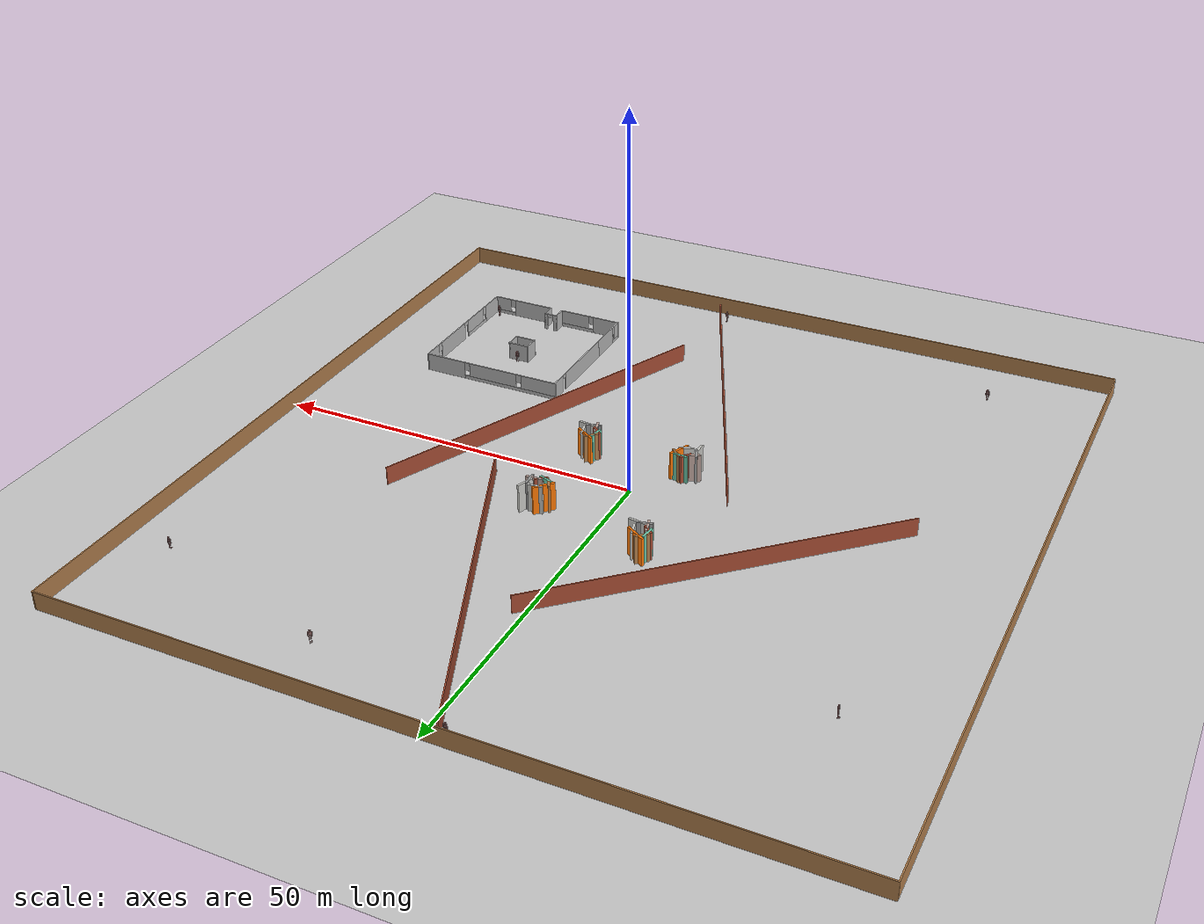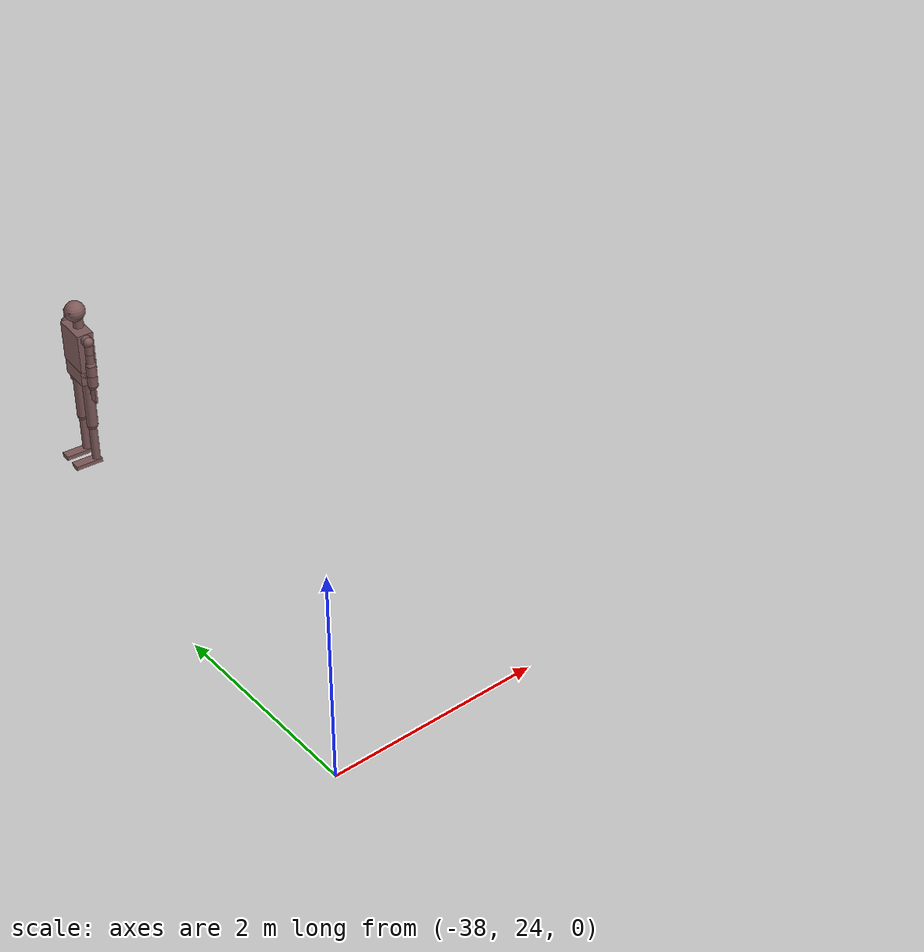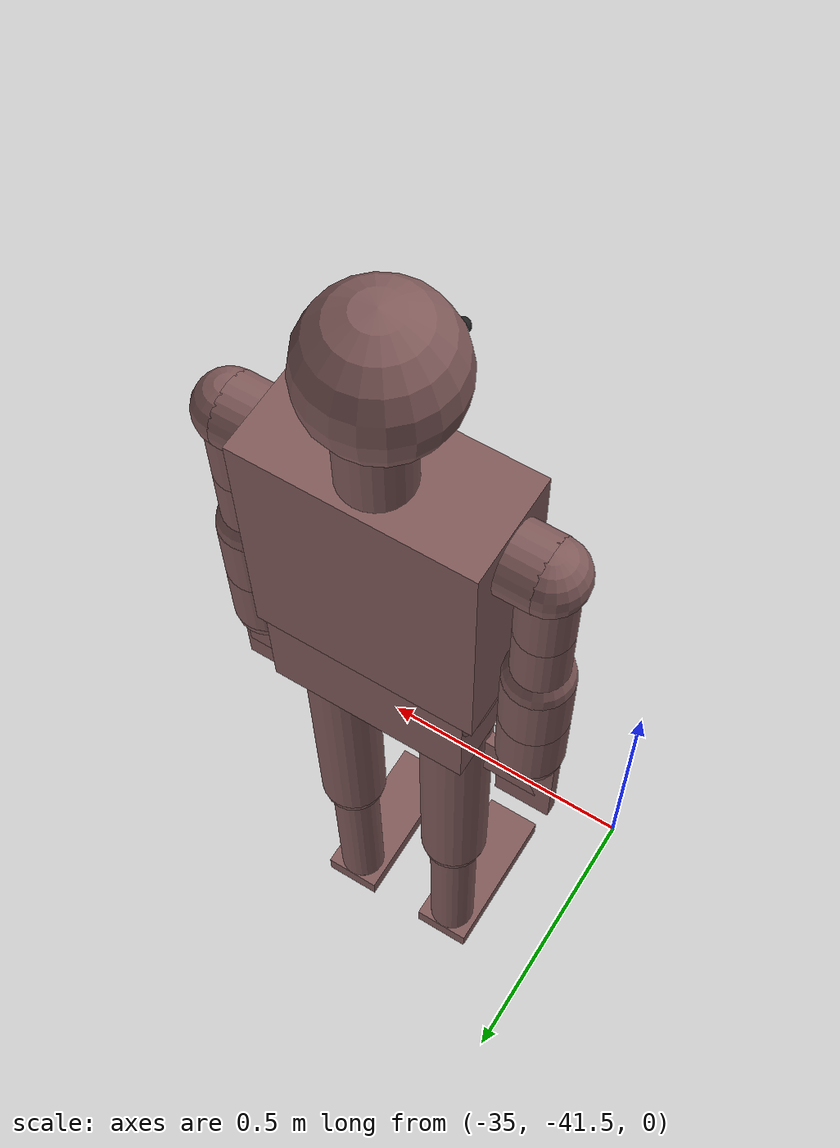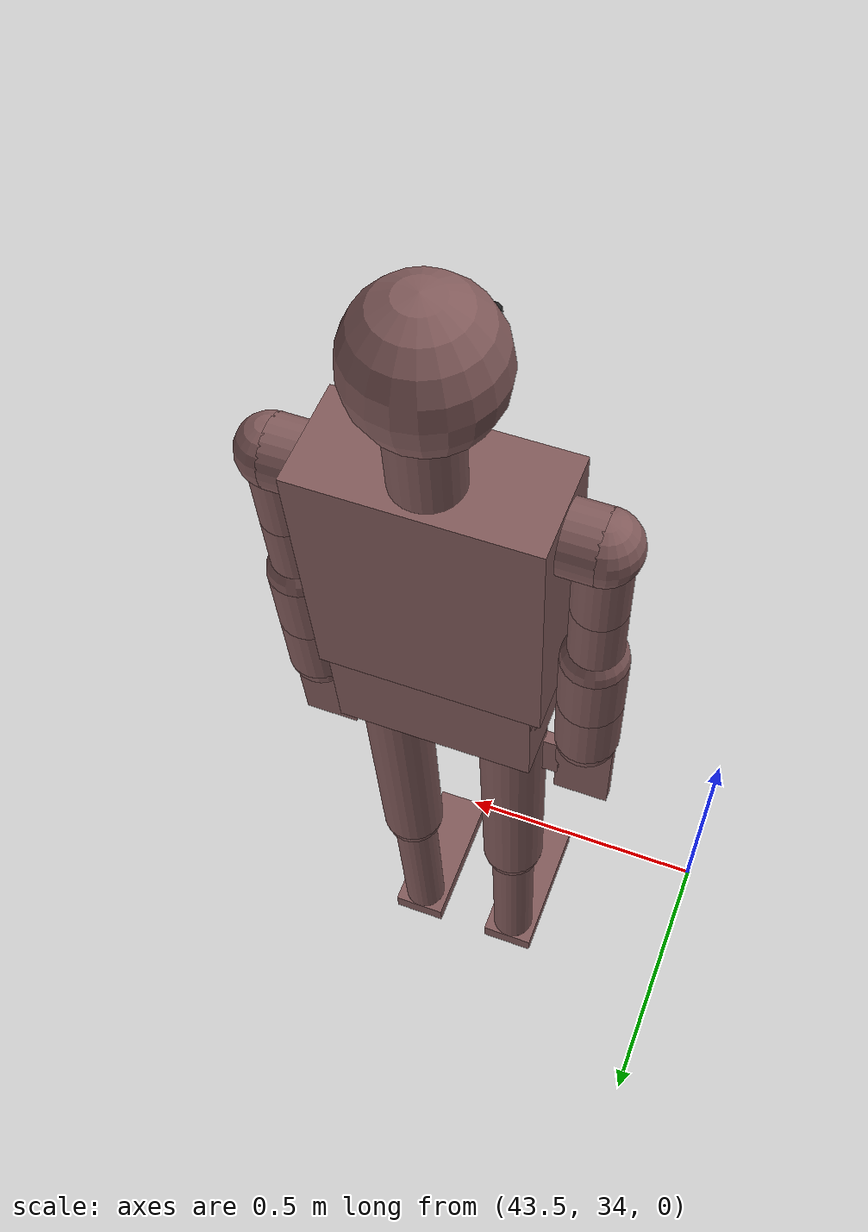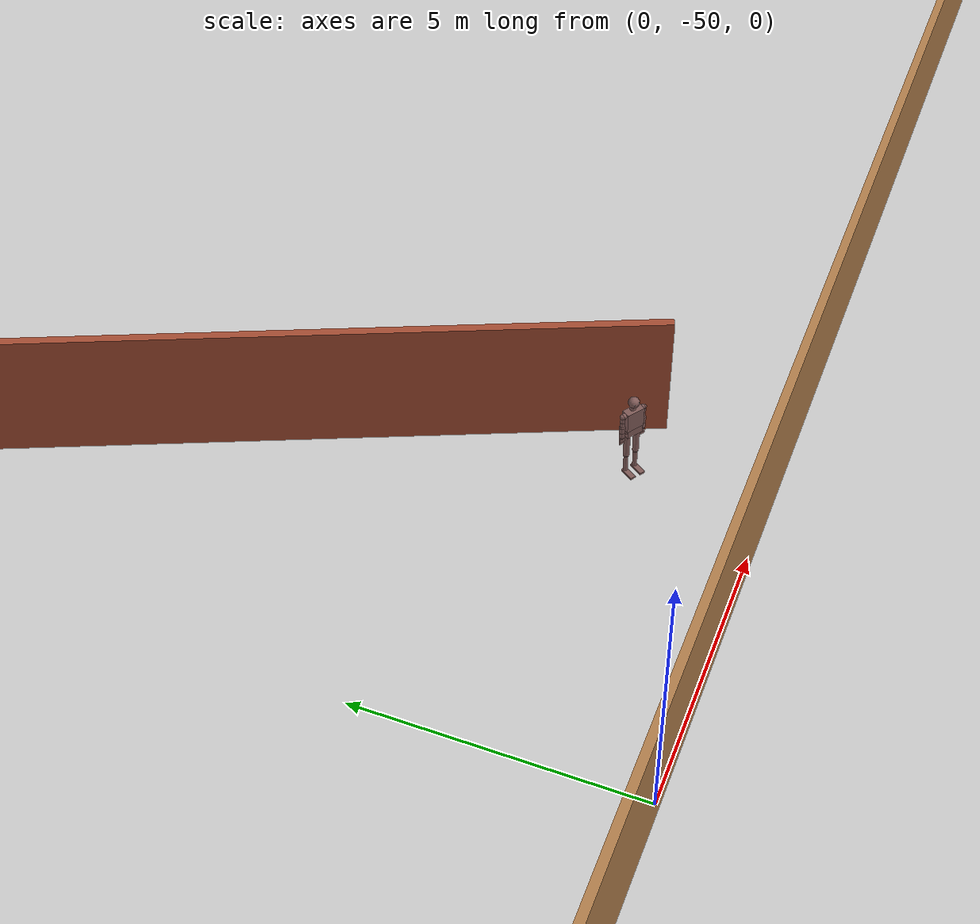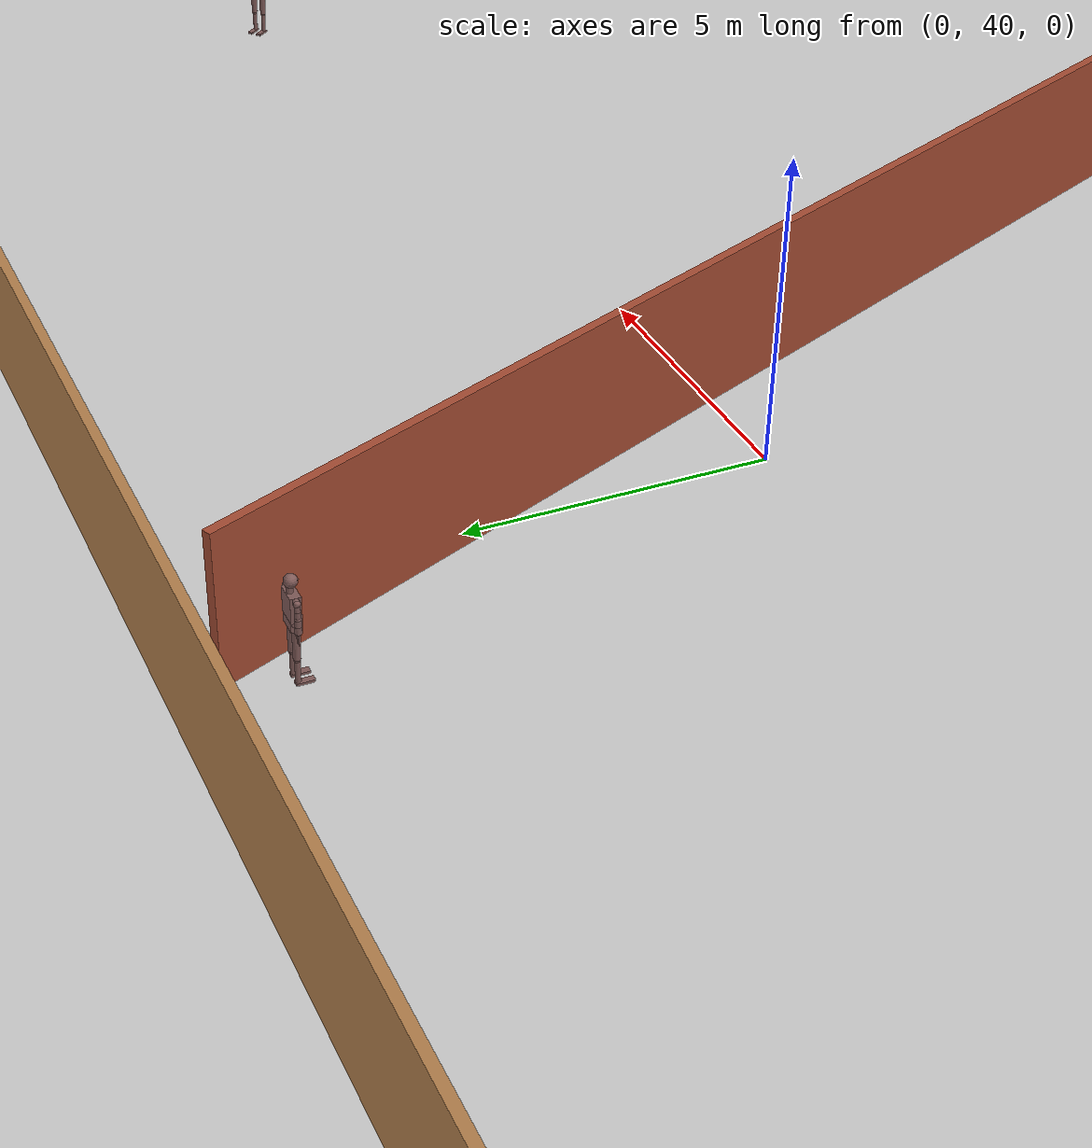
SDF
<sdf version="1.6">
 <world name="default">
  <light name="sun" type="directional">
   <pose>0 0 10 0 -0 0</pose>
   <diffuse>0.8 0.8 0.8 1</diffuse>
   <specular>0.2 0.2 0.2 1</specular>
   <attenuation>
    <range>1000</range>
    <constant>0.9</constant>
    <linear>0.01</linear>
    <quadratic>0.001</quadratic>
   </attenuation>
   <direction>-0.5 0.1 -0.9</direction>
  </light>
  <model name="ground_plane">
   <static>1</static>
   <link name="link">
    <collision name="collision">
     <geometry><plane><normal>0 0 1</normal><size>100 100</size></plane></geometry>
     <surface><friction><ode><mu>100</mu><mu2>50</mu2></ode></friction></surface>
    </collision>
    <visual name="visual">
     <cast_shadows>0</cast_shadows>
     <geometry><plane><normal>0 0 1</normal><size>100 100</size></plane></geometry>
     <material>
      <script><uri>file://media/materials/scripts/gazebo.material</uri><name>Gazebo/Grey</name></script>
     </material>
    </visual>
   </link>
  </model>
  <gravity>0 0 -9.8</gravity>
  <magnetic_field>6e-06 2.3e-05 -4.2e-05</magnetic_field>
  <atmosphere type="adiabatic"/>
  <physics name="default_physics" default="0" type="ode">
   <max_step_size>0.001</max_step_size>
   <real_time_factor>1</real_time_factor>
   <real_time_update_rate>1000</real_time_update_rate>
  </physics>
  <scene><ambient>0.4 0.4 0.4 1</ambient><background>0.7 0.7 0.7 1</background><shadows>1</shadows></scene>
  <spherical_coordinates>
   <surface_model>EARTH_WGS84</surface_model>
   <latitude_deg>0</latitude_deg>
   <longitude_deg>0</longitude_deg>
   <elevation>0</elevation>
   <heading_deg>0</heading_deg>
  </spherical_coordinates>
  <light name="user_point_light_0" type="point">
   <pose>-23.9748 21.7906 1 0 -0 0</pose>
   <diffuse>0.5 0.5 0.5 1</diffuse>
   <specular>0.1 0.1 0.1 1</specular>
   <attenuation>
    <range>20</range>
    <constant>0.5</constant>
    <linear>0.01</linear>
    <quadratic>0.001</quadratic>
   </attenuation>
   <cast_shadows>0</cast_shadows>
   <direction>0 0 -1</direction>
  </light>
  <light name="user_point_light_1" type="point">
   <pose>-42.8296 25.2198 1 0 -0 0</pose>
   <diffuse>0.5 0.5 0.5 1</diffuse>
   <specular>0.1 0.1 0.1 1</specular>
   <attenuation>
    <range>20</range>
    <constant>0.5</constant>
    <linear>0.01</linear>
    <quadratic>0.001</quadratic>
   </attenuation>
   <cast_shadows>0</cast_shadows>
   <direction>0 0 -1</direction>
  </light>
  <light name="user_point_light_2" type="point">
   <pose>-8.47126 23.2312 1 0 -0 0</pose>
   <diffuse>0.5 0.5 0.5 1</diffuse>
   <specular>0.1 0.1 0.1 1</specular>
   <attenuation>
    <range>20</range>
    <constant>0.5</constant>
    <linear>0.01</linear>
    <quadratic>0.001</quadratic>
   </attenuation>
   <cast_shadows>0</cast_shadows>
   <direction>0 0 -1</direction>
  </light>
  <light name="user_point_light_3" type="point">
   <pose>-30.7232 38.6971 1 0 -0 0</pose>
   <diffuse>0.5 0.5 0.5 1</diffuse>
   <specular>0.1 0.1 0.1 1</specular>
   <attenuation>
    <range>20</range>
    <constant>0.5</constant>
    <linear>0.01</linear>
    <quadratic>0.001</quadratic>
   </attenuation>
   <cast_shadows>0</cast_shadows>
   <direction>0 0 -1</direction>
  </light>
  <light name="user_point_light_4" type="point">
   <pose>-30.8473 21.0112 1 0 -0 0</pose>
   <diffuse>0.5 0.5 0.5 1</diffuse>
   <specular>0.1 0.1 0.1 1</specular>
   <attenuation>
    <range>20</range>
    <constant>0.5</constant>
    <linear>0.01</linear>
    <quadratic>0.001</quadratic>
   </attenuation>
   <cast_shadows>0</cast_shadows>
   <direction>0 0 -1</direction>
  </light>
  <light name="user_spot_light_0" type="spot">
   <pose>-26.3513 29.8314 1 0 -0 0</pose>
   <diffuse>0.5 0.5 0.5 1</diffuse>
   <specular>0.1 0.1 0.1 1</specular>
   <direction>0 0 -1</direction>
   <attenuation>
    <range>20</range>
    <constant>0.5</constant>
    <linear>0.01</linear>
    <quadratic>0.001</quadratic>
   </attenuation>
   <cast_shadows>0</cast_shadows>
   <spot><inner_angle>0.6</inner_angle><outer_angle>1</outer_angle><falloff>1</falloff></spot>
  </light>
  <light name="user_point_light_5" type="point">
   <pose>-41.8952 0.097154 1 0 -0 0</pose>
   <diffuse>0.5 0.5 0.5 1</diffuse>
   <specular>0.1 0.1 0.1 1</specular>
   <attenuation>
    <range>20</range>
    <constant>0.5</constant>
    <linear>0.01</linear>
    <quadratic>0.001</quadratic>
   </attenuation>
   <cast_shadows>0</cast_shadows>
   <direction>0 0 -1</direction>
  </light>
  <model name="office_env">
   <pose>28.8782 -26.1863 0 0 -0 0</pose>
   <link name="Wall_10">
    <pose>-5.46873 -9.925 0 0 -0 0</pose>
    <visual name="Wall_10_Visual_0">
     <pose>-2.62812 0 1.25 0 -0 0</pose>
     <geometry><box><size>3.99376 0.15 2.5</size></box></geometry>
     <material>
      <script>
       <uri>model://office_env/materials/scripts</uri>
       <uri>model://office_env/materials/textures</uri>
       <name>wall</name>
      </script>
     </material>
     <meta><layer>0</layer></meta>
    </visual>
    <collision name="Wall_10_Collision_0">
     <geometry><box><size>3.99376 0.15 2.5</size></box></geometry>
     <pose>-2.62812 0 1.25 0 -0 0</pose>
    </collision>
    <visual name="Wall_10_Visual_1">
     <pose>1.99688 0 0.25 0 -0 0</pose>
     <geometry><box><size>5.25624 0.15 0.5</size></box></geometry>
     <material>
      <script>
       <uri>model://office_env/materials/scripts</uri>
       <uri>model://office_env/materials/textures</uri>
       <name>wall</name>
      </script>
     </material>
     <meta><layer>0</layer></meta>
    </visual>
    <collision name="Wall_10_Collision_1">
     <geometry><box><size>5.25624 0.15 0.5</size></box></geometry>
     <pose>1.99688 0 0.25 0 -0 0</pose>
    </collision>
    <visual name="Wall_10_Visual_2">
     <pose>2.39688 0 1.5 0 -0 0</pose>
     <geometry><box><size>4.45624 0.15 2</size></box></geometry>
     <material>
      <script>
       <uri>model://office_env/materials/scripts</uri>
       <uri>model://office_env/materials/textures</uri>
       <name>wall</name>
      </script>
     </material>
     <meta><layer>0</layer></meta>
    </visual>
    <collision name="Wall_10_Collision_2">
     <geometry><box><size>4.45624 0.15 2</size></box></geometry>
     <pose>2.39688 0 1.5 0 -0 0</pose>
    </collision>
    <visual name="Wall_10_Visual_3">
     <pose>-0.231239 0 1.9 0 -0 0</pose>
     <geometry><box><size>0.8 0.15 1.2</size></box></geometry>
     <material>
      <script>
       <uri>model://office_env/materials/scripts</uri>
       <uri>model://office_env/materials/textures</uri>
       <name>wall</name>
      </script>
     </material>
     <meta><layer>0</layer></meta>
    </visual>
    <collision name="Wall_10_Collision_3">
     <geometry><box><size>0.8 0.15 1.2</size></box></geometry>
     <pose>-0.231239 0 1.9 0 -0 0</pose>
    </collision>
   </link>
   <link name="Wall_11">
    <collision name="Wall_11_Collision">
     <geometry><box><size>2 0.15 2.5</size></box></geometry>
     <pose>0 0 1.25 0 -0 0</pose>
    </collision>
    <visual name="Wall_11_Visual">
     <pose>0 0 1.25 0 -0 0</pose>
     <geometry><box><size>2 0.15 2.5</size></box></geometry>
     <material>
      <script>
       <uri>model://office_env/materials/scripts</uri>
       <uri>model://office_env/materials/textures</uri>
       <name>wall</name>
      </script>
     </material>
     <meta><layer>0</layer></meta>
    </visual>
    <pose>-0.918728 -9 0 0 -0 1.5708</pose>
   </link>
   <link name="Wall_12">
    <pose>0.006272 -8.075 0 0 -0 0</pose>
    <visual name="Wall_12_Visual_0">
     <pose>-0.695653 0 1.25 0 -0 0</pose>
     <geometry><box><size>0.608694 0.15 2.5</size></box></geometry>
     <material>
      <script>
       <uri>model://office_env/materials/scripts</uri>
       <uri>model://office_env/materials/textures</uri>
       <name>wall</name>
      </script>
     </material>
     <meta><layer>0</layer></meta>
    </visual>
    <collision name="Wall_12_Collision_0">
     <geometry><box><size>0.608694 0.15 2.5</size></box></geometry>
     <pose>-0.695653 0 1.25 0 -0 0</pose>
    </collision>
    <visual name="Wall_12_Visual_1">
     <pose>0.754347 0 1.25 0 -0 0</pose>
     <geometry><box><size>0.491306 0.15 2.5</size></box></geometry>
     <material>
      <script>
       <uri>model://office_env/materials/scripts</uri>
       <uri>model://office_env/materials/textures</uri>
       <name>wall</name>
      </script>
     </material>
     <meta><layer>0</layer></meta>
    </visual>
    <collision name="Wall_12_Collision_1">
     <geometry><box><size>0.491306 0.15 2.5</size></box></geometry>
     <pose>0.754347 0 1.25 0 -0 0</pose>
    </collision>
    <visual name="Wall_12_Visual_2">
     <pose>0.058694 0 2.25 0 -0 0</pose>
     <geometry><box><size>0.9 0.15 0.5</size></box></geometry>
     <material>
      <script>
       <uri>model://office_env/materials/scripts</uri>
       <uri>model://office_env/materials/textures</uri>
       <name>wall</name>
      </script>
     </material>
     <meta><layer>0</layer></meta>
    </visual>
    <collision name="Wall_12_Collision_2">
     <geometry><box><size>0.9 0.15 0.5</size></box></geometry>
     <pose>0.058694 0 2.25 0 -0 0</pose>
    </collision>
   </link>
   <link name="Wall_15">
    <collision name="Wall_15_Collision">
     <geometry><box><size>2 0.15 2.5</size></box></geometry>
     <pose>0 0 1.25 0 -0 0</pose>
    </collision>
    <visual name="Wall_15_Visual">
     <pose>0 0 1.25 0 -0 0</pose>
     <geometry><box><size>2 0.15 2.5</size></box></geometry>
     <material>
      <script>
       <uri>model://office_env/materials/scripts</uri>
       <uri>model://office_env/materials/textures</uri>
       <name>wall</name>
      </script>
     </material>
     <meta><layer>0</layer></meta>
    </visual>
    <pose>0.931272 -9 0 0 0 -1.5708</pose>
   </link>
   <link name="Wall_16">
    <pose>5.48127 -9.925 0 0 -0 0</pose>
    <visual name="Wall_16_Visual_0">
     <pose>-1.61303 0 1.25 0 -0 0</pose>
     <geometry><box><size>6.02393 0.15 2.5</size></box></geometry>
     <material>
      <script>
       <uri>model://office_env/materials/scripts</uri>
       <uri>model://office_env/materials/textures</uri>
       <name>wall</name>
      </script>
     </material>
     <meta><layer>0</layer></meta>
    </visual>
    <collision name="Wall_16_Collision_0">
     <geometry><box><size>6.02393 0.15 2.5</size></box></geometry>
     <pose>-1.61303 0 1.25 0 -0 0</pose>
    </collision>
    <visual name="Wall_16_Visual_1">
     <pose>3.01197 0 0.25 0 -0 0</pose>
     <geometry><box><size>3.22607 0.15 0.5</size></box></geometry>
     <material>
      <script>
       <uri>model://office_env/materials/scripts</uri>
       <uri>model://office_env/materials/textures</uri>
       <name>wall</name>
      </script>
     </material>
     <meta><layer>0</layer></meta>
    </visual>
    <collision name="Wall_16_Collision_1">
     <geometry><box><size>3.22607 0.15 0.5</size></box></geometry>
     <pose>3.01197 0 0.25 0 -0 0</pose>
    </collision>
    <visual name="Wall_16_Visual_2">
     <pose>3.41197 0 1.5 0 -0 0</pose>
     <geometry><box><size>2.42607 0.15 2</size></box></geometry>
     <material>
      <script>
       <uri>model://office_env/materials/scripts</uri>
       <uri>model://office_env/materials/textures</uri>
       <name>wall</name>
      </script>
     </material>
     <meta><layer>0</layer></meta>
    </visual>
    <collision name="Wall_16_Collision_2">
     <geometry><box><size>2.42607 0.15 2</size></box></geometry>
     <pose>3.41197 0 1.5 0 -0 0</pose>
    </collision>
    <visual name="Wall_16_Visual_3">
     <pose>1.79893 0 1.9 0 -0 0</pose>
     <geometry><box><size>0.8 0.15 1.2</size></box></geometry>
     <material>
      <script>
       <uri>model://office_env/materials/scripts</uri>
       <uri>model://office_env/materials/textures</uri>
       <name>wall</name>
      </script>
     </material>
     <meta><layer>0</layer></meta>
    </visual>
    <collision name="Wall_16_Collision_3">
     <geometry><box><size>0.8 0.15 1.2</size></box></geometry>
     <pose>1.79893 0 1.9 0 -0 0</pose>
    </collision>
   </link>
   <link name="Wall_17">
    <pose>10.0313 0 0 0 -0 1.5708</pose>
    <visual name="Wall_17_Visual_0">
     <pose>-8.12184 0 1.25 0 -0 0</pose>
     <geometry><box><size>3.75631 0.15 2.5</size></box></geometry>
     <material>
      <script>
       <uri>model://office_env/materials/scripts</uri>
       <uri>model://office_env/materials/textures</uri>
       <name>wall</name>
      </script>
     </material>
     <meta><layer>0</layer></meta>
    </visual>
    <collision name="Wall_17_Collision_0">
     <geometry><box><size>3.75631 0.15 2.5</size></box></geometry>
     <pose>-8.12184 0 1.25 0 -0 0</pose>
    </collision>
    <visual name="Wall_17_Visual_1">
     <pose>3.09096 0 1.25 0 -0 0</pose>
     <geometry><box><size>6.45362 0.15 2.5</size></box></geometry>
     <material>
      <script>
       <uri>model://office_env/materials/scripts</uri>
       <uri>model://office_env/materials/textures</uri>
       <name>wall</name>
      </script>
     </material>
     <meta><layer>0</layer></meta>
    </visual>
    <collision name="Wall_17_Collision_1">
     <geometry><box><size>6.45362 0.15 2.5</size></box></geometry>
     <pose>3.09096 0 1.25 0 -0 0</pose>
    </collision>
    <visual name="Wall_17_Visual_2">
     <pose>-3.63977 0 0.25 0 -0 0</pose>
     <geometry><box><size>5.20784 0.15 0.5</size></box></geometry>
     <material>
      <script>
       <uri>model://office_env/materials/scripts</uri>
       <uri>model://office_env/materials/textures</uri>
       <name>wall</name>
      </script>
     </material>
     <meta><layer>0</layer></meta>
    </visual>
    <collision name="Wall_17_Collision_2">
     <geometry><box><size>5.20784 0.15 0.5</size></box></geometry>
     <pose>-3.63977 0 0.25 0 -0 0</pose>
    </collision>
    <visual name="Wall_17_Visual_3">
     <pose>8.15888 0 0.25 0 -0 0</pose>
     <geometry><box><size>3.68223 0.15 0.5</size></box></geometry>
     <material>
      <script>
       <uri>model://office_env/materials/scripts</uri>
       <uri>model://office_env/materials/textures</uri>
       <name>wall</name>
      </script>
     </material>
     <meta><layer>0</layer></meta>
    </visual>
    <collision name="Wall_17_Collision_3">
     <geometry><box><size>3.68223 0.15 0.5</size></box></geometry>
     <pose>8.15888 0 0.25 0 -0 0</pose>
    </collision>
    <visual name="Wall_17_Visual_4">
     <pose>-3.23977 0 1.5 0 -0 0</pose>
     <geometry><box><size>4.40784 0.15 2</size></box></geometry>
     <material>
      <script>
       <uri>model://office_env/materials/scripts</uri>
       <uri>model://office_env/materials/textures</uri>
       <name>wall</name>
      </script>
     </material>
     <meta><layer>0</layer></meta>
    </visual>
    <collision name="Wall_17_Collision_4">
     <geometry><box><size>4.40784 0.15 2</size></box></geometry>
     <pose>-3.23977 0 1.5 0 -0 0</pose>
    </collision>
    <visual name="Wall_17_Visual_5">
     <pose>-3.23977 0 1.5 0 -0 0</pose>
     <geometry><box><size>4.40784 0.15 2</size></box></geometry>
     <material>
      <script>
       <uri>model://office_env/materials/scripts</uri>
       <uri>model://office_env/materials/textures</uri>
       <name>wall</name>
      </script>
     </material>
     <meta><layer>0</layer></meta>
    </visual>
    <collision name="Wall_17_Collision_5">
     <geometry><box><size>4.40784 0.15 2</size></box></geometry>
     <pose>-3.23977 0 1.5 0 -0 0</pose>
    </collision>
    <visual name="Wall_17_Visual_6">
     <pose>8.55889 0 1.5 0 -0 0</pose>
     <geometry><box><size>2.88223 0.15 2</size></box></geometry>
     <material>
      <script>
       <uri>model://office_env/materials/scripts</uri>
       <uri>model://office_env/materials/textures</uri>
       <name>wall</name>
      </script>
     </material>
     <meta><layer>0</layer></meta>
    </visual>
    <collision name="Wall_17_Collision_6">
     <geometry><box><size>2.88223 0.15 2</size></box></geometry>
     <pose>8.55889 0 1.5 0 -0 0</pose>
    </collision>
    <visual name="Wall_17_Visual_7">
     <pose>-5.84369 0 1.9 0 -0 0</pose>
     <geometry><box><size>0.8 0.15 1.2</size></box></geometry>
     <material>
      <script>
       <uri>model://office_env/materials/scripts</uri>
       <uri>model://office_env/materials/textures</uri>
       <name>wall</name>
      </script>
     </material>
     <meta><layer>0</layer></meta>
    </visual>
    <collision name="Wall_17_Collision_7">
     <geometry><box><size>0.8 0.15 1.2</size></box></geometry>
     <pose>-5.84369 0 1.9 0 -0 0</pose>
    </collision>
    <visual name="Wall_17_Visual_8">
     <pose>6.71777 0 1.9 0 -0 0</pose>
     <geometry><box><size>0.8 0.15 1.2</size></box></geometry>
     <material>
      <script>
       <uri>model://office_env/materials/scripts</uri>
       <uri>model://office_env/materials/textures</uri>
       <name>wall</name>
      </script>
     </material>
     <meta><layer>0</layer></meta>
    </visual>
    <collision name="Wall_17_Collision_8">
     <geometry><box><size>0.8 0.15 1.2</size></box></geometry>
     <pose>6.71777 0 1.9 0 -0 0</pose>
    </collision>
    <visual name="Wall_17_Visual_9">
     <pose>-0.585848 0 2.25 0 -0 0</pose>
     <geometry><box><size>0.9 0.15 0.5</size></box></geometry>
     <material>
      <script>
       <uri>model://office_env/materials/scripts</uri>
       <uri>model://office_env/materials/textures</uri>
       <name>wall</name>
      </script>
     </material>
     <meta><layer>0</layer></meta>
    </visual>
    <collision name="Wall_17_Collision_9">
     <geometry><box><size>0.9 0.15 0.5</size></box></geometry>
     <pose>-0.585848 0 2.25 0 -0 0</pose>
    </collision>
    <visual name="Wall_17_Visual_10">
     <pose>-0.585848 0 2.25 0 -0 0</pose>
     <geometry><box><size>0.9 0.15 0.5</size></box></geometry>
     <material>
      <script>
       <uri>model://office_env/materials/scripts</uri>
       <uri>model://office_env/materials/textures</uri>
       <name>wall</name>
      </script>
     </material>
     <meta><layer>0</layer></meta>
    </visual>
    <collision name="Wall_17_Collision_10">
     <geometry><box><size>0.9 0.15 0.5</size></box></geometry>
     <pose>-0.585848 0 2.25 0 -0 0</pose>
    </collision>
   </link>
   <link name="Wall_19">
    <pose>-0 9.925 0 0 -0 3.14159</pose>
    <visual name="Wall_19_Visual_0">
     <pose>-7.12533 0 1.25 0 -0 0</pose>
     <geometry><box><size>5.96188 0.15 2.5</size></box></geometry>
     <material>
      <script>
       <uri>model://office_env/materials/scripts</uri>
       <uri>model://office_env/materials/textures</uri>
       <name>wall</name>
      </script>
     </material>
     <meta><layer>0</layer></meta>
    </visual>
    <collision name="Wall_19_Collision_0">
     <geometry><box><size>5.96188 0.15 2.5</size></box></geometry>
     <pose>-7.12533 0 1.25 0 -0 0</pose>
    </collision>
    <visual name="Wall_19_Visual_1">
     <pose>2.98094 0 0.25 0 -0 0</pose>
     <geometry><box><size>14.2507 0.15 0.5</size></box></geometry>
     <material>
      <script>
       <uri>model://office_env/materials/scripts</uri>
       <uri>model://office_env/materials/textures</uri>
       <name>wall</name>
      </script>
     </material>
     <meta><layer>0</layer></meta>
    </visual>
    <collision name="Wall_19_Collision_1">
     <geometry><box><size>14.2507 0.15 0.5</size></box></geometry>
     <pose>2.98094 0 0.25 0 -0 0</pose>
    </collision>
    <visual name="Wall_19_Visual_2">
     <pose>0.326454 0 1.5 0 -0 0</pose>
     <geometry><box><size>7.34169 0.15 2</size></box></geometry>
     <material>
      <script>
       <uri>model://office_env/materials/scripts</uri>
       <uri>model://office_env/materials/textures</uri>
       <name>wall</name>
      </script>
     </material>
     <meta><layer>0</layer></meta>
    </visual>
    <collision name="Wall_19_Collision_2">
     <geometry><box><size>7.34169 0.15 2</size></box></geometry>
     <pose>0.326454 0 1.5 0 -0 0</pose>
    </collision>
    <visual name="Wall_19_Visual_3">
     <pose>7.45179 0 1.5 0 -0 0</pose>
     <geometry><box><size>5.30898 0.15 2</size></box></geometry>
     <material>
      <script>
       <uri>model://office_env/materials/scripts</uri>
       <uri>model://office_env/materials/textures</uri>
       <name>wall</name>
      </script>
     </material>
     <meta><layer>0</layer></meta>
    </visual>
    <collision name="Wall_19_Collision_3">
     <geometry><box><size>5.30898 0.15 2</size></box></geometry>
     <pose>7.45179 0 1.5 0 -0 0</pose>
    </collision>
    <visual name="Wall_19_Visual_4">
     <pose>-3.74439 0 1.9 0 -0 0</pose>
     <geometry><box><size>0.8 0.15 1.2</size></box></geometry>
     <material>
      <script>
       <uri>model://office_env/materials/scripts</uri>
       <uri>model://office_env/materials/textures</uri>
       <name>wall</name>
      </script>
     </material>
     <meta><layer>0</layer></meta>
    </visual>
    <collision name="Wall_19_Collision_4">
     <geometry><box><size>0.8 0.15 1.2</size></box></geometry>
     <pose>-3.74439 0 1.9 0 -0 0</pose>
    </collision>
    <visual name="Wall_19_Visual_5">
     <pose>4.3973 0 1.9 0 -0 0</pose>
     <geometry><box><size>0.8 0.15 1.2</size></box></geometry>
     <material>
      <script>
       <uri>model://office_env/materials/scripts</uri>
       <uri>model://office_env/materials/textures</uri>
       <name>wall</name>
      </script>
     </material>
     <meta><layer>0</layer></meta>
    </visual>
    <collision name="Wall_19_Collision_5">
     <geometry><box><size>0.8 0.15 1.2</size></box></geometry>
     <pose>4.3973 0 1.9 0 -0 0</pose>
    </collision>
   </link>
   <link name="Wall_2">
    <pose>-10.0187 -6.75 0 0 0 -1.5708</pose>
    <visual name="Wall_2_Visual_0">
     <pose>-1.06854 0 1.25 0 -0 0</pose>
     <geometry><box><size>4.36293 0.15 2.5</size></box></geometry>
     <material>
      <script>
       <uri>model://office_env/materials/scripts</uri>
       <uri>model://office_env/materials/textures</uri>
       <name>wall</name>
      </script>
     </material>
     <meta><layer>0</layer></meta>
    </visual>
    <collision name="Wall_2_Collision_0">
     <geometry><box><size>4.36293 0.15 2.5</size></box></geometry>
     <pose>-1.06854 0 1.25 0 -0 0</pose>
    </collision>
    <visual name="Wall_2_Visual_1">
     <pose>2.18147 0 0.25 0 -0 0</pose>
     <geometry><box><size>2.13707 0.15 0.5</size></box></geometry>
     <material>
      <script>
       <uri>model://office_env/materials/scripts</uri>
       <uri>model://office_env/materials/textures</uri>
       <name>wall</name>
      </script>
     </material>
     <meta><layer>0</layer></meta>
    </visual>
    <collision name="Wall_2_Collision_1">
     <geometry><box><size>2.13707 0.15 0.5</size></box></geometry>
     <pose>2.18147 0 0.25 0 -0 0</pose>
    </collision>
    <visual name="Wall_2_Visual_2">
     <pose>2.58147 0 1.5 0 -0 0</pose>
     <geometry><box><size>1.33707 0.15 2</size></box></geometry>
     <material>
      <script>
       <uri>model://office_env/materials/scripts</uri>
       <uri>model://office_env/materials/textures</uri>
       <name>wall</name>
      </script>
     </material>
     <meta><layer>0</layer></meta>
    </visual>
    <collision name="Wall_2_Collision_2">
     <geometry><box><size>1.33707 0.15 2</size></box></geometry>
     <pose>2.58147 0 1.5 0 -0 0</pose>
    </collision>
    <visual name="Wall_2_Visual_3">
     <pose>1.51293 0 1.9 0 -0 0</pose>
     <geometry><box><size>0.8 0.15 1.2</size></box></geometry>
     <material>
      <script>
       <uri>model://office_env/materials/scripts</uri>
       <uri>model://office_env/materials/textures</uri>
       <name>wall</name>
      </script>
     </material>
     <meta><layer>0</layer></meta>
    </visual>
    <collision name="Wall_2_Collision_3">
     <geometry><box><size>0.8 0.15 1.2</size></box></geometry>
     <pose>1.51293 0 1.9 0 -0 0</pose>
    </collision>
   </link>
   <link name="Wall_20">
    <pose>-10.018 3.125 0 0 0 -1.5708</pose>
    <visual name="Wall_20_Visual_0">
     <pose>-5.73803 0 1.25 0 -0 0</pose>
     <geometry><box><size>2.27394 0.15 2.5</size></box></geometry>
     <material>
      <script>
       <uri>model://office_env/materials/scripts</uri>
       <uri>model://office_env/materials/textures</uri>
       <name>wall</name>
      </script>
     </material>
     <meta><layer>0</layer></meta>
    </visual>
    <collision name="Wall_20_Collision_0">
     <geometry><box><size>2.27394 0.15 2.5</size></box></geometry>
     <pose>-5.73803 0 1.25 0 -0 0</pose>
    </collision>
    <visual name="Wall_20_Visual_1">
     <pose>1.58697 0 1.25 0 -0 0</pose>
     <geometry><box><size>10.5761 0.15 2.5</size></box></geometry>
     <material>
      <script>
       <uri>model://office_env/materials/scripts</uri>
       <uri>model://office_env/materials/textures</uri>
       <name>wall</name>
      </script>
     </material>
     <meta><layer>0</layer></meta>
    </visual>
    <collision name="Wall_20_Collision_1">
     <geometry><box><size>10.5761 0.15 2.5</size></box></geometry>
     <pose>1.58697 0 1.25 0 -0 0</pose>
    </collision>
    <visual name="Wall_20_Visual_2">
     <pose>-4.15106 0 2.25 0 -0 0</pose>
     <geometry><box><size>0.9 0.15 0.5</size></box></geometry>
     <material>
      <script>
       <uri>model://office_env/materials/scripts</uri>
       <uri>model://office_env/materials/textures</uri>
       <name>wall</name>
      </script>
     </material>
     <meta><layer>0</layer></meta>
    </visual>
    <collision name="Wall_20_Collision_2">
     <geometry><box><size>0.9 0.15 0.5</size></box></geometry>
     <pose>-4.15106 0 2.25 0 -0 0</pose>
    </collision>
   </link>
   <link name="Wall_22">
    <collision name="Wall_22_Collision">
     <geometry><box><size>3 0.15 2.5</size></box></geometry>
     <pose>0 0 1.25 0 -0 0</pose>
    </collision>
    <visual name="Wall_22_Visual">
     <pose>0 0 1.25 0 -0 0</pose>
     <geometry><box><size>3 0.15 2.5</size></box></geometry>
     <material>
      <script>
       <uri>model://office_env/materials/scripts</uri>
       <uri>model://office_env/materials/textures</uri>
       <name>wall</name>
      </script>
     </material>
     <meta><layer>0</layer></meta>
    </visual>
    <pose>-0.163956 0.04737 0 0 -0 3.14159</pose>
   </link>
   <link name="Wall_23">
    <collision name="Wall_23_Collision">
     <geometry><box><size>2.25 0.15 2.5</size></box></geometry>
     <pose>0 0 1.25 0 -0 0</pose>
    </collision>
    <visual name="Wall_23_Visual">
     <pose>0 0 1.25 0 -0 0</pose>
     <geometry><box><size>2.25 0.15 2.5</size></box></geometry>
     <material>
      <script>
       <uri>model://office_env/materials/scripts</uri>
       <uri>model://office_env/materials/textures</uri>
       <name>wall</name>
      </script>
     </material>
     <meta><layer>0</layer></meta>
    </visual>
    <pose>-1.58896 1.09737 0 0 -0 1.5708</pose>
   </link>
   <link name="Wall_24">
    <collision name="Wall_24_Collision">
     <geometry><box><size>3 0.15 2.5</size></box></geometry>
     <pose>0 0 1.25 0 -0 0</pose>
    </collision>
    <visual name="Wall_24_Visual">
     <pose>0 0 1.25 0 -0 0</pose>
     <geometry><box><size>3 0.15 2.5</size></box></geometry>
     <material>
      <script>
       <uri>model://office_env/materials/scripts</uri>
       <uri>model://office_env/materials/textures</uri>
       <name>wall</name>
      </script>
     </material>
     <meta><layer>0</layer></meta>
    </visual>
    <pose>-0.163956 2.14737 0 0 -0 0</pose>
   </link>
   <link name="Wall_25">
    <collision name="Wall_25_Collision">
     <geometry><box><size>2.25 0.15 2.5</size></box></geometry>
     <pose>0 0 1.25 0 -0 0</pose>
    </collision>
    <visual name="Wall_25_Visual">
     <pose>0 0 1.25 0 -0 0</pose>
     <geometry><box><size>2.25 0.15 2.5</size></box></geometry>
     <material>
      <script>
       <uri>model://office_env/materials/scripts</uri>
       <uri>model://office_env/materials/textures</uri>
       <name>wall</name>
      </script>
     </material>
     <meta><layer>0</layer></meta>
    </visual>
    <pose>1.26104 1.09737 0 0 0 -1.5708</pose>
   </link>
   <static>1</static>
  </model>
  <model name="io2018obs1">
   <pose>-6.7989 11.6978 0 0 -0 0</pose>
   <link name="Wall_1">
    <collision name="Wall_1_Collision">
     <geometry><box><size>1.98802 0.3 5</size></box></geometry>
     <pose>0 0 1.25 0 -0 0</pose>
    </collision>
    <visual name="Wall_1_Visual">
     <pose>0 0 1.25 0 -0 0</pose>
     <geometry><box><size>1.98802 0.3 5</size></box></geometry>
     <material>
      <script><uri>file://media/materials/scripts/gazebo.material</uri><name>Gazebo/CeilingTiled</name></script>
      <ambient>1 1 1 1</ambient>
     </material>
     <meta><layer>0</layer></meta>
    </visual>
    <pose>0.680268 0.279956 0 0 -0 1.81211</pose>
   </link>
   <link name="Wall_2">
    <collision name="Wall_2_Collision">
     <geometry><box><size>2.98224 0.3 5</size></box></geometry>
     <pose>0 0 1.25 0 -0 0</pose>
    </collision>
    <visual name="Wall_2_Visual">
     <pose>0 0 1.25 0 -0 0</pose>
     <geometry><box><size>2.98224 0.3 5</size></box></geometry>
     <material>
      <script><uri>file://media/materials/scripts/gazebo.material</uri><name>Gazebo/Grey</name></script>
      <ambient>0.996078 0.47451 0.0196078 1</ambient>
     </material>
     <meta><layer>0</layer></meta>
    </visual>
    <pose>0.01442 1.04473 0 0 -0 2.60117</pose>
   </link>
   <link name="Wall_3">
    <collision name="Wall_3_Collision">
     <geometry><box><size>1.91541 0.3 5</size></box></geometry>
     <pose>0 0 1.25 0 -0 0</pose>
    </collision>
    <visual name="Wall_3_Visual">
     <pose>0 0 1.25 0 -0 0</pose>
     <geometry><box><size>1.91541 0.3 5</size></box></geometry>
     <material>
      <script><uri>file://media/materials/scripts/gazebo.material</uri><name>Gazebo/Wood</name></script>
      <ambient>1 0.764706 0.305882 1</ambient>
     </material>
     <meta><layer>0</layer></meta>
    </visual>
    <pose>-0.868641 1.11723 0 0 -0 -2.40096</pose>
   </link>
   <link name="Wall_4">
    <collision name="Wall_4_Collision">
     <geometry><box><size>2.0052 0.3 5</size></box></geometry>
     <pose>0 0 1.25 0 -0 0</pose>
    </collision>
    <visual name="Wall_4_Visual">
     <pose>0 0 1.25 0 -0 0</pose>
     <geometry><box><size>2.0052 0.3 5</size></box></geometry>
     <material>
      <script><uri>file://media/materials/scripts/gazebo.material</uri><name>Gazebo/Grey</name></script>
      <ambient>0.435294 0.796078 0.67451 1</ambient>
     </material>
     <meta><layer>0</layer></meta>
    </visual>
    <pose>-1.2417 0.42342 0 0 -0 -1.72387</pose>
   </link>
   <link name="Wall_5">
    <collision name="Wall_5_Collision">
     <geometry><box><size>1.71361 0.3 5</size></box></geometry>
     <pose>0 0 1.25 0 -0 0</pose>
    </collision>
    <visual name="Wall_5_Visual">
     <pose>0 0 1.25 0 -0 0</pose>
     <geometry><box><size>1.71361 0.3 5</size></box></geometry>
     <material>
      <script><uri>file://media/materials/scripts/gazebo.material</uri><name>Gazebo/Bricks</name></script>
      <ambient>1 1 1 1</ambient>
     </material>
     <meta><layer>0</layer></meta>
    </visual>
    <pose>-1.04078 -0.230654 0 0 -0 -0.718988</pose>
   </link>
   <link name="Wall_6">
    <collision name="Wall_6_Collision">
     <geometry><box><size>2.25058 0.3 5</size></box></geometry>
     <pose>0 0 1.25 0 -0 0</pose>
    </collision>
    <visual name="Wall_6_Visual">
     <pose>0 0 1.25 0 -0 0</pose>
     <geometry><box><size>2.25058 0.3 5</size></box></geometry>
     <material>
      <script><uri>file://media/materials/scripts/gazebo.material</uri><name>Gazebo/Grey</name></script>
      <ambient>0.760784 0.662745 0.627451 1</ambient>
     </material>
     <meta><layer>0</layer></meta>
    </visual>
    <pose>-0.634849 -0.933414 0 0 -0 -1.30095</pose>
   </link>
   <link name="Wall_7">
    <collision name="Wall_7_Collision">
     <geometry><box><size>2 0.3 5</size></box></geometry>
     <pose>0 0 1.25 0 -0 0</pose>
    </collision>
    <visual name="Wall_7_Visual">
     <pose>0 0 1.25 0 -0 0</pose>
     <geometry><box><size>2 0.3 5</size></box></geometry>
     <material>
      <script><uri>file://media/materials/scripts/gazebo.material</uri><name>Gazebo/Grey</name></script>
      <ambient>1 1 1 1</ambient>
     </material>
     <meta><layer>0</layer></meta>
    </visual>
    <pose>-0.094331 -1.27342 0 0 -0 0.261799</pose>
   </link>
   <link name="Wall_8">
    <collision name="Wall_8_Collision">
     <geometry><box><size>2.34356 0.3 5</size></box></geometry>
     <pose>0 0 1.25 0 -0 0</pose>
    </collision>
    <visual name="Wall_8_Visual">
     <pose>0 0 1.25 0 -0 0</pose>
     <geometry><box><size>2.34356 0.3 5</size></box></geometry>
     <material>
      <script><uri>file://media/materials/scripts/gazebo.material</uri><name>Gazebo/CeilingTiled</name></script>
      <ambient>1 1 1 1</ambient>
     </material>
     <meta><layer>0</layer></meta>
    </visual>
    <pose>0.821928 -1.23577 0 0 -0 -0.142091</pose>
   </link>
   <static>1</static>
  </model>
  <model name="io2018obs1_0">
   <pose>8.41617 -5.68721 0 0 -0 0</pose>
   <link name="Wall_1">
    <collision name="Wall_1_Collision">
     <geometry><box><size>1.98802 0.3 5</size></box></geometry>
     <pose>0 0 1.25 0 -0 0</pose>
    </collision>
    <visual name="Wall_1_Visual">
     <pose>0 0 1.25 0 -0 0</pose>
     <geometry><box><size>1.98802 0.3 5</size></box></geometry>
     <material>
      <script><uri>file://media/materials/scripts/gazebo.material</uri><name>Gazebo/CeilingTiled</name></script>
      <ambient>1 1 1 1</ambient>
     </material>
     <meta><layer>0</layer></meta>
    </visual>
    <pose>0.680268 0.279956 0 0 -0 1.81211</pose>
   </link>
   <link name="Wall_2">
    <collision name="Wall_2_Collision">
     <geometry><box><size>2.98224 0.3 5</size></box></geometry>
     <pose>0 0 1.25 0 -0 0</pose>
    </collision>
    <visual name="Wall_2_Visual">
     <pose>0 0 1.25 0 -0 0</pose>
     <geometry><box><size>2.98224 0.3 5</size></box></geometry>
     <material>
      <script><uri>file://media/materials/scripts/gazebo.material</uri><name>Gazebo/Grey</name></script>
      <ambient>0.996078 0.47451 0.0196078 1</ambient>
     </material>
     <meta><layer>0</layer></meta>
    </visual>
    <pose>0.01442 1.04473 0 0 -0 2.60117</pose>
   </link>
   <link name="Wall_3">
    <collision name="Wall_3_Collision">
     <geometry><box><size>1.91541 0.3 5</size></box></geometry>
     <pose>0 0 1.25 0 -0 0</pose>
    </collision>
    <visual name="Wall_3_Visual">
     <pose>0 0 1.25 0 -0 0</pose>
     <geometry><box><size>1.91541 0.3 5</size></box></geometry>
     <material>
      <script><uri>file://media/materials/scripts/gazebo.material</uri><name>Gazebo/Wood</name></script>
      <ambient>1 0.764706 0.305882 1</ambient>
     </material>
     <meta><layer>0</layer></meta>
    </visual>
    <pose>-0.868641 1.11723 0 0 -0 -2.40096</pose>
   </link>
   <link name="Wall_4">
    <collision name="Wall_4_Collision">
     <geometry><box><size>2.0052 0.3 5</size></box></geometry>
     <pose>0 0 1.25 0 -0 0</pose>
    </collision>
    <visual name="Wall_4_Visual">
     <pose>0 0 1.25 0 -0 0</pose>
     <geometry><box><size>2.0052 0.3 5</size></box></geometry>
     <material>
      <script><uri>file://media/materials/scripts/gazebo.material</uri><name>Gazebo/Grey</name></script>
      <ambient>0.435294 0.796078 0.67451 1</ambient>
     </material>
     <meta><layer>0</layer></meta>
    </visual>
    <pose>-1.2417 0.42342 0 0 -0 -1.72387</pose>
   </link>
   <link name="Wall_5">
    <collision name="Wall_5_Collision">
     <geometry><box><size>1.71361 0.3 5</size></box></geometry>
     <pose>0 0 1.25 0 -0 0</pose>
    </collision>
    <visual name="Wall_5_Visual">
     <pose>0 0 1.25 0 -0 0</pose>
     <geometry><box><size>1.71361 0.3 5</size></box></geometry>
     <material>
      <script><uri>file://media/materials/scripts/gazebo.material</uri><name>Gazebo/Bricks</name></script>
      <ambient>1 1 1 1</ambient>
     </material>
     <meta><layer>0</layer></meta>
    </visual>
    <pose>-1.04078 -0.230654 0 0 -0 -0.718988</pose>
   </link>
   <link name="Wall_6">
    <collision name="Wall_6_Collision">
     <geometry><box><size>2.25058 0.3 5</size></box></geometry>
     <pose>0 0 1.25 0 -0 0</pose>
    </collision>
    <visual name="Wall_6_Visual">
     <pose>0 0 1.25 0 -0 0</pose>
     <geometry><box><size>2.25058 0.3 5</size></box></geometry>
     <material>
      <script><uri>file://media/materials/scripts/gazebo.material</uri><name>Gazebo/Grey</name></script>
      <ambient>0.760784 0.662745 0.627451 1</ambient>
     </material>
     <meta><layer>0</layer></meta>
    </visual>
    <pose>-0.634849 -0.933414 0 0 -0 -1.30095</pose>
   </link>
   <link name="Wall_7">
    <collision name="Wall_7_Collision">
     <geometry><box><size>2 0.3 5</size></box></geometry>
     <pose>0 0 1.25 0 -0 0</pose>
    </collision>
    <visual name="Wall_7_Visual">
     <pose>0 0 1.25 0 -0 0</pose>
     <geometry><box><size>2 0.3 5</size></box></geometry>
     <material>
      <script><uri>file://media/materials/scripts/gazebo.material</uri><name>Gazebo/Grey</name></script>
      <ambient>1 1 1 1</ambient>
     </material>
     <meta><layer>0</layer></meta>
    </visual>
    <pose>-0.094331 -1.27342 0 0 -0 0.261799</pose>
   </link>
   <link name="Wall_8">
    <collision name="Wall_8_Collision">
     <geometry><box><size>2.34356 0.3 5</size></box></geometry>
     <pose>0 0 1.25 0 -0 0</pose>
    </collision>
    <visual name="Wall_8_Visual">
     <pose>0 0 1.25 0 -0 0</pose>
     <geometry><box><size>2.34356 0.3 5</size></box></geometry>
     <material>
      <script><uri>file://media/materials/scripts/gazebo.material</uri><name>Gazebo/CeilingTiled</name></script>
      <ambient>1 1 1 1</ambient>
     </material>
     <meta><layer>0</layer></meta>
    </visual>
    <pose>0.821928 -1.23577 0 0 -0 -0.142091</pose>
   </link>
   <static>1</static>
  </model>
  <model name="io2018obs1_1">
   <pose>8.60861 8.13307 0 0 -0 1.37311</pose>
   <link name="Wall_1">
    <collision name="Wall_1_Collision">
     <geometry><box><size>1.98802 0.3 5</size></box></geometry>
     <pose>0 0 1.25 0 -0 0</pose>
    </collision>
    <visual name="Wall_1_Visual">
     <pose>0 0 1.25 0 -0 0</pose>
     <geometry><box><size>1.98802 0.3 5</size></box></geometry>
     <material>
      <script><uri>file://media/materials/scripts/gazebo.material</uri><name>Gazebo/CeilingTiled</name></script>
      <ambient>1 1 1 1</ambient>
     </material>
     <meta><layer>0</layer></meta>
    </visual>
    <pose>0.680268 0.279956 0 0 -0 1.81211</pose>
   </link>
   <link name="Wall_2">
    <collision name="Wall_2_Collision">
     <geometry><box><size>2.98224 0.3 5</size></box></geometry>
     <pose>0 0 1.25 0 -0 0</pose>
    </collision>
    <visual name="Wall_2_Visual">
     <pose>0 0 1.25 0 -0 0</pose>
     <geometry><box><size>2.98224 0.3 5</size></box></geometry>
     <material>
      <script><uri>file://media/materials/scripts/gazebo.material</uri><name>Gazebo/Grey</name></script>
      <ambient>0.996078 0.47451 0.0196078 1</ambient>
     </material>
     <meta><layer>0</layer></meta>
    </visual>
    <pose>0.01442 1.04473 0 0 -0 2.60117</pose>
   </link>
   <link name="Wall_3">
    <collision name="Wall_3_Collision">
     <geometry><box><size>1.91541 0.3 5</size></box></geometry>
     <pose>0 0 1.25 0 -0 0</pose>
    </collision>
    <visual name="Wall_3_Visual">
     <pose>0 0 1.25 0 -0 0</pose>
     <geometry><box><size>1.91541 0.3 5</size></box></geometry>
     <material>
      <script><uri>file://media/materials/scripts/gazebo.material</uri><name>Gazebo/Wood</name></script>
      <ambient>1 0.764706 0.305882 1</ambient>
     </material>
     <meta><layer>0</layer></meta>
    </visual>
    <pose>-0.868641 1.11723 0 0 -0 -2.40096</pose>
   </link>
   <link name="Wall_4">
    <collision name="Wall_4_Collision">
     <geometry><box><size>2.0052 0.3 5</size></box></geometry>
     <pose>0 0 1.25 0 -0 0</pose>
    </collision>
    <visual name="Wall_4_Visual">
     <pose>0 0 1.25 0 -0 0</pose>
     <geometry><box><size>2.0052 0.3 5</size></box></geometry>
     <material>
      <script><uri>file://media/materials/scripts/gazebo.material</uri><name>Gazebo/Grey</name></script>
      <ambient>0.435294 0.796078 0.67451 1</ambient>
     </material>
     <meta><layer>0</layer></meta>
    </visual>
    <pose>-1.2417 0.42342 0 0 -0 -1.72387</pose>
   </link>
   <link name="Wall_5">
    <collision name="Wall_5_Collision">
     <geometry><box><size>1.71361 0.3 5</size></box></geometry>
     <pose>0 0 1.25 0 -0 0</pose>
    </collision>
    <visual name="Wall_5_Visual">
     <pose>0 0 1.25 0 -0 0</pose>
     <geometry><box><size>1.71361 0.3 5</size></box></geometry>
     <material>
      <script><uri>file://media/materials/scripts/gazebo.material</uri><name>Gazebo/Bricks</name></script>
      <ambient>1 1 1 1</ambient>
     </material>
     <meta><layer>0</layer></meta>
    </visual>
    <pose>-1.04078 -0.230654 0 0 -0 -0.718988</pose>
   </link>
   <link name="Wall_6">
    <collision name="Wall_6_Collision">
     <geometry><box><size>2.25058 0.3 5</size></box></geometry>
     <pose>0 0 1.25 0 -0 0</pose>
    </collision>
    <visual name="Wall_6_Visual">
     <pose>0 0 1.25 0 -0 0</pose>
     <geometry><box><size>2.25058 0.3 5</size></box></geometry>
     <material>
      <script><uri>file://media/materials/scripts/gazebo.material</uri><name>Gazebo/Grey</name></script>
      <ambient>0.760784 0.662745 0.627451 1</ambient>
     </material>
     <meta><layer>0</layer></meta>
    </visual>
    <pose>-0.634849 -0.933414 0 0 -0 -1.30095</pose>
   </link>
   <link name="Wall_7">
    <collision name="Wall_7_Collision">
     <geometry><box><size>2 0.3 5</size></box></geometry>
     <pose>0 0 1.25 0 -0 0</pose>
    </collision>
    <visual name="Wall_7_Visual">
     <pose>0 0 1.25 0 -0 0</pose>
     <geometry><box><size>2 0.3 5</size></box></geometry>
     <material>
      <script><uri>file://media/materials/scripts/gazebo.material</uri><name>Gazebo/Grey</name></script>
      <ambient>1 1 1 1</ambient>
     </material>
     <meta><layer>0</layer></meta>
    </visual>
    <pose>-0.094331 -1.27342 0 0 -0 0.261799</pose>
   </link>
   <link name="Wall_8">
    <collision name="Wall_8_Collision">
     <geometry><box><size>2.34356 0.3 5</size></box></geometry>
     <pose>0 0 1.25 0 -0 0</pose>
    </collision>
    <visual name="Wall_8_Visual">
     <pose>0 0 1.25 0 -0 0</pose>
     <geometry><box><size>2.34356 0.3 5</size></box></geometry>
     <material>
      <script><uri>file://media/materials/scripts/gazebo.material</uri><name>Gazebo/CeilingTiled</name></script>
      <ambient>1 1 1 1</ambient>
     </material>
     <meta><layer>0</layer></meta>
    </visual>
    <pose>0.821928 -1.23577 0 0 -0 -0.142091</pose>
   </link>
   <static>1</static>
  </model>
  <model name="io2018obs1_2">
   <pose>-5.06876 -6.23908 0 0 0 -1.47799</pose>
   <link name="Wall_1">
    <collision name="Wall_1_Collision">
     <geometry><box><size>1.98802 0.3 5</size></box></geometry>
     <pose>0 0 1.25 0 -0 0</pose>
    </collision>
    <visual name="Wall_1_Visual">
     <pose>0 0 1.25 0 -0 0</pose>
     <geometry><box><size>1.98802 0.3 5</size></box></geometry>
     <material>
      <script><uri>file://media/materials/scripts/gazebo.material</uri><name>Gazebo/CeilingTiled</name></script>
      <ambient>1 1 1 1</ambient>
     </material>
     <meta><layer>0</layer></meta>
    </visual>
    <pose>0.680268 0.279956 0 0 -0 1.81211</pose>
   </link>
   <link name="Wall_2">
    <collision name="Wall_2_Collision">
     <geometry><box><size>2.98224 0.3 5</size></box></geometry>
     <pose>0 0 1.25 0 -0 0</pose>
    </collision>
    <visual name="Wall_2_Visual">
     <pose>0 0 1.25 0 -0 0</pose>
     <geometry><box><size>2.98224 0.3 5</size></box></geometry>
     <material>
      <script><uri>file://media/materials/scripts/gazebo.material</uri><name>Gazebo/Grey</name></script>
      <ambient>0.996078 0.47451 0.0196078 1</ambient>
     </material>
     <meta><layer>0</layer></meta>
    </visual>
    <pose>0.01442 1.04473 0 0 -0 2.60117</pose>
   </link>
   <link name="Wall_3">
    <collision name="Wall_3_Collision">
     <geometry><box><size>1.91541 0.3 5</size></box></geometry>
     <pose>0 0 1.25 0 -0 0</pose>
    </collision>
    <visual name="Wall_3_Visual">
     <pose>0 0 1.25 0 -0 0</pose>
     <geometry><box><size>1.91541 0.3 5</size></box></geometry>
     <material>
      <script><uri>file://media/materials/scripts/gazebo.material</uri><name>Gazebo/Wood</name></script>
      <ambient>1 0.764706 0.305882 1</ambient>
     </material>
     <meta><layer>0</layer></meta>
    </visual>
    <pose>-0.868641 1.11723 0 0 -0 -2.40096</pose>
   </link>
   <link name="Wall_4">
    <collision name="Wall_4_Collision">
     <geometry><box><size>2.0052 0.3 5</size></box></geometry>
     <pose>0 0 1.25 0 -0 0</pose>
    </collision>
    <visual name="Wall_4_Visual">
     <pose>0 0 1.25 0 -0 0</pose>
     <geometry><box><size>2.0052 0.3 5</size></box></geometry>
     <material>
      <script><uri>file://media/materials/scripts/gazebo.material</uri><name>Gazebo/Grey</name></script>
      <ambient>0.435294 0.796078 0.67451 1</ambient>
     </material>
     <meta><layer>0</layer></meta>
    </visual>
    <pose>-1.2417 0.42342 0 0 -0 -1.72387</pose>
   </link>
   <link name="Wall_5">
    <collision name="Wall_5_Collision">
     <geometry><box><size>1.71361 0.3 5</size></box></geometry>
     <pose>0 0 1.25 0 -0 0</pose>
    </collision>
    <visual name="Wall_5_Visual">
     <pose>0 0 1.25 0 -0 0</pose>
     <geometry><box><size>1.71361 0.3 5</size></box></geometry>
     <material>
      <script><uri>file://media/materials/scripts/gazebo.material</uri><name>Gazebo/Bricks</name></script>
      <ambient>1 1 1 1</ambient>
     </material>
     <meta><layer>0</layer></meta>
    </visual>
    <pose>-1.04078 -0.230654 0 0 -0 -0.718988</pose>
   </link>
   <link name="Wall_6">
    <collision name="Wall_6_Collision">
     <geometry><box><size>2.25058 0.3 5</size></box></geometry>
     <pose>0 0 1.25 0 -0 0</pose>
    </collision>
    <visual name="Wall_6_Visual">
     <pose>0 0 1.25 0 -0 0</pose>
     <geometry><box><size>2.25058 0.3 5</size></box></geometry>
     <material>
      <script><uri>file://media/materials/scripts/gazebo.material</uri><name>Gazebo/Grey</name></script>
      <ambient>0.760784 0.662745 0.627451 1</ambient>
     </material>
     <meta><layer>0</layer></meta>
    </visual>
    <pose>-0.634849 -0.933414 0 0 -0 -1.30095</pose>
   </link>
   <link name="Wall_7">
    <collision name="Wall_7_Collision">
     <geometry><box><size>2 0.3 5</size></box></geometry>
     <pose>0 0 1.25 0 -0 0</pose>
    </collision>
    <visual name="Wall_7_Visual">
     <pose>0 0 1.25 0 -0 0</pose>
     <geometry><box><size>2 0.3 5</size></box></geometry>
     <material>
      <script><uri>file://media/materials/scripts/gazebo.material</uri><name>Gazebo/Grey</name></script>
      <ambient>1 1 1 1</ambient>
     </material>
     <meta><layer>0</layer></meta>
    </visual>
    <pose>-0.094331 -1.27342 0 0 -0 0.261799</pose>
   </link>
   <link name="Wall_8">
    <collision name="Wall_8_Collision">
     <geometry><box><size>2.34356 0.3 5</size></box></geometry>
     <pose>0 0 1.25 0 -0 0</pose>
    </collision>
    <visual name="Wall_8_Visual">
     <pose>0 0 1.25 0 -0 0</pose>
     <geometry><box><size>2.34356 0.3 5</size></box></geometry>
     <material>
      <script><uri>file://media/materials/scripts/gazebo.material</uri><name>Gazebo/CeilingTiled</name></script>
      <ambient>1 1 1 1</ambient>
     </material>
     <meta><layer>0</layer></meta>
    </visual>
    <pose>0.821928 -1.23577 0 0 -0 -0.142091</pose>
   </link>
   <static>1</static>
  </model>
  <model name="wall1">
   <pose>-2.47689 -24.8643 0 0 0 -1.16186</pose>
   <link name="Wall_0">
    <collision name="Wall_0_Collision">
     <geometry><box><size>50 0.15 2.5</size></box></geometry>
     <pose>0 0 1.25 0 -0 0</pose>
    </collision>
    <visual name="Wall_0_Visual">
     <pose>0 0 1.25 0 -0 0</pose>
     <geometry><box><size>50 0.15 2.5</size></box></geometry>
     <material>
      <script><uri>file://media/materials/scripts/gazebo.material</uri><name>Gazebo/Bricks</name></script>
      <ambient>1 1 1 1</ambient>
     </material>
    </visual>
    <pose>1e-06 0 0 0 -0 3.14159</pose>
   </link>
   <static>1</static>
  </model>
  <model name="wall1_0">
   <pose>17.7728 -11.2046 0 0 -0 1.1421</pose>
   <link name="Wall_0">
    <collision name="Wall_0_Collision">
     <geometry><box><size>50 0.15 2.5</size></box></geometry>
     <pose>0 0 1.25 0 -0 0</pose>
    </collision>
    <visual name="Wall_0_Visual">
     <pose>0 0 1.25 0 -0 0</pose>
     <geometry><box><size>50 0.15 2.5</size></box></geometry>
     <material>
      <script><uri>file://media/materials/scripts/gazebo.material</uri><name>Gazebo/Bricks</name></script>
      <ambient>1 1 1 1</ambient>
     </material>
    </visual>
    <pose>1e-06 0 0 0 -0 3.14159</pose>
   </link>
   <static>1</static>
  </model>
  <model name="wall1_1">
   <pose>-16.9608 10.9979 0 0 -0 0.747125</pose>
   <link name="Wall_0">
    <collision name="Wall_0_Collision">
     <geometry><box><size>50 0.15 2.5</size></box></geometry>
     <pose>0 0 1.25 0 -0 0</pose>
    </collision>
    <visual name="Wall_0_Visual">
     <pose>0 0 1.25 0 -0 0</pose>
     <geometry><box><size>50 0.15 2.5</size></box></geometry>
     <material>
      <script><uri>file://media/materials/scripts/gazebo.material</uri><name>Gazebo/Bricks</name></script>
      <ambient>1 1 1 1</ambient>
     </material>
    </visual>
    <pose>1e-06 0 0 0 -0 3.14159</pose>
   </link>
   <static>1</static>
  </model>
  <model name="wall1_2">
   <pose>7.63078 26.25 0 0 0 -1.17657</pose>
   <link name="Wall_0">
    <collision name="Wall_0_Collision">
     <geometry><box><size>50 0.15 2.5</size></box></geometry>
     <pose>0 0 1.25 0 -0 0</pose>
    </collision>
    <visual name="Wall_0_Visual">
     <pose>0 0 1.25 0 -0 0</pose>
     <geometry><box><size>50 0.15 2.5</size></box></geometry>
     <material>
      <script><uri>file://media/materials/scripts/gazebo.material</uri><name>Gazebo/Bricks</name></script>
      <ambient>1 1 1 1</ambient>
     </material>
    </visual>
    <pose>1e-06 0 0 0 -0 3.14159</pose>
   </link>
   <static>1</static>
  </model>
  <model name="fgsdgdf">
   <link name="Wall_0">
    <collision name="Wall_0_Collision">
     <geometry><box><size>100.15 0.15 2.5</size></box></geometry>
     <pose>0 0 1.25 0 -0 0</pose>
    </collision>
    <visual name="Wall_0_Visual">
     <pose>0 0 1.25 0 -0 0</pose>
     <geometry><box><size>100.15 0.15 2.5</size></box></geometry>
     <material>
      <script><uri>file://media/materials/scripts/gazebo.material</uri><name>Gazebo/Wood</name></script>
      <ambient>1 1 1 1</ambient>
     </material>
     <meta><layer>0</layer></meta>
    </visual>
    <pose>-50 0 0 0 -0 -1.5708</pose>
   </link>
   <link name="Wall_1">
    <collision name="Wall_1_Collision">
     <geometry><box><size>100.15 0.15 2.5</size></box></geometry>
     <pose>0 0 1.25 0 -0 0</pose>
    </collision>
    <visual name="Wall_1_Visual">
     <pose>0 0 1.25 0 -0 0</pose>
     <geometry><box><size>100.15 0.15 2.5</size></box></geometry>
     <material>
      <script><uri>file://media/materials/scripts/gazebo.material</uri><name>Gazebo/Wood</name></script>
      <ambient>1 1 1 1</ambient>
     </material>
     <meta><layer>0</layer></meta>
    </visual>
    <pose>0 -50 0 0 -0 0</pose>
   </link>
   <link name="Wall_2">
    <collision name="Wall_2_Collision">
     <geometry><box><size>100.15 0.15 2.5</size></box></geometry>
     <pose>0 0 1.25 0 -0 0</pose>
    </collision>
    <visual name="Wall_2_Visual">
     <pose>0 0 1.25 0 -0 0</pose>
     <geometry><box><size>100.15 0.15 2.5</size></box></geometry>
     <material>
      <script><uri>file://media/materials/scripts/gazebo.material</uri><name>Gazebo/Wood</name></script>
      <ambient>1 1 1 1</ambient>
     </material>
     <meta><layer>0</layer></meta>
    </visual>
    <pose>50 0 0 0 -0 1.5708</pose>
   </link>
   <link name="Wall_3">
    <collision name="Wall_3_Collision">
     <geometry><box><size>100.15 0.15 2.5</size></box></geometry>
     <pose>0 0 1.25 0 -0 0</pose>
    </collision>
    <visual name="Wall_3_Visual">
     <pose>0 0 1.25 0 -0 0</pose>
     <geometry><box><size>100.15 0.15 2.5</size></box></geometry>
     <material>
      <script><uri>file://media/materials/scripts/gazebo.material</uri><name>Gazebo/Wood</name></script>
      <ambient>1 1 1 1</ambient>
     </material>
     <meta><layer>0</layer></meta>
    </visual>
    <pose>0 50 0 0 -0 3.14159</pose>
   </link>
   <static>1</static>
  </model>
  <model name="victim175_hot_moving">
   <static>1</static>
   <self_collide>1</self_collide>
   <link name="head">
    <pose>0 0 1.625 0 -0 0</pose>
    <visual name="visual">
     <geometry><sphere><radius>0.1</radius></sphere></geometry>
     <material>
      <emissive>0.5 0.35 0.35 1</emissive>
      <ambient>0.5 0.35 0.35 1</ambient>
      <diffuse>0.5 0.35 0.35 1</diffuse>
      <specular>0 0 0 0</specular>
     </material>
    </visual>
    <collision name="collision"><geometry><sphere><radius>0.1</radius></sphere></geometry></collision>
    <visual name="visual_nose">
     <pose>0 -0.1 -0.01 0 -0 0</pose>
     <geometry><sphere><radius>0.01</radius></sphere></geometry>
     <material>
      <emissive>0.5 0.35 0.35 1</emissive>
      <ambient>0.5 0.35 0.35 1</ambient>
      <diffuse>0.5 0.35 0.35 1</diffuse>
      <specular>0 0 0 0</specular>
     </material>
    </visual>
    <visual name="visual_rEye">
     <pose>-0.05 -0.08 0.02 0 -0 0</pose>
     <geometry><sphere><radius>0.01</radius></sphere></geometry>
     <material>
      <script><uri>file://media/materials/scripts/gazebo.material</uri><name>Gazebo/Black</name></script>
     </material>
    </visual>
    <visual name="visual_lEye">
     <pose>0.05 -0.08 0.02 0 -0 0</pose>
     <geometry><sphere><radius>0.01</radius></sphere></geometry>
     <material>
      <script><uri>file://media/materials/scripts/gazebo.material</uri><name>Gazebo/Black</name></script>
     </material>
    </visual>
    <self_collide>1</self_collide>
   </link>
   <link name="neck">
    <pose>0 0.02 1.49 0 -0 0</pose>
    <visual name="visual">
     <geometry><cylinder><radius>0.05</radius><length>0.15</length></cylinder></geometry>
     <material>
      <emissive>0.5 0.35 0.35 1</emissive>
      <ambient>0.5 0.35 0.35 1</ambient>
      <diffuse>0.5 0.35 0.35 1</diffuse>
      <specular>0 0 0 0</specular>
     </material>
    </visual>
    <collision name="collision">
     <geometry><cylinder><radius>0.05</radius><length>0.15</length></cylinder></geometry>
    </collision>
    <self_collide>1</self_collide>
   </link>
   <joint name="neck_head" type="revolute">
    <pose>0 0.02 -0.075 0 -0 0</pose>
    <child>head</child>
    <parent>neck</parent>
    <axis>
     <xyz>0 0 -1</xyz>
     <limit><lower>-1.7</lower><upper>1.7</upper></limit>
     <dynamics>
      <friction>0.01</friction>
      <spring_reference>0</spring_reference>
      <spring_stiffness>0</spring_stiffness>
     </dynamics>
     <use_parent_model_frame>0</use_parent_model_frame>
    </axis>
   </joint>
   <link name="body">
    <pose>0 0 1.255 0 -0 0</pose>
    <visual name="visual">
     <geometry><box><size>0.34 0.16 0.4</size></box></geometry>
     <material>
      <emissive>0.5 0.35 0.35 1</emissive>
      <ambient>0.5 0.35 0.35 1</ambient>
      <diffuse>0.5 0.35 0.35 1</diffuse>
      <specular>0 0 0 0</specular>
     </material>
    </visual>
    <collision name="collision"><geometry><box><size>0.34 0.16 0.4</size></box></geometry></collision>
    <self_collide>1</self_collide>
   </link>
   <joint name="body_neck" type="revolute">
    <pose>0 0.06 -0.075 0 -0 0</pose>
    <child>neck</child>
    <parent>body</parent>
    <axis>
     <xyz>1 0 0</xyz>
     <limit><lower>-0.2</lower><upper>1</upper></limit>
     <dynamics>
      <friction>0.01</friction>
      <spring_reference>0</spring_reference>
      <spring_stiffness>0</spring_stiffness>
     </dynamics>
     <use_parent_model_frame>0</use_parent_model_frame>
    </axis>
   </joint>
   <link name="waist">
    <pose>0 0 1.005 0 -0 0</pose>
    <visual name="visual">
     <pose>0 0 -0.025 0 -0 0</pose>
     <geometry><box><size>0.31 0.16 0.15</size></box></geometry>
     <material>
      <emissive>0.5 0.35 0.35 1</emissive>
      <ambient>0.5 0.35 0.35 1</ambient>
      <diffuse>0.5 0.35 0.35 1</diffuse>
      <specular>0 0 0 0</specular>
     </material>
    </visual>
    <collision name="collision"><geometry><box><size>0.31 0.16 0.1</size></box></geometry></collision>
    <visual name="visual2">
     <pose>0 0 0.05 3.14159 1.57079 3.14159</pose>
     <geometry><cylinder><radius>0.08</radius><length>0.31</length></cylinder></geometry>
     <material>
      <emissive>0.5 0.35 0.35 1</emissive>
      <ambient>0.5 0.35 0.35 1</ambient>
      <diffuse>0.5 0.35 0.35 1</diffuse>
      <specular>0 0 0 0</specular>
     </material>
    </visual>
    <collision name="collision2">
     <pose>0 0 0.05 3.14159 1.57079 3.14159</pose>
     <geometry><cylinder><radius>0.08</radius><length>0.31</length></cylinder></geometry>
    </collision>
    <self_collide>1</self_collide>
   </link>
   <joint name="body_waist" type="revolute">
    <pose>0 0 0.05 0 -0 0</pose>
    <child>waist</child>
    <parent>body</parent>
    <axis>
     <xyz>-1 0 0</xyz>
     <limit><lower>0</lower><upper>0</upper></limit>
     <dynamics>
      <friction>0.01</friction>
      <spring_reference>0</spring_reference>
      <spring_stiffness>0</spring_stiffness>
     </dynamics>
     <use_parent_model_frame>0</use_parent_model_frame>
    </axis>
   </joint>
   <link name="rHand">
    <pose>-0.22 0 0.84 0 -0 0</pose>
    <visual name="visual">
     <geometry><box><size>0.09 0.02 0.18</size></box></geometry>
     <material>
      <emissive>0.5 0.35 0.35 1</emissive>
      <ambient>0.5 0.35 0.35 1</ambient>
      <diffuse>0.5 0.35 0.35 1</diffuse>
      <specular>0 0 0 0</specular>
     </material>
    </visual>
    <collision name="collision"><geometry><box><size>0.09 0.02 0.18</size></box></geometry></collision>
    <visual name="visual2">
     <pose>0.02 0 0 0 -0 0</pose>
     <geometry><box><size>0.12 0.02 0.09</size></box></geometry>
     <material>
      <emissive>0.5 0.35 0.35 1</emissive>
      <ambient>0.5 0.35 0.35 1</ambient>
      <diffuse>0.5 0.35 0.35 1</diffuse>
      <specular>0 0 0 0</specular>
     </material>
    </visual>
    <collision name="collision2">
     <pose>0.02 0 0 0 -0 0</pose>
     <geometry><box><size>0.12 0.02 0.09</size></box></geometry>
    </collision>
    <self_collide>1</self_collide>
   </link>
   <link name="lHand">
    <pose>0.22 0 0.84 0 -0 0</pose>
    <visual name="visual">
     <geometry><box><size>0.09 0.02 0.18</size></box></geometry>
     <material>
      <emissive>0.5 0.35 0.35 1</emissive>
      <ambient>0.5 0.35 0.35 1</ambient>
      <diffuse>0.5 0.35 0.35 1</diffuse>
      <specular>0 0 0 0</specular>
     </material>
    </visual>
    <collision name="collision"><geometry><box><size>0.09 0.02 0.18</size></box></geometry></collision>
    <visual name="visual2">
     <pose>-0.02 0 0 0 -0 0</pose>
     <geometry><box><size>0.12 0.02 0.09</size></box></geometry>
     <material>
      <emissive>0.5 0.35 0.35 1</emissive>
      <ambient>0.5 0.35 0.35 1</ambient>
      <diffuse>0.5 0.35 0.35 1</diffuse>
      <specular>0 0 0 0</specular>
     </material>
    </visual>
    <collision name="collision2">
     <pose>-0.02 0 0 0 -0 0</pose>
     <geometry><box><size>0.12 0.02 0.09</size></box></geometry>
    </collision>
    <self_collide>1</self_collide>
   </link>
   <link name="rFoot">
    <pose>-0.1 -0.095 0.02 0 -0 0</pose>
    <visual name="visual">
     <geometry><box><size>0.1 0.27 0.04</size></box></geometry>
     <material>
      <emissive>0.5 0.35 0.35 1</emissive>
      <ambient>0.5 0.35 0.35 1</ambient>
      <diffuse>0.5 0.35 0.35 1</diffuse>
      <specular>0 0 0 0</specular>
     </material>
    </visual>
    <collision name="collision"><geometry><box><size>0.1 0.27 0.04</size></box></geometry></collision>
    <self_collide>1</self_collide>
   </link>
   <link name="lFoot">
    <pose>0.1 -0.095 0.02 0 -0 0</pose>
    <visual name="visual">
     <geometry><box><size>0.1 0.27 0.04</size></box></geometry>
     <material>
      <emissive>0.5 0.35 0.35 1</emissive>
      <ambient>0.5 0.35 0.35 1</ambient>
      <diffuse>0.5 0.35 0.35 1</diffuse>
      <specular>0 0 0 0</specular>
     </material>
    </visual>
    <collision name="collision"><geometry><box><size>0.1 0.27 0.04</size></box></geometry></collision>
    <self_collide>1</self_collide>
   </link>
   <link name="rLeg2">
    <pose>-0.1 0 0.23 0 -0 0</pose>
    <visual name="visual">
     <geometry><cylinder><radius>0.04</radius><length>0.38</length></cylinder></geometry>
     <material>
      <emissive>0.5 0.35 0.35 1</emissive>
      <ambient>0.5 0.35 0.35 1</ambient>
      <diffuse>0.5 0.35 0.35 1</diffuse>
      <specular>0 0 0 0</specular>
     </material>
    </visual>
    <collision name="collision">
     <geometry><cylinder><radius>0.04</radius><length>0.38</length></cylinder></geometry>
    </collision>
    <visual name="visual2">
     <pose>0 0 -0.19 0 -0 0</pose>
     <geometry><sphere><radius>0.04</radius></sphere></geometry>
     <material>
      <emissive>0.5 0.35 0.35 1</emissive>
      <ambient>0.5 0.35 0.35 1</ambient>
      <diffuse>0.5 0.35 0.35 1</diffuse>
      <specular>0 0 0 0</specular>
     </material>
    </visual>
    <collision name="collision2">
     <pose>0 0 -0.19 0 -0 0</pose>
     <geometry><sphere><radius>0.04</radius></sphere></geometry>
    </collision>
    <self_collide>1</self_collide>
   </link>
   <link name="lLeg2">
    <pose>0.1 0 0.23 0 -0 0</pose>
    <visual name="visual">
     <geometry><cylinder><radius>0.04</radius><length>0.38</length></cylinder></geometry>
     <material>
      <emissive>0.5 0.35 0.35 1</emissive>
      <ambient>0.5 0.35 0.35 1</ambient>
      <diffuse>0.5 0.35 0.35 1</diffuse>
      <specular>0 0 0 0</specular>
     </material>
    </visual>
    <collision name="collision">
     <geometry><cylinder><radius>0.04</radius><length>0.38</length></cylinder></geometry>
    </collision>
    <visual name="visual2">
     <pose>0 0 -0.19 0 -0 0</pose>
     <geometry><sphere><radius>0.04</radius></sphere></geometry>
     <material>
      <emissive>0.5 0.35 0.35 1</emissive>
      <ambient>0.5 0.35 0.35 1</ambient>
      <diffuse>0.5 0.35 0.35 1</diffuse>
      <specular>0 0 0 0</specular>
     </material>
    </visual>
    <collision name="collision2">
     <pose>0 0 -0.19 0 -0 0</pose>
     <geometry><sphere><radius>0.04</radius></sphere></geometry>
    </collision>
    <self_collide>1</self_collide>
   </link>
   <joint name="rLeg2_rFoot" type="revolute">
    <pose>0 0.095 0.02 0 -0 0</pose>
    <child>rFoot</child>
    <parent>rLeg2</parent>
    <axis>
     <xyz>1 0 0</xyz>
     <limit><lower>0</lower><upper>0</upper></limit>
     <dynamics>
      <friction>0.01</friction>
      <spring_reference>0</spring_reference>
      <spring_stiffness>0</spring_stiffness>
     </dynamics>
     <use_parent_model_frame>0</use_parent_model_frame>
    </axis>
   </joint>
   <joint name="lLeg2_lFoot" type="revolute">
    <pose>0 0.095 0.02 0 -0 0</pose>
    <child>lFoot</child>
    <parent>lLeg2</parent>
    <axis>
     <xyz>1 0 0</xyz>
     <limit><lower>0</lower><upper>0</upper></limit>
     <dynamics>
      <friction>0.01</friction>
      <spring_reference>0</spring_reference>
      <spring_stiffness>0</spring_stiffness>
     </dynamics>
     <use_parent_model_frame>0</use_parent_model_frame>
    </axis>
   </joint>
   <link name="rLeg1">
    <pose>-0.1 0 0.66 0 -0 0</pose>
    <visual name="visual">
     <geometry><cylinder><radius>0.055</radius><length>0.48</length></cylinder></geometry>
     <material>
      <emissive>0.5 0.35 0.35 1</emissive>
      <ambient>0.5 0.35 0.35 1</ambient>
      <diffuse>0.5 0.35 0.35 1</diffuse>
      <specular>0 0 0 0</specular>
     </material>
    </visual>
    <collision name="collision">
     <geometry><cylinder><radius>0.055</radius><length>0.48</length></cylinder></geometry>
    </collision>
    <visual name="visual2">
     <pose>0 0 -0.24 0 -0 0</pose>
     <geometry><sphere><radius>0.055</radius></sphere></geometry>
     <material>
      <emissive>0.5 0.35 0.35 1</emissive>
      <ambient>0.5 0.35 0.35 1</ambient>
      <diffuse>0.5 0.35 0.35 1</diffuse>
      <specular>0 0 0 0</specular>
     </material>
    </visual>
    <collision name="collision2">
     <pose>0 0 -0.24 0 -0 0</pose>
     <geometry><sphere><radius>0.055</radius></sphere></geometry>
    </collision>
    <visual name="visual3">
     <pose>0 0 0.24 0 -0 0</pose>
     <geometry><sphere><radius>0.055</radius></sphere></geometry>
     <material>
      <emissive>0.5 0.35 0.35 1</emissive>
      <ambient>0.5 0.35 0.35 1</ambient>
      <diffuse>0.5 0.35 0.35 1</diffuse>
      <specular>0 0 0 0</specular>
     </material>
    </visual>
    <collision name="collision3">
     <pose>0 0 0.24 0 -0 0</pose>
     <geometry><sphere><radius>0.055</radius></sphere></geometry>
    </collision>
    <self_collide>1</self_collide>
   </link>
   <link name="lLeg1">
    <pose>0.1 0 0.66 0 -0 0</pose>
    <visual name="visual">
     <geometry><cylinder><radius>0.055</radius><length>0.48</length></cylinder></geometry>
     <material>
      <emissive>0.5 0.35 0.35 1</emissive>
      <ambient>0.5 0.35 0.35 1</ambient>
      <diffuse>0.5 0.35 0.35 1</diffuse>
      <specular>0 0 0 0</specular>
     </material>
    </visual>
    <collision name="collision">
     <geometry><cylinder><radius>0.055</radius><length>0.48</length></cylinder></geometry>
    </collision>
    <visual name="visual2">
     <pose>0 0 -0.24 0 -0 0</pose>
     <geometry><sphere><radius>0.055</radius></sphere></geometry>
     <material>
      <emissive>0.5 0.35 0.35 1</emissive>
      <ambient>0.5 0.35 0.35 1</ambient>
      <diffuse>0.5 0.35 0.35 1</diffuse>
      <specular>0 0 0 0</specular>
     </material>
    </visual>
    <collision name="collision2">
     <pose>0 0 -0.24 0 -0 0</pose>
     <geometry><sphere><radius>0.055</radius></sphere></geometry>
    </collision>
    <visual name="visual3">
     <pose>0 0 0.24 0 -0 0</pose>
     <geometry><sphere><radius>0.055</radius></sphere></geometry>
     <material>
      <emissive>0.5 0.35 0.35 1</emissive>
      <ambient>0.5 0.35 0.35 1</ambient>
      <diffuse>0.5 0.35 0.35 1</diffuse>
      <specular>0 0 0 0</specular>
     </material>
    </visual>
    <collision name="collision3">
     <pose>0 0 0.24 0 -0 0</pose>
     <geometry><sphere><radius>0.055</radius></sphere></geometry>
    </collision>
    <self_collide>1</self_collide>
   </link>
   <joint name="rLeg1_rLeg2" type="revolute">
    <pose>0 0 0.19 0 -0 0</pose>
    <child>rLeg2</child>
    <parent>rLeg1</parent>
    <axis>
     <xyz>1 0 0</xyz>
     <limit><lower>0</lower><upper>0</upper></limit>
     <dynamics>
      <friction>0.01</friction>
      <spring_reference>0</spring_reference>
      <spring_stiffness>0</spring_stiffness>
     </dynamics>
     <use_parent_model_frame>0</use_parent_model_frame>
    </axis>
   </joint>
   <joint name="lLeg1_lLeg2" type="revolute">
    <pose>0 0 0.19 0 -0 0</pose>
    <child>lLeg2</child>
    <parent>lLeg1</parent>
    <axis>
     <xyz>1 0 0</xyz>
     <limit><lower>0</lower><upper>0</upper></limit>
     <dynamics>
      <friction>0.01</friction>
      <spring_reference>0</spring_reference>
      <spring_stiffness>0</spring_stiffness>
     </dynamics>
     <use_parent_model_frame>0</use_parent_model_frame>
    </axis>
   </joint>
   <link name="rButt">
    <pose>-0.1 0 0.9275 0 -0 0</pose>
    <visual name="visual">
     <geometry><cylinder><radius>0.055</radius><length>0.055</length></cylinder></geometry>
     <material>
      <emissive>0.5 0.35 0.35 1</emissive>
      <ambient>0.5 0.35 0.35 1</ambient>
      <diffuse>0.5 0.35 0.35 1</diffuse>
      <specular>0 0 0 0</specular>
     </material>
    </visual>
    <collision name="collision">
     <geometry><cylinder><radius>0.055</radius><length>0.055</length></cylinder></geometry>
    </collision>
    <self_collide>1</self_collide>
   </link>
   <link name="lButt">
    <pose>0.1 0 0.9275 0 -0 0</pose>
    <visual name="visual">
     <geometry><cylinder><radius>0.055</radius><length>0.055</length></cylinder></geometry>
     <material>
      <emissive>0.5 0.35 0.35 1</emissive>
      <ambient>0.5 0.35 0.35 1</ambient>
      <diffuse>0.5 0.35 0.35 1</diffuse>
      <specular>0 0 0 0</specular>
     </material>
    </visual>
    <collision name="collision">
     <geometry><cylinder><radius>0.055</radius><length>0.055</length></cylinder></geometry>
    </collision>
    <self_collide>1</self_collide>
   </link>
   <joint name="rButt_rLeg1" type="revolute">
    <pose>0 0 0.24 0 -0 0</pose>
    <child>rLeg1</child>
    <parent>rButt</parent>
    <axis>
     <xyz>1 0 0</xyz>
     <limit><lower>0</lower><upper>0</upper></limit>
     <dynamics>
      <friction>0.01</friction>
      <spring_reference>0</spring_reference>
      <spring_stiffness>0</spring_stiffness>
     </dynamics>
     <use_parent_model_frame>0</use_parent_model_frame>
    </axis>
   </joint>
   <joint name="lButt_lLeg1" type="revolute">
    <pose>0 0 0.24 0 -0 0</pose>
    <child>lLeg1</child>
    <parent>lButt</parent>
    <axis>
     <xyz>1 0 0</xyz>
     <limit><lower>0</lower><upper>0</upper></limit>
     <dynamics>
      <friction>0.01</friction>
      <spring_reference>0</spring_reference>
      <spring_stiffness>0</spring_stiffness>
     </dynamics>
     <use_parent_model_frame>0</use_parent_model_frame>
    </axis>
   </joint>
   <joint name="waist_rButt" type="revolute">
    <child>rButt</child>
    <parent>waist</parent>
    <axis>
     <xyz>0 0 -1</xyz>
     <limit><lower>-1</lower><upper>1</upper></limit>
     <dynamics>
      <friction>0.01</friction>
      <spring_reference>0</spring_reference>
      <spring_stiffness>0</spring_stiffness>
     </dynamics>
     <use_parent_model_frame>0</use_parent_model_frame>
    </axis>
   </joint>
   <joint name="waist_lButt" type="revolute">
    <child>lButt</child>
    <parent>waist</parent>
    <axis>
     <xyz>0 0 1</xyz>
     <limit><lower>-1</lower><upper>1</upper></limit>
     <dynamics>
      <friction>0.01</friction>
      <spring_reference>0</spring_reference>
      <spring_stiffness>0</spring_stiffness>
     </dynamics>
     <use_parent_model_frame>0</use_parent_model_frame>
    </axis>
   </joint>
   <link name="rShoulder">
    <pose>-0.195 0 1.4 0 -0 0</pose>
    <visual name="visual">
     <pose>0 0 0 3.14159 1.57079 3.14159</pose>
     <geometry><cylinder><radius>0.05</radius><length>0.05</length></cylinder></geometry>
     <material>
      <emissive>0.5 0.35 0.35 1</emissive>
      <ambient>0.5 0.35 0.35 1</ambient>
      <diffuse>0.5 0.35 0.35 1</diffuse>
      <specular>0 0 0 0</specular>
     </material>
    </visual>
    <collision name="collision">
     <pose>0 0 0 3.14159 1.57079 3.14159</pose>
     <geometry><cylinder><radius>0.05</radius><length>0.05</length></cylinder></geometry>
    </collision>
    <self_collide>1</self_collide>
   </link>
   <link name="lShoulder">
    <pose>0.195 0 1.4 0 -0 0</pose>
    <visual name="visual">
     <pose>0 0 0 3.14159 1.57079 3.14159</pose>
     <geometry><cylinder><radius>0.05</radius><length>0.05</length></cylinder></geometry>
     <material>
      <emissive>0.5 0.35 0.35 1</emissive>
      <ambient>0.5 0.35 0.35 1</ambient>
      <diffuse>0.5 0.35 0.35 1</diffuse>
      <specular>0 0 0 0</specular>
     </material>
    </visual>
    <collision name="collision">
     <pose>0 0 0 3.14159 1.57079 3.14159</pose>
     <geometry><cylinder><radius>0.05</radius><length>0.05</length></cylinder></geometry>
    </collision>
    <self_collide>1</self_collide>
   </link>
   <joint name="body_rShoulder" type="revolute">
    <child>rShoulder</child>
    <parent>body</parent>
    <axis>
     <xyz>-1 0 0</xyz>
     <limit><lower>-1.5708</lower><upper>3.2</upper></limit>
     <dynamics>
      <friction>0.01</friction>
      <spring_reference>0</spring_reference>
      <spring_stiffness>0</spring_stiffness>
     </dynamics>
     <use_parent_model_frame>0</use_parent_model_frame>
    </axis>
   </joint>
   <joint name="body_lShoulder" type="revolute">
    <child>lShoulder</child>
    <parent>body</parent>
    <axis>
     <xyz>1 0 0</xyz>
     <limit><lower>-1.5708</lower><upper>3.2</upper></limit>
     <dynamics>
      <friction>0.01</friction>
      <spring_reference>0</spring_reference>
      <spring_stiffness>0</spring_stiffness>
     </dynamics>
     <use_parent_model_frame>0</use_parent_model_frame>
    </axis>
   </joint>
   <link name="rArm1U">
    <pose>-0.22 0 1.3375 0 -0 0</pose>
    <visual name="visual">
     <geometry><cylinder><radius>0.04</radius><length>0.125</length></cylinder></geometry>
     <material>
      <emissive>0.5 0.35 0.35 1</emissive>
      <ambient>0.5 0.35 0.35 1</ambient>
      <diffuse>0.5 0.35 0.35 1</diffuse>
      <specular>0 0 0 0</specular>
     </material>
    </visual>
    <collision name="collision">
     <geometry><cylinder><radius>0.04</radius><length>0.125</length></cylinder></geometry>
    </collision>
    <visual name="visual2">
     <pose>0 0 0.0625 0 -0 0</pose>
     <geometry><sphere><radius>0.05</radius></sphere></geometry>
     <material>
      <emissive>0.5 0.35 0.35 1</emissive>
      <ambient>0.5 0.35 0.35 1</ambient>
      <diffuse>0.5 0.35 0.35 1</diffuse>
      <specular>0 0 0 0</specular>
     </material>
    </visual>
    <collision name="collision2">
     <pose>0 0 0.0625 0 -0 0</pose>
     <geometry><sphere><radius>0.05</radius></sphere></geometry>
    </collision>
    <self_collide>1</self_collide>
   </link>
   <link name="rArm1L">
    <pose>-0.22 0 1.2125 0 -0 0</pose>
    <visual name="visual">
     <geometry><cylinder><radius>0.04</radius><length>0.125</length></cylinder></geometry>
     <material>
      <emissive>0.5 0.35 0.35 1</emissive>
      <ambient>0.5 0.35 0.35 1</ambient>
      <diffuse>0.5 0.35 0.35 1</diffuse>
      <specular>0 0 0 0</specular>
     </material>
    </visual>
    <collision name="collision">
     <geometry><cylinder><radius>0.04</radius><length>0.125</length></cylinder></geometry>
    </collision>
    <visual name="visual2">
     <pose>0 0 -0.0625 0 -0 0</pose>
     <geometry><sphere><radius>0.05</radius></sphere></geometry>
     <material>
      <emissive>0.5 0.35 0.35 1</emissive>
      <ambient>0.5 0.35 0.35 1</ambient>
      <diffuse>0.5 0.35 0.35 1</diffuse>
      <specular>0 0 0 0</specular>
     </material>
    </visual>
    <collision name="collision2">
     <pose>0 0 -0.0625 0 -0 0</pose>
     <geometry><sphere><radius>0.05</radius></sphere></geometry>
    </collision>
    <self_collide>1</self_collide>
   </link>
   <joint name="rArm1U_rArm1L" type="revolute">
    <pose>0 0 0.0625 0 -0 0</pose>
    <child>rArm1L</child>
    <parent>rArm1U</parent>
    <axis>
     <xyz>0 0 -1</xyz>
     <limit><lower>-1.5708</lower><upper>1.5708</upper></limit>
     <dynamics>
      <friction>0.01</friction>
      <spring_reference>0</spring_reference>
      <spring_stiffness>0</spring_stiffness>
     </dynamics>
     <use_parent_model_frame>0</use_parent_model_frame>
    </axis>
   </joint>
   <link name="lArm1U">
    <pose>0.22 0 1.3375 0 -0 0</pose>
    <visual name="visual">
     <geometry><cylinder><radius>0.04</radius><length>0.125</length></cylinder></geometry>
     <material>
      <emissive>0.5 0.35 0.35 1</emissive>
      <ambient>0.5 0.35 0.35 1</ambient>
      <diffuse>0.5 0.35 0.35 1</diffuse>
      <specular>0 0 0 0</specular>
     </material>
    </visual>
    <collision name="collision">
     <geometry><cylinder><radius>0.04</radius><length>0.125</length></cylinder></geometry>
    </collision>
    <visual name="visual2">
     <pose>0 0 0.0625 0 -0 0</pose>
     <geometry><sphere><radius>0.05</radius></sphere></geometry>
     <material>
      <emissive>0.5 0.35 0.35 1</emissive>
      <ambient>0.5 0.35 0.35 1</ambient>
      <diffuse>0.5 0.35 0.35 1</diffuse>
      <specular>0 0 0 0</specular>
     </material>
    </visual>
    <collision name="collision2">
     <pose>0 0 0.0625 0 -0 0</pose>
     <geometry><sphere><radius>0.05</radius></sphere></geometry>
    </collision>
    <self_collide>1</self_collide>
   </link>
   <link name="lArm1L">
    <pose>0.22 0 1.2125 0 -0 0</pose>
    <visual name="visual">
     <geometry><cylinder><radius>0.04</radius><length>0.125</length></cylinder></geometry>
     <material>
      <emissive>0.5 0.35 0.35 1</emissive>
      <ambient>0.5 0.35 0.35 1</ambient>
      <diffuse>0.5 0.35 0.35 1</diffuse>
      <specular>0 0 0 0</specular>
     </material>
    </visual>
    <collision name="collision">
     <geometry><cylinder><radius>0.04</radius><length>0.125</length></cylinder></geometry>
    </collision>
    <visual name="visual2">
     <pose>0 0 -0.0625 0 -0 0</pose>
     <geometry><sphere><radius>0.05</radius></sphere></geometry>
     <material>
      <emissive>0.5 0.35 0.35 1</emissive>
      <ambient>0.5 0.35 0.35 1</ambient>
      <diffuse>0.5 0.35 0.35 1</diffuse>
      <specular>0 0 0 0</specular>
     </material>
    </visual>
    <collision name="collision2">
     <pose>0 0 -0.0625 0 -0 0</pose>
     <geometry><sphere><radius>0.05</radius></sphere></geometry>
    </collision>
    <self_collide>1</self_collide>
   </link>
   <joint name="lArm1U_lArm1L" type="revolute">
    <pose>0 0 0.0625 0 -0 0</pose>
    <child>lArm1L</child>
    <parent>lArm1U</parent>
    <axis>
     <xyz>0 0 1</xyz>
     <limit><lower>-1.5708</lower><upper>1.5708</upper></limit>
     <dynamics>
      <friction>0.01</friction>
      <spring_reference>0</spring_reference>
      <spring_stiffness>0</spring_stiffness>
     </dynamics>
     <use_parent_model_frame>0</use_parent_model_frame>
    </axis>
   </joint>
   <joint name="rShoulder_rArm1" type="revolute">
    <pose>0 0 0.0625 0 -0 0</pose>
    <child>rArm1U</child>
    <parent>rShoulder</parent>
    <axis>
     <xyz>0 -1 0</xyz>
     <limit><lower>-1.5708</lower><upper>3.2</upper></limit>
     <dynamics>
      <friction>0.01</friction>
      <spring_reference>0</spring_reference>
      <spring_stiffness>0</spring_stiffness>
     </dynamics>
     <use_parent_model_frame>0</use_parent_model_frame>
    </axis>
   </joint>
   <joint name="lShoulder_lArm1" type="revolute">
    <pose>0 0 0.0625 0 -0 0</pose>
    <child>lArm1U</child>
    <parent>lShoulder</parent>
    <axis>
     <xyz>0 1 0</xyz>
     <limit><lower>-1.5708</lower><upper>3.2</upper></limit>
     <dynamics>
      <friction>0.01</friction>
      <spring_reference>0</spring_reference>
      <spring_stiffness>0</spring_stiffness>
     </dynamics>
     <use_parent_model_frame>0</use_parent_model_frame>
    </axis>
   </joint>
   <link name="rArm2U">
    <pose>-0.22 0 1.095 0 -0 0</pose>
    <visual name="visual">
     <geometry><cylinder><radius>0.05</radius><length>0.11</length></cylinder></geometry>
     <material>
      <emissive>0.5 0.35 0.35 1</emissive>
      <ambient>0.5 0.35 0.35 1</ambient>
      <diffuse>0.5 0.35 0.35 1</diffuse>
      <specular>0 0 0 0</specular>
     </material>
    </visual>
    <collision name="collision">
     <geometry><cylinder><radius>0.05</radius><length>0.11</length></cylinder></geometry>
    </collision>
    <self_collide>1</self_collide>
   </link>
   <link name="rArm2L">
    <pose>-0.22 0 0.985 0 -0 0</pose>
    <visual name="visual">
     <geometry><cylinder><radius>0.05</radius><length>0.11</length></cylinder></geometry>
     <material>
      <emissive>0.5 0.35 0.35 1</emissive>
      <ambient>0.5 0.35 0.35 1</ambient>
      <diffuse>0.5 0.35 0.35 1</diffuse>
      <specular>0 0 0 0</specular>
     </material>
    </visual>
    <collision name="collision">
     <geometry><cylinder><radius>0.05</radius><length>0.11</length></cylinder></geometry>
    </collision>
    <visual name="visual2">
     <pose>0 0 -0.055 0 -0 0</pose>
     <geometry><sphere><radius>0.05</radius></sphere></geometry>
     <material>
      <emissive>0.5 0.35 0.35 1</emissive>
      <ambient>0.5 0.35 0.35 1</ambient>
      <diffuse>0.5 0.35 0.35 1</diffuse>
      <specular>0 0 0 0</specular>
     </material>
    </visual>
    <collision name="collision2">
     <pose>0 0 -0.055 0 -0 0</pose>
     <geometry><sphere><radius>0.05</radius></sphere></geometry>
    </collision>
    <self_collide>1</self_collide>
   </link>
   <joint name="rArm2U_rArm2L" type="revolute">
    <pose>0 0 0.055 0 -0 0</pose>
    <child>rArm2L</child>
    <parent>rArm2U</parent>
    <axis>
     <xyz>0 0 -1</xyz>
     <limit><lower>-1.5708</lower><upper>1.5708</upper></limit>
     <dynamics>
      <friction>0.01</friction>
      <spring_reference>0</spring_reference>
      <spring_stiffness>0</spring_stiffness>
     </dynamics>
     <use_parent_model_frame>0</use_parent_model_frame>
    </axis>
   </joint>
   <link name="lArm2U">
    <pose>0.22 0 1.095 0 -0 0</pose>
    <visual name="visual">
     <geometry><cylinder><radius>0.05</radius><length>0.11</length></cylinder></geometry>
     <material>
      <emissive>0.5 0.35 0.35 1</emissive>
      <ambient>0.5 0.35 0.35 1</ambient>
      <diffuse>0.5 0.35 0.35 1</diffuse>
      <specular>0 0 0 0</specular>
     </material>
    </visual>
    <collision name="collision">
     <geometry><cylinder><radius>0.05</radius><length>0.11</length></cylinder></geometry>
    </collision>
    <self_collide>1</self_collide>
   </link>
   <link name="lArm2L">
    <pose>0.22 0 0.985 0 -0 0</pose>
    <visual name="visual">
     <geometry><cylinder><radius>0.05</radius><length>0.11</length></cylinder></geometry>
     <material>
      <emissive>0.5 0.35 0.35 1</emissive>
      <ambient>0.5 0.35 0.35 1</ambient>
      <diffuse>0.5 0.35 0.35 1</diffuse>
      <specular>0 0 0 0</specular>
     </material>
    </visual>
    <collision name="collision">
     <geometry><cylinder><radius>0.05</radius><length>0.11</length></cylinder></geometry>
    </collision>
    <visual name="visual2">
     <pose>0 0 -0.055 0 -0 0</pose>
     <geometry><sphere><radius>0.05</radius></sphere></geometry>
     <material>
      <emissive>0.5 0.35 0.35 1</emissive>
      <ambient>0.5 0.35 0.35 1</ambient>
      <diffuse>0.5 0.35 0.35 1</diffuse>
      <specular>0 0 0 0</specular>
     </material>
    </visual>
    <collision name="collision2">
     <pose>0 0 -0.055 0 -0 0</pose>
     <geometry><sphere><radius>0.05</radius></sphere></geometry>
    </collision>
    <self_collide>1</self_collide>
   </link>
   <joint name="lArm2U_lArm2L" type="revolute">
    <pose>0 0 0.055 0 -0 0</pose>
    <child>lArm2L</child>
    <parent>lArm2U</parent>
    <axis>
     <xyz>0 0 1</xyz>
     <limit><lower>-1.5708</lower><upper>1.5708</upper></limit>
     <dynamics>
      <friction>0.01</friction>
      <spring_reference>0</spring_reference>
      <spring_stiffness>0</spring_stiffness>
     </dynamics>
     <use_parent_model_frame>0</use_parent_model_frame>
    </axis>
   </joint>
   <joint name="rArm1_rArm2" type="revolute">
    <pose>0 0 0.055 0 -0 0</pose>
    <child>rArm2U</child>
    <parent>rArm1L</parent>
    <axis>
     <xyz>-1 0 0</xyz>
     <limit><lower>0</lower><upper>2.8</upper></limit>
     <dynamics>
      <friction>0.01</friction>
      <spring_reference>0</spring_reference>
      <spring_stiffness>0</spring_stiffness>
     </dynamics>
     <use_parent_model_frame>0</use_parent_model_frame>
    </axis>
   </joint>
   <joint name="lArm1_lArm2" type="revolute">
    <pose>0 0 0.055 0 -0 0</pose>
    <child>lArm2U</child>
    <parent>lArm1L</parent>
    <axis>
     <xyz>-1 0 0</xyz>
     <limit><lower>0</lower><upper>2.8</upper></limit>
     <dynamics>
      <friction>0.01</friction>
      <spring_reference>0</spring_reference>
      <spring_stiffness>0</spring_stiffness>
     </dynamics>
     <use_parent_model_frame>0</use_parent_model_frame>
    </axis>
   </joint>
   <joint name="rArm2_rHand" type="revolute">
    <pose>0 0 0.09 0 -0 0</pose>
    <child>rHand</child>
    <parent>rArm2L</parent>
    <axis>
     <xyz>-1 0 0</xyz>
     <limit><lower>-1.57</lower><upper>1.4</upper></limit>
     <dynamics>
      <friction>0.01</friction>
      <spring_reference>0</spring_reference>
      <spring_stiffness>0</spring_stiffness>
     </dynamics>
     <use_parent_model_frame>0</use_parent_model_frame>
    </axis>
   </joint>
   <joint name="lArm2_lHand" type="revolute">
    <pose>0 0 0.09 0 -0 0</pose>
    <child>lHand</child>
    <parent>lArm2L</parent>
    <axis>
     <xyz>-1 0 0</xyz>
     <limit><lower>-1.57</lower><upper>1.4</upper></limit>
     <dynamics>
      <friction>0.01</friction>
      <spring_reference>0</spring_reference>
      <spring_stiffness>0</spring_stiffness>
     </dynamics>
     <use_parent_model_frame>0</use_parent_model_frame>
    </axis>
   </joint>
   <joint name="world_rFoot" type="revolute">
    <child>rFoot</child>
    <parent>world</parent>
    <axis>
     <xyz>0 0 1</xyz>
     <limit><lower>0</lower><upper>0</upper></limit>
     <use_parent_model_frame>0</use_parent_model_frame>
     <dynamics><spring_reference>0</spring_reference><spring_stiffness>0</spring_stiffness></dynamics>
    </axis>
   </joint>
   <joint name="world_lFoot" type="revolute">
    <child>lFoot</child>
    <parent>world</parent>
    <axis>
     <xyz>0 0 1</xyz>
     <limit><lower>0</lower><upper>0</upper></limit>
     <use_parent_model_frame>0</use_parent_model_frame>
     <dynamics><spring_reference>0</spring_reference><spring_stiffness>0</spring_stiffness></dynamics>
    </axis>
   </joint>
   <pose>28.6681 -23.5528 0 0 -0 0</pose>
  </model>
  <model name="victim175_hot_moving_0">
   <static>1</static>
   <self_collide>1</self_collide>
   <link name="head">
    <pose>0 0 1.625 0 -0 0</pose>
    <visual name="visual">
     <geometry><sphere><radius>0.1</radius></sphere></geometry>
     <material>
      <emissive>0.5 0.35 0.35 1</emissive>
      <ambient>0.5 0.35 0.35 1</ambient>
      <diffuse>0.5 0.35 0.35 1</diffuse>
      <specular>0 0 0 0</specular>
     </material>
    </visual>
    <collision name="collision"><geometry><sphere><radius>0.1</radius></sphere></geometry></collision>
    <visual name="visual_nose">
     <pose>0 -0.1 -0.01 0 -0 0</pose>
     <geometry><sphere><radius>0.01</radius></sphere></geometry>
     <material>
      <emissive>0.5 0.35 0.35 1</emissive>
      <ambient>0.5 0.35 0.35 1</ambient>
      <diffuse>0.5 0.35 0.35 1</diffuse>
      <specular>0 0 0 0</specular>
     </material>
    </visual>
    <visual name="visual_rEye">
     <pose>-0.05 -0.08 0.02 0 -0 0</pose>
     <geometry><sphere><radius>0.01</radius></sphere></geometry>
     <material>
      <script><uri>file://media/materials/scripts/gazebo.material</uri><name>Gazebo/Black</name></script>
     </material>
    </visual>
    <visual name="visual_lEye">
     <pose>0.05 -0.08 0.02 0 -0 0</pose>
     <geometry><sphere><radius>0.01</radius></sphere></geometry>
     <material>
      <script><uri>file://media/materials/scripts/gazebo.material</uri><name>Gazebo/Black</name></script>
     </material>
    </visual>
    <self_collide>1</self_collide>
   </link>
   <link name="neck">
    <pose>0 0.02 1.49 0 -0 0</pose>
    <visual name="visual">
     <geometry><cylinder><radius>0.05</radius><length>0.15</length></cylinder></geometry>
     <material>
      <emissive>0.5 0.35 0.35 1</emissive>
      <ambient>0.5 0.35 0.35 1</ambient>
      <diffuse>0.5 0.35 0.35 1</diffuse>
      <specular>0 0 0 0</specular>
     </material>
    </visual>
    <collision name="collision">
     <geometry><cylinder><radius>0.05</radius><length>0.15</length></cylinder></geometry>
    </collision>
    <self_collide>1</self_collide>
   </link>
   <joint name="neck_head" type="revolute">
    <pose>0 0.02 -0.075 0 -0 0</pose>
    <child>head</child>
    <parent>neck</parent>
    <axis>
     <xyz>0 0 -1</xyz>
     <limit><lower>-1.7</lower><upper>1.7</upper></limit>
     <dynamics>
      <friction>0.01</friction>
      <spring_reference>0</spring_reference>
      <spring_stiffness>0</spring_stiffness>
     </dynamics>
     <use_parent_model_frame>0</use_parent_model_frame>
    </axis>
   </joint>
   <link name="body">
    <pose>0 0 1.255 0 -0 0</pose>
    <visual name="visual">
     <geometry><box><size>0.34 0.16 0.4</size></box></geometry>
     <material>
      <emissive>0.5 0.35 0.35 1</emissive>
      <ambient>0.5 0.35 0.35 1</ambient>
      <diffuse>0.5 0.35 0.35 1</diffuse>
      <specular>0 0 0 0</specular>
     </material>
    </visual>
    <collision name="collision"><geometry><box><size>0.34 0.16 0.4</size></box></geometry></collision>
    <self_collide>1</self_collide>
   </link>
   <joint name="body_neck" type="revolute">
    <pose>0 0.06 -0.075 0 -0 0</pose>
    <child>neck</child>
    <parent>body</parent>
    <axis>
     <xyz>1 0 0</xyz>
     <limit><lower>-0.2</lower><upper>1</upper></limit>
     <dynamics>
      <friction>0.01</friction>
      <spring_reference>0</spring_reference>
      <spring_stiffness>0</spring_stiffness>
     </dynamics>
     <use_parent_model_frame>0</use_parent_model_frame>
    </axis>
   </joint>
   <link name="waist">
    <pose>0 0 1.005 0 -0 0</pose>
    <visual name="visual">
     <pose>0 0 -0.025 0 -0 0</pose>
     <geometry><box><size>0.31 0.16 0.15</size></box></geometry>
     <material>
      <emissive>0.5 0.35 0.35 1</emissive>
      <ambient>0.5 0.35 0.35 1</ambient>
      <diffuse>0.5 0.35 0.35 1</diffuse>
      <specular>0 0 0 0</specular>
     </material>
    </visual>
    <collision name="collision"><geometry><box><size>0.31 0.16 0.1</size></box></geometry></collision>
    <visual name="visual2">
     <pose>0 0 0.05 3.14159 1.57079 3.14159</pose>
     <geometry><cylinder><radius>0.08</radius><length>0.31</length></cylinder></geometry>
     <material>
      <emissive>0.5 0.35 0.35 1</emissive>
      <ambient>0.5 0.35 0.35 1</ambient>
      <diffuse>0.5 0.35 0.35 1</diffuse>
      <specular>0 0 0 0</specular>
     </material>
    </visual>
    <collision name="collision2">
     <pose>0 0 0.05 3.14159 1.57079 3.14159</pose>
     <geometry><cylinder><radius>0.08</radius><length>0.31</length></cylinder></geometry>
    </collision>
    <self_collide>1</self_collide>
   </link>
   <joint name="body_waist" type="revolute">
    <pose>0 0 0.05 0 -0 0</pose>
    <child>waist</child>
    <parent>body</parent>
    <axis>
     <xyz>-1 0 0</xyz>
     <limit><lower>0</lower><upper>0</upper></limit>
     <dynamics>
      <friction>0.01</friction>
      <spring_reference>0</spring_reference>
      <spring_stiffness>0</spring_stiffness>
     </dynamics>
     <use_parent_model_frame>0</use_parent_model_frame>
    </axis>
   </joint>
   <link name="rHand">
    <pose>-0.22 0 0.84 0 -0 0</pose>
    <visual name="visual">
     <geometry><box><size>0.09 0.02 0.18</size></box></geometry>
     <material>
      <emissive>0.5 0.35 0.35 1</emissive>
      <ambient>0.5 0.35 0.35 1</ambient>
      <diffuse>0.5 0.35 0.35 1</diffuse>
      <specular>0 0 0 0</specular>
     </material>
    </visual>
    <collision name="collision"><geometry><box><size>0.09 0.02 0.18</size></box></geometry></collision>
    <visual name="visual2">
     <pose>0.02 0 0 0 -0 0</pose>
     <geometry><box><size>0.12 0.02 0.09</size></box></geometry>
     <material>
      <emissive>0.5 0.35 0.35 1</emissive>
      <ambient>0.5 0.35 0.35 1</ambient>
      <diffuse>0.5 0.35 0.35 1</diffuse>
      <specular>0 0 0 0</specular>
     </material>
    </visual>
    <collision name="collision2">
     <pose>0.02 0 0 0 -0 0</pose>
     <geometry><box><size>0.12 0.02 0.09</size></box></geometry>
    </collision>
    <self_collide>1</self_collide>
   </link>
   <link name="lHand">
    <pose>0.22 0 0.84 0 -0 0</pose>
    <visual name="visual">
     <geometry><box><size>0.09 0.02 0.18</size></box></geometry>
     <material>
      <emissive>0.5 0.35 0.35 1</emissive>
      <ambient>0.5 0.35 0.35 1</ambient>
      <diffuse>0.5 0.35 0.35 1</diffuse>
      <specular>0 0 0 0</specular>
     </material>
    </visual>
    <collision name="collision"><geometry><box><size>0.09 0.02 0.18</size></box></geometry></collision>
    <visual name="visual2">
     <pose>-0.02 0 0 0 -0 0</pose>
     <geometry><box><size>0.12 0.02 0.09</size></box></geometry>
     <material>
      <emissive>0.5 0.35 0.35 1</emissive>
      <ambient>0.5 0.35 0.35 1</ambient>
      <diffuse>0.5 0.35 0.35 1</diffuse>
      <specular>0 0 0 0</specular>
     </material>
    </visual>
    <collision name="collision2">
     <pose>-0.02 0 0 0 -0 0</pose>
     <geometry><box><size>0.12 0.02 0.09</size></box></geometry>
    </collision>
    <self_collide>1</self_collide>
   </link>
   <link name="rFoot">
    <pose>-0.1 -0.095 0.02 0 -0 0</pose>
    <visual name="visual">
     <geometry><box><size>0.1 0.27 0.04</size></box></geometry>
     <material>
      <emissive>0.5 0.35 0.35 1</emissive>
      <ambient>0.5 0.35 0.35 1</ambient>
      <diffuse>0.5 0.35 0.35 1</diffuse>
      <specular>0 0 0 0</specular>
     </material>
    </visual>
    <collision name="collision"><geometry><box><size>0.1 0.27 0.04</size></box></geometry></collision>
    <self_collide>1</self_collide>
   </link>
   <link name="lFoot">
    <pose>0.1 -0.095 0.02 0 -0 0</pose>
    <visual name="visual">
     <geometry><box><size>0.1 0.27 0.04</size></box></geometry>
     <material>
      <emissive>0.5 0.35 0.35 1</emissive>
      <ambient>0.5 0.35 0.35 1</ambient>
      <diffuse>0.5 0.35 0.35 1</diffuse>
      <specular>0 0 0 0</specular>
     </material>
    </visual>
    <collision name="collision"><geometry><box><size>0.1 0.27 0.04</size></box></geometry></collision>
    <self_collide>1</self_collide>
   </link>
   <link name="rLeg2">
    <pose>-0.1 0 0.23 0 -0 0</pose>
    <visual name="visual">
     <geometry><cylinder><radius>0.04</radius><length>0.38</length></cylinder></geometry>
     <material>
      <emissive>0.5 0.35 0.35 1</emissive>
      <ambient>0.5 0.35 0.35 1</ambient>
      <diffuse>0.5 0.35 0.35 1</diffuse>
      <specular>0 0 0 0</specular>
     </material>
    </visual>
    <collision name="collision">
     <geometry><cylinder><radius>0.04</radius><length>0.38</length></cylinder></geometry>
    </collision>
    <visual name="visual2">
     <pose>0 0 -0.19 0 -0 0</pose>
     <geometry><sphere><radius>0.04</radius></sphere></geometry>
     <material>
      <emissive>0.5 0.35 0.35 1</emissive>
      <ambient>0.5 0.35 0.35 1</ambient>
      <diffuse>0.5 0.35 0.35 1</diffuse>
      <specular>0 0 0 0</specular>
     </material>
    </visual>
    <collision name="collision2">
     <pose>0 0 -0.19 0 -0 0</pose>
     <geometry><sphere><radius>0.04</radius></sphere></geometry>
    </collision>
    <self_collide>1</self_collide>
   </link>
   <link name="lLeg2">
    <pose>0.1 0 0.23 0 -0 0</pose>
    <visual name="visual">
     <geometry><cylinder><radius>0.04</radius><length>0.38</length></cylinder></geometry>
     <material>
      <emissive>0.5 0.35 0.35 1</emissive>
      <ambient>0.5 0.35 0.35 1</ambient>
      <diffuse>0.5 0.35 0.35 1</diffuse>
      <specular>0 0 0 0</specular>
     </material>
    </visual>
    <collision name="collision">
     <geometry><cylinder><radius>0.04</radius><length>0.38</length></cylinder></geometry>
    </collision>
    <visual name="visual2">
     <pose>0 0 -0.19 0 -0 0</pose>
     <geometry><sphere><radius>0.04</radius></sphere></geometry>
     <material>
      <emissive>0.5 0.35 0.35 1</emissive>
      <ambient>0.5 0.35 0.35 1</ambient>
      <diffuse>0.5 0.35 0.35 1</diffuse>
      <specular>0 0 0 0</specular>
     </material>
    </visual>
    <collision name="collision2">
     <pose>0 0 -0.19 0 -0 0</pose>
     <geometry><sphere><radius>0.04</radius></sphere></geometry>
    </collision>
    <self_collide>1</self_collide>
   </link>
   <joint name="rLeg2_rFoot" type="revolute">
    <pose>0 0.095 0.02 0 -0 0</pose>
    <child>rFoot</child>
    <parent>rLeg2</parent>
    <axis>
     <xyz>1 0 0</xyz>
     <limit><lower>0</lower><upper>0</upper></limit>
     <dynamics>
      <friction>0.01</friction>
      <spring_reference>0</spring_reference>
      <spring_stiffness>0</spring_stiffness>
     </dynamics>
     <use_parent_model_frame>0</use_parent_model_frame>
    </axis>
   </joint>
   <joint name="lLeg2_lFoot" type="revolute">
    <pose>0 0.095 0.02 0 -0 0</pose>
    <child>lFoot</child>
    <parent>lLeg2</parent>
    <axis>
     <xyz>1 0 0</xyz>
     <limit><lower>0</lower><upper>0</upper></limit>
     <dynamics>
      <friction>0.01</friction>
      <spring_reference>0</spring_reference>
      <spring_stiffness>0</spring_stiffness>
     </dynamics>
     <use_parent_model_frame>0</use_parent_model_frame>
    </axis>
   </joint>
   <link name="rLeg1">
    <pose>-0.1 0 0.66 0 -0 0</pose>
    <visual name="visual">
     <geometry><cylinder><radius>0.055</radius><length>0.48</length></cylinder></geometry>
     <material>
      <emissive>0.5 0.35 0.35 1</emissive>
      <ambient>0.5 0.35 0.35 1</ambient>
      <diffuse>0.5 0.35 0.35 1</diffuse>
      <specular>0 0 0 0</specular>
     </material>
    </visual>
    <collision name="collision">
     <geometry><cylinder><radius>0.055</radius><length>0.48</length></cylinder></geometry>
    </collision>
    <visual name="visual2">
     <pose>0 0 -0.24 0 -0 0</pose>
     <geometry><sphere><radius>0.055</radius></sphere></geometry>
     <material>
      <emissive>0.5 0.35 0.35 1</emissive>
      <ambient>0.5 0.35 0.35 1</ambient>
      <diffuse>0.5 0.35 0.35 1</diffuse>
      <specular>0 0 0 0</specular>
     </material>
    </visual>
    <collision name="collision2">
     <pose>0 0 -0.24 0 -0 0</pose>
     <geometry><sphere><radius>0.055</radius></sphere></geometry>
    </collision>
    <visual name="visual3">
     <pose>0 0 0.24 0 -0 0</pose>
     <geometry><sphere><radius>0.055</radius></sphere></geometry>
     <material>
      <emissive>0.5 0.35 0.35 1</emissive>
      <ambient>0.5 0.35 0.35 1</ambient>
      <diffuse>0.5 0.35 0.35 1</diffuse>
      <specular>0 0 0 0</specular>
     </material>
    </visual>
    <collision name="collision3">
     <pose>0 0 0.24 0 -0 0</pose>
     <geometry><sphere><radius>0.055</radius></sphere></geometry>
    </collision>
    <self_collide>1</self_collide>
   </link>
   <link name="lLeg1">
    <pose>0.1 0 0.66 0 -0 0</pose>
    <visual name="visual">
     <geometry><cylinder><radius>0.055</radius><length>0.48</length></cylinder></geometry>
     <material>
      <emissive>0.5 0.35 0.35 1</emissive>
      <ambient>0.5 0.35 0.35 1</ambient>
      <diffuse>0.5 0.35 0.35 1</diffuse>
      <specular>0 0 0 0</specular>
     </material>
    </visual>
    <collision name="collision">
     <geometry><cylinder><radius>0.055</radius><length>0.48</length></cylinder></geometry>
    </collision>
    <visual name="visual2">
     <pose>0 0 -0.24 0 -0 0</pose>
     <geometry><sphere><radius>0.055</radius></sphere></geometry>
     <material>
      <emissive>0.5 0.35 0.35 1</emissive>
      <ambient>0.5 0.35 0.35 1</ambient>
      <diffuse>0.5 0.35 0.35 1</diffuse>
      <specular>0 0 0 0</specular>
     </material>
    </visual>
    <collision name="collision2">
     <pose>0 0 -0.24 0 -0 0</pose>
     <geometry><sphere><radius>0.055</radius></sphere></geometry>
    </collision>
    <visual name="visual3">
     <pose>0 0 0.24 0 -0 0</pose>
     <geometry><sphere><radius>0.055</radius></sphere></geometry>
     <material>
      <emissive>0.5 0.35 0.35 1</emissive>
      <ambient>0.5 0.35 0.35 1</ambient>
      <diffuse>0.5 0.35 0.35 1</diffuse>
      <specular>0 0 0 0</specular>
     </material>
    </visual>
    <collision name="collision3">
     <pose>0 0 0.24 0 -0 0</pose>
     <geometry><sphere><radius>0.055</radius></sphere></geometry>
    </collision>
    <self_collide>1</self_collide>
   </link>
   <joint name="rLeg1_rLeg2" type="revolute">
    <pose>0 0 0.19 0 -0 0</pose>
    <child>rLeg2</child>
    <parent>rLeg1</parent>
    <axis>
     <xyz>1 0 0</xyz>
     <limit><lower>0</lower><upper>0</upper></limit>
     <dynamics>
      <friction>0.01</friction>
      <spring_reference>0</spring_reference>
      <spring_stiffness>0</spring_stiffness>
     </dynamics>
     <use_parent_model_frame>0</use_parent_model_frame>
    </axis>
   </joint>
   <joint name="lLeg1_lLeg2" type="revolute">
    <pose>0 0 0.19 0 -0 0</pose>
    <child>lLeg2</child>
    <parent>lLeg1</parent>
    <axis>
     <xyz>1 0 0</xyz>
     <limit><lower>0</lower><upper>0</upper></limit>
     <dynamics>
      <friction>0.01</friction>
      <spring_reference>0</spring_reference>
      <spring_stiffness>0</spring_stiffness>
     </dynamics>
     <use_parent_model_frame>0</use_parent_model_frame>
    </axis>
   </joint>
   <link name="rButt">
    <pose>-0.1 0 0.9275 0 -0 0</pose>
    <visual name="visual">
     <geometry><cylinder><radius>0.055</radius><length>0.055</length></cylinder></geometry>
     <material>
      <emissive>0.5 0.35 0.35 1</emissive>
      <ambient>0.5 0.35 0.35 1</ambient>
      <diffuse>0.5 0.35 0.35 1</diffuse>
      <specular>0 0 0 0</specular>
     </material>
    </visual>
    <collision name="collision">
     <geometry><cylinder><radius>0.055</radius><length>0.055</length></cylinder></geometry>
    </collision>
    <self_collide>1</self_collide>
   </link>
   <link name="lButt">
    <pose>0.1 0 0.9275 0 -0 0</pose>
    <visual name="visual">
     <geometry><cylinder><radius>0.055</radius><length>0.055</length></cylinder></geometry>
     <material>
      <emissive>0.5 0.35 0.35 1</emissive>
      <ambient>0.5 0.35 0.35 1</ambient>
      <diffuse>0.5 0.35 0.35 1</diffuse>
      <specular>0 0 0 0</specular>
     </material>
    </visual>
    <collision name="collision">
     <geometry><cylinder><radius>0.055</radius><length>0.055</length></cylinder></geometry>
    </collision>
    <self_collide>1</self_collide>
   </link>
   <joint name="rButt_rLeg1" type="revolute">
    <pose>0 0 0.24 0 -0 0</pose>
    <child>rLeg1</child>
    <parent>rButt</parent>
    <axis>
     <xyz>1 0 0</xyz>
     <limit><lower>0</lower><upper>0</upper></limit>
     <dynamics>
      <friction>0.01</friction>
      <spring_reference>0</spring_reference>
      <spring_stiffness>0</spring_stiffness>
     </dynamics>
     <use_parent_model_frame>0</use_parent_model_frame>
    </axis>
   </joint>
   <joint name="lButt_lLeg1" type="revolute">
    <pose>0 0 0.24 0 -0 0</pose>
    <child>lLeg1</child>
    <parent>lButt</parent>
    <axis>
     <xyz>1 0 0</xyz>
     <limit><lower>0</lower><upper>0</upper></limit>
     <dynamics>
      <friction>0.01</friction>
      <spring_reference>0</spring_reference>
      <spring_stiffness>0</spring_stiffness>
     </dynamics>
     <use_parent_model_frame>0</use_parent_model_frame>
    </axis>
   </joint>
   <joint name="waist_rButt" type="revolute">
    <child>rButt</child>
    <parent>waist</parent>
    <axis>
     <xyz>0 0 -1</xyz>
     <limit><lower>-1</lower><upper>1</upper></limit>
     <dynamics>
      <friction>0.01</friction>
      <spring_reference>0</spring_reference>
      <spring_stiffness>0</spring_stiffness>
     </dynamics>
     <use_parent_model_frame>0</use_parent_model_frame>
    </axis>
   </joint>
   <joint name="waist_lButt" type="revolute">
    <child>lButt</child>
    <parent>waist</parent>
    <axis>
     <xyz>0 0 1</xyz>
     <limit><lower>-1</lower><upper>1</upper></limit>
     <dynamics>
      <friction>0.01</friction>
      <spring_reference>0</spring_reference>
      <spring_stiffness>0</spring_stiffness>
     </dynamics>
     <use_parent_model_frame>0</use_parent_model_frame>
    </axis>
   </joint>
   <link name="rShoulder">
    <pose>-0.195 0 1.4 0 -0 0</pose>
    <visual name="visual">
     <pose>0 0 0 3.14159 1.57079 3.14159</pose>
     <geometry><cylinder><radius>0.05</radius><length>0.05</length></cylinder></geometry>
     <material>
      <emissive>0.5 0.35 0.35 1</emissive>
      <ambient>0.5 0.35 0.35 1</ambient>
      <diffuse>0.5 0.35 0.35 1</diffuse>
      <specular>0 0 0 0</specular>
     </material>
    </visual>
    <collision name="collision">
     <pose>0 0 0 3.14159 1.57079 3.14159</pose>
     <geometry><cylinder><radius>0.05</radius><length>0.05</length></cylinder></geometry>
    </collision>
    <self_collide>1</self_collide>
   </link>
   <link name="lShoulder">
    <pose>0.195 0 1.4 0 -0 0</pose>
    <visual name="visual">
     <pose>0 0 0 3.14159 1.57079 3.14159</pose>
     <geometry><cylinder><radius>0.05</radius><length>0.05</length></cylinder></geometry>
     <material>
      <emissive>0.5 0.35 0.35 1</emissive>
      <ambient>0.5 0.35 0.35 1</ambient>
      <diffuse>0.5 0.35 0.35 1</diffuse>
      <specular>0 0 0 0</specular>
     </material>
    </visual>
    <collision name="collision">
     <pose>0 0 0 3.14159 1.57079 3.14159</pose>
     <geometry><cylinder><radius>0.05</radius><length>0.05</length></cylinder></geometry>
    </collision>
    <self_collide>1</self_collide>
   </link>
   <joint name="body_rShoulder" type="revolute">
    <child>rShoulder</child>
    <parent>body</parent>
    <axis>
     <xyz>-1 0 0</xyz>
     <limit><lower>-1.5708</lower><upper>3.2</upper></limit>
     <dynamics>
      <friction>0.01</friction>
      <spring_reference>0</spring_reference>
      <spring_stiffness>0</spring_stiffness>
     </dynamics>
     <use_parent_model_frame>0</use_parent_model_frame>
    </axis>
   </joint>
   <joint name="body_lShoulder" type="revolute">
    <child>lShoulder</child>
    <parent>body</parent>
    <axis>
     <xyz>1 0 0</xyz>
     <limit><lower>-1.5708</lower><upper>3.2</upper></limit>
     <dynamics>
      <friction>0.01</friction>
      <spring_reference>0</spring_reference>
      <spring_stiffness>0</spring_stiffness>
     </dynamics>
     <use_parent_model_frame>0</use_parent_model_frame>
    </axis>
   </joint>
   <link name="rArm1U">
    <pose>-0.22 0 1.3375 0 -0 0</pose>
    <visual name="visual">
     <geometry><cylinder><radius>0.04</radius><length>0.125</length></cylinder></geometry>
     <material>
      <emissive>0.5 0.35 0.35 1</emissive>
      <ambient>0.5 0.35 0.35 1</ambient>
      <diffuse>0.5 0.35 0.35 1</diffuse>
      <specular>0 0 0 0</specular>
     </material>
    </visual>
    <collision name="collision">
     <geometry><cylinder><radius>0.04</radius><length>0.125</length></cylinder></geometry>
    </collision>
    <visual name="visual2">
     <pose>0 0 0.0625 0 -0 0</pose>
     <geometry><sphere><radius>0.05</radius></sphere></geometry>
     <material>
      <emissive>0.5 0.35 0.35 1</emissive>
      <ambient>0.5 0.35 0.35 1</ambient>
      <diffuse>0.5 0.35 0.35 1</diffuse>
      <specular>0 0 0 0</specular>
     </material>
    </visual>
    <collision name="collision2">
     <pose>0 0 0.0625 0 -0 0</pose>
     <geometry><sphere><radius>0.05</radius></sphere></geometry>
    </collision>
    <self_collide>1</self_collide>
   </link>
   <link name="rArm1L">
    <pose>-0.22 0 1.2125 0 -0 0</pose>
    <visual name="visual">
     <geometry><cylinder><radius>0.04</radius><length>0.125</length></cylinder></geometry>
     <material>
      <emissive>0.5 0.35 0.35 1</emissive>
      <ambient>0.5 0.35 0.35 1</ambient>
      <diffuse>0.5 0.35 0.35 1</diffuse>
      <specular>0 0 0 0</specular>
     </material>
    </visual>
    <collision name="collision">
     <geometry><cylinder><radius>0.04</radius><length>0.125</length></cylinder></geometry>
    </collision>
    <visual name="visual2">
     <pose>0 0 -0.0625 0 -0 0</pose>
     <geometry><sphere><radius>0.05</radius></sphere></geometry>
     <material>
      <emissive>0.5 0.35 0.35 1</emissive>
      <ambient>0.5 0.35 0.35 1</ambient>
      <diffuse>0.5 0.35 0.35 1</diffuse>
      <specular>0 0 0 0</specular>
     </material>
    </visual>
    <collision name="collision2">
     <pose>0 0 -0.0625 0 -0 0</pose>
     <geometry><sphere><radius>0.05</radius></sphere></geometry>
    </collision>
    <self_collide>1</self_collide>
   </link>
   <joint name="rArm1U_rArm1L" type="revolute">
    <pose>0 0 0.0625 0 -0 0</pose>
    <child>rArm1L</child>
    <parent>rArm1U</parent>
    <axis>
     <xyz>0 0 -1</xyz>
     <limit><lower>-1.5708</lower><upper>1.5708</upper></limit>
     <dynamics>
      <friction>0.01</friction>
      <spring_reference>0</spring_reference>
      <spring_stiffness>0</spring_stiffness>
     </dynamics>
     <use_parent_model_frame>0</use_parent_model_frame>
    </axis>
   </joint>
   <link name="lArm1U">
    <pose>0.22 0 1.3375 0 -0 0</pose>
    <visual name="visual">
     <geometry><cylinder><radius>0.04</radius><length>0.125</length></cylinder></geometry>
     <material>
      <emissive>0.5 0.35 0.35 1</emissive>
      <ambient>0.5 0.35 0.35 1</ambient>
      <diffuse>0.5 0.35 0.35 1</diffuse>
      <specular>0 0 0 0</specular>
     </material>
    </visual>
    <collision name="collision">
     <geometry><cylinder><radius>0.04</radius><length>0.125</length></cylinder></geometry>
    </collision>
    <visual name="visual2">
     <pose>0 0 0.0625 0 -0 0</pose>
     <geometry><sphere><radius>0.05</radius></sphere></geometry>
     <material>
      <emissive>0.5 0.35 0.35 1</emissive>
      <ambient>0.5 0.35 0.35 1</ambient>
      <diffuse>0.5 0.35 0.35 1</diffuse>
      <specular>0 0 0 0</specular>
     </material>
    </visual>
    <collision name="collision2">
     <pose>0 0 0.0625 0 -0 0</pose>
     <geometry><sphere><radius>0.05</radius></sphere></geometry>
    </collision>
    <self_collide>1</self_collide>
   </link>
   <link name="lArm1L">
    <pose>0.22 0 1.2125 0 -0 0</pose>
    <visual name="visual">
     <geometry><cylinder><radius>0.04</radius><length>0.125</length></cylinder></geometry>
     <material>
      <emissive>0.5 0.35 0.35 1</emissive>
      <ambient>0.5 0.35 0.35 1</ambient>
      <diffuse>0.5 0.35 0.35 1</diffuse>
      <specular>0 0 0 0</specular>
     </material>
    </visual>
    <collision name="collision">
     <geometry><cylinder><radius>0.04</radius><length>0.125</length></cylinder></geometry>
    </collision>
    <visual name="visual2">
     <pose>0 0 -0.0625 0 -0 0</pose>
     <geometry><sphere><radius>0.05</radius></sphere></geometry>
     <material>
      <emissive>0.5 0.35 0.35 1</emissive>
      <ambient>0.5 0.35 0.35 1</ambient>
      <diffuse>0.5 0.35 0.35 1</diffuse>
      <specular>0 0 0 0</specular>
     </material>
    </visual>
    <collision name="collision2">
     <pose>0 0 -0.0625 0 -0 0</pose>
     <geometry><sphere><radius>0.05</radius></sphere></geometry>
    </collision>
    <self_collide>1</self_collide>
   </link>
   <joint name="lArm1U_lArm1L" type="revolute">
    <pose>0 0 0.0625 0 -0 0</pose>
    <child>lArm1L</child>
    <parent>lArm1U</parent>
    <axis>
     <xyz>0 0 1</xyz>
     <limit><lower>-1.5708</lower><upper>1.5708</upper></limit>
     <dynamics>
      <friction>0.01</friction>
      <spring_reference>0</spring_reference>
      <spring_stiffness>0</spring_stiffness>
     </dynamics>
     <use_parent_model_frame>0</use_parent_model_frame>
    </axis>
   </joint>
   <joint name="rShoulder_rArm1" type="revolute">
    <pose>0 0 0.0625 0 -0 0</pose>
    <child>rArm1U</child>
    <parent>rShoulder</parent>
    <axis>
     <xyz>0 -1 0</xyz>
     <limit><lower>-1.5708</lower><upper>3.2</upper></limit>
     <dynamics>
      <friction>0.01</friction>
      <spring_reference>0</spring_reference>
      <spring_stiffness>0</spring_stiffness>
     </dynamics>
     <use_parent_model_frame>0</use_parent_model_frame>
    </axis>
   </joint>
   <joint name="lShoulder_lArm1" type="revolute">
    <pose>0 0 0.0625 0 -0 0</pose>
    <child>lArm1U</child>
    <parent>lShoulder</parent>
    <axis>
     <xyz>0 1 0</xyz>
     <limit><lower>-1.5708</lower><upper>3.2</upper></limit>
     <dynamics>
      <friction>0.01</friction>
      <spring_reference>0</spring_reference>
      <spring_stiffness>0</spring_stiffness>
     </dynamics>
     <use_parent_model_frame>0</use_parent_model_frame>
    </axis>
   </joint>
   <link name="rArm2U">
    <pose>-0.22 0 1.095 0 -0 0</pose>
    <visual name="visual">
     <geometry><cylinder><radius>0.05</radius><length>0.11</length></cylinder></geometry>
     <material>
      <emissive>0.5 0.35 0.35 1</emissive>
      <ambient>0.5 0.35 0.35 1</ambient>
      <diffuse>0.5 0.35 0.35 1</diffuse>
      <specular>0 0 0 0</specular>
     </material>
    </visual>
    <collision name="collision">
     <geometry><cylinder><radius>0.05</radius><length>0.11</length></cylinder></geometry>
    </collision>
    <self_collide>1</self_collide>
   </link>
   <link name="rArm2L">
    <pose>-0.22 0 0.985 0 -0 0</pose>
    <visual name="visual">
     <geometry><cylinder><radius>0.05</radius><length>0.11</length></cylinder></geometry>
     <material>
      <emissive>0.5 0.35 0.35 1</emissive>
      <ambient>0.5 0.35 0.35 1</ambient>
      <diffuse>0.5 0.35 0.35 1</diffuse>
      <specular>0 0 0 0</specular>
     </material>
    </visual>
    <collision name="collision">
     <geometry><cylinder><radius>0.05</radius><length>0.11</length></cylinder></geometry>
    </collision>
    <visual name="visual2">
     <pose>0 0 -0.055 0 -0 0</pose>
     <geometry><sphere><radius>0.05</radius></sphere></geometry>
     <material>
      <emissive>0.5 0.35 0.35 1</emissive>
      <ambient>0.5 0.35 0.35 1</ambient>
      <diffuse>0.5 0.35 0.35 1</diffuse>
      <specular>0 0 0 0</specular>
     </material>
    </visual>
    <collision name="collision2">
     <pose>0 0 -0.055 0 -0 0</pose>
     <geometry><sphere><radius>0.05</radius></sphere></geometry>
    </collision>
    <self_collide>1</self_collide>
   </link>
   <joint name="rArm2U_rArm2L" type="revolute">
    <pose>0 0 0.055 0 -0 0</pose>
    <child>rArm2L</child>
    <parent>rArm2U</parent>
    <axis>
     <xyz>0 0 -1</xyz>
     <limit><lower>-1.5708</lower><upper>1.5708</upper></limit>
     <dynamics>
      <friction>0.01</friction>
      <spring_reference>0</spring_reference>
      <spring_stiffness>0</spring_stiffness>
     </dynamics>
     <use_parent_model_frame>0</use_parent_model_frame>
    </axis>
   </joint>
   <link name="lArm2U">
    <pose>0.22 0 1.095 0 -0 0</pose>
    <visual name="visual">
     <geometry><cylinder><radius>0.05</radius><length>0.11</length></cylinder></geometry>
     <material>
      <emissive>0.5 0.35 0.35 1</emissive>
      <ambient>0.5 0.35 0.35 1</ambient>
      <diffuse>0.5 0.35 0.35 1</diffuse>
      <specular>0 0 0 0</specular>
     </material>
    </visual>
    <collision name="collision">
     <geometry><cylinder><radius>0.05</radius><length>0.11</length></cylinder></geometry>
    </collision>
    <self_collide>1</self_collide>
   </link>
   <link name="lArm2L">
    <pose>0.22 0 0.985 0 -0 0</pose>
    <visual name="visual">
     <geometry><cylinder><radius>0.05</radius><length>0.11</length></cylinder></geometry>
     <material>
      <emissive>0.5 0.35 0.35 1</emissive>
      <ambient>0.5 0.35 0.35 1</ambient>
      <diffuse>0.5 0.35 0.35 1</diffuse>
      <specular>0 0 0 0</specular>
     </material>
    </visual>
    <collision name="collision">
     <geometry><cylinder><radius>0.05</radius><length>0.11</length></cylinder></geometry>
    </collision>
    <visual name="visual2">
     <pose>0 0 -0.055 0 -0 0</pose>
     <geometry><sphere><radius>0.05</radius></sphere></geometry>
     <material>
      <emissive>0.5 0.35 0.35 1</emissive>
      <ambient>0.5 0.35 0.35 1</ambient>
      <diffuse>0.5 0.35 0.35 1</diffuse>
      <specular>0 0 0 0</specular>
     </material>
    </visual>
    <collision name="collision2">
     <pose>0 0 -0.055 0 -0 0</pose>
     <geometry><sphere><radius>0.05</radius></sphere></geometry>
    </collision>
    <self_collide>1</self_collide>
   </link>
   <joint name="lArm2U_lArm2L" type="revolute">
    <pose>0 0 0.055 0 -0 0</pose>
    <child>lArm2L</child>
    <parent>lArm2U</parent>
    <axis>
     <xyz>0 0 1</xyz>
     <limit><lower>-1.5708</lower><upper>1.5708</upper></limit>
     <dynamics>
      <friction>0.01</friction>
      <spring_reference>0</spring_reference>
      <spring_stiffness>0</spring_stiffness>
     </dynamics>
     <use_parent_model_frame>0</use_parent_model_frame>
    </axis>
   </joint>
   <joint name="rArm1_rArm2" type="revolute">
    <pose>0 0 0.055 0 -0 0</pose>
    <child>rArm2U</child>
    <parent>rArm1L</parent>
    <axis>
     <xyz>-1 0 0</xyz>
     <limit><lower>0</lower><upper>2.8</upper></limit>
     <dynamics>
      <friction>0.01</friction>
      <spring_reference>0</spring_reference>
      <spring_stiffness>0</spring_stiffness>
     </dynamics>
     <use_parent_model_frame>0</use_parent_model_frame>
    </axis>
   </joint>
   <joint name="lArm1_lArm2" type="revolute">
    <pose>0 0 0.055 0 -0 0</pose>
    <child>lArm2U</child>
    <parent>lArm1L</parent>
    <axis>
     <xyz>-1 0 0</xyz>
     <limit><lower>0</lower><upper>2.8</upper></limit>
     <dynamics>
      <friction>0.01</friction>
      <spring_reference>0</spring_reference>
      <spring_stiffness>0</spring_stiffness>
     </dynamics>
     <use_parent_model_frame>0</use_parent_model_frame>
    </axis>
   </joint>
   <joint name="rArm2_rHand" type="revolute">
    <pose>0 0 0.09 0 -0 0</pose>
    <child>rHand</child>
    <parent>rArm2L</parent>
    <axis>
     <xyz>-1 0 0</xyz>
     <limit><lower>-1.57</lower><upper>1.4</upper></limit>
     <dynamics>
      <friction>0.01</friction>
      <spring_reference>0</spring_reference>
      <spring_stiffness>0</spring_stiffness>
     </dynamics>
     <use_parent_model_frame>0</use_parent_model_frame>
    </axis>
   </joint>
   <joint name="lArm2_lHand" type="revolute">
    <pose>0 0 0.09 0 -0 0</pose>
    <child>lHand</child>
    <parent>lArm2L</parent>
    <axis>
     <xyz>-1 0 0</xyz>
     <limit><lower>-1.57</lower><upper>1.4</upper></limit>
     <dynamics>
      <friction>0.01</friction>
      <spring_reference>0</spring_reference>
      <spring_stiffness>0</spring_stiffness>
     </dynamics>
     <use_parent_model_frame>0</use_parent_model_frame>
    </axis>
   </joint>
   <joint name="world_rFoot" type="revolute">
    <child>rFoot</child>
    <parent>world</parent>
    <axis>
     <xyz>0 0 1</xyz>
     <limit><lower>0</lower><upper>0</upper></limit>
     <use_parent_model_frame>0</use_parent_model_frame>
     <dynamics><spring_reference>0</spring_reference><spring_stiffness>0</spring_stiffness></dynamics>
    </axis>
   </joint>
   <joint name="world_lFoot" type="revolute">
    <child>lFoot</child>
    <parent>world</parent>
    <axis>
     <xyz>0 0 1</xyz>
     <limit><lower>0</lower><upper>0</upper></limit>
     <use_parent_model_frame>0</use_parent_model_frame>
     <dynamics><spring_reference>0</spring_reference><spring_stiffness>0</spring_stiffness></dynamics>
    </axis>
   </joint>
   <pose>37.9834 -34.9983 0 0 -0 0</pose>
  </model>
  <model name="victim175_hot_moving_1">
   <static>1</static>
   <self_collide>1</self_collide>
   <link name="head">
    <pose>0 0 1.625 0 -0 0</pose>
    <visual name="visual">
     <geometry><sphere><radius>0.1</radius></sphere></geometry>
     <material>
      <emissive>0.5 0.35 0.35 1</emissive>
      <ambient>0.5 0.35 0.35 1</ambient>
      <diffuse>0.5 0.35 0.35 1</diffuse>
      <specular>0 0 0 0</specular>
     </material>
    </visual>
    <collision name="collision"><geometry><sphere><radius>0.1</radius></sphere></geometry></collision>
    <visual name="visual_nose">
     <pose>0 -0.1 -0.01 0 -0 0</pose>
     <geometry><sphere><radius>0.01</radius></sphere></geometry>
     <material>
      <emissive>0.5 0.35 0.35 1</emissive>
      <ambient>0.5 0.35 0.35 1</ambient>
      <diffuse>0.5 0.35 0.35 1</diffuse>
      <specular>0 0 0 0</specular>
     </material>
    </visual>
    <visual name="visual_rEye">
     <pose>-0.05 -0.08 0.02 0 -0 0</pose>
     <geometry><sphere><radius>0.01</radius></sphere></geometry>
     <material>
      <script><uri>file://media/materials/scripts/gazebo.material</uri><name>Gazebo/Black</name></script>
     </material>
    </visual>
    <visual name="visual_lEye">
     <pose>0.05 -0.08 0.02 0 -0 0</pose>
     <geometry><sphere><radius>0.01</radius></sphere></geometry>
     <material>
      <script><uri>file://media/materials/scripts/gazebo.material</uri><name>Gazebo/Black</name></script>
     </material>
    </visual>
    <self_collide>1</self_collide>
   </link>
   <link name="neck">
    <pose>0 0.02 1.49 0 -0 0</pose>
    <visual name="visual">
     <geometry><cylinder><radius>0.05</radius><length>0.15</length></cylinder></geometry>
     <material>
      <emissive>0.5 0.35 0.35 1</emissive>
      <ambient>0.5 0.35 0.35 1</ambient>
      <diffuse>0.5 0.35 0.35 1</diffuse>
      <specular>0 0 0 0</specular>
     </material>
    </visual>
    <collision name="collision">
     <geometry><cylinder><radius>0.05</radius><length>0.15</length></cylinder></geometry>
    </collision>
    <self_collide>1</self_collide>
   </link>
   <joint name="neck_head" type="revolute">
    <pose>0 0.02 -0.075 0 -0 0</pose>
    <child>head</child>
    <parent>neck</parent>
    <axis>
     <xyz>0 0 -1</xyz>
     <limit><lower>-1.7</lower><upper>1.7</upper></limit>
     <dynamics>
      <friction>0.01</friction>
      <spring_reference>0</spring_reference>
      <spring_stiffness>0</spring_stiffness>
     </dynamics>
     <use_parent_model_frame>0</use_parent_model_frame>
    </axis>
   </joint>
   <link name="body">
    <pose>0 0 1.255 0 -0 0</pose>
    <visual name="visual">
     <geometry><box><size>0.34 0.16 0.4</size></box></geometry>
     <material>
      <emissive>0.5 0.35 0.35 1</emissive>
      <ambient>0.5 0.35 0.35 1</ambient>
      <diffuse>0.5 0.35 0.35 1</diffuse>
      <specular>0 0 0 0</specular>
     </material>
    </visual>
    <collision name="collision"><geometry><box><size>0.34 0.16 0.4</size></box></geometry></collision>
    <self_collide>1</self_collide>
   </link>
   <joint name="body_neck" type="revolute">
    <pose>0 0.06 -0.075 0 -0 0</pose>
    <child>neck</child>
    <parent>body</parent>
    <axis>
     <xyz>1 0 0</xyz>
     <limit><lower>-0.2</lower><upper>1</upper></limit>
     <dynamics>
      <friction>0.01</friction>
      <spring_reference>0</spring_reference>
      <spring_stiffness>0</spring_stiffness>
     </dynamics>
     <use_parent_model_frame>0</use_parent_model_frame>
    </axis>
   </joint>
   <link name="waist">
    <pose>0 0 1.005 0 -0 0</pose>
    <visual name="visual">
     <pose>0 0 -0.025 0 -0 0</pose>
     <geometry><box><size>0.31 0.16 0.15</size></box></geometry>
     <material>
      <emissive>0.5 0.35 0.35 1</emissive>
      <ambient>0.5 0.35 0.35 1</ambient>
      <diffuse>0.5 0.35 0.35 1</diffuse>
      <specular>0 0 0 0</specular>
     </material>
    </visual>
    <collision name="collision"><geometry><box><size>0.31 0.16 0.1</size></box></geometry></collision>
    <visual name="visual2">
     <pose>0 0 0.05 3.14159 1.57079 3.14159</pose>
     <geometry><cylinder><radius>0.08</radius><length>0.31</length></cylinder></geometry>
     <material>
      <emissive>0.5 0.35 0.35 1</emissive>
      <ambient>0.5 0.35 0.35 1</ambient>
      <diffuse>0.5 0.35 0.35 1</diffuse>
      <specular>0 0 0 0</specular>
     </material>
    </visual>
    <collision name="collision2">
     <pose>0 0 0.05 3.14159 1.57079 3.14159</pose>
     <geometry><cylinder><radius>0.08</radius><length>0.31</length></cylinder></geometry>
    </collision>
    <self_collide>1</self_collide>
   </link>
   <joint name="body_waist" type="revolute">
    <pose>0 0 0.05 0 -0 0</pose>
    <child>waist</child>
    <parent>body</parent>
    <axis>
     <xyz>-1 0 0</xyz>
     <limit><lower>0</lower><upper>0</upper></limit>
     <dynamics>
      <friction>0.01</friction>
      <spring_reference>0</spring_reference>
      <spring_stiffness>0</spring_stiffness>
     </dynamics>
     <use_parent_model_frame>0</use_parent_model_frame>
    </axis>
   </joint>
   <link name="rHand">
    <pose>-0.22 0 0.84 0 -0 0</pose>
    <visual name="visual">
     <geometry><box><size>0.09 0.02 0.18</size></box></geometry>
     <material>
      <emissive>0.5 0.35 0.35 1</emissive>
      <ambient>0.5 0.35 0.35 1</ambient>
      <diffuse>0.5 0.35 0.35 1</diffuse>
      <specular>0 0 0 0</specular>
     </material>
    </visual>
    <collision name="collision"><geometry><box><size>0.09 0.02 0.18</size></box></geometry></collision>
    <visual name="visual2">
     <pose>0.02 0 0 0 -0 0</pose>
     <geometry><box><size>0.12 0.02 0.09</size></box></geometry>
     <material>
      <emissive>0.5 0.35 0.35 1</emissive>
      <ambient>0.5 0.35 0.35 1</ambient>
      <diffuse>0.5 0.35 0.35 1</diffuse>
      <specular>0 0 0 0</specular>
     </material>
    </visual>
    <collision name="collision2">
     <pose>0.02 0 0 0 -0 0</pose>
     <geometry><box><size>0.12 0.02 0.09</size></box></geometry>
    </collision>
    <self_collide>1</self_collide>
   </link>
   <link name="lHand">
    <pose>0.22 0 0.84 0 -0 0</pose>
    <visual name="visual">
     <geometry><box><size>0.09 0.02 0.18</size></box></geometry>
     <material>
      <emissive>0.5 0.35 0.35 1</emissive>
      <ambient>0.5 0.35 0.35 1</ambient>
      <diffuse>0.5 0.35 0.35 1</diffuse>
      <specular>0 0 0 0</specular>
     </material>
    </visual>
    <collision name="collision"><geometry><box><size>0.09 0.02 0.18</size></box></geometry></collision>
    <visual name="visual2">
     <pose>-0.02 0 0 0 -0 0</pose>
     <geometry><box><size>0.12 0.02 0.09</size></box></geometry>
     <material>
      <emissive>0.5 0.35 0.35 1</emissive>
      <ambient>0.5 0.35 0.35 1</ambient>
      <diffuse>0.5 0.35 0.35 1</diffuse>
      <specular>0 0 0 0</specular>
     </material>
    </visual>
    <collision name="collision2">
     <pose>-0.02 0 0 0 -0 0</pose>
     <geometry><box><size>0.12 0.02 0.09</size></box></geometry>
    </collision>
    <self_collide>1</self_collide>
   </link>
   <link name="rFoot">
    <pose>-0.1 -0.095 0.02 0 -0 0</pose>
    <visual name="visual">
     <geometry><box><size>0.1 0.27 0.04</size></box></geometry>
     <material>
      <emissive>0.5 0.35 0.35 1</emissive>
      <ambient>0.5 0.35 0.35 1</ambient>
      <diffuse>0.5 0.35 0.35 1</diffuse>
      <specular>0 0 0 0</specular>
     </material>
    </visual>
    <collision name="collision"><geometry><box><size>0.1 0.27 0.04</size></box></geometry></collision>
    <self_collide>1</self_collide>
   </link>
   <link name="lFoot">
    <pose>0.1 -0.095 0.02 0 -0 0</pose>
    <visual name="visual">
     <geometry><box><size>0.1 0.27 0.04</size></box></geometry>
     <material>
      <emissive>0.5 0.35 0.35 1</emissive>
      <ambient>0.5 0.35 0.35 1</ambient>
      <diffuse>0.5 0.35 0.35 1</diffuse>
      <specular>0 0 0 0</specular>
     </material>
    </visual>
    <collision name="collision"><geometry><box><size>0.1 0.27 0.04</size></box></geometry></collision>
    <self_collide>1</self_collide>
   </link>
   <link name="rLeg2">
    <pose>-0.1 0 0.23 0 -0 0</pose>
    <visual name="visual">
     <geometry><cylinder><radius>0.04</radius><length>0.38</length></cylinder></geometry>
     <material>
      <emissive>0.5 0.35 0.35 1</emissive>
      <ambient>0.5 0.35 0.35 1</ambient>
      <diffuse>0.5 0.35 0.35 1</diffuse>
      <specular>0 0 0 0</specular>
     </material>
    </visual>
    <collision name="collision">
     <geometry><cylinder><radius>0.04</radius><length>0.38</length></cylinder></geometry>
    </collision>
    <visual name="visual2">
     <pose>0 0 -0.19 0 -0 0</pose>
     <geometry><sphere><radius>0.04</radius></sphere></geometry>
     <material>
      <emissive>0.5 0.35 0.35 1</emissive>
      <ambient>0.5 0.35 0.35 1</ambient>
      <diffuse>0.5 0.35 0.35 1</diffuse>
      <specular>0 0 0 0</specular>
     </material>
    </visual>
    <collision name="collision2">
     <pose>0 0 -0.19 0 -0 0</pose>
     <geometry><sphere><radius>0.04</radius></sphere></geometry>
    </collision>
    <self_collide>1</self_collide>
   </link>
   <link name="lLeg2">
    <pose>0.1 0 0.23 0 -0 0</pose>
    <visual name="visual">
     <geometry><cylinder><radius>0.04</radius><length>0.38</length></cylinder></geometry>
     <material>
      <emissive>0.5 0.35 0.35 1</emissive>
      <ambient>0.5 0.35 0.35 1</ambient>
      <diffuse>0.5 0.35 0.35 1</diffuse>
      <specular>0 0 0 0</specular>
     </material>
    </visual>
    <collision name="collision">
     <geometry><cylinder><radius>0.04</radius><length>0.38</length></cylinder></geometry>
    </collision>
    <visual name="visual2">
     <pose>0 0 -0.19 0 -0 0</pose>
     <geometry><sphere><radius>0.04</radius></sphere></geometry>
     <material>
      <emissive>0.5 0.35 0.35 1</emissive>
      <ambient>0.5 0.35 0.35 1</ambient>
      <diffuse>0.5 0.35 0.35 1</diffuse>
      <specular>0 0 0 0</specular>
     </material>
    </visual>
    <collision name="collision2">
     <pose>0 0 -0.19 0 -0 0</pose>
     <geometry><sphere><radius>0.04</radius></sphere></geometry>
    </collision>
    <self_collide>1</self_collide>
   </link>
   <joint name="rLeg2_rFoot" type="revolute">
    <pose>0 0.095 0.02 0 -0 0</pose>
    <child>rFoot</child>
    <parent>rLeg2</parent>
    <axis>
     <xyz>1 0 0</xyz>
     <limit><lower>0</lower><upper>0</upper></limit>
     <dynamics>
      <friction>0.01</friction>
      <spring_reference>0</spring_reference>
      <spring_stiffness>0</spring_stiffness>
     </dynamics>
     <use_parent_model_frame>0</use_parent_model_frame>
    </axis>
   </joint>
   <joint name="lLeg2_lFoot" type="revolute">
    <pose>0 0.095 0.02 0 -0 0</pose>
    <child>lFoot</child>
    <parent>lLeg2</parent>
    <axis>
     <xyz>1 0 0</xyz>
     <limit><lower>0</lower><upper>0</upper></limit>
     <dynamics>
      <friction>0.01</friction>
      <spring_reference>0</spring_reference>
      <spring_stiffness>0</spring_stiffness>
     </dynamics>
     <use_parent_model_frame>0</use_parent_model_frame>
    </axis>
   </joint>
   <link name="rLeg1">
    <pose>-0.1 0 0.66 0 -0 0</pose>
    <visual name="visual">
     <geometry><cylinder><radius>0.055</radius><length>0.48</length></cylinder></geometry>
     <material>
      <emissive>0.5 0.35 0.35 1</emissive>
      <ambient>0.5 0.35 0.35 1</ambient>
      <diffuse>0.5 0.35 0.35 1</diffuse>
      <specular>0 0 0 0</specular>
     </material>
    </visual>
    <collision name="collision">
     <geometry><cylinder><radius>0.055</radius><length>0.48</length></cylinder></geometry>
    </collision>
    <visual name="visual2">
     <pose>0 0 -0.24 0 -0 0</pose>
     <geometry><sphere><radius>0.055</radius></sphere></geometry>
     <material>
      <emissive>0.5 0.35 0.35 1</emissive>
      <ambient>0.5 0.35 0.35 1</ambient>
      <diffuse>0.5 0.35 0.35 1</diffuse>
      <specular>0 0 0 0</specular>
     </material>
    </visual>
    <collision name="collision2">
     <pose>0 0 -0.24 0 -0 0</pose>
     <geometry><sphere><radius>0.055</radius></sphere></geometry>
    </collision>
    <visual name="visual3">
     <pose>0 0 0.24 0 -0 0</pose>
     <geometry><sphere><radius>0.055</radius></sphere></geometry>
     <material>
      <emissive>0.5 0.35 0.35 1</emissive>
      <ambient>0.5 0.35 0.35 1</ambient>
      <diffuse>0.5 0.35 0.35 1</diffuse>
      <specular>0 0 0 0</specular>
     </material>
    </visual>
    <collision name="collision3">
     <pose>0 0 0.24 0 -0 0</pose>
     <geometry><sphere><radius>0.055</radius></sphere></geometry>
    </collision>
    <self_collide>1</self_collide>
   </link>
   <link name="lLeg1">
    <pose>0.1 0 0.66 0 -0 0</pose>
    <visual name="visual">
     <geometry><cylinder><radius>0.055</radius><length>0.48</length></cylinder></geometry>
     <material>
      <emissive>0.5 0.35 0.35 1</emissive>
      <ambient>0.5 0.35 0.35 1</ambient>
      <diffuse>0.5 0.35 0.35 1</diffuse>
      <specular>0 0 0 0</specular>
     </material>
    </visual>
    <collision name="collision">
     <geometry><cylinder><radius>0.055</radius><length>0.48</length></cylinder></geometry>
    </collision>
    <visual name="visual2">
     <pose>0 0 -0.24 0 -0 0</pose>
     <geometry><sphere><radius>0.055</radius></sphere></geometry>
     <material>
      <emissive>0.5 0.35 0.35 1</emissive>
      <ambient>0.5 0.35 0.35 1</ambient>
      <diffuse>0.5 0.35 0.35 1</diffuse>
      <specular>0 0 0 0</specular>
     </material>
    </visual>
    <collision name="collision2">
     <pose>0 0 -0.24 0 -0 0</pose>
     <geometry><sphere><radius>0.055</radius></sphere></geometry>
    </collision>
    <visual name="visual3">
     <pose>0 0 0.24 0 -0 0</pose>
     <geometry><sphere><radius>0.055</radius></sphere></geometry>
     <material>
      <emissive>0.5 0.35 0.35 1</emissive>
      <ambient>0.5 0.35 0.35 1</ambient>
      <diffuse>0.5 0.35 0.35 1</diffuse>
      <specular>0 0 0 0</specular>
     </material>
    </visual>
    <collision name="collision3">
     <pose>0 0 0.24 0 -0 0</pose>
     <geometry><sphere><radius>0.055</radius></sphere></geometry>
    </collision>
    <self_collide>1</self_collide>
   </link>
   <joint name="rLeg1_rLeg2" type="revolute">
    <pose>0 0 0.19 0 -0 0</pose>
    <child>rLeg2</child>
    <parent>rLeg1</parent>
    <axis>
     <xyz>1 0 0</xyz>
     <limit><lower>0</lower><upper>0</upper></limit>
     <dynamics>
      <friction>0.01</friction>
      <spring_reference>0</spring_reference>
      <spring_stiffness>0</spring_stiffness>
     </dynamics>
     <use_parent_model_frame>0</use_parent_model_frame>
    </axis>
   </joint>
   <joint name="lLeg1_lLeg2" type="revolute">
    <pose>0 0 0.19 0 -0 0</pose>
    <child>lLeg2</child>
    <parent>lLeg1</parent>
    <axis>
     <xyz>1 0 0</xyz>
     <limit><lower>0</lower><upper>0</upper></limit>
     <dynamics>
      <friction>0.01</friction>
      <spring_reference>0</spring_reference>
      <spring_stiffness>0</spring_stiffness>
     </dynamics>
     <use_parent_model_frame>0</use_parent_model_frame>
    </axis>
   </joint>
   <link name="rButt">
    <pose>-0.1 0 0.9275 0 -0 0</pose>
    <visual name="visual">
     <geometry><cylinder><radius>0.055</radius><length>0.055</length></cylinder></geometry>
     <material>
      <emissive>0.5 0.35 0.35 1</emissive>
      <ambient>0.5 0.35 0.35 1</ambient>
      <diffuse>0.5 0.35 0.35 1</diffuse>
      <specular>0 0 0 0</specular>
     </material>
    </visual>
    <collision name="collision">
     <geometry><cylinder><radius>0.055</radius><length>0.055</length></cylinder></geometry>
    </collision>
    <self_collide>1</self_collide>
   </link>
   <link name="lButt">
    <pose>0.1 0 0.9275 0 -0 0</pose>
    <visual name="visual">
     <geometry><cylinder><radius>0.055</radius><length>0.055</length></cylinder></geometry>
     <material>
      <emissive>0.5 0.35 0.35 1</emissive>
      <ambient>0.5 0.35 0.35 1</ambient>
      <diffuse>0.5 0.35 0.35 1</diffuse>
      <specular>0 0 0 0</specular>
     </material>
    </visual>
    <collision name="collision">
     <geometry><cylinder><radius>0.055</radius><length>0.055</length></cylinder></geometry>
    </collision>
    <self_collide>1</self_collide>
   </link>
   <joint name="rButt_rLeg1" type="revolute">
    <pose>0 0 0.24 0 -0 0</pose>
    <child>rLeg1</child>
    <parent>rButt</parent>
    <axis>
     <xyz>1 0 0</xyz>
     <limit><lower>0</lower><upper>0</upper></limit>
     <dynamics>
      <friction>0.01</friction>
      <spring_reference>0</spring_reference>
      <spring_stiffness>0</spring_stiffness>
     </dynamics>
     <use_parent_model_frame>0</use_parent_model_frame>
    </axis>
   </joint>
   <joint name="lButt_lLeg1" type="revolute">
    <pose>0 0 0.24 0 -0 0</pose>
    <child>lLeg1</child>
    <parent>lButt</parent>
    <axis>
     <xyz>1 0 0</xyz>
     <limit><lower>0</lower><upper>0</upper></limit>
     <dynamics>
      <friction>0.01</friction>
      <spring_reference>0</spring_reference>
      <spring_stiffness>0</spring_stiffness>
     </dynamics>
     <use_parent_model_frame>0</use_parent_model_frame>
    </axis>
   </joint>
   <joint name="waist_rButt" type="revolute">
    <child>rButt</child>
    <parent>waist</parent>
    <axis>
     <xyz>0 0 -1</xyz>
     <limit><lower>-1</lower><upper>1</upper></limit>
     <dynamics>
      <friction>0.01</friction>
      <spring_reference>0</spring_reference>
      <spring_stiffness>0</spring_stiffness>
     </dynamics>
     <use_parent_model_frame>0</use_parent_model_frame>
    </axis>
   </joint>
   <joint name="waist_lButt" type="revolute">
    <child>lButt</child>
    <parent>waist</parent>
    <axis>
     <xyz>0 0 1</xyz>
     <limit><lower>-1</lower><upper>1</upper></limit>
     <dynamics>
      <friction>0.01</friction>
      <spring_reference>0</spring_reference>
      <spring_stiffness>0</spring_stiffness>
     </dynamics>
     <use_parent_model_frame>0</use_parent_model_frame>
    </axis>
   </joint>
   <link name="rShoulder">
    <pose>-0.195 0 1.4 0 -0 0</pose>
    <visual name="visual">
     <pose>0 0 0 3.14159 1.57079 3.14159</pose>
     <geometry><cylinder><radius>0.05</radius><length>0.05</length></cylinder></geometry>
     <material>
      <emissive>0.5 0.35 0.35 1</emissive>
      <ambient>0.5 0.35 0.35 1</ambient>
      <diffuse>0.5 0.35 0.35 1</diffuse>
      <specular>0 0 0 0</specular>
     </material>
    </visual>
    <collision name="collision">
     <pose>0 0 0 3.14159 1.57079 3.14159</pose>
     <geometry><cylinder><radius>0.05</radius><length>0.05</length></cylinder></geometry>
    </collision>
    <self_collide>1</self_collide>
   </link>
   <link name="lShoulder">
    <pose>0.195 0 1.4 0 -0 0</pose>
    <visual name="visual">
     <pose>0 0 0 3.14159 1.57079 3.14159</pose>
     <geometry><cylinder><radius>0.05</radius><length>0.05</length></cylinder></geometry>
     <material>
      <emissive>0.5 0.35 0.35 1</emissive>
      <ambient>0.5 0.35 0.35 1</ambient>
      <diffuse>0.5 0.35 0.35 1</diffuse>
      <specular>0 0 0 0</specular>
     </material>
    </visual>
    <collision name="collision">
     <pose>0 0 0 3.14159 1.57079 3.14159</pose>
     <geometry><cylinder><radius>0.05</radius><length>0.05</length></cylinder></geometry>
    </collision>
    <self_collide>1</self_collide>
   </link>
   <joint name="body_rShoulder" type="revolute">
    <child>rShoulder</child>
    <parent>body</parent>
    <axis>
     <xyz>-1 0 0</xyz>
     <limit><lower>-1.5708</lower><upper>3.2</upper></limit>
     <dynamics>
      <friction>0.01</friction>
      <spring_reference>0</spring_reference>
      <spring_stiffness>0</spring_stiffness>
     </dynamics>
     <use_parent_model_frame>0</use_parent_model_frame>
    </axis>
   </joint>
   <joint name="body_lShoulder" type="revolute">
    <child>lShoulder</child>
    <parent>body</parent>
    <axis>
     <xyz>1 0 0</xyz>
     <limit><lower>-1.5708</lower><upper>3.2</upper></limit>
     <dynamics>
      <friction>0.01</friction>
      <spring_reference>0</spring_reference>
      <spring_stiffness>0</spring_stiffness>
     </dynamics>
     <use_parent_model_frame>0</use_parent_model_frame>
    </axis>
   </joint>
   <link name="rArm1U">
    <pose>-0.22 0 1.3375 0 -0 0</pose>
    <visual name="visual">
     <geometry><cylinder><radius>0.04</radius><length>0.125</length></cylinder></geometry>
     <material>
      <emissive>0.5 0.35 0.35 1</emissive>
      <ambient>0.5 0.35 0.35 1</ambient>
      <diffuse>0.5 0.35 0.35 1</diffuse>
      <specular>0 0 0 0</specular>
     </material>
    </visual>
    <collision name="collision">
     <geometry><cylinder><radius>0.04</radius><length>0.125</length></cylinder></geometry>
    </collision>
    <visual name="visual2">
     <pose>0 0 0.0625 0 -0 0</pose>
     <geometry><sphere><radius>0.05</radius></sphere></geometry>
     <material>
      <emissive>0.5 0.35 0.35 1</emissive>
      <ambient>0.5 0.35 0.35 1</ambient>
      <diffuse>0.5 0.35 0.35 1</diffuse>
      <specular>0 0 0 0</specular>
     </material>
    </visual>
    <collision name="collision2">
     <pose>0 0 0.0625 0 -0 0</pose>
     <geometry><sphere><radius>0.05</radius></sphere></geometry>
    </collision>
    <self_collide>1</self_collide>
   </link>
   <link name="rArm1L">
    <pose>-0.22 0 1.2125 0 -0 0</pose>
    <visual name="visual">
     <geometry><cylinder><radius>0.04</radius><length>0.125</length></cylinder></geometry>
     <material>
      <emissive>0.5 0.35 0.35 1</emissive>
      <ambient>0.5 0.35 0.35 1</ambient>
      <diffuse>0.5 0.35 0.35 1</diffuse>
      <specular>0 0 0 0</specular>
     </material>
    </visual>
    <collision name="collision">
     <geometry><cylinder><radius>0.04</radius><length>0.125</length></cylinder></geometry>
    </collision>
    <visual name="visual2">
     <pose>0 0 -0.0625 0 -0 0</pose>
     <geometry><sphere><radius>0.05</radius></sphere></geometry>
     <material>
      <emissive>0.5 0.35 0.35 1</emissive>
      <ambient>0.5 0.35 0.35 1</ambient>
      <diffuse>0.5 0.35 0.35 1</diffuse>
      <specular>0 0 0 0</specular>
     </material>
    </visual>
    <collision name="collision2">
     <pose>0 0 -0.0625 0 -0 0</pose>
     <geometry><sphere><radius>0.05</radius></sphere></geometry>
    </collision>
    <self_collide>1</self_collide>
   </link>
   <joint name="rArm1U_rArm1L" type="revolute">
    <pose>0 0 0.0625 0 -0 0</pose>
    <child>rArm1L</child>
    <parent>rArm1U</parent>
    <axis>
     <xyz>0 0 -1</xyz>
     <limit><lower>-1.5708</lower><upper>1.5708</upper></limit>
     <dynamics>
      <friction>0.01</friction>
      <spring_reference>0</spring_reference>
      <spring_stiffness>0</spring_stiffness>
     </dynamics>
     <use_parent_model_frame>0</use_parent_model_frame>
    </axis>
   </joint>
   <link name="lArm1U">
    <pose>0.22 0 1.3375 0 -0 0</pose>
    <visual name="visual">
     <geometry><cylinder><radius>0.04</radius><length>0.125</length></cylinder></geometry>
     <material>
      <emissive>0.5 0.35 0.35 1</emissive>
      <ambient>0.5 0.35 0.35 1</ambient>
      <diffuse>0.5 0.35 0.35 1</diffuse>
      <specular>0 0 0 0</specular>
     </material>
    </visual>
    <collision name="collision">
     <geometry><cylinder><radius>0.04</radius><length>0.125</length></cylinder></geometry>
    </collision>
    <visual name="visual2">
     <pose>0 0 0.0625 0 -0 0</pose>
     <geometry><sphere><radius>0.05</radius></sphere></geometry>
     <material>
      <emissive>0.5 0.35 0.35 1</emissive>
      <ambient>0.5 0.35 0.35 1</ambient>
      <diffuse>0.5 0.35 0.35 1</diffuse>
      <specular>0 0 0 0</specular>
     </material>
    </visual>
    <collision name="collision2">
     <pose>0 0 0.0625 0 -0 0</pose>
     <geometry><sphere><radius>0.05</radius></sphere></geometry>
    </collision>
    <self_collide>1</self_collide>
   </link>
   <link name="lArm1L">
    <pose>0.22 0 1.2125 0 -0 0</pose>
    <visual name="visual">
     <geometry><cylinder><radius>0.04</radius><length>0.125</length></cylinder></geometry>
     <material>
      <emissive>0.5 0.35 0.35 1</emissive>
      <ambient>0.5 0.35 0.35 1</ambient>
      <diffuse>0.5 0.35 0.35 1</diffuse>
      <specular>0 0 0 0</specular>
     </material>
    </visual>
    <collision name="collision">
     <geometry><cylinder><radius>0.04</radius><length>0.125</length></cylinder></geometry>
    </collision>
    <visual name="visual2">
     <pose>0 0 -0.0625 0 -0 0</pose>
     <geometry><sphere><radius>0.05</radius></sphere></geometry>
     <material>
      <emissive>0.5 0.35 0.35 1</emissive>
      <ambient>0.5 0.35 0.35 1</ambient>
      <diffuse>0.5 0.35 0.35 1</diffuse>
      <specular>0 0 0 0</specular>
     </material>
    </visual>
    <collision name="collision2">
     <pose>0 0 -0.0625 0 -0 0</pose>
     <geometry><sphere><radius>0.05</radius></sphere></geometry>
    </collision>
    <self_collide>1</self_collide>
   </link>
   <joint name="lArm1U_lArm1L" type="revolute">
    <pose>0 0 0.0625 0 -0 0</pose>
    <child>lArm1L</child>
    <parent>lArm1U</parent>
    <axis>
     <xyz>0 0 1</xyz>
     <limit><lower>-1.5708</lower><upper>1.5708</upper></limit>
     <dynamics>
      <friction>0.01</friction>
      <spring_reference>0</spring_reference>
      <spring_stiffness>0</spring_stiffness>
     </dynamics>
     <use_parent_model_frame>0</use_parent_model_frame>
    </axis>
   </joint>
   <joint name="rShoulder_rArm1" type="revolute">
    <pose>0 0 0.0625 0 -0 0</pose>
    <child>rArm1U</child>
    <parent>rShoulder</parent>
    <axis>
     <xyz>0 -1 0</xyz>
     <limit><lower>-1.5708</lower><upper>3.2</upper></limit>
     <dynamics>
      <friction>0.01</friction>
      <spring_reference>0</spring_reference>
      <spring_stiffness>0</spring_stiffness>
     </dynamics>
     <use_parent_model_frame>0</use_parent_model_frame>
    </axis>
   </joint>
   <joint name="lShoulder_lArm1" type="revolute">
    <pose>0 0 0.0625 0 -0 0</pose>
    <child>lArm1U</child>
    <parent>lShoulder</parent>
    <axis>
     <xyz>0 1 0</xyz>
     <limit><lower>-1.5708</lower><upper>3.2</upper></limit>
     <dynamics>
      <friction>0.01</friction>
      <spring_reference>0</spring_reference>
      <spring_stiffness>0</spring_stiffness>
     </dynamics>
     <use_parent_model_frame>0</use_parent_model_frame>
    </axis>
   </joint>
   <link name="rArm2U">
    <pose>-0.22 0 1.095 0 -0 0</pose>
    <visual name="visual">
     <geometry><cylinder><radius>0.05</radius><length>0.11</length></cylinder></geometry>
     <material>
      <emissive>0.5 0.35 0.35 1</emissive>
      <ambient>0.5 0.35 0.35 1</ambient>
      <diffuse>0.5 0.35 0.35 1</diffuse>
      <specular>0 0 0 0</specular>
     </material>
    </visual>
    <collision name="collision">
     <geometry><cylinder><radius>0.05</radius><length>0.11</length></cylinder></geometry>
    </collision>
    <self_collide>1</self_collide>
   </link>
   <link name="rArm2L">
    <pose>-0.22 0 0.985 0 -0 0</pose>
    <visual name="visual">
     <geometry><cylinder><radius>0.05</radius><length>0.11</length></cylinder></geometry>
     <material>
      <emissive>0.5 0.35 0.35 1</emissive>
      <ambient>0.5 0.35 0.35 1</ambient>
      <diffuse>0.5 0.35 0.35 1</diffuse>
      <specular>0 0 0 0</specular>
     </material>
    </visual>
    <collision name="collision">
     <geometry><cylinder><radius>0.05</radius><length>0.11</length></cylinder></geometry>
    </collision>
    <visual name="visual2">
     <pose>0 0 -0.055 0 -0 0</pose>
     <geometry><sphere><radius>0.05</radius></sphere></geometry>
     <material>
      <emissive>0.5 0.35 0.35 1</emissive>
      <ambient>0.5 0.35 0.35 1</ambient>
      <diffuse>0.5 0.35 0.35 1</diffuse>
      <specular>0 0 0 0</specular>
     </material>
    </visual>
    <collision name="collision2">
     <pose>0 0 -0.055 0 -0 0</pose>
     <geometry><sphere><radius>0.05</radius></sphere></geometry>
    </collision>
    <self_collide>1</self_collide>
   </link>
   <joint name="rArm2U_rArm2L" type="revolute">
    <pose>0 0 0.055 0 -0 0</pose>
    <child>rArm2L</child>
    <parent>rArm2U</parent>
    <axis>
     <xyz>0 0 -1</xyz>
     <limit><lower>-1.5708</lower><upper>1.5708</upper></limit>
     <dynamics>
      <friction>0.01</friction>
      <spring_reference>0</spring_reference>
      <spring_stiffness>0</spring_stiffness>
     </dynamics>
     <use_parent_model_frame>0</use_parent_model_frame>
    </axis>
   </joint>
   <link name="lArm2U">
    <pose>0.22 0 1.095 0 -0 0</pose>
    <visual name="visual">
     <geometry><cylinder><radius>0.05</radius><length>0.11</length></cylinder></geometry>
     <material>
      <emissive>0.5 0.35 0.35 1</emissive>
      <ambient>0.5 0.35 0.35 1</ambient>
      <diffuse>0.5 0.35 0.35 1</diffuse>
      <specular>0 0 0 0</specular>
     </material>
    </visual>
    <collision name="collision">
     <geometry><cylinder><radius>0.05</radius><length>0.11</length></cylinder></geometry>
    </collision>
    <self_collide>1</self_collide>
   </link>
   <link name="lArm2L">
    <pose>0.22 0 0.985 0 -0 0</pose>
    <visual name="visual">
     <geometry><cylinder><radius>0.05</radius><length>0.11</length></cylinder></geometry>
     <material>
      <emissive>0.5 0.35 0.35 1</emissive>
      <ambient>0.5 0.35 0.35 1</ambient>
      <diffuse>0.5 0.35 0.35 1</diffuse>
      <specular>0 0 0 0</specular>
     </material>
    </visual>
    <collision name="collision">
     <geometry><cylinder><radius>0.05</radius><length>0.11</length></cylinder></geometry>
    </collision>
    <visual name="visual2">
     <pose>0 0 -0.055 0 -0 0</pose>
     <geometry><sphere><radius>0.05</radius></sphere></geometry>
     <material>
      <emissive>0.5 0.35 0.35 1</emissive>
      <ambient>0.5 0.35 0.35 1</ambient>
      <diffuse>0.5 0.35 0.35 1</diffuse>
      <specular>0 0 0 0</specular>
     </material>
    </visual>
    <collision name="collision2">
     <pose>0 0 -0.055 0 -0 0</pose>
     <geometry><sphere><radius>0.05</radius></sphere></geometry>
    </collision>
    <self_collide>1</self_collide>
   </link>
   <joint name="lArm2U_lArm2L" type="revolute">
    <pose>0 0 0.055 0 -0 0</pose>
    <child>lArm2L</child>
    <parent>lArm2U</parent>
    <axis>
     <xyz>0 0 1</xyz>
     <limit><lower>-1.5708</lower><upper>1.5708</upper></limit>
     <dynamics>
      <friction>0.01</friction>
      <spring_reference>0</spring_reference>
      <spring_stiffness>0</spring_stiffness>
     </dynamics>
     <use_parent_model_frame>0</use_parent_model_frame>
    </axis>
   </joint>
   <joint name="rArm1_rArm2" type="revolute">
    <pose>0 0 0.055 0 -0 0</pose>
    <child>rArm2U</child>
    <parent>rArm1L</parent>
    <axis>
     <xyz>-1 0 0</xyz>
     <limit><lower>0</lower><upper>2.8</upper></limit>
     <dynamics>
      <friction>0.01</friction>
      <spring_reference>0</spring_reference>
      <spring_stiffness>0</spring_stiffness>
     </dynamics>
     <use_parent_model_frame>0</use_parent_model_frame>
    </axis>
   </joint>
   <joint name="lArm1_lArm2" type="revolute">
    <pose>0 0 0.055 0 -0 0</pose>
    <child>lArm2U</child>
    <parent>lArm1L</parent>
    <axis>
     <xyz>-1 0 0</xyz>
     <limit><lower>0</lower><upper>2.8</upper></limit>
     <dynamics>
      <friction>0.01</friction>
      <spring_reference>0</spring_reference>
      <spring_stiffness>0</spring_stiffness>
     </dynamics>
     <use_parent_model_frame>0</use_parent_model_frame>
    </axis>
   </joint>
   <joint name="rArm2_rHand" type="revolute">
    <pose>0 0 0.09 0 -0 0</pose>
    <child>rHand</child>
    <parent>rArm2L</parent>
    <axis>
     <xyz>-1 0 0</xyz>
     <limit><lower>-1.57</lower><upper>1.4</upper></limit>
     <dynamics>
      <friction>0.01</friction>
      <spring_reference>0</spring_reference>
      <spring_stiffness>0</spring_stiffness>
     </dynamics>
     <use_parent_model_frame>0</use_parent_model_frame>
    </axis>
   </joint>
   <joint name="lArm2_lHand" type="revolute">
    <pose>0 0 0.09 0 -0 0</pose>
    <child>lHand</child>
    <parent>lArm2L</parent>
    <axis>
     <xyz>-1 0 0</xyz>
     <limit><lower>-1.57</lower><upper>1.4</upper></limit>
     <dynamics>
      <friction>0.01</friction>
      <spring_reference>0</spring_reference>
      <spring_stiffness>0</spring_stiffness>
     </dynamics>
     <use_parent_model_frame>0</use_parent_model_frame>
    </axis>
   </joint>
   <joint name="world_rFoot" type="revolute">
    <child>rFoot</child>
    <parent>world</parent>
    <axis>
     <xyz>0 0 1</xyz>
     <limit><lower>0</lower><upper>0</upper></limit>
     <use_parent_model_frame>0</use_parent_model_frame>
     <dynamics><spring_reference>0</spring_reference><spring_stiffness>0</spring_stiffness></dynamics>
    </axis>
   </joint>
   <joint name="world_lFoot" type="revolute">
    <child>lFoot</child>
    <parent>world</parent>
    <axis>
     <xyz>0 0 1</xyz>
     <limit><lower>0</lower><upper>0</upper></limit>
     <use_parent_model_frame>0</use_parent_model_frame>
     <dynamics><spring_reference>0</spring_reference><spring_stiffness>0</spring_stiffness></dynamics>
    </axis>
   </joint>
   <pose>-34.7224 -41.1837 0 0 -0 0</pose>
  </model>
  <light name="user_point_light_6" type="point">
   <pose>-20.1117 -22.7756 1 0 -0 0</pose>
   <diffuse>0.5 0.5 0.5 1</diffuse>
   <specular>0.1 0.1 0.1 1</specular>
   <attenuation>
    <range>20</range>
    <constant>0.5</constant>
    <linear>0.01</linear>
    <quadratic>0.001</quadratic>
   </attenuation>
   <cast_shadows>0</cast_shadows>
   <direction>0 0 -1</direction>
  </light>
  <model name="victim175_hot_moving_2">
   <static>1</static>
   <self_collide>1</self_collide>
   <link name="head">
    <pose>0 0 1.625 0 -0 0</pose>
    <visual name="visual">
     <geometry><sphere><radius>0.1</radius></sphere></geometry>
     <material>
      <emissive>0.5 0.35 0.35 1</emissive>
      <ambient>0.5 0.35 0.35 1</ambient>
      <diffuse>0.5 0.35 0.35 1</diffuse>
      <specular>0 0 0 0</specular>
     </material>
    </visual>
    <collision name="collision"><geometry><sphere><radius>0.1</radius></sphere></geometry></collision>
    <visual name="visual_nose">
     <pose>0 -0.1 -0.01 0 -0 0</pose>
     <geometry><sphere><radius>0.01</radius></sphere></geometry>
     <material>
      <emissive>0.5 0.35 0.35 1</emissive>
      <ambient>0.5 0.35 0.35 1</ambient>
      <diffuse>0.5 0.35 0.35 1</diffuse>
      <specular>0 0 0 0</specular>
     </material>
    </visual>
    <visual name="visual_rEye">
     <pose>-0.05 -0.08 0.02 0 -0 0</pose>
     <geometry><sphere><radius>0.01</radius></sphere></geometry>
     <material>
      <script><uri>file://media/materials/scripts/gazebo.material</uri><name>Gazebo/Black</name></script>
     </material>
    </visual>
    <visual name="visual_lEye">
     <pose>0.05 -0.08 0.02 0 -0 0</pose>
     <geometry><sphere><radius>0.01</radius></sphere></geometry>
     <material>
      <script><uri>file://media/materials/scripts/gazebo.material</uri><name>Gazebo/Black</name></script>
     </material>
    </visual>
    <self_collide>1</self_collide>
   </link>
   <link name="neck">
    <pose>0 0.02 1.49 0 -0 0</pose>
    <visual name="visual">
     <geometry><cylinder><radius>0.05</radius><length>0.15</length></cylinder></geometry>
     <material>
      <emissive>0.5 0.35 0.35 1</emissive>
      <ambient>0.5 0.35 0.35 1</ambient>
      <diffuse>0.5 0.35 0.35 1</diffuse>
      <specular>0 0 0 0</specular>
     </material>
    </visual>
    <collision name="collision">
     <geometry><cylinder><radius>0.05</radius><length>0.15</length></cylinder></geometry>
    </collision>
    <self_collide>1</self_collide>
   </link>
   <joint name="neck_head" type="revolute">
    <pose>0 0.02 -0.075 0 -0 0</pose>
    <child>head</child>
    <parent>neck</parent>
    <axis>
     <xyz>0 0 -1</xyz>
     <limit><lower>-1.7</lower><upper>1.7</upper></limit>
     <dynamics>
      <friction>0.01</friction>
      <spring_reference>0</spring_reference>
      <spring_stiffness>0</spring_stiffness>
     </dynamics>
     <use_parent_model_frame>0</use_parent_model_frame>
    </axis>
   </joint>
   <link name="body">
    <pose>0 0 1.255 0 -0 0</pose>
    <visual name="visual">
     <geometry><box><size>0.34 0.16 0.4</size></box></geometry>
     <material>
      <emissive>0.5 0.35 0.35 1</emissive>
      <ambient>0.5 0.35 0.35 1</ambient>
      <diffuse>0.5 0.35 0.35 1</diffuse>
      <specular>0 0 0 0</specular>
     </material>
    </visual>
    <collision name="collision"><geometry><box><size>0.34 0.16 0.4</size></box></geometry></collision>
    <self_collide>1</self_collide>
   </link>
   <joint name="body_neck" type="revolute">
    <pose>0 0.06 -0.075 0 -0 0</pose>
    <child>neck</child>
    <parent>body</parent>
    <axis>
     <xyz>1 0 0</xyz>
     <limit><lower>-0.2</lower><upper>1</upper></limit>
     <dynamics>
      <friction>0.01</friction>
      <spring_reference>0</spring_reference>
      <spring_stiffness>0</spring_stiffness>
     </dynamics>
     <use_parent_model_frame>0</use_parent_model_frame>
    </axis>
   </joint>
   <link name="waist">
    <pose>0 0 1.005 0 -0 0</pose>
    <visual name="visual">
     <pose>0 0 -0.025 0 -0 0</pose>
     <geometry><box><size>0.31 0.16 0.15</size></box></geometry>
     <material>
      <emissive>0.5 0.35 0.35 1</emissive>
      <ambient>0.5 0.35 0.35 1</ambient>
      <diffuse>0.5 0.35 0.35 1</diffuse>
      <specular>0 0 0 0</specular>
     </material>
    </visual>
    <collision name="collision"><geometry><box><size>0.31 0.16 0.1</size></box></geometry></collision>
    <visual name="visual2">
     <pose>0 0 0.05 3.14159 1.57079 3.14159</pose>
     <geometry><cylinder><radius>0.08</radius><length>0.31</length></cylinder></geometry>
     <material>
      <emissive>0.5 0.35 0.35 1</emissive>
      <ambient>0.5 0.35 0.35 1</ambient>
      <diffuse>0.5 0.35 0.35 1</diffuse>
      <specular>0 0 0 0</specular>
     </material>
    </visual>
    <collision name="collision2">
     <pose>0 0 0.05 3.14159 1.57079 3.14159</pose>
     <geometry><cylinder><radius>0.08</radius><length>0.31</length></cylinder></geometry>
    </collision>
    <self_collide>1</self_collide>
   </link>
   <joint name="body_waist" type="revolute">
    <pose>0 0 0.05 0 -0 0</pose>
    <child>waist</child>
    <parent>body</parent>
    <axis>
     <xyz>-1 0 0</xyz>
     <limit><lower>0</lower><upper>0</upper></limit>
     <dynamics>
      <friction>0.01</friction>
      <spring_reference>0</spring_reference>
      <spring_stiffness>0</spring_stiffness>
     </dynamics>
     <use_parent_model_frame>0</use_parent_model_frame>
    </axis>
   </joint>
   <link name="rHand">
    <pose>-0.22 0 0.84 0 -0 0</pose>
    <visual name="visual">
     <geometry><box><size>0.09 0.02 0.18</size></box></geometry>
     <material>
      <emissive>0.5 0.35 0.35 1</emissive>
      <ambient>0.5 0.35 0.35 1</ambient>
      <diffuse>0.5 0.35 0.35 1</diffuse>
      <specular>0 0 0 0</specular>
     </material>
    </visual>
    <collision name="collision"><geometry><box><size>0.09 0.02 0.18</size></box></geometry></collision>
    <visual name="visual2">
     <pose>0.02 0 0 0 -0 0</pose>
     <geometry><box><size>0.12 0.02 0.09</size></box></geometry>
     <material>
      <emissive>0.5 0.35 0.35 1</emissive>
      <ambient>0.5 0.35 0.35 1</ambient>
      <diffuse>0.5 0.35 0.35 1</diffuse>
      <specular>0 0 0 0</specular>
     </material>
    </visual>
    <collision name="collision2">
     <pose>0.02 0 0 0 -0 0</pose>
     <geometry><box><size>0.12 0.02 0.09</size></box></geometry>
    </collision>
    <self_collide>1</self_collide>
   </link>
   <link name="lHand">
    <pose>0.22 0 0.84 0 -0 0</pose>
    <visual name="visual">
     <geometry><box><size>0.09 0.02 0.18</size></box></geometry>
     <material>
      <emissive>0.5 0.35 0.35 1</emissive>
      <ambient>0.5 0.35 0.35 1</ambient>
      <diffuse>0.5 0.35 0.35 1</diffuse>
      <specular>0 0 0 0</specular>
     </material>
    </visual>
    <collision name="collision"><geometry><box><size>0.09 0.02 0.18</size></box></geometry></collision>
    <visual name="visual2">
     <pose>-0.02 0 0 0 -0 0</pose>
     <geometry><box><size>0.12 0.02 0.09</size></box></geometry>
     <material>
      <emissive>0.5 0.35 0.35 1</emissive>
      <ambient>0.5 0.35 0.35 1</ambient>
      <diffuse>0.5 0.35 0.35 1</diffuse>
      <specular>0 0 0 0</specular>
     </material>
    </visual>
    <collision name="collision2">
     <pose>-0.02 0 0 0 -0 0</pose>
     <geometry><box><size>0.12 0.02 0.09</size></box></geometry>
    </collision>
    <self_collide>1</self_collide>
   </link>
   <link name="rFoot">
    <pose>-0.1 -0.095 0.02 0 -0 0</pose>
    <visual name="visual">
     <geometry><box><size>0.1 0.27 0.04</size></box></geometry>
     <material>
      <emissive>0.5 0.35 0.35 1</emissive>
      <ambient>0.5 0.35 0.35 1</ambient>
      <diffuse>0.5 0.35 0.35 1</diffuse>
      <specular>0 0 0 0</specular>
     </material>
    </visual>
    <collision name="collision"><geometry><box><size>0.1 0.27 0.04</size></box></geometry></collision>
    <self_collide>1</self_collide>
   </link>
   <link name="lFoot">
    <pose>0.1 -0.095 0.02 0 -0 0</pose>
    <visual name="visual">
     <geometry><box><size>0.1 0.27 0.04</size></box></geometry>
     <material>
      <emissive>0.5 0.35 0.35 1</emissive>
      <ambient>0.5 0.35 0.35 1</ambient>
      <diffuse>0.5 0.35 0.35 1</diffuse>
      <specular>0 0 0 0</specular>
     </material>
    </visual>
    <collision name="collision"><geometry><box><size>0.1 0.27 0.04</size></box></geometry></collision>
    <self_collide>1</self_collide>
   </link>
   <link name="rLeg2">
    <pose>-0.1 0 0.23 0 -0 0</pose>
    <visual name="visual">
     <geometry><cylinder><radius>0.04</radius><length>0.38</length></cylinder></geometry>
     <material>
      <emissive>0.5 0.35 0.35 1</emissive>
      <ambient>0.5 0.35 0.35 1</ambient>
      <diffuse>0.5 0.35 0.35 1</diffuse>
      <specular>0 0 0 0</specular>
     </material>
    </visual>
    <collision name="collision">
     <geometry><cylinder><radius>0.04</radius><length>0.38</length></cylinder></geometry>
    </collision>
    <visual name="visual2">
     <pose>0 0 -0.19 0 -0 0</pose>
     <geometry><sphere><radius>0.04</radius></sphere></geometry>
     <material>
      <emissive>0.5 0.35 0.35 1</emissive>
      <ambient>0.5 0.35 0.35 1</ambient>
      <diffuse>0.5 0.35 0.35 1</diffuse>
      <specular>0 0 0 0</specular>
     </material>
    </visual>
    <collision name="collision2">
     <pose>0 0 -0.19 0 -0 0</pose>
     <geometry><sphere><radius>0.04</radius></sphere></geometry>
    </collision>
    <self_collide>1</self_collide>
   </link>
   <link name="lLeg2">
    <pose>0.1 0 0.23 0 -0 0</pose>
    <visual name="visual">
     <geometry><cylinder><radius>0.04</radius><length>0.38</length></cylinder></geometry>
     <material>
      <emissive>0.5 0.35 0.35 1</emissive>
      <ambient>0.5 0.35 0.35 1</ambient>
      <diffuse>0.5 0.35 0.35 1</diffuse>
      <specular>0 0 0 0</specular>
     </material>
    </visual>
    <collision name="collision">
     <geometry><cylinder><radius>0.04</radius><length>0.38</length></cylinder></geometry>
    </collision>
    <visual name="visual2">
     <pose>0 0 -0.19 0 -0 0</pose>
     <geometry><sphere><radius>0.04</radius></sphere></geometry>
     <material>
      <emissive>0.5 0.35 0.35 1</emissive>
      <ambient>0.5 0.35 0.35 1</ambient>
      <diffuse>0.5 0.35 0.35 1</diffuse>
      <specular>0 0 0 0</specular>
     </material>
    </visual>
    <collision name="collision2">
     <pose>0 0 -0.19 0 -0 0</pose>
     <geometry><sphere><radius>0.04</radius></sphere></geometry>
    </collision>
    <self_collide>1</self_collide>
   </link>
   <joint name="rLeg2_rFoot" type="revolute">
    <pose>0 0.095 0.02 0 -0 0</pose>
    <child>rFoot</child>
    <parent>rLeg2</parent>
    <axis>
     <xyz>1 0 0</xyz>
     <limit><lower>0</lower><upper>0</upper></limit>
     <dynamics>
      <friction>0.01</friction>
      <spring_reference>0</spring_reference>
      <spring_stiffness>0</spring_stiffness>
     </dynamics>
     <use_parent_model_frame>0</use_parent_model_frame>
    </axis>
   </joint>
   <joint name="lLeg2_lFoot" type="revolute">
    <pose>0 0.095 0.02 0 -0 0</pose>
    <child>lFoot</child>
    <parent>lLeg2</parent>
    <axis>
     <xyz>1 0 0</xyz>
     <limit><lower>0</lower><upper>0</upper></limit>
     <dynamics>
      <friction>0.01</friction>
      <spring_reference>0</spring_reference>
      <spring_stiffness>0</spring_stiffness>
     </dynamics>
     <use_parent_model_frame>0</use_parent_model_frame>
    </axis>
   </joint>
   <link name="rLeg1">
    <pose>-0.1 0 0.66 0 -0 0</pose>
    <visual name="visual">
     <geometry><cylinder><radius>0.055</radius><length>0.48</length></cylinder></geometry>
     <material>
      <emissive>0.5 0.35 0.35 1</emissive>
      <ambient>0.5 0.35 0.35 1</ambient>
      <diffuse>0.5 0.35 0.35 1</diffuse>
      <specular>0 0 0 0</specular>
     </material>
    </visual>
    <collision name="collision">
     <geometry><cylinder><radius>0.055</radius><length>0.48</length></cylinder></geometry>
    </collision>
    <visual name="visual2">
     <pose>0 0 -0.24 0 -0 0</pose>
     <geometry><sphere><radius>0.055</radius></sphere></geometry>
     <material>
      <emissive>0.5 0.35 0.35 1</emissive>
      <ambient>0.5 0.35 0.35 1</ambient>
      <diffuse>0.5 0.35 0.35 1</diffuse>
      <specular>0 0 0 0</specular>
     </material>
    </visual>
    <collision name="collision2">
     <pose>0 0 -0.24 0 -0 0</pose>
     <geometry><sphere><radius>0.055</radius></sphere></geometry>
    </collision>
    <visual name="visual3">
     <pose>0 0 0.24 0 -0 0</pose>
     <geometry><sphere><radius>0.055</radius></sphere></geometry>
     <material>
      <emissive>0.5 0.35 0.35 1</emissive>
      <ambient>0.5 0.35 0.35 1</ambient>
      <diffuse>0.5 0.35 0.35 1</diffuse>
      <specular>0 0 0 0</specular>
     </material>
    </visual>
    <collision name="collision3">
     <pose>0 0 0.24 0 -0 0</pose>
     <geometry><sphere><radius>0.055</radius></sphere></geometry>
    </collision>
    <self_collide>1</self_collide>
   </link>
   <link name="lLeg1">
    <pose>0.1 0 0.66 0 -0 0</pose>
    <visual name="visual">
     <geometry><cylinder><radius>0.055</radius><length>0.48</length></cylinder></geometry>
     <material>
      <emissive>0.5 0.35 0.35 1</emissive>
      <ambient>0.5 0.35 0.35 1</ambient>
      <diffuse>0.5 0.35 0.35 1</diffuse>
      <specular>0 0 0 0</specular>
     </material>
    </visual>
    <collision name="collision">
     <geometry><cylinder><radius>0.055</radius><length>0.48</length></cylinder></geometry>
    </collision>
    <visual name="visual2">
     <pose>0 0 -0.24 0 -0 0</pose>
     <geometry><sphere><radius>0.055</radius></sphere></geometry>
     <material>
      <emissive>0.5 0.35 0.35 1</emissive>
      <ambient>0.5 0.35 0.35 1</ambient>
      <diffuse>0.5 0.35 0.35 1</diffuse>
      <specular>0 0 0 0</specular>
     </material>
    </visual>
    <collision name="collision2">
     <pose>0 0 -0.24 0 -0 0</pose>
     <geometry><sphere><radius>0.055</radius></sphere></geometry>
    </collision>
    <visual name="visual3">
     <pose>0 0 0.24 0 -0 0</pose>
     <geometry><sphere><radius>0.055</radius></sphere></geometry>
     <material>
      <emissive>0.5 0.35 0.35 1</emissive>
      <ambient>0.5 0.35 0.35 1</ambient>
      <diffuse>0.5 0.35 0.35 1</diffuse>
      <specular>0 0 0 0</specular>
     </material>
    </visual>
    <collision name="collision3">
     <pose>0 0 0.24 0 -0 0</pose>
     <geometry><sphere><radius>0.055</radius></sphere></geometry>
    </collision>
    <self_collide>1</self_collide>
   </link>
   <joint name="rLeg1_rLeg2" type="revolute">
    <pose>0 0 0.19 0 -0 0</pose>
    <child>rLeg2</child>
    <parent>rLeg1</parent>
    <axis>
     <xyz>1 0 0</xyz>
     <limit><lower>0</lower><upper>0</upper></limit>
     <dynamics>
      <friction>0.01</friction>
      <spring_reference>0</spring_reference>
      <spring_stiffness>0</spring_stiffness>
     </dynamics>
     <use_parent_model_frame>0</use_parent_model_frame>
    </axis>
   </joint>
   <joint name="lLeg1_lLeg2" type="revolute">
    <pose>0 0 0.19 0 -0 0</pose>
    <child>lLeg2</child>
    <parent>lLeg1</parent>
    <axis>
     <xyz>1 0 0</xyz>
     <limit><lower>0</lower><upper>0</upper></limit>
     <dynamics>
      <friction>0.01</friction>
      <spring_reference>0</spring_reference>
      <spring_stiffness>0</spring_stiffness>
     </dynamics>
     <use_parent_model_frame>0</use_parent_model_frame>
    </axis>
   </joint>
   <link name="rButt">
    <pose>-0.1 0 0.9275 0 -0 0</pose>
    <visual name="visual">
     <geometry><cylinder><radius>0.055</radius><length>0.055</length></cylinder></geometry>
     <material>
      <emissive>0.5 0.35 0.35 1</emissive>
      <ambient>0.5 0.35 0.35 1</ambient>
      <diffuse>0.5 0.35 0.35 1</diffuse>
      <specular>0 0 0 0</specular>
     </material>
    </visual>
    <collision name="collision">
     <geometry><cylinder><radius>0.055</radius><length>0.055</length></cylinder></geometry>
    </collision>
    <self_collide>1</self_collide>
   </link>
   <link name="lButt">
    <pose>0.1 0 0.9275 0 -0 0</pose>
    <visual name="visual">
     <geometry><cylinder><radius>0.055</radius><length>0.055</length></cylinder></geometry>
     <material>
      <emissive>0.5 0.35 0.35 1</emissive>
      <ambient>0.5 0.35 0.35 1</ambient>
      <diffuse>0.5 0.35 0.35 1</diffuse>
      <specular>0 0 0 0</specular>
     </material>
    </visual>
    <collision name="collision">
     <geometry><cylinder><radius>0.055</radius><length>0.055</length></cylinder></geometry>
    </collision>
    <self_collide>1</self_collide>
   </link>
   <joint name="rButt_rLeg1" type="revolute">
    <pose>0 0 0.24 0 -0 0</pose>
    <child>rLeg1</child>
    <parent>rButt</parent>
    <axis>
     <xyz>1 0 0</xyz>
     <limit><lower>0</lower><upper>0</upper></limit>
     <dynamics>
      <friction>0.01</friction>
      <spring_reference>0</spring_reference>
      <spring_stiffness>0</spring_stiffness>
     </dynamics>
     <use_parent_model_frame>0</use_parent_model_frame>
    </axis>
   </joint>
   <joint name="lButt_lLeg1" type="revolute">
    <pose>0 0 0.24 0 -0 0</pose>
    <child>lLeg1</child>
    <parent>lButt</parent>
    <axis>
     <xyz>1 0 0</xyz>
     <limit><lower>0</lower><upper>0</upper></limit>
     <dynamics>
      <friction>0.01</friction>
      <spring_reference>0</spring_reference>
      <spring_stiffness>0</spring_stiffness>
     </dynamics>
     <use_parent_model_frame>0</use_parent_model_frame>
    </axis>
   </joint>
   <joint name="waist_rButt" type="revolute">
    <child>rButt</child>
    <parent>waist</parent>
    <axis>
     <xyz>0 0 -1</xyz>
     <limit><lower>-1</lower><upper>1</upper></limit>
     <dynamics>
      <friction>0.01</friction>
      <spring_reference>0</spring_reference>
      <spring_stiffness>0</spring_stiffness>
     </dynamics>
     <use_parent_model_frame>0</use_parent_model_frame>
    </axis>
   </joint>
   <joint name="waist_lButt" type="revolute">
    <child>lButt</child>
    <parent>waist</parent>
    <axis>
     <xyz>0 0 1</xyz>
     <limit><lower>-1</lower><upper>1</upper></limit>
     <dynamics>
      <friction>0.01</friction>
      <spring_reference>0</spring_reference>
      <spring_stiffness>0</spring_stiffness>
     </dynamics>
     <use_parent_model_frame>0</use_parent_model_frame>
    </axis>
   </joint>
   <link name="rShoulder">
    <pose>-0.195 0 1.4 0 -0 0</pose>
    <visual name="visual">
     <pose>0 0 0 3.14159 1.57079 3.14159</pose>
     <geometry><cylinder><radius>0.05</radius><length>0.05</length></cylinder></geometry>
     <material>
      <emissive>0.5 0.35 0.35 1</emissive>
      <ambient>0.5 0.35 0.35 1</ambient>
      <diffuse>0.5 0.35 0.35 1</diffuse>
      <specular>0 0 0 0</specular>
     </material>
    </visual>
    <collision name="collision">
     <pose>0 0 0 3.14159 1.57079 3.14159</pose>
     <geometry><cylinder><radius>0.05</radius><length>0.05</length></cylinder></geometry>
    </collision>
    <self_collide>1</self_collide>
   </link>
   <link name="lShoulder">
    <pose>0.195 0 1.4 0 -0 0</pose>
    <visual name="visual">
     <pose>0 0 0 3.14159 1.57079 3.14159</pose>
     <geometry><cylinder><radius>0.05</radius><length>0.05</length></cylinder></geometry>
     <material>
      <emissive>0.5 0.35 0.35 1</emissive>
      <ambient>0.5 0.35 0.35 1</ambient>
      <diffuse>0.5 0.35 0.35 1</diffuse>
      <specular>0 0 0 0</specular>
     </material>
    </visual>
    <collision name="collision">
     <pose>0 0 0 3.14159 1.57079 3.14159</pose>
     <geometry><cylinder><radius>0.05</radius><length>0.05</length></cylinder></geometry>
    </collision>
    <self_collide>1</self_collide>
   </link>
   <joint name="body_rShoulder" type="revolute">
    <child>rShoulder</child>
    <parent>body</parent>
    <axis>
     <xyz>-1 0 0</xyz>
     <limit><lower>-1.5708</lower><upper>3.2</upper></limit>
     <dynamics>
      <friction>0.01</friction>
      <spring_reference>0</spring_reference>
      <spring_stiffness>0</spring_stiffness>
     </dynamics>
     <use_parent_model_frame>0</use_parent_model_frame>
    </axis>
   </joint>
   <joint name="body_lShoulder" type="revolute">
    <child>lShoulder</child>
    <parent>body</parent>
    <axis>
     <xyz>1 0 0</xyz>
     <limit><lower>-1.5708</lower><upper>3.2</upper></limit>
     <dynamics>
      <friction>0.01</friction>
      <spring_reference>0</spring_reference>
      <spring_stiffness>0</spring_stiffness>
     </dynamics>
     <use_parent_model_frame>0</use_parent_model_frame>
    </axis>
   </joint>
   <link name="rArm1U">
    <pose>-0.22 0 1.3375 0 -0 0</pose>
    <visual name="visual">
     <geometry><cylinder><radius>0.04</radius><length>0.125</length></cylinder></geometry>
     <material>
      <emissive>0.5 0.35 0.35 1</emissive>
      <ambient>0.5 0.35 0.35 1</ambient>
      <diffuse>0.5 0.35 0.35 1</diffuse>
      <specular>0 0 0 0</specular>
     </material>
    </visual>
    <collision name="collision">
     <geometry><cylinder><radius>0.04</radius><length>0.125</length></cylinder></geometry>
    </collision>
    <visual name="visual2">
     <pose>0 0 0.0625 0 -0 0</pose>
     <geometry><sphere><radius>0.05</radius></sphere></geometry>
     <material>
      <emissive>0.5 0.35 0.35 1</emissive>
      <ambient>0.5 0.35 0.35 1</ambient>
      <diffuse>0.5 0.35 0.35 1</diffuse>
      <specular>0 0 0 0</specular>
     </material>
    </visual>
    <collision name="collision2">
     <pose>0 0 0.0625 0 -0 0</pose>
     <geometry><sphere><radius>0.05</radius></sphere></geometry>
    </collision>
    <self_collide>1</self_collide>
   </link>
   <link name="rArm1L">
    <pose>-0.22 0 1.2125 0 -0 0</pose>
    <visual name="visual">
     <geometry><cylinder><radius>0.04</radius><length>0.125</length></cylinder></geometry>
     <material>
      <emissive>0.5 0.35 0.35 1</emissive>
      <ambient>0.5 0.35 0.35 1</ambient>
      <diffuse>0.5 0.35 0.35 1</diffuse>
      <specular>0 0 0 0</specular>
     </material>
    </visual>
    <collision name="collision">
     <geometry><cylinder><radius>0.04</radius><length>0.125</length></cylinder></geometry>
    </collision>
    <visual name="visual2">
     <pose>0 0 -0.0625 0 -0 0</pose>
     <geometry><sphere><radius>0.05</radius></sphere></geometry>
     <material>
      <emissive>0.5 0.35 0.35 1</emissive>
      <ambient>0.5 0.35 0.35 1</ambient>
      <diffuse>0.5 0.35 0.35 1</diffuse>
      <specular>0 0 0 0</specular>
     </material>
    </visual>
    <collision name="collision2">
     <pose>0 0 -0.0625 0 -0 0</pose>
     <geometry><sphere><radius>0.05</radius></sphere></geometry>
    </collision>
    <self_collide>1</self_collide>
   </link>
   <joint name="rArm1U_rArm1L" type="revolute">
    <pose>0 0 0.0625 0 -0 0</pose>
    <child>rArm1L</child>
    <parent>rArm1U</parent>
    <axis>
     <xyz>0 0 -1</xyz>
     <limit><lower>-1.5708</lower><upper>1.5708</upper></limit>
     <dynamics>
      <friction>0.01</friction>
      <spring_reference>0</spring_reference>
      <spring_stiffness>0</spring_stiffness>
     </dynamics>
     <use_parent_model_frame>0</use_parent_model_frame>
    </axis>
   </joint>
   <link name="lArm1U">
    <pose>0.22 0 1.3375 0 -0 0</pose>
    <visual name="visual">
     <geometry><cylinder><radius>0.04</radius><length>0.125</length></cylinder></geometry>
     <material>
      <emissive>0.5 0.35 0.35 1</emissive>
      <ambient>0.5 0.35 0.35 1</ambient>
      <diffuse>0.5 0.35 0.35 1</diffuse>
      <specular>0 0 0 0</specular>
     </material>
    </visual>
    <collision name="collision">
     <geometry><cylinder><radius>0.04</radius><length>0.125</length></cylinder></geometry>
    </collision>
    <visual name="visual2">
     <pose>0 0 0.0625 0 -0 0</pose>
     <geometry><sphere><radius>0.05</radius></sphere></geometry>
     <material>
      <emissive>0.5 0.35 0.35 1</emissive>
      <ambient>0.5 0.35 0.35 1</ambient>
      <diffuse>0.5 0.35 0.35 1</diffuse>
      <specular>0 0 0 0</specular>
     </material>
    </visual>
    <collision name="collision2">
     <pose>0 0 0.0625 0 -0 0</pose>
     <geometry><sphere><radius>0.05</radius></sphere></geometry>
    </collision>
    <self_collide>1</self_collide>
   </link>
   <link name="lArm1L">
    <pose>0.22 0 1.2125 0 -0 0</pose>
    <visual name="visual">
     <geometry><cylinder><radius>0.04</radius><length>0.125</length></cylinder></geometry>
     <material>
      <emissive>0.5 0.35 0.35 1</emissive>
      <ambient>0.5 0.35 0.35 1</ambient>
      <diffuse>0.5 0.35 0.35 1</diffuse>
      <specular>0 0 0 0</specular>
     </material>
    </visual>
    <collision name="collision">
     <geometry><cylinder><radius>0.04</radius><length>0.125</length></cylinder></geometry>
    </collision>
    <visual name="visual2">
     <pose>0 0 -0.0625 0 -0 0</pose>
     <geometry><sphere><radius>0.05</radius></sphere></geometry>
     <material>
      <emissive>0.5 0.35 0.35 1</emissive>
      <ambient>0.5 0.35 0.35 1</ambient>
      <diffuse>0.5 0.35 0.35 1</diffuse>
      <specular>0 0 0 0</specular>
     </material>
    </visual>
    <collision name="collision2">
     <pose>0 0 -0.0625 0 -0 0</pose>
     <geometry><sphere><radius>0.05</radius></sphere></geometry>
    </collision>
    <self_collide>1</self_collide>
   </link>
   <joint name="lArm1U_lArm1L" type="revolute">
    <pose>0 0 0.0625 0 -0 0</pose>
    <child>lArm1L</child>
    <parent>lArm1U</parent>
    <axis>
     <xyz>0 0 1</xyz>
     <limit><lower>-1.5708</lower><upper>1.5708</upper></limit>
     <dynamics>
      <friction>0.01</friction>
      <spring_reference>0</spring_reference>
      <spring_stiffness>0</spring_stiffness>
     </dynamics>
     <use_parent_model_frame>0</use_parent_model_frame>
    </axis>
   </joint>
   <joint name="rShoulder_rArm1" type="revolute">
    <pose>0 0 0.0625 0 -0 0</pose>
    <child>rArm1U</child>
    <parent>rShoulder</parent>
    <axis>
     <xyz>0 -1 0</xyz>
     <limit><lower>-1.5708</lower><upper>3.2</upper></limit>
     <dynamics>
      <friction>0.01</friction>
      <spring_reference>0</spring_reference>
      <spring_stiffness>0</spring_stiffness>
     </dynamics>
     <use_parent_model_frame>0</use_parent_model_frame>
    </axis>
   </joint>
   <joint name="lShoulder_lArm1" type="revolute">
    <pose>0 0 0.0625 0 -0 0</pose>
    <child>lArm1U</child>
    <parent>lShoulder</parent>
    <axis>
     <xyz>0 1 0</xyz>
     <limit><lower>-1.5708</lower><upper>3.2</upper></limit>
     <dynamics>
      <friction>0.01</friction>
      <spring_reference>0</spring_reference>
      <spring_stiffness>0</spring_stiffness>
     </dynamics>
     <use_parent_model_frame>0</use_parent_model_frame>
    </axis>
   </joint>
   <link name="rArm2U">
    <pose>-0.22 0 1.095 0 -0 0</pose>
    <visual name="visual">
     <geometry><cylinder><radius>0.05</radius><length>0.11</length></cylinder></geometry>
     <material>
      <emissive>0.5 0.35 0.35 1</emissive>
      <ambient>0.5 0.35 0.35 1</ambient>
      <diffuse>0.5 0.35 0.35 1</diffuse>
      <specular>0 0 0 0</specular>
     </material>
    </visual>
    <collision name="collision">
     <geometry><cylinder><radius>0.05</radius><length>0.11</length></cylinder></geometry>
    </collision>
    <self_collide>1</self_collide>
   </link>
   <link name="rArm2L">
    <pose>-0.22 0 0.985 0 -0 0</pose>
    <visual name="visual">
     <geometry><cylinder><radius>0.05</radius><length>0.11</length></cylinder></geometry>
     <material>
      <emissive>0.5 0.35 0.35 1</emissive>
      <ambient>0.5 0.35 0.35 1</ambient>
      <diffuse>0.5 0.35 0.35 1</diffuse>
      <specular>0 0 0 0</specular>
     </material>
    </visual>
    <collision name="collision">
     <geometry><cylinder><radius>0.05</radius><length>0.11</length></cylinder></geometry>
    </collision>
    <visual name="visual2">
     <pose>0 0 -0.055 0 -0 0</pose>
     <geometry><sphere><radius>0.05</radius></sphere></geometry>
     <material>
      <emissive>0.5 0.35 0.35 1</emissive>
      <ambient>0.5 0.35 0.35 1</ambient>
      <diffuse>0.5 0.35 0.35 1</diffuse>
      <specular>0 0 0 0</specular>
     </material>
    </visual>
    <collision name="collision2">
     <pose>0 0 -0.055 0 -0 0</pose>
     <geometry><sphere><radius>0.05</radius></sphere></geometry>
    </collision>
    <self_collide>1</self_collide>
   </link>
   <joint name="rArm2U_rArm2L" type="revolute">
    <pose>0 0 0.055 0 -0 0</pose>
    <child>rArm2L</child>
    <parent>rArm2U</parent>
    <axis>
     <xyz>0 0 -1</xyz>
     <limit><lower>-1.5708</lower><upper>1.5708</upper></limit>
     <dynamics>
      <friction>0.01</friction>
      <spring_reference>0</spring_reference>
      <spring_stiffness>0</spring_stiffness>
     </dynamics>
     <use_parent_model_frame>0</use_parent_model_frame>
    </axis>
   </joint>
   <link name="lArm2U">
    <pose>0.22 0 1.095 0 -0 0</pose>
    <visual name="visual">
     <geometry><cylinder><radius>0.05</radius><length>0.11</length></cylinder></geometry>
     <material>
      <emissive>0.5 0.35 0.35 1</emissive>
      <ambient>0.5 0.35 0.35 1</ambient>
      <diffuse>0.5 0.35 0.35 1</diffuse>
      <specular>0 0 0 0</specular>
     </material>
    </visual>
    <collision name="collision">
     <geometry><cylinder><radius>0.05</radius><length>0.11</length></cylinder></geometry>
    </collision>
    <self_collide>1</self_collide>
   </link>
   <link name="lArm2L">
    <pose>0.22 0 0.985 0 -0 0</pose>
    <visual name="visual">
     <geometry><cylinder><radius>0.05</radius><length>0.11</length></cylinder></geometry>
     <material>
      <emissive>0.5 0.35 0.35 1</emissive>
      <ambient>0.5 0.35 0.35 1</ambient>
      <diffuse>0.5 0.35 0.35 1</diffuse>
      <specular>0 0 0 0</specular>
     </material>
    </visual>
    <collision name="collision">
     <geometry><cylinder><radius>0.05</radius><length>0.11</length></cylinder></geometry>
    </collision>
    <visual name="visual2">
     <pose>0 0 -0.055 0 -0 0</pose>
     <geometry><sphere><radius>0.05</radius></sphere></geometry>
     <material>
      <emissive>0.5 0.35 0.35 1</emissive>
      <ambient>0.5 0.35 0.35 1</ambient>
      <diffuse>0.5 0.35 0.35 1</diffuse>
      <specular>0 0 0 0</specular>
     </material>
    </visual>
    <collision name="collision2">
     <pose>0 0 -0.055 0 -0 0</pose>
     <geometry><sphere><radius>0.05</radius></sphere></geometry>
    </collision>
    <self_collide>1</self_collide>
   </link>
   <joint name="lArm2U_lArm2L" type="revolute">
    <pose>0 0 0.055 0 -0 0</pose>
    <child>lArm2L</child>
    <parent>lArm2U</parent>
    <axis>
     <xyz>0 0 1</xyz>
     <limit><lower>-1.5708</lower><upper>1.5708</upper></limit>
     <dynamics>
      <friction>0.01</friction>
      <spring_reference>0</spring_reference>
      <spring_stiffness>0</spring_stiffness>
     </dynamics>
     <use_parent_model_frame>0</use_parent_model_frame>
    </axis>
   </joint>
   <joint name="rArm1_rArm2" type="revolute">
    <pose>0 0 0.055 0 -0 0</pose>
    <child>rArm2U</child>
    <parent>rArm1L</parent>
    <axis>
     <xyz>-1 0 0</xyz>
     <limit><lower>0</lower><upper>2.8</upper></limit>
     <dynamics>
      <friction>0.01</friction>
      <spring_reference>0</spring_reference>
      <spring_stiffness>0</spring_stiffness>
     </dynamics>
     <use_parent_model_frame>0</use_parent_model_frame>
    </axis>
   </joint>
   <joint name="lArm1_lArm2" type="revolute">
    <pose>0 0 0.055 0 -0 0</pose>
    <child>lArm2U</child>
    <parent>lArm1L</parent>
    <axis>
     <xyz>-1 0 0</xyz>
     <limit><lower>0</lower><upper>2.8</upper></limit>
     <dynamics>
      <friction>0.01</friction>
      <spring_reference>0</spring_reference>
      <spring_stiffness>0</spring_stiffness>
     </dynamics>
     <use_parent_model_frame>0</use_parent_model_frame>
    </axis>
   </joint>
   <joint name="rArm2_rHand" type="revolute">
    <pose>0 0 0.09 0 -0 0</pose>
    <child>rHand</child>
    <parent>rArm2L</parent>
    <axis>
     <xyz>-1 0 0</xyz>
     <limit><lower>-1.57</lower><upper>1.4</upper></limit>
     <dynamics>
      <friction>0.01</friction>
      <spring_reference>0</spring_reference>
      <spring_stiffness>0</spring_stiffness>
     </dynamics>
     <use_parent_model_frame>0</use_parent_model_frame>
    </axis>
   </joint>
   <joint name="lArm2_lHand" type="revolute">
    <pose>0 0 0.09 0 -0 0</pose>
    <child>lHand</child>
    <parent>lArm2L</parent>
    <axis>
     <xyz>-1 0 0</xyz>
     <limit><lower>-1.57</lower><upper>1.4</upper></limit>
     <dynamics>
      <friction>0.01</friction>
      <spring_reference>0</spring_reference>
      <spring_stiffness>0</spring_stiffness>
     </dynamics>
     <use_parent_model_frame>0</use_parent_model_frame>
    </axis>
   </joint>
   <joint name="world_rFoot" type="revolute">
    <child>rFoot</child>
    <parent>world</parent>
    <axis>
     <xyz>0 0 1</xyz>
     <limit><lower>0</lower><upper>0</upper></limit>
     <use_parent_model_frame>0</use_parent_model_frame>
     <dynamics><spring_reference>0</spring_reference><spring_stiffness>0</spring_stiffness></dynamics>
    </axis>
   </joint>
   <joint name="world_lFoot" type="revolute">
    <child>lFoot</child>
    <parent>world</parent>
    <axis>
     <xyz>0 0 1</xyz>
     <limit><lower>0</lower><upper>0</upper></limit>
     <use_parent_model_frame>0</use_parent_model_frame>
     <dynamics><spring_reference>0</spring_reference><spring_stiffness>0</spring_stiffness></dynamics>
    </axis>
   </joint>
   <pose>43.9205 34.2458 0 0 -0 0</pose>
  </model>
  <model name="victim175_hot_moving_3">
   <static>1</static>
   <self_collide>1</self_collide>
   <link name="head">
    <pose>0 0 1.625 0 -0 0</pose>
    <visual name="visual">
     <geometry><sphere><radius>0.1</radius></sphere></geometry>
     <material>
      <emissive>0.5 0.35 0.35 1</emissive>
      <ambient>0.5 0.35 0.35 1</ambient>
      <diffuse>0.5 0.35 0.35 1</diffuse>
      <specular>0 0 0 0</specular>
     </material>
    </visual>
    <collision name="collision"><geometry><sphere><radius>0.1</radius></sphere></geometry></collision>
    <visual name="visual_nose">
     <pose>0 -0.1 -0.01 0 -0 0</pose>
     <geometry><sphere><radius>0.01</radius></sphere></geometry>
     <material>
      <emissive>0.5 0.35 0.35 1</emissive>
      <ambient>0.5 0.35 0.35 1</ambient>
      <diffuse>0.5 0.35 0.35 1</diffuse>
      <specular>0 0 0 0</specular>
     </material>
    </visual>
    <visual name="visual_rEye">
     <pose>-0.05 -0.08 0.02 0 -0 0</pose>
     <geometry><sphere><radius>0.01</radius></sphere></geometry>
     <material>
      <script><uri>file://media/materials/scripts/gazebo.material</uri><name>Gazebo/Black</name></script>
     </material>
    </visual>
    <visual name="visual_lEye">
     <pose>0.05 -0.08 0.02 0 -0 0</pose>
     <geometry><sphere><radius>0.01</radius></sphere></geometry>
     <material>
      <script><uri>file://media/materials/scripts/gazebo.material</uri><name>Gazebo/Black</name></script>
     </material>
    </visual>
    <self_collide>1</self_collide>
   </link>
   <link name="neck">
    <pose>0 0.02 1.49 0 -0 0</pose>
    <visual name="visual">
     <geometry><cylinder><radius>0.05</radius><length>0.15</length></cylinder></geometry>
     <material>
      <emissive>0.5 0.35 0.35 1</emissive>
      <ambient>0.5 0.35 0.35 1</ambient>
      <diffuse>0.5 0.35 0.35 1</diffuse>
      <specular>0 0 0 0</specular>
     </material>
    </visual>
    <collision name="collision">
     <geometry><cylinder><radius>0.05</radius><length>0.15</length></cylinder></geometry>
    </collision>
    <self_collide>1</self_collide>
   </link>
   <joint name="neck_head" type="revolute">
    <pose>0 0.02 -0.075 0 -0 0</pose>
    <child>head</child>
    <parent>neck</parent>
    <axis>
     <xyz>0 0 -1</xyz>
     <limit><lower>-1.7</lower><upper>1.7</upper></limit>
     <dynamics>
      <friction>0.01</friction>
      <spring_reference>0</spring_reference>
      <spring_stiffness>0</spring_stiffness>
     </dynamics>
     <use_parent_model_frame>0</use_parent_model_frame>
    </axis>
   </joint>
   <link name="body">
    <pose>0 0 1.255 0 -0 0</pose>
    <visual name="visual">
     <geometry><box><size>0.34 0.16 0.4</size></box></geometry>
     <material>
      <emissive>0.5 0.35 0.35 1</emissive>
      <ambient>0.5 0.35 0.35 1</ambient>
      <diffuse>0.5 0.35 0.35 1</diffuse>
      <specular>0 0 0 0</specular>
     </material>
    </visual>
    <collision name="collision"><geometry><box><size>0.34 0.16 0.4</size></box></geometry></collision>
    <self_collide>1</self_collide>
   </link>
   <joint name="body_neck" type="revolute">
    <pose>0 0.06 -0.075 0 -0 0</pose>
    <child>neck</child>
    <parent>body</parent>
    <axis>
     <xyz>1 0 0</xyz>
     <limit><lower>-0.2</lower><upper>1</upper></limit>
     <dynamics>
      <friction>0.01</friction>
      <spring_reference>0</spring_reference>
      <spring_stiffness>0</spring_stiffness>
     </dynamics>
     <use_parent_model_frame>0</use_parent_model_frame>
    </axis>
   </joint>
   <link name="waist">
    <pose>0 0 1.005 0 -0 0</pose>
    <visual name="visual">
     <pose>0 0 -0.025 0 -0 0</pose>
     <geometry><box><size>0.31 0.16 0.15</size></box></geometry>
     <material>
      <emissive>0.5 0.35 0.35 1</emissive>
      <ambient>0.5 0.35 0.35 1</ambient>
      <diffuse>0.5 0.35 0.35 1</diffuse>
      <specular>0 0 0 0</specular>
     </material>
    </visual>
    <collision name="collision"><geometry><box><size>0.31 0.16 0.1</size></box></geometry></collision>
    <visual name="visual2">
     <pose>0 0 0.05 3.14159 1.57079 3.14159</pose>
     <geometry><cylinder><radius>0.08</radius><length>0.31</length></cylinder></geometry>
     <material>
      <emissive>0.5 0.35 0.35 1</emissive>
      <ambient>0.5 0.35 0.35 1</ambient>
      <diffuse>0.5 0.35 0.35 1</diffuse>
      <specular>0 0 0 0</specular>
     </material>
    </visual>
    <collision name="collision2">
     <pose>0 0 0.05 3.14159 1.57079 3.14159</pose>
     <geometry><cylinder><radius>0.08</radius><length>0.31</length></cylinder></geometry>
    </collision>
    <self_collide>1</self_collide>
   </link>
   <joint name="body_waist" type="revolute">
    <pose>0 0 0.05 0 -0 0</pose>
    <child>waist</child>
    <parent>body</parent>
    <axis>
     <xyz>-1 0 0</xyz>
     <limit><lower>0</lower><upper>0</upper></limit>
     <dynamics>
      <friction>0.01</friction>
      <spring_reference>0</spring_reference>
      <spring_stiffness>0</spring_stiffness>
     </dynamics>
     <use_parent_model_frame>0</use_parent_model_frame>
    </axis>
   </joint>
   <link name="rHand">
    <pose>-0.22 0 0.84 0 -0 0</pose>
    <visual name="visual">
     <geometry><box><size>0.09 0.02 0.18</size></box></geometry>
     <material>
      <emissive>0.5 0.35 0.35 1</emissive>
      <ambient>0.5 0.35 0.35 1</ambient>
      <diffuse>0.5 0.35 0.35 1</diffuse>
      <specular>0 0 0 0</specular>
     </material>
    </visual>
    <collision name="collision"><geometry><box><size>0.09 0.02 0.18</size></box></geometry></collision>
    <visual name="visual2">
     <pose>0.02 0 0 0 -0 0</pose>
     <geometry><box><size>0.12 0.02 0.09</size></box></geometry>
     <material>
      <emissive>0.5 0.35 0.35 1</emissive>
      <ambient>0.5 0.35 0.35 1</ambient>
      <diffuse>0.5 0.35 0.35 1</diffuse>
      <specular>0 0 0 0</specular>
     </material>
    </visual>
    <collision name="collision2">
     <pose>0.02 0 0 0 -0 0</pose>
     <geometry><box><size>0.12 0.02 0.09</size></box></geometry>
    </collision>
    <self_collide>1</self_collide>
   </link>
   <link name="lHand">
    <pose>0.22 0 0.84 0 -0 0</pose>
    <visual name="visual">
     <geometry><box><size>0.09 0.02 0.18</size></box></geometry>
     <material>
      <emissive>0.5 0.35 0.35 1</emissive>
      <ambient>0.5 0.35 0.35 1</ambient>
      <diffuse>0.5 0.35 0.35 1</diffuse>
      <specular>0 0 0 0</specular>
     </material>
    </visual>
    <collision name="collision"><geometry><box><size>0.09 0.02 0.18</size></box></geometry></collision>
    <visual name="visual2">
     <pose>-0.02 0 0 0 -0 0</pose>
     <geometry><box><size>0.12 0.02 0.09</size></box></geometry>
     <material>
      <emissive>0.5 0.35 0.35 1</emissive>
      <ambient>0.5 0.35 0.35 1</ambient>
      <diffuse>0.5 0.35 0.35 1</diffuse>
      <specular>0 0 0 0</specular>
     </material>
    </visual>
    <collision name="collision2">
     <pose>-0.02 0 0 0 -0 0</pose>
     <geometry><box><size>0.12 0.02 0.09</size></box></geometry>
    </collision>
    <self_collide>1</self_collide>
   </link>
   <link name="rFoot">
    <pose>-0.1 -0.095 0.02 0 -0 0</pose>
    <visual name="visual">
     <geometry><box><size>0.1 0.27 0.04</size></box></geometry>
     <material>
      <emissive>0.5 0.35 0.35 1</emissive>
      <ambient>0.5 0.35 0.35 1</ambient>
      <diffuse>0.5 0.35 0.35 1</diffuse>
      <specular>0 0 0 0</specular>
     </material>
    </visual>
    <collision name="collision"><geometry><box><size>0.1 0.27 0.04</size></box></geometry></collision>
    <self_collide>1</self_collide>
   </link>
   <link name="lFoot">
    <pose>0.1 -0.095 0.02 0 -0 0</pose>
    <visual name="visual">
     <geometry><box><size>0.1 0.27 0.04</size></box></geometry>
     <material>
      <emissive>0.5 0.35 0.35 1</emissive>
      <ambient>0.5 0.35 0.35 1</ambient>
      <diffuse>0.5 0.35 0.35 1</diffuse>
      <specular>0 0 0 0</specular>
     </material>
    </visual>
    <collision name="collision"><geometry><box><size>0.1 0.27 0.04</size></box></geometry></collision>
    <self_collide>1</self_collide>
   </link>
   <link name="rLeg2">
    <pose>-0.1 0 0.23 0 -0 0</pose>
    <visual name="visual">
     <geometry><cylinder><radius>0.04</radius><length>0.38</length></cylinder></geometry>
     <material>
      <emissive>0.5 0.35 0.35 1</emissive>
      <ambient>0.5 0.35 0.35 1</ambient>
      <diffuse>0.5 0.35 0.35 1</diffuse>
      <specular>0 0 0 0</specular>
     </material>
    </visual>
    <collision name="collision">
     <geometry><cylinder><radius>0.04</radius><length>0.38</length></cylinder></geometry>
    </collision>
    <visual name="visual2">
     <pose>0 0 -0.19 0 -0 0</pose>
     <geometry><sphere><radius>0.04</radius></sphere></geometry>
     <material>
      <emissive>0.5 0.35 0.35 1</emissive>
      <ambient>0.5 0.35 0.35 1</ambient>
      <diffuse>0.5 0.35 0.35 1</diffuse>
      <specular>0 0 0 0</specular>
     </material>
    </visual>
    <collision name="collision2">
     <pose>0 0 -0.19 0 -0 0</pose>
     <geometry><sphere><radius>0.04</radius></sphere></geometry>
    </collision>
    <self_collide>1</self_collide>
   </link>
   <link name="lLeg2">
    <pose>0.1 0 0.23 0 -0 0</pose>
    <visual name="visual">
     <geometry><cylinder><radius>0.04</radius><length>0.38</length></cylinder></geometry>
     <material>
      <emissive>0.5 0.35 0.35 1</emissive>
      <ambient>0.5 0.35 0.35 1</ambient>
      <diffuse>0.5 0.35 0.35 1</diffuse>
      <specular>0 0 0 0</specular>
     </material>
    </visual>
    <collision name="collision">
     <geometry><cylinder><radius>0.04</radius><length>0.38</length></cylinder></geometry>
    </collision>
    <visual name="visual2">
     <pose>0 0 -0.19 0 -0 0</pose>
     <geometry><sphere><radius>0.04</radius></sphere></geometry>
     <material>
      <emissive>0.5 0.35 0.35 1</emissive>
      <ambient>0.5 0.35 0.35 1</ambient>
      <diffuse>0.5 0.35 0.35 1</diffuse>
      <specular>0 0 0 0</specular>
     </material>
    </visual>
    <collision name="collision2">
     <pose>0 0 -0.19 0 -0 0</pose>
     <geometry><sphere><radius>0.04</radius></sphere></geometry>
    </collision>
    <self_collide>1</self_collide>
   </link>
   <joint name="rLeg2_rFoot" type="revolute">
    <pose>0 0.095 0.02 0 -0 0</pose>
    <child>rFoot</child>
    <parent>rLeg2</parent>
    <axis>
     <xyz>1 0 0</xyz>
     <limit><lower>0</lower><upper>0</upper></limit>
     <dynamics>
      <friction>0.01</friction>
      <spring_reference>0</spring_reference>
      <spring_stiffness>0</spring_stiffness>
     </dynamics>
     <use_parent_model_frame>0</use_parent_model_frame>
    </axis>
   </joint>
   <joint name="lLeg2_lFoot" type="revolute">
    <pose>0 0.095 0.02 0 -0 0</pose>
    <child>lFoot</child>
    <parent>lLeg2</parent>
    <axis>
     <xyz>1 0 0</xyz>
     <limit><lower>0</lower><upper>0</upper></limit>
     <dynamics>
      <friction>0.01</friction>
      <spring_reference>0</spring_reference>
      <spring_stiffness>0</spring_stiffness>
     </dynamics>
     <use_parent_model_frame>0</use_parent_model_frame>
    </axis>
   </joint>
   <link name="rLeg1">
    <pose>-0.1 0 0.66 0 -0 0</pose>
    <visual name="visual">
     <geometry><cylinder><radius>0.055</radius><length>0.48</length></cylinder></geometry>
     <material>
      <emissive>0.5 0.35 0.35 1</emissive>
      <ambient>0.5 0.35 0.35 1</ambient>
      <diffuse>0.5 0.35 0.35 1</diffuse>
      <specular>0 0 0 0</specular>
     </material>
    </visual>
    <collision name="collision">
     <geometry><cylinder><radius>0.055</radius><length>0.48</length></cylinder></geometry>
    </collision>
    <visual name="visual2">
     <pose>0 0 -0.24 0 -0 0</pose>
     <geometry><sphere><radius>0.055</radius></sphere></geometry>
     <material>
      <emissive>0.5 0.35 0.35 1</emissive>
      <ambient>0.5 0.35 0.35 1</ambient>
      <diffuse>0.5 0.35 0.35 1</diffuse>
      <specular>0 0 0 0</specular>
     </material>
    </visual>
    <collision name="collision2">
     <pose>0 0 -0.24 0 -0 0</pose>
     <geometry><sphere><radius>0.055</radius></sphere></geometry>
    </collision>
    <visual name="visual3">
     <pose>0 0 0.24 0 -0 0</pose>
     <geometry><sphere><radius>0.055</radius></sphere></geometry>
     <material>
      <emissive>0.5 0.35 0.35 1</emissive>
      <ambient>0.5 0.35 0.35 1</ambient>
      <diffuse>0.5 0.35 0.35 1</diffuse>
      <specular>0 0 0 0</specular>
     </material>
    </visual>
    <collision name="collision3">
     <pose>0 0 0.24 0 -0 0</pose>
     <geometry><sphere><radius>0.055</radius></sphere></geometry>
    </collision>
    <self_collide>1</self_collide>
   </link>
   <link name="lLeg1">
    <pose>0.1 0 0.66 0 -0 0</pose>
    <visual name="visual">
     <geometry><cylinder><radius>0.055</radius><length>0.48</length></cylinder></geometry>
     <material>
      <emissive>0.5 0.35 0.35 1</emissive>
      <ambient>0.5 0.35 0.35 1</ambient>
      <diffuse>0.5 0.35 0.35 1</diffuse>
      <specular>0 0 0 0</specular>
     </material>
    </visual>
    <collision name="collision">
     <geometry><cylinder><radius>0.055</radius><length>0.48</length></cylinder></geometry>
    </collision>
    <visual name="visual2">
     <pose>0 0 -0.24 0 -0 0</pose>
     <geometry><sphere><radius>0.055</radius></sphere></geometry>
     <material>
      <emissive>0.5 0.35 0.35 1</emissive>
      <ambient>0.5 0.35 0.35 1</ambient>
      <diffuse>0.5 0.35 0.35 1</diffuse>
      <specular>0 0 0 0</specular>
     </material>
    </visual>
    <collision name="collision2">
     <pose>0 0 -0.24 0 -0 0</pose>
     <geometry><sphere><radius>0.055</radius></sphere></geometry>
    </collision>
    <visual name="visual3">
     <pose>0 0 0.24 0 -0 0</pose>
     <geometry><sphere><radius>0.055</radius></sphere></geometry>
     <material>
      <emissive>0.5 0.35 0.35 1</emissive>
      <ambient>0.5 0.35 0.35 1</ambient>
      <diffuse>0.5 0.35 0.35 1</diffuse>
      <specular>0 0 0 0</specular>
     </material>
    </visual>
    <collision name="collision3">
     <pose>0 0 0.24 0 -0 0</pose>
     <geometry><sphere><radius>0.055</radius></sphere></geometry>
    </collision>
    <self_collide>1</self_collide>
   </link>
   <joint name="rLeg1_rLeg2" type="revolute">
    <pose>0 0 0.19 0 -0 0</pose>
    <child>rLeg2</child>
    <parent>rLeg1</parent>
    <axis>
     <xyz>1 0 0</xyz>
     <limit><lower>0</lower><upper>0</upper></limit>
     <dynamics>
      <friction>0.01</friction>
      <spring_reference>0</spring_reference>
      <spring_stiffness>0</spring_stiffness>
     </dynamics>
     <use_parent_model_frame>0</use_parent_model_frame>
    </axis>
   </joint>
   <joint name="lLeg1_lLeg2" type="revolute">
    <pose>0 0 0.19 0 -0 0</pose>
    <child>lLeg2</child>
    <parent>lLeg1</parent>
    <axis>
     <xyz>1 0 0</xyz>
     <limit><lower>0</lower><upper>0</upper></limit>
     <dynamics>
      <friction>0.01</friction>
      <spring_reference>0</spring_reference>
      <spring_stiffness>0</spring_stiffness>
     </dynamics>
     <use_parent_model_frame>0</use_parent_model_frame>
    </axis>
   </joint>
   <link name="rButt">
    <pose>-0.1 0 0.9275 0 -0 0</pose>
    <visual name="visual">
     <geometry><cylinder><radius>0.055</radius><length>0.055</length></cylinder></geometry>
     <material>
      <emissive>0.5 0.35 0.35 1</emissive>
      <ambient>0.5 0.35 0.35 1</ambient>
      <diffuse>0.5 0.35 0.35 1</diffuse>
      <specular>0 0 0 0</specular>
     </material>
    </visual>
    <collision name="collision">
     <geometry><cylinder><radius>0.055</radius><length>0.055</length></cylinder></geometry>
    </collision>
    <self_collide>1</self_collide>
   </link>
   <link name="lButt">
    <pose>0.1 0 0.9275 0 -0 0</pose>
    <visual name="visual">
     <geometry><cylinder><radius>0.055</radius><length>0.055</length></cylinder></geometry>
     <material>
      <emissive>0.5 0.35 0.35 1</emissive>
      <ambient>0.5 0.35 0.35 1</ambient>
      <diffuse>0.5 0.35 0.35 1</diffuse>
      <specular>0 0 0 0</specular>
     </material>
    </visual>
    <collision name="collision">
     <geometry><cylinder><radius>0.055</radius><length>0.055</length></cylinder></geometry>
    </collision>
    <self_collide>1</self_collide>
   </link>
   <joint name="rButt_rLeg1" type="revolute">
    <pose>0 0 0.24 0 -0 0</pose>
    <child>rLeg1</child>
    <parent>rButt</parent>
    <axis>
     <xyz>1 0 0</xyz>
     <limit><lower>0</lower><upper>0</upper></limit>
     <dynamics>
      <friction>0.01</friction>
      <spring_reference>0</spring_reference>
      <spring_stiffness>0</spring_stiffness>
     </dynamics>
     <use_parent_model_frame>0</use_parent_model_frame>
    </axis>
   </joint>
   <joint name="lButt_lLeg1" type="revolute">
    <pose>0 0 0.24 0 -0 0</pose>
    <child>lLeg1</child>
    <parent>lButt</parent>
    <axis>
     <xyz>1 0 0</xyz>
     <limit><lower>0</lower><upper>0</upper></limit>
     <dynamics>
      <friction>0.01</friction>
      <spring_reference>0</spring_reference>
      <spring_stiffness>0</spring_stiffness>
     </dynamics>
     <use_parent_model_frame>0</use_parent_model_frame>
    </axis>
   </joint>
   <joint name="waist_rButt" type="revolute">
    <child>rButt</child>
    <parent>waist</parent>
    <axis>
     <xyz>0 0 -1</xyz>
     <limit><lower>-1</lower><upper>1</upper></limit>
     <dynamics>
      <friction>0.01</friction>
      <spring_reference>0</spring_reference>
      <spring_stiffness>0</spring_stiffness>
     </dynamics>
     <use_parent_model_frame>0</use_parent_model_frame>
    </axis>
   </joint>
   <joint name="waist_lButt" type="revolute">
    <child>lButt</child>
    <parent>waist</parent>
    <axis>
     <xyz>0 0 1</xyz>
     <limit><lower>-1</lower><upper>1</upper></limit>
     <dynamics>
      <friction>0.01</friction>
      <spring_reference>0</spring_reference>
      <spring_stiffness>0</spring_stiffness>
     </dynamics>
     <use_parent_model_frame>0</use_parent_model_frame>
    </axis>
   </joint>
   <link name="rShoulder">
    <pose>-0.195 0 1.4 0 -0 0</pose>
    <visual name="visual">
     <pose>0 0 0 3.14159 1.57079 3.14159</pose>
     <geometry><cylinder><radius>0.05</radius><length>0.05</length></cylinder></geometry>
     <material>
      <emissive>0.5 0.35 0.35 1</emissive>
      <ambient>0.5 0.35 0.35 1</ambient>
      <diffuse>0.5 0.35 0.35 1</diffuse>
      <specular>0 0 0 0</specular>
     </material>
    </visual>
    <collision name="collision">
     <pose>0 0 0 3.14159 1.57079 3.14159</pose>
     <geometry><cylinder><radius>0.05</radius><length>0.05</length></cylinder></geometry>
    </collision>
    <self_collide>1</self_collide>
   </link>
   <link name="lShoulder">
    <pose>0.195 0 1.4 0 -0 0</pose>
    <visual name="visual">
     <pose>0 0 0 3.14159 1.57079 3.14159</pose>
     <geometry><cylinder><radius>0.05</radius><length>0.05</length></cylinder></geometry>
     <material>
      <emissive>0.5 0.35 0.35 1</emissive>
      <ambient>0.5 0.35 0.35 1</ambient>
      <diffuse>0.5 0.35 0.35 1</diffuse>
      <specular>0 0 0 0</specular>
     </material>
    </visual>
    <collision name="collision">
     <pose>0 0 0 3.14159 1.57079 3.14159</pose>
     <geometry><cylinder><radius>0.05</radius><length>0.05</length></cylinder></geometry>
    </collision>
    <self_collide>1</self_collide>
   </link>
   <joint name="body_rShoulder" type="revolute">
    <child>rShoulder</child>
    <parent>body</parent>
    <axis>
     <xyz>-1 0 0</xyz>
     <limit><lower>-1.5708</lower><upper>3.2</upper></limit>
     <dynamics>
      <friction>0.01</friction>
      <spring_reference>0</spring_reference>
      <spring_stiffness>0</spring_stiffness>
     </dynamics>
     <use_parent_model_frame>0</use_parent_model_frame>
    </axis>
   </joint>
   <joint name="body_lShoulder" type="revolute">
    <child>lShoulder</child>
    <parent>body</parent>
    <axis>
     <xyz>1 0 0</xyz>
     <limit><lower>-1.5708</lower><upper>3.2</upper></limit>
     <dynamics>
      <friction>0.01</friction>
      <spring_reference>0</spring_reference>
      <spring_stiffness>0</spring_stiffness>
     </dynamics>
     <use_parent_model_frame>0</use_parent_model_frame>
    </axis>
   </joint>
   <link name="rArm1U">
    <pose>-0.22 0 1.3375 0 -0 0</pose>
    <visual name="visual">
     <geometry><cylinder><radius>0.04</radius><length>0.125</length></cylinder></geometry>
     <material>
      <emissive>0.5 0.35 0.35 1</emissive>
      <ambient>0.5 0.35 0.35 1</ambient>
      <diffuse>0.5 0.35 0.35 1</diffuse>
      <specular>0 0 0 0</specular>
     </material>
    </visual>
    <collision name="collision">
     <geometry><cylinder><radius>0.04</radius><length>0.125</length></cylinder></geometry>
    </collision>
    <visual name="visual2">
     <pose>0 0 0.0625 0 -0 0</pose>
     <geometry><sphere><radius>0.05</radius></sphere></geometry>
     <material>
      <emissive>0.5 0.35 0.35 1</emissive>
      <ambient>0.5 0.35 0.35 1</ambient>
      <diffuse>0.5 0.35 0.35 1</diffuse>
      <specular>0 0 0 0</specular>
     </material>
    </visual>
    <collision name="collision2">
     <pose>0 0 0.0625 0 -0 0</pose>
     <geometry><sphere><radius>0.05</radius></sphere></geometry>
    </collision>
    <self_collide>1</self_collide>
   </link>
   <link name="rArm1L">
    <pose>-0.22 0 1.2125 0 -0 0</pose>
    <visual name="visual">
     <geometry><cylinder><radius>0.04</radius><length>0.125</length></cylinder></geometry>
     <material>
      <emissive>0.5 0.35 0.35 1</emissive>
      <ambient>0.5 0.35 0.35 1</ambient>
      <diffuse>0.5 0.35 0.35 1</diffuse>
      <specular>0 0 0 0</specular>
     </material>
    </visual>
    <collision name="collision">
     <geometry><cylinder><radius>0.04</radius><length>0.125</length></cylinder></geometry>
    </collision>
    <visual name="visual2">
     <pose>0 0 -0.0625 0 -0 0</pose>
     <geometry><sphere><radius>0.05</radius></sphere></geometry>
     <material>
      <emissive>0.5 0.35 0.35 1</emissive>
      <ambient>0.5 0.35 0.35 1</ambient>
      <diffuse>0.5 0.35 0.35 1</diffuse>
      <specular>0 0 0 0</specular>
     </material>
    </visual>
    <collision name="collision2">
     <pose>0 0 -0.0625 0 -0 0</pose>
     <geometry><sphere><radius>0.05</radius></sphere></geometry>
    </collision>
    <self_collide>1</self_collide>
   </link>
   <joint name="rArm1U_rArm1L" type="revolute">
    <pose>0 0 0.0625 0 -0 0</pose>
    <child>rArm1L</child>
    <parent>rArm1U</parent>
    <axis>
     <xyz>0 0 -1</xyz>
     <limit><lower>-1.5708</lower><upper>1.5708</upper></limit>
     <dynamics>
      <friction>0.01</friction>
      <spring_reference>0</spring_reference>
      <spring_stiffness>0</spring_stiffness>
     </dynamics>
     <use_parent_model_frame>0</use_parent_model_frame>
    </axis>
   </joint>
   <link name="lArm1U">
    <pose>0.22 0 1.3375 0 -0 0</pose>
    <visual name="visual">
     <geometry><cylinder><radius>0.04</radius><length>0.125</length></cylinder></geometry>
     <material>
      <emissive>0.5 0.35 0.35 1</emissive>
      <ambient>0.5 0.35 0.35 1</ambient>
      <diffuse>0.5 0.35 0.35 1</diffuse>
      <specular>0 0 0 0</specular>
     </material>
    </visual>
    <collision name="collision">
     <geometry><cylinder><radius>0.04</radius><length>0.125</length></cylinder></geometry>
    </collision>
    <visual name="visual2">
     <pose>0 0 0.0625 0 -0 0</pose>
     <geometry><sphere><radius>0.05</radius></sphere></geometry>
     <material>
      <emissive>0.5 0.35 0.35 1</emissive>
      <ambient>0.5 0.35 0.35 1</ambient>
      <diffuse>0.5 0.35 0.35 1</diffuse>
      <specular>0 0 0 0</specular>
     </material>
    </visual>
    <collision name="collision2">
     <pose>0 0 0.0625 0 -0 0</pose>
     <geometry><sphere><radius>0.05</radius></sphere></geometry>
    </collision>
    <self_collide>1</self_collide>
   </link>
   <link name="lArm1L">
    <pose>0.22 0 1.2125 0 -0 0</pose>
    <visual name="visual">
     <geometry><cylinder><radius>0.04</radius><length>0.125</length></cylinder></geometry>
     <material>
      <emissive>0.5 0.35 0.35 1</emissive>
      <ambient>0.5 0.35 0.35 1</ambient>
      <diffuse>0.5 0.35 0.35 1</diffuse>
      <specular>0 0 0 0</specular>
     </material>
    </visual>
    <collision name="collision">
     <geometry><cylinder><radius>0.04</radius><length>0.125</length></cylinder></geometry>
    </collision>
    <visual name="visual2">
     <pose>0 0 -0.0625 0 -0 0</pose>
     <geometry><sphere><radius>0.05</radius></sphere></geometry>
     <material>
      <emissive>0.5 0.35 0.35 1</emissive>
      <ambient>0.5 0.35 0.35 1</ambient>
      <diffuse>0.5 0.35 0.35 1</diffuse>
      <specular>0 0 0 0</specular>
     </material>
    </visual>
    <collision name="collision2">
     <pose>0 0 -0.0625 0 -0 0</pose>
     <geometry><sphere><radius>0.05</radius></sphere></geometry>
    </collision>
    <self_collide>1</self_collide>
   </link>
   <joint name="lArm1U_lArm1L" type="revolute">
    <pose>0 0 0.0625 0 -0 0</pose>
    <child>lArm1L</child>
    <parent>lArm1U</parent>
    <axis>
     <xyz>0 0 1</xyz>
     <limit><lower>-1.5708</lower><upper>1.5708</upper></limit>
     <dynamics>
      <friction>0.01</friction>
      <spring_reference>0</spring_reference>
      <spring_stiffness>0</spring_stiffness>
     </dynamics>
     <use_parent_model_frame>0</use_parent_model_frame>
    </axis>
   </joint>
   <joint name="rShoulder_rArm1" type="revolute">
    <pose>0 0 0.0625 0 -0 0</pose>
    <child>rArm1U</child>
    <parent>rShoulder</parent>
    <axis>
     <xyz>0 -1 0</xyz>
     <limit><lower>-1.5708</lower><upper>3.2</upper></limit>
     <dynamics>
      <friction>0.01</friction>
      <spring_reference>0</spring_reference>
      <spring_stiffness>0</spring_stiffness>
     </dynamics>
     <use_parent_model_frame>0</use_parent_model_frame>
    </axis>
   </joint>
   <joint name="lShoulder_lArm1" type="revolute">
    <pose>0 0 0.0625 0 -0 0</pose>
    <child>lArm1U</child>
    <parent>lShoulder</parent>
    <axis>
     <xyz>0 1 0</xyz>
     <limit><lower>-1.5708</lower><upper>3.2</upper></limit>
     <dynamics>
      <friction>0.01</friction>
      <spring_reference>0</spring_reference>
      <spring_stiffness>0</spring_stiffness>
     </dynamics>
     <use_parent_model_frame>0</use_parent_model_frame>
    </axis>
   </joint>
   <link name="rArm2U">
    <pose>-0.22 0 1.095 0 -0 0</pose>
    <visual name="visual">
     <geometry><cylinder><radius>0.05</radius><length>0.11</length></cylinder></geometry>
     <material>
      <emissive>0.5 0.35 0.35 1</emissive>
      <ambient>0.5 0.35 0.35 1</ambient>
      <diffuse>0.5 0.35 0.35 1</diffuse>
      <specular>0 0 0 0</specular>
     </material>
    </visual>
    <collision name="collision">
     <geometry><cylinder><radius>0.05</radius><length>0.11</length></cylinder></geometry>
    </collision>
    <self_collide>1</self_collide>
   </link>
   <link name="rArm2L">
    <pose>-0.22 0 0.985 0 -0 0</pose>
    <visual name="visual">
     <geometry><cylinder><radius>0.05</radius><length>0.11</length></cylinder></geometry>
     <material>
      <emissive>0.5 0.35 0.35 1</emissive>
      <ambient>0.5 0.35 0.35 1</ambient>
      <diffuse>0.5 0.35 0.35 1</diffuse>
      <specular>0 0 0 0</specular>
     </material>
    </visual>
    <collision name="collision">
     <geometry><cylinder><radius>0.05</radius><length>0.11</length></cylinder></geometry>
    </collision>
    <visual name="visual2">
     <pose>0 0 -0.055 0 -0 0</pose>
     <geometry><sphere><radius>0.05</radius></sphere></geometry>
     <material>
      <emissive>0.5 0.35 0.35 1</emissive>
      <ambient>0.5 0.35 0.35 1</ambient>
      <diffuse>0.5 0.35 0.35 1</diffuse>
      <specular>0 0 0 0</specular>
     </material>
    </visual>
    <collision name="collision2">
     <pose>0 0 -0.055 0 -0 0</pose>
     <geometry><sphere><radius>0.05</radius></sphere></geometry>
    </collision>
    <self_collide>1</self_collide>
   </link>
   <joint name="rArm2U_rArm2L" type="revolute">
    <pose>0 0 0.055 0 -0 0</pose>
    <child>rArm2L</child>
    <parent>rArm2U</parent>
    <axis>
     <xyz>0 0 -1</xyz>
     <limit><lower>-1.5708</lower><upper>1.5708</upper></limit>
     <dynamics>
      <friction>0.01</friction>
      <spring_reference>0</spring_reference>
      <spring_stiffness>0</spring_stiffness>
     </dynamics>
     <use_parent_model_frame>0</use_parent_model_frame>
    </axis>
   </joint>
   <link name="lArm2U">
    <pose>0.22 0 1.095 0 -0 0</pose>
    <visual name="visual">
     <geometry><cylinder><radius>0.05</radius><length>0.11</length></cylinder></geometry>
     <material>
      <emissive>0.5 0.35 0.35 1</emissive>
      <ambient>0.5 0.35 0.35 1</ambient>
      <diffuse>0.5 0.35 0.35 1</diffuse>
      <specular>0 0 0 0</specular>
     </material>
    </visual>
    <collision name="collision">
     <geometry><cylinder><radius>0.05</radius><length>0.11</length></cylinder></geometry>
    </collision>
    <self_collide>1</self_collide>
   </link>
   <link name="lArm2L">
    <pose>0.22 0 0.985 0 -0 0</pose>
    <visual name="visual">
     <geometry><cylinder><radius>0.05</radius><length>0.11</length></cylinder></geometry>
     <material>
      <emissive>0.5 0.35 0.35 1</emissive>
      <ambient>0.5 0.35 0.35 1</ambient>
      <diffuse>0.5 0.35 0.35 1</diffuse>
      <specular>0 0 0 0</specular>
     </material>
    </visual>
    <collision name="collision">
     <geometry><cylinder><radius>0.05</radius><length>0.11</length></cylinder></geometry>
    </collision>
    <visual name="visual2">
     <pose>0 0 -0.055 0 -0 0</pose>
     <geometry><sphere><radius>0.05</radius></sphere></geometry>
     <material>
      <emissive>0.5 0.35 0.35 1</emissive>
      <ambient>0.5 0.35 0.35 1</ambient>
      <diffuse>0.5 0.35 0.35 1</diffuse>
      <specular>0 0 0 0</specular>
     </material>
    </visual>
    <collision name="collision2">
     <pose>0 0 -0.055 0 -0 0</pose>
     <geometry><sphere><radius>0.05</radius></sphere></geometry>
    </collision>
    <self_collide>1</self_collide>
   </link>
   <joint name="lArm2U_lArm2L" type="revolute">
    <pose>0 0 0.055 0 -0 0</pose>
    <child>lArm2L</child>
    <parent>lArm2U</parent>
    <axis>
     <xyz>0 0 1</xyz>
     <limit><lower>-1.5708</lower><upper>1.5708</upper></limit>
     <dynamics>
      <friction>0.01</friction>
      <spring_reference>0</spring_reference>
      <spring_stiffness>0</spring_stiffness>
     </dynamics>
     <use_parent_model_frame>0</use_parent_model_frame>
    </axis>
   </joint>
   <joint name="rArm1_rArm2" type="revolute">
    <pose>0 0 0.055 0 -0 0</pose>
    <child>rArm2U</child>
    <parent>rArm1L</parent>
    <axis>
     <xyz>-1 0 0</xyz>
     <limit><lower>0</lower><upper>2.8</upper></limit>
     <dynamics>
      <friction>0.01</friction>
      <spring_reference>0</spring_reference>
      <spring_stiffness>0</spring_stiffness>
     </dynamics>
     <use_parent_model_frame>0</use_parent_model_frame>
    </axis>
   </joint>
   <joint name="lArm1_lArm2" type="revolute">
    <pose>0 0 0.055 0 -0 0</pose>
    <child>lArm2U</child>
    <parent>lArm1L</parent>
    <axis>
     <xyz>-1 0 0</xyz>
     <limit><lower>0</lower><upper>2.8</upper></limit>
     <dynamics>
      <friction>0.01</friction>
      <spring_reference>0</spring_reference>
      <spring_stiffness>0</spring_stiffness>
     </dynamics>
     <use_parent_model_frame>0</use_parent_model_frame>
    </axis>
   </joint>
   <joint name="rArm2_rHand" type="revolute">
    <pose>0 0 0.09 0 -0 0</pose>
    <child>rHand</child>
    <parent>rArm2L</parent>
    <axis>
     <xyz>-1 0 0</xyz>
     <limit><lower>-1.57</lower><upper>1.4</upper></limit>
     <dynamics>
      <friction>0.01</friction>
      <spring_reference>0</spring_reference>
      <spring_stiffness>0</spring_stiffness>
     </dynamics>
     <use_parent_model_frame>0</use_parent_model_frame>
    </axis>
   </joint>
   <joint name="lArm2_lHand" type="revolute">
    <pose>0 0 0.09 0 -0 0</pose>
    <child>lHand</child>
    <parent>lArm2L</parent>
    <axis>
     <xyz>-1 0 0</xyz>
     <limit><lower>-1.57</lower><upper>1.4</upper></limit>
     <dynamics>
      <friction>0.01</friction>
      <spring_reference>0</spring_reference>
      <spring_stiffness>0</spring_stiffness>
     </dynamics>
     <use_parent_model_frame>0</use_parent_model_frame>
    </axis>
   </joint>
   <joint name="world_rFoot" type="revolute">
    <child>rFoot</child>
    <parent>world</parent>
    <axis>
     <xyz>0 0 1</xyz>
     <limit><lower>0</lower><upper>0</upper></limit>
     <use_parent_model_frame>0</use_parent_model_frame>
     <dynamics><spring_reference>0</spring_reference><spring_stiffness>0</spring_stiffness></dynamics>
    </axis>
   </joint>
   <joint name="world_lFoot" type="revolute">
    <child>lFoot</child>
    <parent>world</parent>
    <axis>
     <xyz>0 0 1</xyz>
     <limit><lower>0</lower><upper>0</upper></limit>
     <use_parent_model_frame>0</use_parent_model_frame>
     <dynamics><spring_reference>0</spring_reference><spring_stiffness>0</spring_stiffness></dynamics>
    </axis>
   </joint>
   <pose>-49.0567 49.3393 0 0 -0 0</pose>
  </model>
  <model name="victim175">
   <static>1</static>
   <self_collide>1</self_collide>
   <link name="head">
    <pose>0 0 1.625 0 -0 0</pose>
    <visual name="visual">
     <geometry><sphere><radius>0.1</radius></sphere></geometry>
     <material>
      <emissive>0.5 0.355 0.345 1</emissive>
      <ambient>0.5 0.355 0.345 1</ambient>
      <diffuse>0.5 0.355 0.345 1</diffuse>
      <specular>0 0 0 0</specular>
     </material>
    </visual>
    <collision name="collision"><geometry><sphere><radius>0.1</radius></sphere></geometry></collision>
    <visual name="visual_nose">
     <pose>0 -0.1 -0.01 0 -0 0</pose>
     <geometry><sphere><radius>0.01</radius></sphere></geometry>
     <material>
      <emissive>0.5 0.355 0.345 1</emissive>
      <ambient>0.5 0.355 0.345 1</ambient>
      <diffuse>0.5 0.355 0.345 1</diffuse>
      <specular>0 0 0 0</specular>
     </material>
    </visual>
    <visual name="visual_rEye">
     <pose>-0.05 -0.08 0.02 0 -0 0</pose>
     <geometry><sphere><radius>0.01</radius></sphere></geometry>
     <material>
      <script><uri>file://media/materials/scripts/gazebo.material</uri><name>Gazebo/Black</name></script>
     </material>
    </visual>
    <visual name="visual_lEye">
     <pose>0.05 -0.08 0.02 0 -0 0</pose>
     <geometry><sphere><radius>0.01</radius></sphere></geometry>
     <material>
      <script><uri>file://media/materials/scripts/gazebo.material</uri><name>Gazebo/Black</name></script>
     </material>
    </visual>
    <self_collide>1</self_collide>
   </link>
   <link name="neck">
    <pose>0 0.02 1.49 0 -0 0</pose>
    <visual name="visual">
     <geometry><cylinder><radius>0.05</radius><length>0.15</length></cylinder></geometry>
     <material>
      <emissive>0.5 0.355 0.345 1</emissive>
      <ambient>0.5 0.355 0.345 1</ambient>
      <diffuse>0.5 0.355 0.345 1</diffuse>
      <specular>0 0 0 0</specular>
     </material>
    </visual>
    <collision name="collision">
     <geometry><cylinder><radius>0.05</radius><length>0.15</length></cylinder></geometry>
    </collision>
    <self_collide>1</self_collide>
   </link>
   <joint name="neck_head" type="revolute">
    <pose>0 0.02 -0.075 0 -0 0</pose>
    <child>head</child>
    <parent>neck</parent>
    <axis>
     <xyz>0 0 -1</xyz>
     <limit><lower>-1.7</lower><upper>1.7</upper></limit>
     <dynamics>
      <friction>0.01</friction>
      <spring_reference>0</spring_reference>
      <spring_stiffness>0</spring_stiffness>
     </dynamics>
     <use_parent_model_frame>0</use_parent_model_frame>
    </axis>
   </joint>
   <link name="body">
    <pose>0 0 1.255 0 -0 0</pose>
    <visual name="visual">
     <geometry><box><size>0.34 0.16 0.4</size></box></geometry>
     <material>
      <emissive>0.5 0.355 0.345 1</emissive>
      <ambient>0.5 0.355 0.345 1</ambient>
      <diffuse>0.5 0.355 0.345 1</diffuse>
      <specular>0 0 0 0</specular>
     </material>
    </visual>
    <collision name="collision"><geometry><box><size>0.34 0.16 0.4</size></box></geometry></collision>
    <self_collide>1</self_collide>
   </link>
   <joint name="body_neck" type="revolute">
    <pose>0 0.06 -0.075 0 -0 0</pose>
    <child>neck</child>
    <parent>body</parent>
    <axis>
     <xyz>1 0 0</xyz>
     <limit><lower>-0.2</lower><upper>1</upper></limit>
     <dynamics>
      <friction>0.01</friction>
      <spring_reference>0</spring_reference>
      <spring_stiffness>0</spring_stiffness>
     </dynamics>
     <use_parent_model_frame>0</use_parent_model_frame>
    </axis>
   </joint>
   <link name="waist">
    <pose>0 0 1.005 0 -0 0</pose>
    <visual name="visual">
     <pose>0 0 -0.025 0 -0 0</pose>
     <geometry><box><size>0.31 0.16 0.15</size></box></geometry>
     <material>
      <emissive>0.5 0.355 0.345 1</emissive>
      <ambient>0.5 0.355 0.345 1</ambient>
      <diffuse>0.5 0.355 0.345 1</diffuse>
      <specular>0 0 0 0</specular>
     </material>
    </visual>
    <collision name="collision"><geometry><box><size>0.31 0.16 0.1</size></box></geometry></collision>
    <visual name="visual2">
     <pose>0 0 0.05 3.14159 1.57079 3.14159</pose>
     <geometry><cylinder><radius>0.08</radius><length>0.31</length></cylinder></geometry>
     <material>
      <emissive>0.5 0.355 0.345 1</emissive>
      <ambient>0.5 0.355 0.345 1</ambient>
      <diffuse>0.5 0.355 0.345 1</diffuse>
      <specular>0 0 0 0</specular>
     </material>
    </visual>
    <collision name="collision2">
     <pose>0 0 0.05 3.14159 1.57079 3.14159</pose>
     <geometry><cylinder><radius>0.08</radius><length>0.31</length></cylinder></geometry>
    </collision>
    <self_collide>1</self_collide>
   </link>
   <joint name="body_waist" type="revolute">
    <pose>0 0 0.05 0 -0 0</pose>
    <child>waist</child>
    <parent>body</parent>
    <axis>
     <xyz>-1 0 0</xyz>
     <limit><lower>0</lower><upper>0</upper></limit>
     <dynamics>
      <friction>0.01</friction>
      <spring_reference>0</spring_reference>
      <spring_stiffness>0</spring_stiffness>
     </dynamics>
     <use_parent_model_frame>0</use_parent_model_frame>
    </axis>
   </joint>
   <link name="rHand">
    <pose>-0.22 0 0.84 0 -0 0</pose>
    <visual name="visual">
     <geometry><box><size>0.09 0.02 0.18</size></box></geometry>
     <material>
      <emissive>0.5 0.355 0.345 1</emissive>
      <ambient>0.5 0.355 0.345 1</ambient>
      <diffuse>0.5 0.355 0.345 1</diffuse>
      <specular>0 0 0 0</specular>
     </material>
    </visual>
    <collision name="collision"><geometry><box><size>0.09 0.02 0.18</size></box></geometry></collision>
    <visual name="visual2">
     <pose>0.02 0 0 0 -0 0</pose>
     <geometry><box><size>0.12 0.02 0.09</size></box></geometry>
     <material>
      <emissive>0.5 0.355 0.345 1</emissive>
      <ambient>0.5 0.355 0.345 1</ambient>
      <diffuse>0.5 0.355 0.345 1</diffuse>
      <specular>0 0 0 0</specular>
     </material>
    </visual>
    <collision name="collision2">
     <pose>0.02 0 0 0 -0 0</pose>
     <geometry><box><size>0.12 0.02 0.09</size></box></geometry>
    </collision>
    <self_collide>1</self_collide>
   </link>
   <link name="lHand">
    <pose>0.22 0 0.84 0 -0 0</pose>
    <visual name="visual">
     <geometry><box><size>0.09 0.02 0.18</size></box></geometry>
     <material>
      <emissive>0.5 0.355 0.345 1</emissive>
      <ambient>0.5 0.355 0.345 1</ambient>
      <diffuse>0.5 0.355 0.345 1</diffuse>
      <specular>0 0 0 0</specular>
     </material>
    </visual>
    <collision name="collision"><geometry><box><size>0.09 0.02 0.18</size></box></geometry></collision>
    <visual name="visual2">
     <pose>-0.02 0 0 0 -0 0</pose>
     <geometry><box><size>0.12 0.02 0.09</size></box></geometry>
     <material>
      <emissive>0.5 0.355 0.345 1</emissive>
      <ambient>0.5 0.355 0.345 1</ambient>
      <diffuse>0.5 0.355 0.345 1</diffuse>
      <specular>0 0 0 0</specular>
     </material>
    </visual>
    <collision name="collision2">
     <pose>-0.02 0 0 0 -0 0</pose>
     <geometry><box><size>0.12 0.02 0.09</size></box></geometry>
    </collision>
    <self_collide>1</self_collide>
   </link>
   <link name="rFoot">
    <pose>-0.1 -0.095 0.02 0 -0 0</pose>
    <visual name="visual">
     <geometry><box><size>0.1 0.27 0.04</size></box></geometry>
     <material>
      <emissive>0.5 0.355 0.345 1</emissive>
      <ambient>0.5 0.355 0.345 1</ambient>
      <diffuse>0.5 0.355 0.345 1</diffuse>
      <specular>0 0 0 0</specular>
     </material>
    </visual>
    <collision name="collision"><geometry><box><size>0.1 0.27 0.04</size></box></geometry></collision>
    <self_collide>1</self_collide>
   </link>
   <link name="lFoot">
    <pose>0.1 -0.095 0.02 0 -0 0</pose>
    <visual name="visual">
     <geometry><box><size>0.1 0.27 0.04</size></box></geometry>
     <material>
      <emissive>0.5 0.355 0.345 1</emissive>
      <ambient>0.5 0.355 0.345 1</ambient>
      <diffuse>0.5 0.355 0.345 1</diffuse>
      <specular>0 0 0 0</specular>
     </material>
    </visual>
    <collision name="collision"><geometry><box><size>0.1 0.27 0.04</size></box></geometry></collision>
    <self_collide>1</self_collide>
   </link>
   <link name="rLeg2">
    <pose>-0.1 0 0.23 0 -0 0</pose>
    <visual name="visual">
     <geometry><cylinder><radius>0.04</radius><length>0.38</length></cylinder></geometry>
     <material>
      <emissive>0.5 0.355 0.345 1</emissive>
      <ambient>0.5 0.355 0.345 1</ambient>
      <diffuse>0.5 0.355 0.345 1</diffuse>
      <specular>0 0 0 0</specular>
     </material>
    </visual>
    <collision name="collision">
     <geometry><cylinder><radius>0.04</radius><length>0.38</length></cylinder></geometry>
    </collision>
    <visual name="visual2">
     <pose>0 0 -0.19 0 -0 0</pose>
     <geometry><sphere><radius>0.04</radius></sphere></geometry>
     <material>
      <emissive>0.5 0.355 0.345 1</emissive>
      <ambient>0.5 0.355 0.345 1</ambient>
      <diffuse>0.5 0.355 0.345 1</diffuse>
      <specular>0 0 0 0</specular>
     </material>
    </visual>
    <collision name="collision2">
     <pose>0 0 -0.19 0 -0 0</pose>
     <geometry><sphere><radius>0.04</radius></sphere></geometry>
    </collision>
    <self_collide>1</self_collide>
   </link>
   <link name="lLeg2">
    <pose>0.1 0 0.23 0 -0 0</pose>
    <visual name="visual">
     <geometry><cylinder><radius>0.04</radius><length>0.38</length></cylinder></geometry>
     <material>
      <emissive>0.5 0.355 0.345 1</emissive>
      <ambient>0.5 0.355 0.345 1</ambient>
      <diffuse>0.5 0.355 0.345 1</diffuse>
      <specular>0 0 0 0</specular>
     </material>
    </visual>
    <collision name="collision">
     <geometry><cylinder><radius>0.04</radius><length>0.38</length></cylinder></geometry>
    </collision>
    <visual name="visual2">
     <pose>0 0 -0.19 0 -0 0</pose>
     <geometry><sphere><radius>0.04</radius></sphere></geometry>
     <material>
      <emissive>0.5 0.355 0.345 1</emissive>
      <ambient>0.5 0.355 0.345 1</ambient>
      <diffuse>0.5 0.355 0.345 1</diffuse>
      <specular>0 0 0 0</specular>
     </material>
    </visual>
    <collision name="collision2">
     <pose>0 0 -0.19 0 -0 0</pose>
     <geometry><sphere><radius>0.04</radius></sphere></geometry>
    </collision>
    <self_collide>1</self_collide>
   </link>
   <joint name="rLeg2_rFoot" type="revolute">
    <pose>0 0.095 0.02 0 -0 0</pose>
    <child>rFoot</child>
    <parent>rLeg2</parent>
    <axis>
     <xyz>1 0 0</xyz>
     <limit><lower>0</lower><upper>0</upper></limit>
     <dynamics>
      <friction>0.01</friction>
      <spring_reference>0</spring_reference>
      <spring_stiffness>0</spring_stiffness>
     </dynamics>
     <use_parent_model_frame>0</use_parent_model_frame>
    </axis>
   </joint>
   <joint name="lLeg2_lFoot" type="revolute">
    <pose>0 0.095 0.02 0 -0 0</pose>
    <child>lFoot</child>
    <parent>lLeg2</parent>
    <axis>
     <xyz>1 0 0</xyz>
     <limit><lower>0</lower><upper>0</upper></limit>
     <dynamics>
      <friction>0.01</friction>
      <spring_reference>0</spring_reference>
      <spring_stiffness>0</spring_stiffness>
     </dynamics>
     <use_parent_model_frame>0</use_parent_model_frame>
    </axis>
   </joint>
   <link name="rLeg1">
    <pose>-0.1 0 0.66 0 -0 0</pose>
    <visual name="visual">
     <geometry><cylinder><radius>0.055</radius><length>0.48</length></cylinder></geometry>
     <material>
      <emissive>0.5 0.355 0.345 1</emissive>
      <ambient>0.5 0.355 0.345 1</ambient>
      <diffuse>0.5 0.355 0.345 1</diffuse>
      <specular>0 0 0 0</specular>
     </material>
    </visual>
    <collision name="collision">
     <geometry><cylinder><radius>0.055</radius><length>0.48</length></cylinder></geometry>
    </collision>
    <visual name="visual2">
     <pose>0 0 -0.24 0 -0 0</pose>
     <geometry><sphere><radius>0.055</radius></sphere></geometry>
     <material>
      <emissive>0.5 0.355 0.345 1</emissive>
      <ambient>0.5 0.355 0.345 1</ambient>
      <diffuse>0.5 0.355 0.345 1</diffuse>
      <specular>0 0 0 0</specular>
     </material>
    </visual>
    <collision name="collision2">
     <pose>0 0 -0.24 0 -0 0</pose>
     <geometry><sphere><radius>0.055</radius></sphere></geometry>
    </collision>
    <visual name="visual3">
     <pose>0 0 0.24 0 -0 0</pose>
     <geometry><sphere><radius>0.055</radius></sphere></geometry>
     <material>
      <emissive>0.5 0.355 0.345 1</emissive>
      <ambient>0.5 0.355 0.345 1</ambient>
      <diffuse>0.5 0.355 0.345 1</diffuse>
      <specular>0 0 0 0</specular>
     </material>
    </visual>
    <collision name="collision3">
     <pose>0 0 0.24 0 -0 0</pose>
     <geometry><sphere><radius>0.055</radius></sphere></geometry>
    </collision>
    <self_collide>1</self_collide>
   </link>
   <link name="lLeg1">
    <pose>0.1 0 0.66 0 -0 0</pose>
    <visual name="visual">
     <geometry><cylinder><radius>0.055</radius><length>0.48</length></cylinder></geometry>
     <material>
      <emissive>0.5 0.355 0.345 1</emissive>
      <ambient>0.5 0.355 0.345 1</ambient>
      <diffuse>0.5 0.355 0.345 1</diffuse>
      <specular>0 0 0 0</specular>
     </material>
    </visual>
    <collision name="collision">
     <geometry><cylinder><radius>0.055</radius><length>0.48</length></cylinder></geometry>
    </collision>
    <visual name="visual2">
     <pose>0 0 -0.24 0 -0 0</pose>
     <geometry><sphere><radius>0.055</radius></sphere></geometry>
     <material>
      <emissive>0.5 0.355 0.345 1</emissive>
      <ambient>0.5 0.355 0.345 1</ambient>
      <diffuse>0.5 0.355 0.345 1</diffuse>
      <specular>0 0 0 0</specular>
     </material>
    </visual>
    <collision name="collision2">
     <pose>0 0 -0.24 0 -0 0</pose>
     <geometry><sphere><radius>0.055</radius></sphere></geometry>
    </collision>
    <visual name="visual3">
     <pose>0 0 0.24 0 -0 0</pose>
     <geometry><sphere><radius>0.055</radius></sphere></geometry>
     <material>
      <emissive>0.5 0.355 0.345 1</emissive>
      <ambient>0.5 0.355 0.345 1</ambient>
      <diffuse>0.5 0.355 0.345 1</diffuse>
      <specular>0 0 0 0</specular>
     </material>
    </visual>
    <collision name="collision3">
     <pose>0 0 0.24 0 -0 0</pose>
     <geometry><sphere><radius>0.055</radius></sphere></geometry>
    </collision>
    <self_collide>1</self_collide>
   </link>
   <joint name="rLeg1_rLeg2" type="revolute">
    <pose>0 0 0.19 0 -0 0</pose>
    <child>rLeg2</child>
    <parent>rLeg1</parent>
    <axis>
     <xyz>1 0 0</xyz>
     <limit><lower>0</lower><upper>0</upper></limit>
     <dynamics>
      <friction>0.01</friction>
      <spring_reference>0</spring_reference>
      <spring_stiffness>0</spring_stiffness>
     </dynamics>
     <use_parent_model_frame>0</use_parent_model_frame>
    </axis>
   </joint>
   <joint name="lLeg1_lLeg2" type="revolute">
    <pose>0 0 0.19 0 -0 0</pose>
    <child>lLeg2</child>
    <parent>lLeg1</parent>
    <axis>
     <xyz>1 0 0</xyz>
     <limit><lower>0</lower><upper>0</upper></limit>
     <dynamics>
      <friction>0.01</friction>
      <spring_reference>0</spring_reference>
      <spring_stiffness>0</spring_stiffness>
     </dynamics>
     <use_parent_model_frame>0</use_parent_model_frame>
    </axis>
   </joint>
   <link name="rButt">
    <pose>-0.1 0 0.9275 0 -0 0</pose>
    <visual name="visual">
     <geometry><cylinder><radius>0.055</radius><length>0.055</length></cylinder></geometry>
     <material>
      <emissive>0.5 0.355 0.345 1</emissive>
      <ambient>0.5 0.355 0.345 1</ambient>
      <diffuse>0.5 0.355 0.345 1</diffuse>
      <specular>0 0 0 0</specular>
     </material>
    </visual>
    <collision name="collision">
     <geometry><cylinder><radius>0.055</radius><length>0.055</length></cylinder></geometry>
    </collision>
    <self_collide>1</self_collide>
   </link>
   <link name="lButt">
    <pose>0.1 0 0.9275 0 -0 0</pose>
    <visual name="visual">
     <geometry><cylinder><radius>0.055</radius><length>0.055</length></cylinder></geometry>
     <material>
      <emissive>0.5 0.355 0.345 1</emissive>
      <ambient>0.5 0.355 0.345 1</ambient>
      <diffuse>0.5 0.355 0.345 1</diffuse>
      <specular>0 0 0 0</specular>
     </material>
    </visual>
    <collision name="collision">
     <geometry><cylinder><radius>0.055</radius><length>0.055</length></cylinder></geometry>
    </collision>
    <self_collide>1</self_collide>
   </link>
   <joint name="rButt_rLeg1" type="revolute">
    <pose>0 0 0.24 0 -0 0</pose>
    <child>rLeg1</child>
    <parent>rButt</parent>
    <axis>
     <xyz>1 0 0</xyz>
     <limit><lower>0</lower><upper>0</upper></limit>
     <dynamics>
      <friction>0.01</friction>
      <spring_reference>0</spring_reference>
      <spring_stiffness>0</spring_stiffness>
     </dynamics>
     <use_parent_model_frame>0</use_parent_model_frame>
    </axis>
   </joint>
   <joint name="lButt_lLeg1" type="revolute">
    <pose>0 0 0.24 0 -0 0</pose>
    <child>lLeg1</child>
    <parent>lButt</parent>
    <axis>
     <xyz>1 0 0</xyz>
     <limit><lower>0</lower><upper>0</upper></limit>
     <dynamics>
      <friction>0.01</friction>
      <spring_reference>0</spring_reference>
      <spring_stiffness>0</spring_stiffness>
     </dynamics>
     <use_parent_model_frame>0</use_parent_model_frame>
    </axis>
   </joint>
   <joint name="waist_rButt" type="revolute">
    <child>rButt</child>
    <parent>waist</parent>
    <axis>
     <xyz>0 0 -1</xyz>
     <limit><lower>-1</lower><upper>1</upper></limit>
     <dynamics>
      <friction>0.01</friction>
      <spring_reference>0</spring_reference>
      <spring_stiffness>0</spring_stiffness>
     </dynamics>
     <use_parent_model_frame>0</use_parent_model_frame>
    </axis>
   </joint>
   <joint name="waist_lButt" type="revolute">
    <child>lButt</child>
    <parent>waist</parent>
    <axis>
     <xyz>0 0 1</xyz>
     <limit><lower>-1</lower><upper>1</upper></limit>
     <dynamics>
      <friction>0.01</friction>
      <spring_reference>0</spring_reference>
      <spring_stiffness>0</spring_stiffness>
     </dynamics>
     <use_parent_model_frame>0</use_parent_model_frame>
    </axis>
   </joint>
   <link name="rShoulder">
    <pose>-0.195 0 1.4 0 -0 0</pose>
    <visual name="visual">
     <pose>0 0 0 3.14159 1.57079 3.14159</pose>
     <geometry><cylinder><radius>0.05</radius><length>0.05</length></cylinder></geometry>
     <material>
      <emissive>0.5 0.355 0.345 1</emissive>
      <ambient>0.5 0.355 0.345 1</ambient>
      <diffuse>0.5 0.355 0.345 1</diffuse>
      <specular>0 0 0 0</specular>
     </material>
    </visual>
    <collision name="collision">
     <pose>0 0 0 3.14159 1.57079 3.14159</pose>
     <geometry><cylinder><radius>0.05</radius><length>0.05</length></cylinder></geometry>
    </collision>
    <self_collide>1</self_collide>
   </link>
   <link name="lShoulder">
    <pose>0.195 0 1.4 0 -0 0</pose>
    <visual name="visual">
     <pose>0 0 0 3.14159 1.57079 3.14159</pose>
     <geometry><cylinder><radius>0.05</radius><length>0.05</length></cylinder></geometry>
     <material>
      <emissive>0.5 0.355 0.345 1</emissive>
      <ambient>0.5 0.355 0.345 1</ambient>
      <diffuse>0.5 0.355 0.345 1</diffuse>
      <specular>0 0 0 0</specular>
     </material>
    </visual>
    <collision name="collision">
     <pose>0 0 0 3.14159 1.57079 3.14159</pose>
     <geometry><cylinder><radius>0.05</radius><length>0.05</length></cylinder></geometry>
    </collision>
    <self_collide>1</self_collide>
   </link>
   <joint name="body_rShoulder" type="revolute">
    <child>rShoulder</child>
    <parent>body</parent>
    <axis>
     <xyz>-1 0 0</xyz>
     <limit><lower>-1.5708</lower><upper>3.2</upper></limit>
     <dynamics>
      <friction>0.01</friction>
      <spring_reference>0</spring_reference>
      <spring_stiffness>0</spring_stiffness>
     </dynamics>
     <use_parent_model_frame>0</use_parent_model_frame>
    </axis>
   </joint>
   <joint name="body_lShoulder" type="revolute">
    <child>lShoulder</child>
    <parent>body</parent>
    <axis>
     <xyz>1 0 0</xyz>
     <limit><lower>-1.5708</lower><upper>3.2</upper></limit>
     <dynamics>
      <friction>0.01</friction>
      <spring_reference>0</spring_reference>
      <spring_stiffness>0</spring_stiffness>
     </dynamics>
     <use_parent_model_frame>0</use_parent_model_frame>
    </axis>
   </joint>
   <link name="rArm1U">
    <pose>-0.22 0 1.3375 0 -0 0</pose>
    <visual name="visual">
     <geometry><cylinder><radius>0.04</radius><length>0.125</length></cylinder></geometry>
     <material>
      <emissive>0.5 0.355 0.345 1</emissive>
      <ambient>0.5 0.355 0.345 1</ambient>
      <diffuse>0.5 0.355 0.345 1</diffuse>
      <specular>0 0 0 0</specular>
     </material>
    </visual>
    <collision name="collision">
     <geometry><cylinder><radius>0.04</radius><length>0.125</length></cylinder></geometry>
    </collision>
    <visual name="visual2">
     <pose>0 0 0.0625 0 -0 0</pose>
     <geometry><sphere><radius>0.05</radius></sphere></geometry>
     <material>
      <emissive>0.5 0.355 0.345 1</emissive>
      <ambient>0.5 0.355 0.345 1</ambient>
      <diffuse>0.5 0.355 0.345 1</diffuse>
      <specular>0 0 0 0</specular>
     </material>
    </visual>
    <collision name="collision2">
     <pose>0 0 0.0625 0 -0 0</pose>
     <geometry><sphere><radius>0.05</radius></sphere></geometry>
    </collision>
    <self_collide>1</self_collide>
   </link>
   <link name="rArm1L">
    <pose>-0.22 0 1.2125 0 -0 0</pose>
    <visual name="visual">
     <geometry><cylinder><radius>0.04</radius><length>0.125</length></cylinder></geometry>
     <material>
      <emissive>0.5 0.355 0.345 1</emissive>
      <ambient>0.5 0.355 0.345 1</ambient>
      <diffuse>0.5 0.355 0.345 1</diffuse>
      <specular>0 0 0 0</specular>
     </material>
    </visual>
    <collision name="collision">
     <geometry><cylinder><radius>0.04</radius><length>0.125</length></cylinder></geometry>
    </collision>
    <visual name="visual2">
     <pose>0 0 -0.0625 0 -0 0</pose>
     <geometry><sphere><radius>0.05</radius></sphere></geometry>
     <material>
      <emissive>0.5 0.355 0.345 1</emissive>
      <ambient>0.5 0.355 0.345 1</ambient>
      <diffuse>0.5 0.355 0.345 1</diffuse>
      <specular>0 0 0 0</specular>
     </material>
    </visual>
    <collision name="collision2">
     <pose>0 0 -0.0625 0 -0 0</pose>
     <geometry><sphere><radius>0.05</radius></sphere></geometry>
    </collision>
    <self_collide>1</self_collide>
   </link>
   <joint name="rArm1U_rArm1L" type="revolute">
    <pose>0 0 0.0625 0 -0 0</pose>
    <child>rArm1L</child>
    <parent>rArm1U</parent>
    <axis>
     <xyz>0 0 -1</xyz>
     <limit><lower>-1.5708</lower><upper>1.5708</upper></limit>
     <dynamics>
      <friction>0.01</friction>
      <spring_reference>0</spring_reference>
      <spring_stiffness>0</spring_stiffness>
     </dynamics>
     <use_parent_model_frame>0</use_parent_model_frame>
    </axis>
   </joint>
   <link name="lArm1U">
    <pose>0.22 0 1.3375 0 -0 0</pose>
    <visual name="visual">
     <geometry><cylinder><radius>0.04</radius><length>0.125</length></cylinder></geometry>
     <material>
      <emissive>0.5 0.355 0.345 1</emissive>
      <ambient>0.5 0.355 0.345 1</ambient>
      <diffuse>0.5 0.355 0.345 1</diffuse>
      <specular>0 0 0 0</specular>
     </material>
    </visual>
    <collision name="collision">
     <geometry><cylinder><radius>0.04</radius><length>0.125</length></cylinder></geometry>
    </collision>
    <visual name="visual2">
     <pose>0 0 0.0625 0 -0 0</pose>
     <geometry><sphere><radius>0.05</radius></sphere></geometry>
     <material>
      <emissive>0.5 0.355 0.345 1</emissive>
      <ambient>0.5 0.355 0.345 1</ambient>
      <diffuse>0.5 0.355 0.345 1</diffuse>
      <specular>0 0 0 0</specular>
     </material>
    </visual>
    <collision name="collision2">
     <pose>0 0 0.0625 0 -0 0</pose>
     <geometry><sphere><radius>0.05</radius></sphere></geometry>
    </collision>
    <self_collide>1</self_collide>
   </link>
   <link name="lArm1L">
    <pose>0.22 0 1.2125 0 -0 0</pose>
    <visual name="visual">
     <geometry><cylinder><radius>0.04</radius><length>0.125</length></cylinder></geometry>
     <material>
      <emissive>0.5 0.355 0.345 1</emissive>
      <ambient>0.5 0.355 0.345 1</ambient>
      <diffuse>0.5 0.355 0.345 1</diffuse>
      <specular>0 0 0 0</specular>
     </material>
    </visual>
    <collision name="collision">
     <geometry><cylinder><radius>0.04</radius><length>0.125</length></cylinder></geometry>
    </collision>
    <visual name="visual2">
     <pose>0 0 -0.0625 0 -0 0</pose>
     <geometry><sphere><radius>0.05</radius></sphere></geometry>
     <material>
      <emissive>0.5 0.355 0.345 1</emissive>
      <ambient>0.5 0.355 0.345 1</ambient>
      <diffuse>0.5 0.355 0.345 1</diffuse>
      <specular>0 0 0 0</specular>
     </material>
    </visual>
    <collision name="collision2">
     <pose>0 0 -0.0625 0 -0 0</pose>
     <geometry><sphere><radius>0.05</radius></sphere></geometry>
    </collision>
    <self_collide>1</self_collide>
   </link>
   <joint name="lArm1U_lArm1L" type="revolute">
    <pose>0 0 0.0625 0 -0 0</pose>
    <child>lArm1L</child>
    <parent>lArm1U</parent>
    <axis>
     <xyz>0 0 1</xyz>
     <limit><lower>-1.5708</lower><upper>1.5708</upper></limit>
     <dynamics>
      <friction>0.01</friction>
      <spring_reference>0</spring_reference>
      <spring_stiffness>0</spring_stiffness>
     </dynamics>
     <use_parent_model_frame>0</use_parent_model_frame>
    </axis>
   </joint>
   <joint name="rShoulder_rArm1" type="revolute">
    <pose>0 0 0.0625 0 -0 0</pose>
    <child>rArm1U</child>
    <parent>rShoulder</parent>
    <axis>
     <xyz>0 -1 0</xyz>
     <limit><lower>-1.5708</lower><upper>3.2</upper></limit>
     <dynamics>
      <friction>0.01</friction>
      <spring_reference>0</spring_reference>
      <spring_stiffness>0</spring_stiffness>
     </dynamics>
     <use_parent_model_frame>0</use_parent_model_frame>
    </axis>
   </joint>
   <joint name="lShoulder_lArm1" type="revolute">
    <pose>0 0 0.0625 0 -0 0</pose>
    <child>lArm1U</child>
    <parent>lShoulder</parent>
    <axis>
     <xyz>0 1 0</xyz>
     <limit><lower>-1.5708</lower><upper>3.2</upper></limit>
     <dynamics>
      <friction>0.01</friction>
      <spring_reference>0</spring_reference>
      <spring_stiffness>0</spring_stiffness>
     </dynamics>
     <use_parent_model_frame>0</use_parent_model_frame>
    </axis>
   </joint>
   <link name="rArm2U">
    <pose>-0.22 0 1.095 0 -0 0</pose>
    <visual name="visual">
     <geometry><cylinder><radius>0.05</radius><length>0.11</length></cylinder></geometry>
     <material>
      <emissive>0.5 0.355 0.345 1</emissive>
      <ambient>0.5 0.355 0.345 1</ambient>
      <diffuse>0.5 0.355 0.345 1</diffuse>
      <specular>0 0 0 0</specular>
     </material>
    </visual>
    <collision name="collision">
     <geometry><cylinder><radius>0.05</radius><length>0.11</length></cylinder></geometry>
    </collision>
    <self_collide>1</self_collide>
   </link>
   <link name="rArm2L">
    <pose>-0.22 0 0.985 0 -0 0</pose>
    <visual name="visual">
     <geometry><cylinder><radius>0.05</radius><length>0.11</length></cylinder></geometry>
     <material>
      <emissive>0.5 0.355 0.345 1</emissive>
      <ambient>0.5 0.355 0.345 1</ambient>
      <diffuse>0.5 0.355 0.345 1</diffuse>
      <specular>0 0 0 0</specular>
     </material>
    </visual>
    <collision name="collision">
     <geometry><cylinder><radius>0.05</radius><length>0.11</length></cylinder></geometry>
    </collision>
    <visual name="visual2">
     <pose>0 0 -0.055 0 -0 0</pose>
     <geometry><sphere><radius>0.05</radius></sphere></geometry>
     <material>
      <emissive>0.5 0.355 0.345 1</emissive>
      <ambient>0.5 0.355 0.345 1</ambient>
      <diffuse>0.5 0.355 0.345 1</diffuse>
      <specular>0 0 0 0</specular>
     </material>
    </visual>
    <collision name="collision2">
     <pose>0 0 -0.055 0 -0 0</pose>
     <geometry><sphere><radius>0.05</radius></sphere></geometry>
    </collision>
    <self_collide>1</self_collide>
   </link>
   <joint name="rArm2U_rArm2L" type="revolute">
    <pose>0 0 0.055 0 -0 0</pose>
    <child>rArm2L</child>
    <parent>rArm2U</parent>
    <axis>
     <xyz>0 0 -1</xyz>
     <limit><lower>-1.5708</lower><upper>1.5708</upper></limit>
     <dynamics>
      <friction>0.01</friction>
      <spring_reference>0</spring_reference>
      <spring_stiffness>0</spring_stiffness>
     </dynamics>
     <use_parent_model_frame>0</use_parent_model_frame>
    </axis>
   </joint>
   <link name="lArm2U">
    <pose>0.22 0 1.095 0 -0 0</pose>
    <visual name="visual">
     <geometry><cylinder><radius>0.05</radius><length>0.11</length></cylinder></geometry>
     <material>
      <emissive>0.5 0.355 0.345 1</emissive>
      <ambient>0.5 0.355 0.345 1</ambient>
      <diffuse>0.5 0.355 0.345 1</diffuse>
      <specular>0 0 0 0</specular>
     </material>
    </visual>
    <collision name="collision">
     <geometry><cylinder><radius>0.05</radius><length>0.11</length></cylinder></geometry>
    </collision>
    <self_collide>1</self_collide>
   </link>
   <link name="lArm2L">
    <pose>0.22 0 0.985 0 -0 0</pose>
    <visual name="visual">
     <geometry><cylinder><radius>0.05</radius><length>0.11</length></cylinder></geometry>
     <material>
      <emissive>0.5 0.355 0.345 1</emissive>
      <ambient>0.5 0.355 0.345 1</ambient>
      <diffuse>0.5 0.355 0.345 1</diffuse>
      <specular>0 0 0 0</specular>
     </material>
    </visual>
    <collision name="collision">
     <geometry><cylinder><radius>0.05</radius><length>0.11</length></cylinder></geometry>
    </collision>
    <visual name="visual2">
     <pose>0 0 -0.055 0 -0 0</pose>
     <geometry><sphere><radius>0.05</radius></sphere></geometry>
     <material>
      <emissive>0.5 0.355 0.345 1</emissive>
      <ambient>0.5 0.355 0.345 1</ambient>
      <diffuse>0.5 0.355 0.345 1</diffuse>
      <specular>0 0 0 0</specular>
     </material>
    </visual>
    <collision name="collision2">
     <pose>0 0 -0.055 0 -0 0</pose>
     <geometry><sphere><radius>0.05</radius></sphere></geometry>
    </collision>
    <self_collide>1</self_collide>
   </link>
   <joint name="lArm2U_lArm2L" type="revolute">
    <pose>0 0 0.055 0 -0 0</pose>
    <child>lArm2L</child>
    <parent>lArm2U</parent>
    <axis>
     <xyz>0 0 1</xyz>
     <limit><lower>-1.5708</lower><upper>1.5708</upper></limit>
     <dynamics>
      <friction>0.01</friction>
      <spring_reference>0</spring_reference>
      <spring_stiffness>0</spring_stiffness>
     </dynamics>
     <use_parent_model_frame>0</use_parent_model_frame>
    </axis>
   </joint>
   <joint name="rArm1_rArm2" type="revolute">
    <pose>0 0 0.055 0 -0 0</pose>
    <child>rArm2U</child>
    <parent>rArm1L</parent>
    <axis>
     <xyz>-1 0 0</xyz>
     <limit><lower>0</lower><upper>2.8</upper></limit>
     <dynamics>
      <friction>0.01</friction>
      <spring_reference>0</spring_reference>
      <spring_stiffness>0</spring_stiffness>
     </dynamics>
     <use_parent_model_frame>0</use_parent_model_frame>
    </axis>
   </joint>
   <joint name="lArm1_lArm2" type="revolute">
    <pose>0 0 0.055 0 -0 0</pose>
    <child>lArm2U</child>
    <parent>lArm1L</parent>
    <axis>
     <xyz>-1 0 0</xyz>
     <limit><lower>0</lower><upper>2.8</upper></limit>
     <dynamics>
      <friction>0.01</friction>
      <spring_reference>0</spring_reference>
      <spring_stiffness>0</spring_stiffness>
     </dynamics>
     <use_parent_model_frame>0</use_parent_model_frame>
    </axis>
   </joint>
   <joint name="rArm2_rHand" type="revolute">
    <pose>0 0 0.09 0 -0 0</pose>
    <child>rHand</child>
    <parent>rArm2L</parent>
    <axis>
     <xyz>-1 0 0</xyz>
     <limit><lower>-1.57</lower><upper>1.4</upper></limit>
     <dynamics>
      <friction>0.01</friction>
      <spring_reference>0</spring_reference>
      <spring_stiffness>0</spring_stiffness>
     </dynamics>
     <use_parent_model_frame>0</use_parent_model_frame>
    </axis>
   </joint>
   <joint name="lArm2_lHand" type="revolute">
    <pose>0 0 0.09 0 -0 0</pose>
    <child>lHand</child>
    <parent>lArm2L</parent>
    <axis>
     <xyz>-1 0 0</xyz>
     <limit><lower>-1.57</lower><upper>1.4</upper></limit>
     <dynamics>
      <friction>0.01</friction>
      <spring_reference>0</spring_reference>
      <spring_stiffness>0</spring_stiffness>
     </dynamics>
     <use_parent_model_frame>0</use_parent_model_frame>
    </axis>
   </joint>
   <joint name="world_rFoot" type="revolute">
    <child>rFoot</child>
    <parent>world</parent>
    <axis>
     <xyz>0 0 1</xyz>
     <limit><lower>0</lower><upper>0</upper></limit>
     <use_parent_model_frame>0</use_parent_model_frame>
     <dynamics><spring_reference>0</spring_reference><spring_stiffness>0</spring_stiffness></dynamics>
    </axis>
   </joint>
   <joint name="world_lFoot" type="revolute">
    <child>lFoot</child>
    <parent>world</parent>
    <axis>
     <xyz>0 0 1</xyz>
     <limit><lower>0</lower><upper>0</upper></limit>
     <use_parent_model_frame>0</use_parent_model_frame>
     <dynamics><spring_reference>0</spring_reference><spring_stiffness>0</spring_stiffness></dynamics>
    </axis>
   </joint>
   <pose>-2.22005 48.3353 0 0 -0 0</pose>
  </model>
  <model name="victim175_0">
   <static>1</static>
   <self_collide>1</self_collide>
   <link name="head">
    <pose>0 0 1.625 0 -0 0</pose>
    <visual name="visual">
     <geometry><sphere><radius>0.1</radius></sphere></geometry>
     <material>
      <emissive>0.5 0.355 0.345 1</emissive>
      <ambient>0.5 0.355 0.345 1</ambient>
      <diffuse>0.5 0.355 0.345 1</diffuse>
      <specular>0 0 0 0</specular>
     </material>
    </visual>
    <collision name="collision"><geometry><sphere><radius>0.1</radius></sphere></geometry></collision>
    <visual name="visual_nose">
     <pose>0 -0.1 -0.01 0 -0 0</pose>
     <geometry><sphere><radius>0.01</radius></sphere></geometry>
     <material>
      <emissive>0.5 0.355 0.345 1</emissive>
      <ambient>0.5 0.355 0.345 1</ambient>
      <diffuse>0.5 0.355 0.345 1</diffuse>
      <specular>0 0 0 0</specular>
     </material>
    </visual>
    <visual name="visual_rEye">
     <pose>-0.05 -0.08 0.02 0 -0 0</pose>
     <geometry><sphere><radius>0.01</radius></sphere></geometry>
     <material>
      <script><uri>file://media/materials/scripts/gazebo.material</uri><name>Gazebo/Black</name></script>
     </material>
    </visual>
    <visual name="visual_lEye">
     <pose>0.05 -0.08 0.02 0 -0 0</pose>
     <geometry><sphere><radius>0.01</radius></sphere></geometry>
     <material>
      <script><uri>file://media/materials/scripts/gazebo.material</uri><name>Gazebo/Black</name></script>
     </material>
    </visual>
    <self_collide>1</self_collide>
   </link>
   <link name="neck">
    <pose>0 0.02 1.49 0 -0 0</pose>
    <visual name="visual">
     <geometry><cylinder><radius>0.05</radius><length>0.15</length></cylinder></geometry>
     <material>
      <emissive>0.5 0.355 0.345 1</emissive>
      <ambient>0.5 0.355 0.345 1</ambient>
      <diffuse>0.5 0.355 0.345 1</diffuse>
      <specular>0 0 0 0</specular>
     </material>
    </visual>
    <collision name="collision">
     <geometry><cylinder><radius>0.05</radius><length>0.15</length></cylinder></geometry>
    </collision>
    <self_collide>1</self_collide>
   </link>
   <joint name="neck_head" type="revolute">
    <pose>0 0.02 -0.075 0 -0 0</pose>
    <child>head</child>
    <parent>neck</parent>
    <axis>
     <xyz>0 0 -1</xyz>
     <limit><lower>-1.7</lower><upper>1.7</upper></limit>
     <dynamics>
      <friction>0.01</friction>
      <spring_reference>0</spring_reference>
      <spring_stiffness>0</spring_stiffness>
     </dynamics>
     <use_parent_model_frame>0</use_parent_model_frame>
    </axis>
   </joint>
   <link name="body">
    <pose>0 0 1.255 0 -0 0</pose>
    <visual name="visual">
     <geometry><box><size>0.34 0.16 0.4</size></box></geometry>
     <material>
      <emissive>0.5 0.355 0.345 1</emissive>
      <ambient>0.5 0.355 0.345 1</ambient>
      <diffuse>0.5 0.355 0.345 1</diffuse>
      <specular>0 0 0 0</specular>
     </material>
    </visual>
    <collision name="collision"><geometry><box><size>0.34 0.16 0.4</size></box></geometry></collision>
    <self_collide>1</self_collide>
   </link>
   <joint name="body_neck" type="revolute">
    <pose>0 0.06 -0.075 0 -0 0</pose>
    <child>neck</child>
    <parent>body</parent>
    <axis>
     <xyz>1 0 0</xyz>
     <limit><lower>-0.2</lower><upper>1</upper></limit>
     <dynamics>
      <friction>0.01</friction>
      <spring_reference>0</spring_reference>
      <spring_stiffness>0</spring_stiffness>
     </dynamics>
     <use_parent_model_frame>0</use_parent_model_frame>
    </axis>
   </joint>
   <link name="waist">
    <pose>0 0 1.005 0 -0 0</pose>
    <visual name="visual">
     <pose>0 0 -0.025 0 -0 0</pose>
     <geometry><box><size>0.31 0.16 0.15</size></box></geometry>
     <material>
      <emissive>0.5 0.355 0.345 1</emissive>
      <ambient>0.5 0.355 0.345 1</ambient>
      <diffuse>0.5 0.355 0.345 1</diffuse>
      <specular>0 0 0 0</specular>
     </material>
    </visual>
    <collision name="collision"><geometry><box><size>0.31 0.16 0.1</size></box></geometry></collision>
    <visual name="visual2">
     <pose>0 0 0.05 3.14159 1.57079 3.14159</pose>
     <geometry><cylinder><radius>0.08</radius><length>0.31</length></cylinder></geometry>
     <material>
      <emissive>0.5 0.355 0.345 1</emissive>
      <ambient>0.5 0.355 0.345 1</ambient>
      <diffuse>0.5 0.355 0.345 1</diffuse>
      <specular>0 0 0 0</specular>
     </material>
    </visual>
    <collision name="collision2">
     <pose>0 0 0.05 3.14159 1.57079 3.14159</pose>
     <geometry><cylinder><radius>0.08</radius><length>0.31</length></cylinder></geometry>
    </collision>
    <self_collide>1</self_collide>
   </link>
   <joint name="body_waist" type="revolute">
    <pose>0 0 0.05 0 -0 0</pose>
    <child>waist</child>
    <parent>body</parent>
    <axis>
     <xyz>-1 0 0</xyz>
     <limit><lower>0</lower><upper>0</upper></limit>
     <dynamics>
      <friction>0.01</friction>
      <spring_reference>0</spring_reference>
      <spring_stiffness>0</spring_stiffness>
     </dynamics>
     <use_parent_model_frame>0</use_parent_model_frame>
    </axis>
   </joint>
   <link name="rHand">
    <pose>-0.22 0 0.84 0 -0 0</pose>
    <visual name="visual">
     <geometry><box><size>0.09 0.02 0.18</size></box></geometry>
     <material>
      <emissive>0.5 0.355 0.345 1</emissive>
      <ambient>0.5 0.355 0.345 1</ambient>
      <diffuse>0.5 0.355 0.345 1</diffuse>
      <specular>0 0 0 0</specular>
     </material>
    </visual>
    <collision name="collision"><geometry><box><size>0.09 0.02 0.18</size></box></geometry></collision>
    <visual name="visual2">
     <pose>0.02 0 0 0 -0 0</pose>
     <geometry><box><size>0.12 0.02 0.09</size></box></geometry>
     <material>
      <emissive>0.5 0.355 0.345 1</emissive>
      <ambient>0.5 0.355 0.345 1</ambient>
      <diffuse>0.5 0.355 0.345 1</diffuse>
      <specular>0 0 0 0</specular>
     </material>
    </visual>
    <collision name="collision2">
     <pose>0.02 0 0 0 -0 0</pose>
     <geometry><box><size>0.12 0.02 0.09</size></box></geometry>
    </collision>
    <self_collide>1</self_collide>
   </link>
   <link name="lHand">
    <pose>0.22 0 0.84 0 -0 0</pose>
    <visual name="visual">
     <geometry><box><size>0.09 0.02 0.18</size></box></geometry>
     <material>
      <emissive>0.5 0.355 0.345 1</emissive>
      <ambient>0.5 0.355 0.345 1</ambient>
      <diffuse>0.5 0.355 0.345 1</diffuse>
      <specular>0 0 0 0</specular>
     </material>
    </visual>
    <collision name="collision"><geometry><box><size>0.09 0.02 0.18</size></box></geometry></collision>
    <visual name="visual2">
     <pose>-0.02 0 0 0 -0 0</pose>
     <geometry><box><size>0.12 0.02 0.09</size></box></geometry>
     <material>
      <emissive>0.5 0.355 0.345 1</emissive>
      <ambient>0.5 0.355 0.345 1</ambient>
      <diffuse>0.5 0.355 0.345 1</diffuse>
      <specular>0 0 0 0</specular>
     </material>
    </visual>
    <collision name="collision2">
     <pose>-0.02 0 0 0 -0 0</pose>
     <geometry><box><size>0.12 0.02 0.09</size></box></geometry>
    </collision>
    <self_collide>1</self_collide>
   </link>
   <link name="rFoot">
    <pose>-0.1 -0.095 0.02 0 -0 0</pose>
    <visual name="visual">
     <geometry><box><size>0.1 0.27 0.04</size></box></geometry>
     <material>
      <emissive>0.5 0.355 0.345 1</emissive>
      <ambient>0.5 0.355 0.345 1</ambient>
      <diffuse>0.5 0.355 0.345 1</diffuse>
      <specular>0 0 0 0</specular>
     </material>
    </visual>
    <collision name="collision"><geometry><box><size>0.1 0.27 0.04</size></box></geometry></collision>
    <self_collide>1</self_collide>
   </link>
   <link name="lFoot">
    <pose>0.1 -0.095 0.02 0 -0 0</pose>
    <visual name="visual">
     <geometry><box><size>0.1 0.27 0.04</size></box></geometry>
     <material>
      <emissive>0.5 0.355 0.345 1</emissive>
      <ambient>0.5 0.355 0.345 1</ambient>
      <diffuse>0.5 0.355 0.345 1</diffuse>
      <specular>0 0 0 0</specular>
     </material>
    </visual>
    <collision name="collision"><geometry><box><size>0.1 0.27 0.04</size></box></geometry></collision>
    <self_collide>1</self_collide>
   </link>
   <link name="rLeg2">
    <pose>-0.1 0 0.23 0 -0 0</pose>
    <visual name="visual">
     <geometry><cylinder><radius>0.04</radius><length>0.38</length></cylinder></geometry>
     <material>
      <emissive>0.5 0.355 0.345 1</emissive>
      <ambient>0.5 0.355 0.345 1</ambient>
      <diffuse>0.5 0.355 0.345 1</diffuse>
      <specular>0 0 0 0</specular>
     </material>
    </visual>
    <collision name="collision">
     <geometry><cylinder><radius>0.04</radius><length>0.38</length></cylinder></geometry>
    </collision>
    <visual name="visual2">
     <pose>0 0 -0.19 0 -0 0</pose>
     <geometry><sphere><radius>0.04</radius></sphere></geometry>
     <material>
      <emissive>0.5 0.355 0.345 1</emissive>
      <ambient>0.5 0.355 0.345 1</ambient>
      <diffuse>0.5 0.355 0.345 1</diffuse>
      <specular>0 0 0 0</specular>
     </material>
    </visual>
    <collision name="collision2">
     <pose>0 0 -0.19 0 -0 0</pose>
     <geometry><sphere><radius>0.04</radius></sphere></geometry>
    </collision>
    <self_collide>1</self_collide>
   </link>
   <link name="lLeg2">
    <pose>0.1 0 0.23 0 -0 0</pose>
    <visual name="visual">
     <geometry><cylinder><radius>0.04</radius><length>0.38</length></cylinder></geometry>
     <material>
      <emissive>0.5 0.355 0.345 1</emissive>
      <ambient>0.5 0.355 0.345 1</ambient>
      <diffuse>0.5 0.355 0.345 1</diffuse>
      <specular>0 0 0 0</specular>
     </material>
    </visual>
    <collision name="collision">
     <geometry><cylinder><radius>0.04</radius><length>0.38</length></cylinder></geometry>
    </collision>
    <visual name="visual2">
     <pose>0 0 -0.19 0 -0 0</pose>
     <geometry><sphere><radius>0.04</radius></sphere></geometry>
     <material>
      <emissive>0.5 0.355 0.345 1</emissive>
      <ambient>0.5 0.355 0.345 1</ambient>
      <diffuse>0.5 0.355 0.345 1</diffuse>
      <specular>0 0 0 0</specular>
     </material>
    </visual>
    <collision name="collision2">
     <pose>0 0 -0.19 0 -0 0</pose>
     <geometry><sphere><radius>0.04</radius></sphere></geometry>
    </collision>
    <self_collide>1</self_collide>
   </link>
   <joint name="rLeg2_rFoot" type="revolute">
    <pose>0 0.095 0.02 0 -0 0</pose>
    <child>rFoot</child>
    <parent>rLeg2</parent>
    <axis>
     <xyz>1 0 0</xyz>
     <limit><lower>0</lower><upper>0</upper></limit>
     <dynamics>
      <friction>0.01</friction>
      <spring_reference>0</spring_reference>
      <spring_stiffness>0</spring_stiffness>
     </dynamics>
     <use_parent_model_frame>0</use_parent_model_frame>
    </axis>
   </joint>
   <joint name="lLeg2_lFoot" type="revolute">
    <pose>0 0.095 0.02 0 -0 0</pose>
    <child>lFoot</child>
    <parent>lLeg2</parent>
    <axis>
     <xyz>1 0 0</xyz>
     <limit><lower>0</lower><upper>0</upper></limit>
     <dynamics>
      <friction>0.01</friction>
      <spring_reference>0</spring_reference>
      <spring_stiffness>0</spring_stiffness>
     </dynamics>
     <use_parent_model_frame>0</use_parent_model_frame>
    </axis>
   </joint>
   <link name="rLeg1">
    <pose>-0.1 0 0.66 0 -0 0</pose>
    <visual name="visual">
     <geometry><cylinder><radius>0.055</radius><length>0.48</length></cylinder></geometry>
     <material>
      <emissive>0.5 0.355 0.345 1</emissive>
      <ambient>0.5 0.355 0.345 1</ambient>
      <diffuse>0.5 0.355 0.345 1</diffuse>
      <specular>0 0 0 0</specular>
     </material>
    </visual>
    <collision name="collision">
     <geometry><cylinder><radius>0.055</radius><length>0.48</length></cylinder></geometry>
    </collision>
    <visual name="visual2">
     <pose>0 0 -0.24 0 -0 0</pose>
     <geometry><sphere><radius>0.055</radius></sphere></geometry>
     <material>
      <emissive>0.5 0.355 0.345 1</emissive>
      <ambient>0.5 0.355 0.345 1</ambient>
      <diffuse>0.5 0.355 0.345 1</diffuse>
      <specular>0 0 0 0</specular>
     </material>
    </visual>
    <collision name="collision2">
     <pose>0 0 -0.24 0 -0 0</pose>
     <geometry><sphere><radius>0.055</radius></sphere></geometry>
    </collision>
    <visual name="visual3">
     <pose>0 0 0.24 0 -0 0</pose>
     <geometry><sphere><radius>0.055</radius></sphere></geometry>
     <material>
      <emissive>0.5 0.355 0.345 1</emissive>
      <ambient>0.5 0.355 0.345 1</ambient>
      <diffuse>0.5 0.355 0.345 1</diffuse>
      <specular>0 0 0 0</specular>
     </material>
    </visual>
    <collision name="collision3">
     <pose>0 0 0.24 0 -0 0</pose>
     <geometry><sphere><radius>0.055</radius></sphere></geometry>
    </collision>
    <self_collide>1</self_collide>
   </link>
   <link name="lLeg1">
    <pose>0.1 0 0.66 0 -0 0</pose>
    <visual name="visual">
     <geometry><cylinder><radius>0.055</radius><length>0.48</length></cylinder></geometry>
     <material>
      <emissive>0.5 0.355 0.345 1</emissive>
      <ambient>0.5 0.355 0.345 1</ambient>
      <diffuse>0.5 0.355 0.345 1</diffuse>
      <specular>0 0 0 0</specular>
     </material>
    </visual>
    <collision name="collision">
     <geometry><cylinder><radius>0.055</radius><length>0.48</length></cylinder></geometry>
    </collision>
    <visual name="visual2">
     <pose>0 0 -0.24 0 -0 0</pose>
     <geometry><sphere><radius>0.055</radius></sphere></geometry>
     <material>
      <emissive>0.5 0.355 0.345 1</emissive>
      <ambient>0.5 0.355 0.345 1</ambient>
      <diffuse>0.5 0.355 0.345 1</diffuse>
      <specular>0 0 0 0</specular>
     </material>
    </visual>
    <collision name="collision2">
     <pose>0 0 -0.24 0 -0 0</pose>
     <geometry><sphere><radius>0.055</radius></sphere></geometry>
    </collision>
    <visual name="visual3">
     <pose>0 0 0.24 0 -0 0</pose>
     <geometry><sphere><radius>0.055</radius></sphere></geometry>
     <material>
      <emissive>0.5 0.355 0.345 1</emissive>
      <ambient>0.5 0.355 0.345 1</ambient>
      <diffuse>0.5 0.355 0.345 1</diffuse>
      <specular>0 0 0 0</specular>
     </material>
    </visual>
    <collision name="collision3">
     <pose>0 0 0.24 0 -0 0</pose>
     <geometry><sphere><radius>0.055</radius></sphere></geometry>
    </collision>
    <self_collide>1</self_collide>
   </link>
   <joint name="rLeg1_rLeg2" type="revolute">
    <pose>0 0 0.19 0 -0 0</pose>
    <child>rLeg2</child>
    <parent>rLeg1</parent>
    <axis>
     <xyz>1 0 0</xyz>
     <limit><lower>0</lower><upper>0</upper></limit>
     <dynamics>
      <friction>0.01</friction>
      <spring_reference>0</spring_reference>
      <spring_stiffness>0</spring_stiffness>
     </dynamics>
     <use_parent_model_frame>0</use_parent_model_frame>
    </axis>
   </joint>
   <joint name="lLeg1_lLeg2" type="revolute">
    <pose>0 0 0.19 0 -0 0</pose>
    <child>lLeg2</child>
    <parent>lLeg1</parent>
    <axis>
     <xyz>1 0 0</xyz>
     <limit><lower>0</lower><upper>0</upper></limit>
     <dynamics>
      <friction>0.01</friction>
      <spring_reference>0</spring_reference>
      <spring_stiffness>0</spring_stiffness>
     </dynamics>
     <use_parent_model_frame>0</use_parent_model_frame>
    </axis>
   </joint>
   <link name="rButt">
    <pose>-0.1 0 0.9275 0 -0 0</pose>
    <visual name="visual">
     <geometry><cylinder><radius>0.055</radius><length>0.055</length></cylinder></geometry>
     <material>
      <emissive>0.5 0.355 0.345 1</emissive>
      <ambient>0.5 0.355 0.345 1</ambient>
      <diffuse>0.5 0.355 0.345 1</diffuse>
      <specular>0 0 0 0</specular>
     </material>
    </visual>
    <collision name="collision">
     <geometry><cylinder><radius>0.055</radius><length>0.055</length></cylinder></geometry>
    </collision>
    <self_collide>1</self_collide>
   </link>
   <link name="lButt">
    <pose>0.1 0 0.9275 0 -0 0</pose>
    <visual name="visual">
     <geometry><cylinder><radius>0.055</radius><length>0.055</length></cylinder></geometry>
     <material>
      <emissive>0.5 0.355 0.345 1</emissive>
      <ambient>0.5 0.355 0.345 1</ambient>
      <diffuse>0.5 0.355 0.345 1</diffuse>
      <specular>0 0 0 0</specular>
     </material>
    </visual>
    <collision name="collision">
     <geometry><cylinder><radius>0.055</radius><length>0.055</length></cylinder></geometry>
    </collision>
    <self_collide>1</self_collide>
   </link>
   <joint name="rButt_rLeg1" type="revolute">
    <pose>0 0 0.24 0 -0 0</pose>
    <child>rLeg1</child>
    <parent>rButt</parent>
    <axis>
     <xyz>1 0 0</xyz>
     <limit><lower>0</lower><upper>0</upper></limit>
     <dynamics>
      <friction>0.01</friction>
      <spring_reference>0</spring_reference>
      <spring_stiffness>0</spring_stiffness>
     </dynamics>
     <use_parent_model_frame>0</use_parent_model_frame>
    </axis>
   </joint>
   <joint name="lButt_lLeg1" type="revolute">
    <pose>0 0 0.24 0 -0 0</pose>
    <child>lLeg1</child>
    <parent>lButt</parent>
    <axis>
     <xyz>1 0 0</xyz>
     <limit><lower>0</lower><upper>0</upper></limit>
     <dynamics>
      <friction>0.01</friction>
      <spring_reference>0</spring_reference>
      <spring_stiffness>0</spring_stiffness>
     </dynamics>
     <use_parent_model_frame>0</use_parent_model_frame>
    </axis>
   </joint>
   <joint name="waist_rButt" type="revolute">
    <child>rButt</child>
    <parent>waist</parent>
    <axis>
     <xyz>0 0 -1</xyz>
     <limit><lower>-1</lower><upper>1</upper></limit>
     <dynamics>
      <friction>0.01</friction>
      <spring_reference>0</spring_reference>
      <spring_stiffness>0</spring_stiffness>
     </dynamics>
     <use_parent_model_frame>0</use_parent_model_frame>
    </axis>
   </joint>
   <joint name="waist_lButt" type="revolute">
    <child>lButt</child>
    <parent>waist</parent>
    <axis>
     <xyz>0 0 1</xyz>
     <limit><lower>-1</lower><upper>1</upper></limit>
     <dynamics>
      <friction>0.01</friction>
      <spring_reference>0</spring_reference>
      <spring_stiffness>0</spring_stiffness>
     </dynamics>
     <use_parent_model_frame>0</use_parent_model_frame>
    </axis>
   </joint>
   <link name="rShoulder">
    <pose>-0.195 0 1.4 0 -0 0</pose>
    <visual name="visual">
     <pose>0 0 0 3.14159 1.57079 3.14159</pose>
     <geometry><cylinder><radius>0.05</radius><length>0.05</length></cylinder></geometry>
     <material>
      <emissive>0.5 0.355 0.345 1</emissive>
      <ambient>0.5 0.355 0.345 1</ambient>
      <diffuse>0.5 0.355 0.345 1</diffuse>
      <specular>0 0 0 0</specular>
     </material>
    </visual>
    <collision name="collision">
     <pose>0 0 0 3.14159 1.57079 3.14159</pose>
     <geometry><cylinder><radius>0.05</radius><length>0.05</length></cylinder></geometry>
    </collision>
    <self_collide>1</self_collide>
   </link>
   <link name="lShoulder">
    <pose>0.195 0 1.4 0 -0 0</pose>
    <visual name="visual">
     <pose>0 0 0 3.14159 1.57079 3.14159</pose>
     <geometry><cylinder><radius>0.05</radius><length>0.05</length></cylinder></geometry>
     <material>
      <emissive>0.5 0.355 0.345 1</emissive>
      <ambient>0.5 0.355 0.345 1</ambient>
      <diffuse>0.5 0.355 0.345 1</diffuse>
      <specular>0 0 0 0</specular>
     </material>
    </visual>
    <collision name="collision">
     <pose>0 0 0 3.14159 1.57079 3.14159</pose>
     <geometry><cylinder><radius>0.05</radius><length>0.05</length></cylinder></geometry>
    </collision>
    <self_collide>1</self_collide>
   </link>
   <joint name="body_rShoulder" type="revolute">
    <child>rShoulder</child>
    <parent>body</parent>
    <axis>
     <xyz>-1 0 0</xyz>
     <limit><lower>-1.5708</lower><upper>3.2</upper></limit>
     <dynamics>
      <friction>0.01</friction>
      <spring_reference>0</spring_reference>
      <spring_stiffness>0</spring_stiffness>
     </dynamics>
     <use_parent_model_frame>0</use_parent_model_frame>
    </axis>
   </joint>
   <joint name="body_lShoulder" type="revolute">
    <child>lShoulder</child>
    <parent>body</parent>
    <axis>
     <xyz>1 0 0</xyz>
     <limit><lower>-1.5708</lower><upper>3.2</upper></limit>
     <dynamics>
      <friction>0.01</friction>
      <spring_reference>0</spring_reference>
      <spring_stiffness>0</spring_stiffness>
     </dynamics>
     <use_parent_model_frame>0</use_parent_model_frame>
    </axis>
   </joint>
   <link name="rArm1U">
    <pose>-0.22 0 1.3375 0 -0 0</pose>
    <visual name="visual">
     <geometry><cylinder><radius>0.04</radius><length>0.125</length></cylinder></geometry>
     <material>
      <emissive>0.5 0.355 0.345 1</emissive>
      <ambient>0.5 0.355 0.345 1</ambient>
      <diffuse>0.5 0.355 0.345 1</diffuse>
      <specular>0 0 0 0</specular>
     </material>
    </visual>
    <collision name="collision">
     <geometry><cylinder><radius>0.04</radius><length>0.125</length></cylinder></geometry>
    </collision>
    <visual name="visual2">
     <pose>0 0 0.0625 0 -0 0</pose>
     <geometry><sphere><radius>0.05</radius></sphere></geometry>
     <material>
      <emissive>0.5 0.355 0.345 1</emissive>
      <ambient>0.5 0.355 0.345 1</ambient>
      <diffuse>0.5 0.355 0.345 1</diffuse>
      <specular>0 0 0 0</specular>
     </material>
    </visual>
    <collision name="collision2">
     <pose>0 0 0.0625 0 -0 0</pose>
     <geometry><sphere><radius>0.05</radius></sphere></geometry>
    </collision>
    <self_collide>1</self_collide>
   </link>
   <link name="rArm1L">
    <pose>-0.22 0 1.2125 0 -0 0</pose>
    <visual name="visual">
     <geometry><cylinder><radius>0.04</radius><length>0.125</length></cylinder></geometry>
     <material>
      <emissive>0.5 0.355 0.345 1</emissive>
      <ambient>0.5 0.355 0.345 1</ambient>
      <diffuse>0.5 0.355 0.345 1</diffuse>
      <specular>0 0 0 0</specular>
     </material>
    </visual>
    <collision name="collision">
     <geometry><cylinder><radius>0.04</radius><length>0.125</length></cylinder></geometry>
    </collision>
    <visual name="visual2">
     <pose>0 0 -0.0625 0 -0 0</pose>
     <geometry><sphere><radius>0.05</radius></sphere></geometry>
     <material>
      <emissive>0.5 0.355 0.345 1</emissive>
      <ambient>0.5 0.355 0.345 1</ambient>
      <diffuse>0.5 0.355 0.345 1</diffuse>
      <specular>0 0 0 0</specular>
     </material>
    </visual>
    <collision name="collision2">
     <pose>0 0 -0.0625 0 -0 0</pose>
     <geometry><sphere><radius>0.05</radius></sphere></geometry>
    </collision>
    <self_collide>1</self_collide>
   </link>
   <joint name="rArm1U_rArm1L" type="revolute">
    <pose>0 0 0.0625 0 -0 0</pose>
    <child>rArm1L</child>
    <parent>rArm1U</parent>
    <axis>
     <xyz>0 0 -1</xyz>
     <limit><lower>-1.5708</lower><upper>1.5708</upper></limit>
     <dynamics>
      <friction>0.01</friction>
      <spring_reference>0</spring_reference>
      <spring_stiffness>0</spring_stiffness>
     </dynamics>
     <use_parent_model_frame>0</use_parent_model_frame>
    </axis>
   </joint>
   <link name="lArm1U">
    <pose>0.22 0 1.3375 0 -0 0</pose>
    <visual name="visual">
     <geometry><cylinder><radius>0.04</radius><length>0.125</length></cylinder></geometry>
     <material>
      <emissive>0.5 0.355 0.345 1</emissive>
      <ambient>0.5 0.355 0.345 1</ambient>
      <diffuse>0.5 0.355 0.345 1</diffuse>
      <specular>0 0 0 0</specular>
     </material>
    </visual>
    <collision name="collision">
     <geometry><cylinder><radius>0.04</radius><length>0.125</length></cylinder></geometry>
    </collision>
    <visual name="visual2">
     <pose>0 0 0.0625 0 -0 0</pose>
     <geometry><sphere><radius>0.05</radius></sphere></geometry>
     <material>
      <emissive>0.5 0.355 0.345 1</emissive>
      <ambient>0.5 0.355 0.345 1</ambient>
      <diffuse>0.5 0.355 0.345 1</diffuse>
      <specular>0 0 0 0</specular>
     </material>
    </visual>
    <collision name="collision2">
     <pose>0 0 0.0625 0 -0 0</pose>
     <geometry><sphere><radius>0.05</radius></sphere></geometry>
    </collision>
    <self_collide>1</self_collide>
   </link>
   <link name="lArm1L">
    <pose>0.22 0 1.2125 0 -0 0</pose>
    <visual name="visual">
     <geometry><cylinder><radius>0.04</radius><length>0.125</length></cylinder></geometry>
     <material>
      <emissive>0.5 0.355 0.345 1</emissive>
      <ambient>0.5 0.355 0.345 1</ambient>
      <diffuse>0.5 0.355 0.345 1</diffuse>
      <specular>0 0 0 0</specular>
     </material>
    </visual>
    <collision name="collision">
     <geometry><cylinder><radius>0.04</radius><length>0.125</length></cylinder></geometry>
    </collision>
    <visual name="visual2">
     <pose>0 0 -0.0625 0 -0 0</pose>
     <geometry><sphere><radius>0.05</radius></sphere></geometry>
     <material>
      <emissive>0.5 0.355 0.345 1</emissive>
      <ambient>0.5 0.355 0.345 1</ambient>
      <diffuse>0.5 0.355 0.345 1</diffuse>
      <specular>0 0 0 0</specular>
     </material>
    </visual>
    <collision name="collision2">
     <pose>0 0 -0.0625 0 -0 0</pose>
     <geometry><sphere><radius>0.05</radius></sphere></geometry>
    </collision>
    <self_collide>1</self_collide>
   </link>
   <joint name="lArm1U_lArm1L" type="revolute">
    <pose>0 0 0.0625 0 -0 0</pose>
    <child>lArm1L</child>
    <parent>lArm1U</parent>
    <axis>
     <xyz>0 0 1</xyz>
     <limit><lower>-1.5708</lower><upper>1.5708</upper></limit>
     <dynamics>
      <friction>0.01</friction>
      <spring_reference>0</spring_reference>
      <spring_stiffness>0</spring_stiffness>
     </dynamics>
     <use_parent_model_frame>0</use_parent_model_frame>
    </axis>
   </joint>
   <joint name="rShoulder_rArm1" type="revolute">
    <pose>0 0 0.0625 0 -0 0</pose>
    <child>rArm1U</child>
    <parent>rShoulder</parent>
    <axis>
     <xyz>0 -1 0</xyz>
     <limit><lower>-1.5708</lower><upper>3.2</upper></limit>
     <dynamics>
      <friction>0.01</friction>
      <spring_reference>0</spring_reference>
      <spring_stiffness>0</spring_stiffness>
     </dynamics>
     <use_parent_model_frame>0</use_parent_model_frame>
    </axis>
   </joint>
   <joint name="lShoulder_lArm1" type="revolute">
    <pose>0 0 0.0625 0 -0 0</pose>
    <child>lArm1U</child>
    <parent>lShoulder</parent>
    <axis>
     <xyz>0 1 0</xyz>
     <limit><lower>-1.5708</lower><upper>3.2</upper></limit>
     <dynamics>
      <friction>0.01</friction>
      <spring_reference>0</spring_reference>
      <spring_stiffness>0</spring_stiffness>
     </dynamics>
     <use_parent_model_frame>0</use_parent_model_frame>
    </axis>
   </joint>
   <link name="rArm2U">
    <pose>-0.22 0 1.095 0 -0 0</pose>
    <visual name="visual">
     <geometry><cylinder><radius>0.05</radius><length>0.11</length></cylinder></geometry>
     <material>
      <emissive>0.5 0.355 0.345 1</emissive>
      <ambient>0.5 0.355 0.345 1</ambient>
      <diffuse>0.5 0.355 0.345 1</diffuse>
      <specular>0 0 0 0</specular>
     </material>
    </visual>
    <collision name="collision">
     <geometry><cylinder><radius>0.05</radius><length>0.11</length></cylinder></geometry>
    </collision>
    <self_collide>1</self_collide>
   </link>
   <link name="rArm2L">
    <pose>-0.22 0 0.985 0 -0 0</pose>
    <visual name="visual">
     <geometry><cylinder><radius>0.05</radius><length>0.11</length></cylinder></geometry>
     <material>
      <emissive>0.5 0.355 0.345 1</emissive>
      <ambient>0.5 0.355 0.345 1</ambient>
      <diffuse>0.5 0.355 0.345 1</diffuse>
      <specular>0 0 0 0</specular>
     </material>
    </visual>
    <collision name="collision">
     <geometry><cylinder><radius>0.05</radius><length>0.11</length></cylinder></geometry>
    </collision>
    <visual name="visual2">
     <pose>0 0 -0.055 0 -0 0</pose>
     <geometry><sphere><radius>0.05</radius></sphere></geometry>
     <material>
      <emissive>0.5 0.355 0.345 1</emissive>
      <ambient>0.5 0.355 0.345 1</ambient>
      <diffuse>0.5 0.355 0.345 1</diffuse>
      <specular>0 0 0 0</specular>
     </material>
    </visual>
    <collision name="collision2">
     <pose>0 0 -0.055 0 -0 0</pose>
     <geometry><sphere><radius>0.05</radius></sphere></geometry>
    </collision>
    <self_collide>1</self_collide>
   </link>
   <joint name="rArm2U_rArm2L" type="revolute">
    <pose>0 0 0.055 0 -0 0</pose>
    <child>rArm2L</child>
    <parent>rArm2U</parent>
    <axis>
     <xyz>0 0 -1</xyz>
     <limit><lower>-1.5708</lower><upper>1.5708</upper></limit>
     <dynamics>
      <friction>0.01</friction>
      <spring_reference>0</spring_reference>
      <spring_stiffness>0</spring_stiffness>
     </dynamics>
     <use_parent_model_frame>0</use_parent_model_frame>
    </axis>
   </joint>
   <link name="lArm2U">
    <pose>0.22 0 1.095 0 -0 0</pose>
    <visual name="visual">
     <geometry><cylinder><radius>0.05</radius><length>0.11</length></cylinder></geometry>
     <material>
      <emissive>0.5 0.355 0.345 1</emissive>
      <ambient>0.5 0.355 0.345 1</ambient>
      <diffuse>0.5 0.355 0.345 1</diffuse>
      <specular>0 0 0 0</specular>
     </material>
    </visual>
    <collision name="collision">
     <geometry><cylinder><radius>0.05</radius><length>0.11</length></cylinder></geometry>
    </collision>
    <self_collide>1</self_collide>
   </link>
   <link name="lArm2L">
    <pose>0.22 0 0.985 0 -0 0</pose>
    <visual name="visual">
     <geometry><cylinder><radius>0.05</radius><length>0.11</length></cylinder></geometry>
     <material>
      <emissive>0.5 0.355 0.345 1</emissive>
      <ambient>0.5 0.355 0.345 1</ambient>
      <diffuse>0.5 0.355 0.345 1</diffuse>
      <specular>0 0 0 0</specular>
     </material>
    </visual>
    <collision name="collision">
     <geometry><cylinder><radius>0.05</radius><length>0.11</length></cylinder></geometry>
    </collision>
    <visual name="visual2">
     <pose>0 0 -0.055 0 -0 0</pose>
     <geometry><sphere><radius>0.05</radius></sphere></geometry>
     <material>
      <emissive>0.5 0.355 0.345 1</emissive>
      <ambient>0.5 0.355 0.345 1</ambient>
      <diffuse>0.5 0.355 0.345 1</diffuse>
      <specular>0 0 0 0</specular>
     </material>
    </visual>
    <collision name="collision2">
     <pose>0 0 -0.055 0 -0 0</pose>
     <geometry><sphere><radius>0.05</radius></sphere></geometry>
    </collision>
    <self_collide>1</self_collide>
   </link>
   <joint name="lArm2U_lArm2L" type="revolute">
    <pose>0 0 0.055 0 -0 0</pose>
    <child>lArm2L</child>
    <parent>lArm2U</parent>
    <axis>
     <xyz>0 0 1</xyz>
     <limit><lower>-1.5708</lower><upper>1.5708</upper></limit>
     <dynamics>
      <friction>0.01</friction>
      <spring_reference>0</spring_reference>
      <spring_stiffness>0</spring_stiffness>
     </dynamics>
     <use_parent_model_frame>0</use_parent_model_frame>
    </axis>
   </joint>
   <joint name="rArm1_rArm2" type="revolute">
    <pose>0 0 0.055 0 -0 0</pose>
    <child>rArm2U</child>
    <parent>rArm1L</parent>
    <axis>
     <xyz>-1 0 0</xyz>
     <limit><lower>0</lower><upper>2.8</upper></limit>
     <dynamics>
      <friction>0.01</friction>
      <spring_reference>0</spring_reference>
      <spring_stiffness>0</spring_stiffness>
     </dynamics>
     <use_parent_model_frame>0</use_parent_model_frame>
    </axis>
   </joint>
   <joint name="lArm1_lArm2" type="revolute">
    <pose>0 0 0.055 0 -0 0</pose>
    <child>lArm2U</child>
    <parent>lArm1L</parent>
    <axis>
     <xyz>-1 0 0</xyz>
     <limit><lower>0</lower><upper>2.8</upper></limit>
     <dynamics>
      <friction>0.01</friction>
      <spring_reference>0</spring_reference>
      <spring_stiffness>0</spring_stiffness>
     </dynamics>
     <use_parent_model_frame>0</use_parent_model_frame>
    </axis>
   </joint>
   <joint name="rArm2_rHand" type="revolute">
    <pose>0 0 0.09 0 -0 0</pose>
    <child>rHand</child>
    <parent>rArm2L</parent>
    <axis>
     <xyz>-1 0 0</xyz>
     <limit><lower>-1.57</lower><upper>1.4</upper></limit>
     <dynamics>
      <friction>0.01</friction>
      <spring_reference>0</spring_reference>
      <spring_stiffness>0</spring_stiffness>
     </dynamics>
     <use_parent_model_frame>0</use_parent_model_frame>
    </axis>
   </joint>
   <joint name="lArm2_lHand" type="revolute">
    <pose>0 0 0.09 0 -0 0</pose>
    <child>lHand</child>
    <parent>lArm2L</parent>
    <axis>
     <xyz>-1 0 0</xyz>
     <limit><lower>-1.57</lower><upper>1.4</upper></limit>
     <dynamics>
      <friction>0.01</friction>
      <spring_reference>0</spring_reference>
      <spring_stiffness>0</spring_stiffness>
     </dynamics>
     <use_parent_model_frame>0</use_parent_model_frame>
    </axis>
   </joint>
   <joint name="world_rFoot" type="revolute">
    <child>rFoot</child>
    <parent>world</parent>
    <axis>
     <xyz>0 0 1</xyz>
     <limit><lower>0</lower><upper>0</upper></limit>
     <use_parent_model_frame>0</use_parent_model_frame>
     <dynamics><spring_reference>0</spring_reference><spring_stiffness>0</spring_stiffness></dynamics>
    </axis>
   </joint>
   <joint name="world_lFoot" type="revolute">
    <child>lFoot</child>
    <parent>world</parent>
    <axis>
     <xyz>0 0 1</xyz>
     <limit><lower>0</lower><upper>0</upper></limit>
     <use_parent_model_frame>0</use_parent_model_frame>
     <dynamics><spring_reference>0</spring_reference><spring_stiffness>0</spring_stiffness></dynamics>
    </axis>
   </joint>
   <pose>18.7387 41.7684 0 0 0 -2.43609</pose>
  </model>
  <model name="victim175_hot_moving_4">
   <static>1</static>
   <self_collide>1</self_collide>
   <link name="head">
    <pose>0 0 1.625 0 -0 0</pose>
    <visual name="visual">
     <geometry><sphere><radius>0.1</radius></sphere></geometry>
     <material>
      <emissive>0.5 0.35 0.35 1</emissive>
      <ambient>0.5 0.35 0.35 1</ambient>
      <diffuse>0.5 0.35 0.35 1</diffuse>
      <specular>0 0 0 0</specular>
     </material>
    </visual>
    <collision name="collision"><geometry><sphere><radius>0.1</radius></sphere></geometry></collision>
    <visual name="visual_nose">
     <pose>0 -0.1 -0.01 0 -0 0</pose>
     <geometry><sphere><radius>0.01</radius></sphere></geometry>
     <material>
      <emissive>0.5 0.35 0.35 1</emissive>
      <ambient>0.5 0.35 0.35 1</ambient>
      <diffuse>0.5 0.35 0.35 1</diffuse>
      <specular>0 0 0 0</specular>
     </material>
    </visual>
    <visual name="visual_rEye">
     <pose>-0.05 -0.08 0.02 0 -0 0</pose>
     <geometry><sphere><radius>0.01</radius></sphere></geometry>
     <material>
      <script><uri>file://media/materials/scripts/gazebo.material</uri><name>Gazebo/Black</name></script>
     </material>
    </visual>
    <visual name="visual_lEye">
     <pose>0.05 -0.08 0.02 0 -0 0</pose>
     <geometry><sphere><radius>0.01</radius></sphere></geometry>
     <material>
      <script><uri>file://media/materials/scripts/gazebo.material</uri><name>Gazebo/Black</name></script>
     </material>
    </visual>
    <self_collide>1</self_collide>
   </link>
   <link name="neck">
    <pose>0 0.02 1.49 0 -0 0</pose>
    <visual name="visual">
     <geometry><cylinder><radius>0.05</radius><length>0.15</length></cylinder></geometry>
     <material>
      <emissive>0.5 0.35 0.35 1</emissive>
      <ambient>0.5 0.35 0.35 1</ambient>
      <diffuse>0.5 0.35 0.35 1</diffuse>
      <specular>0 0 0 0</specular>
     </material>
    </visual>
    <collision name="collision">
     <geometry><cylinder><radius>0.05</radius><length>0.15</length></cylinder></geometry>
    </collision>
    <self_collide>1</self_collide>
   </link>
   <joint name="neck_head" type="revolute">
    <pose>0 0.02 -0.075 0 -0 0</pose>
    <child>head</child>
    <parent>neck</parent>
    <axis>
     <xyz>0 0 -1</xyz>
     <limit><lower>-1.7</lower><upper>1.7</upper></limit>
     <dynamics>
      <friction>0.01</friction>
      <spring_reference>0</spring_reference>
      <spring_stiffness>0</spring_stiffness>
     </dynamics>
     <use_parent_model_frame>0</use_parent_model_frame>
    </axis>
   </joint>
   <link name="body">
    <pose>0 0 1.255 0 -0 0</pose>
    <visual name="visual">
     <geometry><box><size>0.34 0.16 0.4</size></box></geometry>
     <material>
      <emissive>0.5 0.35 0.35 1</emissive>
      <ambient>0.5 0.35 0.35 1</ambient>
      <diffuse>0.5 0.35 0.35 1</diffuse>
      <specular>0 0 0 0</specular>
     </material>
    </visual>
    <collision name="collision"><geometry><box><size>0.34 0.16 0.4</size></box></geometry></collision>
    <self_collide>1</self_collide>
   </link>
   <joint name="body_neck" type="revolute">
    <pose>0 0.06 -0.075 0 -0 0</pose>
    <child>neck</child>
    <parent>body</parent>
    <axis>
     <xyz>1 0 0</xyz>
     <limit><lower>-0.2</lower><upper>1</upper></limit>
     <dynamics>
      <friction>0.01</friction>
      <spring_reference>0</spring_reference>
      <spring_stiffness>0</spring_stiffness>
     </dynamics>
     <use_parent_model_frame>0</use_parent_model_frame>
    </axis>
   </joint>
   <link name="waist">
    <pose>0 0 1.005 0 -0 0</pose>
    <visual name="visual">
     <pose>0 0 -0.025 0 -0 0</pose>
     <geometry><box><size>0.31 0.16 0.15</size></box></geometry>
     <material>
      <emissive>0.5 0.35 0.35 1</emissive>
      <ambient>0.5 0.35 0.35 1</ambient>
      <diffuse>0.5 0.35 0.35 1</diffuse>
      <specular>0 0 0 0</specular>
     </material>
    </visual>
    <collision name="collision"><geometry><box><size>0.31 0.16 0.1</size></box></geometry></collision>
    <visual name="visual2">
     <pose>0 0 0.05 3.14159 1.57079 3.14159</pose>
     <geometry><cylinder><radius>0.08</radius><length>0.31</length></cylinder></geometry>
     <material>
      <emissive>0.5 0.35 0.35 1</emissive>
      <ambient>0.5 0.35 0.35 1</ambient>
      <diffuse>0.5 0.35 0.35 1</diffuse>
      <specular>0 0 0 0</specular>
     </material>
    </visual>
    <collision name="collision2">
     <pose>0 0 0.05 3.14159 1.57079 3.14159</pose>
     <geometry><cylinder><radius>0.08</radius><length>0.31</length></cylinder></geometry>
    </collision>
    <self_collide>1</self_collide>
   </link>
   <joint name="body_waist" type="revolute">
    <pose>0 0 0.05 0 -0 0</pose>
    <child>waist</child>
    <parent>body</parent>
    <axis>
     <xyz>-1 0 0</xyz>
     <limit><lower>0</lower><upper>0</upper></limit>
     <dynamics>
      <friction>0.01</friction>
      <spring_reference>0</spring_reference>
      <spring_stiffness>0</spring_stiffness>
     </dynamics>
     <use_parent_model_frame>0</use_parent_model_frame>
    </axis>
   </joint>
   <link name="rHand">
    <pose>-0.22 0 0.84 0 -0 0</pose>
    <visual name="visual">
     <geometry><box><size>0.09 0.02 0.18</size></box></geometry>
     <material>
      <emissive>0.5 0.35 0.35 1</emissive>
      <ambient>0.5 0.35 0.35 1</ambient>
      <diffuse>0.5 0.35 0.35 1</diffuse>
      <specular>0 0 0 0</specular>
     </material>
    </visual>
    <collision name="collision"><geometry><box><size>0.09 0.02 0.18</size></box></geometry></collision>
    <visual name="visual2">
     <pose>0.02 0 0 0 -0 0</pose>
     <geometry><box><size>0.12 0.02 0.09</size></box></geometry>
     <material>
      <emissive>0.5 0.35 0.35 1</emissive>
      <ambient>0.5 0.35 0.35 1</ambient>
      <diffuse>0.5 0.35 0.35 1</diffuse>
      <specular>0 0 0 0</specular>
     </material>
    </visual>
    <collision name="collision2">
     <pose>0.02 0 0 0 -0 0</pose>
     <geometry><box><size>0.12 0.02 0.09</size></box></geometry>
    </collision>
    <self_collide>1</self_collide>
   </link>
   <link name="lHand">
    <pose>0.22 0 0.84 0 -0 0</pose>
    <visual name="visual">
     <geometry><box><size>0.09 0.02 0.18</size></box></geometry>
     <material>
      <emissive>0.5 0.35 0.35 1</emissive>
      <ambient>0.5 0.35 0.35 1</ambient>
      <diffuse>0.5 0.35 0.35 1</diffuse>
      <specular>0 0 0 0</specular>
     </material>
    </visual>
    <collision name="collision"><geometry><box><size>0.09 0.02 0.18</size></box></geometry></collision>
    <visual name="visual2">
     <pose>-0.02 0 0 0 -0 0</pose>
     <geometry><box><size>0.12 0.02 0.09</size></box></geometry>
     <material>
      <emissive>0.5 0.35 0.35 1</emissive>
      <ambient>0.5 0.35 0.35 1</ambient>
      <diffuse>0.5 0.35 0.35 1</diffuse>
      <specular>0 0 0 0</specular>
     </material>
    </visual>
    <collision name="collision2">
     <pose>-0.02 0 0 0 -0 0</pose>
     <geometry><box><size>0.12 0.02 0.09</size></box></geometry>
    </collision>
    <self_collide>1</self_collide>
   </link>
   <link name="rFoot">
    <pose>-0.1 -0.095 0.02 0 -0 0</pose>
    <visual name="visual">
     <geometry><box><size>0.1 0.27 0.04</size></box></geometry>
     <material>
      <emissive>0.5 0.35 0.35 1</emissive>
      <ambient>0.5 0.35 0.35 1</ambient>
      <diffuse>0.5 0.35 0.35 1</diffuse>
      <specular>0 0 0 0</specular>
     </material>
    </visual>
    <collision name="collision"><geometry><box><size>0.1 0.27 0.04</size></box></geometry></collision>
    <self_collide>1</self_collide>
   </link>
   <link name="lFoot">
    <pose>0.1 -0.095 0.02 0 -0 0</pose>
    <visual name="visual">
     <geometry><box><size>0.1 0.27 0.04</size></box></geometry>
     <material>
      <emissive>0.5 0.35 0.35 1</emissive>
      <ambient>0.5 0.35 0.35 1</ambient>
      <diffuse>0.5 0.35 0.35 1</diffuse>
      <specular>0 0 0 0</specular>
     </material>
    </visual>
    <collision name="collision"><geometry><box><size>0.1 0.27 0.04</size></box></geometry></collision>
    <self_collide>1</self_collide>
   </link>
   <link name="rLeg2">
    <pose>-0.1 0 0.23 0 -0 0</pose>
    <visual name="visual">
     <geometry><cylinder><radius>0.04</radius><length>0.38</length></cylinder></geometry>
     <material>
      <emissive>0.5 0.35 0.35 1</emissive>
      <ambient>0.5 0.35 0.35 1</ambient>
      <diffuse>0.5 0.35 0.35 1</diffuse>
      <specular>0 0 0 0</specular>
     </material>
    </visual>
    <collision name="collision">
     <geometry><cylinder><radius>0.04</radius><length>0.38</length></cylinder></geometry>
    </collision>
    <visual name="visual2">
     <pose>0 0 -0.19 0 -0 0</pose>
     <geometry><sphere><radius>0.04</radius></sphere></geometry>
     <material>
      <emissive>0.5 0.35 0.35 1</emissive>
      <ambient>0.5 0.35 0.35 1</ambient>
      <diffuse>0.5 0.35 0.35 1</diffuse>
      <specular>0 0 0 0</specular>
     </material>
    </visual>
    <collision name="collision2">
     <pose>0 0 -0.19 0 -0 0</pose>
     <geometry><sphere><radius>0.04</radius></sphere></geometry>
    </collision>
    <self_collide>1</self_collide>
   </link>
   <link name="lLeg2">
    <pose>0.1 0 0.23 0 -0 0</pose>
    <visual name="visual">
     <geometry><cylinder><radius>0.04</radius><length>0.38</length></cylinder></geometry>
     <material>
      <emissive>0.5 0.35 0.35 1</emissive>
      <ambient>0.5 0.35 0.35 1</ambient>
      <diffuse>0.5 0.35 0.35 1</diffuse>
      <specular>0 0 0 0</specular>
     </material>
    </visual>
    <collision name="collision">
     <geometry><cylinder><radius>0.04</radius><length>0.38</length></cylinder></geometry>
    </collision>
    <visual name="visual2">
     <pose>0 0 -0.19 0 -0 0</pose>
     <geometry><sphere><radius>0.04</radius></sphere></geometry>
     <material>
      <emissive>0.5 0.35 0.35 1</emissive>
      <ambient>0.5 0.35 0.35 1</ambient>
      <diffuse>0.5 0.35 0.35 1</diffuse>
      <specular>0 0 0 0</specular>
     </material>
    </visual>
    <collision name="collision2">
     <pose>0 0 -0.19 0 -0 0</pose>
     <geometry><sphere><radius>0.04</radius></sphere></geometry>
    </collision>
    <self_collide>1</self_collide>
   </link>
   <joint name="rLeg2_rFoot" type="revolute">
    <pose>0 0.095 0.02 0 -0 0</pose>
    <child>rFoot</child>
    <parent>rLeg2</parent>
    <axis>
     <xyz>1 0 0</xyz>
     <limit><lower>0</lower><upper>0</upper></limit>
     <dynamics>
      <friction>0.01</friction>
      <spring_reference>0</spring_reference>
      <spring_stiffness>0</spring_stiffness>
     </dynamics>
     <use_parent_model_frame>0</use_parent_model_frame>
    </axis>
   </joint>
   <joint name="lLeg2_lFoot" type="revolute">
    <pose>0 0.095 0.02 0 -0 0</pose>
    <child>lFoot</child>
    <parent>lLeg2</parent>
    <axis>
     <xyz>1 0 0</xyz>
     <limit><lower>0</lower><upper>0</upper></limit>
     <dynamics>
      <friction>0.01</friction>
      <spring_reference>0</spring_reference>
      <spring_stiffness>0</spring_stiffness>
     </dynamics>
     <use_parent_model_frame>0</use_parent_model_frame>
    </axis>
   </joint>
   <link name="rLeg1">
    <pose>-0.1 0 0.66 0 -0 0</pose>
    <visual name="visual">
     <geometry><cylinder><radius>0.055</radius><length>0.48</length></cylinder></geometry>
     <material>
      <emissive>0.5 0.35 0.35 1</emissive>
      <ambient>0.5 0.35 0.35 1</ambient>
      <diffuse>0.5 0.35 0.35 1</diffuse>
      <specular>0 0 0 0</specular>
     </material>
    </visual>
    <collision name="collision">
     <geometry><cylinder><radius>0.055</radius><length>0.48</length></cylinder></geometry>
    </collision>
    <visual name="visual2">
     <pose>0 0 -0.24 0 -0 0</pose>
     <geometry><sphere><radius>0.055</radius></sphere></geometry>
     <material>
      <emissive>0.5 0.35 0.35 1</emissive>
      <ambient>0.5 0.35 0.35 1</ambient>
      <diffuse>0.5 0.35 0.35 1</diffuse>
      <specular>0 0 0 0</specular>
     </material>
    </visual>
    <collision name="collision2">
     <pose>0 0 -0.24 0 -0 0</pose>
     <geometry><sphere><radius>0.055</radius></sphere></geometry>
    </collision>
    <visual name="visual3">
     <pose>0 0 0.24 0 -0 0</pose>
     <geometry><sphere><radius>0.055</radius></sphere></geometry>
     <material>
      <emissive>0.5 0.35 0.35 1</emissive>
      <ambient>0.5 0.35 0.35 1</ambient>
      <diffuse>0.5 0.35 0.35 1</diffuse>
      <specular>0 0 0 0</specular>
     </material>
    </visual>
    <collision name="collision3">
     <pose>0 0 0.24 0 -0 0</pose>
     <geometry><sphere><radius>0.055</radius></sphere></geometry>
    </collision>
    <self_collide>1</self_collide>
   </link>
   <link name="lLeg1">
    <pose>0.1 0 0.66 0 -0 0</pose>
    <visual name="visual">
     <geometry><cylinder><radius>0.055</radius><length>0.48</length></cylinder></geometry>
     <material>
      <emissive>0.5 0.35 0.35 1</emissive>
      <ambient>0.5 0.35 0.35 1</ambient>
      <diffuse>0.5 0.35 0.35 1</diffuse>
      <specular>0 0 0 0</specular>
     </material>
    </visual>
    <collision name="collision">
     <geometry><cylinder><radius>0.055</radius><length>0.48</length></cylinder></geometry>
    </collision>
    <visual name="visual2">
     <pose>0 0 -0.24 0 -0 0</pose>
     <geometry><sphere><radius>0.055</radius></sphere></geometry>
     <material>
      <emissive>0.5 0.35 0.35 1</emissive>
      <ambient>0.5 0.35 0.35 1</ambient>
      <diffuse>0.5 0.35 0.35 1</diffuse>
      <specular>0 0 0 0</specular>
     </material>
    </visual>
    <collision name="collision2">
     <pose>0 0 -0.24 0 -0 0</pose>
     <geometry><sphere><radius>0.055</radius></sphere></geometry>
    </collision>
    <visual name="visual3">
     <pose>0 0 0.24 0 -0 0</pose>
     <geometry><sphere><radius>0.055</radius></sphere></geometry>
     <material>
      <emissive>0.5 0.35 0.35 1</emissive>
      <ambient>0.5 0.35 0.35 1</ambient>
      <diffuse>0.5 0.35 0.35 1</diffuse>
      <specular>0 0 0 0</specular>
     </material>
    </visual>
    <collision name="collision3">
     <pose>0 0 0.24 0 -0 0</pose>
     <geometry><sphere><radius>0.055</radius></sphere></geometry>
    </collision>
    <self_collide>1</self_collide>
   </link>
   <joint name="rLeg1_rLeg2" type="revolute">
    <pose>0 0 0.19 0 -0 0</pose>
    <child>rLeg2</child>
    <parent>rLeg1</parent>
    <axis>
     <xyz>1 0 0</xyz>
     <limit><lower>0</lower><upper>0</upper></limit>
     <dynamics>
      <friction>0.01</friction>
      <spring_reference>0</spring_reference>
      <spring_stiffness>0</spring_stiffness>
     </dynamics>
     <use_parent_model_frame>0</use_parent_model_frame>
    </axis>
   </joint>
   <joint name="lLeg1_lLeg2" type="revolute">
    <pose>0 0 0.19 0 -0 0</pose>
    <child>lLeg2</child>
    <parent>lLeg1</parent>
    <axis>
     <xyz>1 0 0</xyz>
     <limit><lower>0</lower><upper>0</upper></limit>
     <dynamics>
      <friction>0.01</friction>
      <spring_reference>0</spring_reference>
      <spring_stiffness>0</spring_stiffness>
     </dynamics>
     <use_parent_model_frame>0</use_parent_model_frame>
    </axis>
   </joint>
   <link name="rButt">
    <pose>-0.1 0 0.9275 0 -0 0</pose>
    <visual name="visual">
     <geometry><cylinder><radius>0.055</radius><length>0.055</length></cylinder></geometry>
     <material>
      <emissive>0.5 0.35 0.35 1</emissive>
      <ambient>0.5 0.35 0.35 1</ambient>
      <diffuse>0.5 0.35 0.35 1</diffuse>
      <specular>0 0 0 0</specular>
     </material>
    </visual>
    <collision name="collision">
     <geometry><cylinder><radius>0.055</radius><length>0.055</length></cylinder></geometry>
    </collision>
    <self_collide>1</self_collide>
   </link>
   <link name="lButt">
    <pose>0.1 0 0.9275 0 -0 0</pose>
    <visual name="visual">
     <geometry><cylinder><radius>0.055</radius><length>0.055</length></cylinder></geometry>
     <material>
      <emissive>0.5 0.35 0.35 1</emissive>
      <ambient>0.5 0.35 0.35 1</ambient>
      <diffuse>0.5 0.35 0.35 1</diffuse>
      <specular>0 0 0 0</specular>
     </material>
    </visual>
    <collision name="collision">
     <geometry><cylinder><radius>0.055</radius><length>0.055</length></cylinder></geometry>
    </collision>
    <self_collide>1</self_collide>
   </link>
   <joint name="rButt_rLeg1" type="revolute">
    <pose>0 0 0.24 0 -0 0</pose>
    <child>rLeg1</child>
    <parent>rButt</parent>
    <axis>
     <xyz>1 0 0</xyz>
     <limit><lower>0</lower><upper>0</upper></limit>
     <dynamics>
      <friction>0.01</friction>
      <spring_reference>0</spring_reference>
      <spring_stiffness>0</spring_stiffness>
     </dynamics>
     <use_parent_model_frame>0</use_parent_model_frame>
    </axis>
   </joint>
   <joint name="lButt_lLeg1" type="revolute">
    <pose>0 0 0.24 0 -0 0</pose>
    <child>lLeg1</child>
    <parent>lButt</parent>
    <axis>
     <xyz>1 0 0</xyz>
     <limit><lower>0</lower><upper>0</upper></limit>
     <dynamics>
      <friction>0.01</friction>
      <spring_reference>0</spring_reference>
      <spring_stiffness>0</spring_stiffness>
     </dynamics>
     <use_parent_model_frame>0</use_parent_model_frame>
    </axis>
   </joint>
   <joint name="waist_rButt" type="revolute">
    <child>rButt</child>
    <parent>waist</parent>
    <axis>
     <xyz>0 0 -1</xyz>
     <limit><lower>-1</lower><upper>1</upper></limit>
     <dynamics>
      <friction>0.01</friction>
      <spring_reference>0</spring_reference>
      <spring_stiffness>0</spring_stiffness>
     </dynamics>
     <use_parent_model_frame>0</use_parent_model_frame>
    </axis>
   </joint>
   <joint name="waist_lButt" type="revolute">
    <child>lButt</child>
    <parent>waist</parent>
    <axis>
     <xyz>0 0 1</xyz>
     <limit><lower>-1</lower><upper>1</upper></limit>
     <dynamics>
      <friction>0.01</friction>
      <spring_reference>0</spring_reference>
      <spring_stiffness>0</spring_stiffness>
     </dynamics>
     <use_parent_model_frame>0</use_parent_model_frame>
    </axis>
   </joint>
   <link name="rShoulder">
    <pose>-0.195 0 1.4 0 -0 0</pose>
    <visual name="visual">
     <pose>0 0 0 3.14159 1.57079 3.14159</pose>
     <geometry><cylinder><radius>0.05</radius><length>0.05</length></cylinder></geometry>
     <material>
      <emissive>0.5 0.35 0.35 1</emissive>
      <ambient>0.5 0.35 0.35 1</ambient>
      <diffuse>0.5 0.35 0.35 1</diffuse>
      <specular>0 0 0 0</specular>
     </material>
    </visual>
    <collision name="collision">
     <pose>0 0 0 3.14159 1.57079 3.14159</pose>
     <geometry><cylinder><radius>0.05</radius><length>0.05</length></cylinder></geometry>
    </collision>
    <self_collide>1</self_collide>
   </link>
   <link name="lShoulder">
    <pose>0.195 0 1.4 0 -0 0</pose>
    <visual name="visual">
     <pose>0 0 0 3.14159 1.57079 3.14159</pose>
     <geometry><cylinder><radius>0.05</radius><length>0.05</length></cylinder></geometry>
     <material>
      <emissive>0.5 0.35 0.35 1</emissive>
      <ambient>0.5 0.35 0.35 1</ambient>
      <diffuse>0.5 0.35 0.35 1</diffuse>
      <specular>0 0 0 0</specular>
     </material>
    </visual>
    <collision name="collision">
     <pose>0 0 0 3.14159 1.57079 3.14159</pose>
     <geometry><cylinder><radius>0.05</radius><length>0.05</length></cylinder></geometry>
    </collision>
    <self_collide>1</self_collide>
   </link>
   <joint name="body_rShoulder" type="revolute">
    <child>rShoulder</child>
    <parent>body</parent>
    <axis>
     <xyz>-1 0 0</xyz>
     <limit><lower>-1.5708</lower><upper>3.2</upper></limit>
     <dynamics>
      <friction>0.01</friction>
      <spring_reference>0</spring_reference>
      <spring_stiffness>0</spring_stiffness>
     </dynamics>
     <use_parent_model_frame>0</use_parent_model_frame>
    </axis>
   </joint>
   <joint name="body_lShoulder" type="revolute">
    <child>lShoulder</child>
    <parent>body</parent>
    <axis>
     <xyz>1 0 0</xyz>
     <limit><lower>-1.5708</lower><upper>3.2</upper></limit>
     <dynamics>
      <friction>0.01</friction>
      <spring_reference>0</spring_reference>
      <spring_stiffness>0</spring_stiffness>
     </dynamics>
     <use_parent_model_frame>0</use_parent_model_frame>
    </axis>
   </joint>
   <link name="rArm1U">
    <pose>-0.22 0 1.3375 0 -0 0</pose>
    <visual name="visual">
     <geometry><cylinder><radius>0.04</radius><length>0.125</length></cylinder></geometry>
     <material>
      <emissive>0.5 0.35 0.35 1</emissive>
      <ambient>0.5 0.35 0.35 1</ambient>
      <diffuse>0.5 0.35 0.35 1</diffuse>
      <specular>0 0 0 0</specular>
     </material>
    </visual>
    <collision name="collision">
     <geometry><cylinder><radius>0.04</radius><length>0.125</length></cylinder></geometry>
    </collision>
    <visual name="visual2">
     <pose>0 0 0.0625 0 -0 0</pose>
     <geometry><sphere><radius>0.05</radius></sphere></geometry>
     <material>
      <emissive>0.5 0.35 0.35 1</emissive>
      <ambient>0.5 0.35 0.35 1</ambient>
      <diffuse>0.5 0.35 0.35 1</diffuse>
      <specular>0 0 0 0</specular>
     </material>
    </visual>
    <collision name="collision2">
     <pose>0 0 0.0625 0 -0 0</pose>
     <geometry><sphere><radius>0.05</radius></sphere></geometry>
    </collision>
    <self_collide>1</self_collide>
   </link>
   <link name="rArm1L">
    <pose>-0.22 0 1.2125 0 -0 0</pose>
    <visual name="visual">
     <geometry><cylinder><radius>0.04</radius><length>0.125</length></cylinder></geometry>
     <material>
      <emissive>0.5 0.35 0.35 1</emissive>
      <ambient>0.5 0.35 0.35 1</ambient>
      <diffuse>0.5 0.35 0.35 1</diffuse>
      <specular>0 0 0 0</specular>
     </material>
    </visual>
    <collision name="collision">
     <geometry><cylinder><radius>0.04</radius><length>0.125</length></cylinder></geometry>
    </collision>
    <visual name="visual2">
     <pose>0 0 -0.0625 0 -0 0</pose>
     <geometry><sphere><radius>0.05</radius></sphere></geometry>
     <material>
      <emissive>0.5 0.35 0.35 1</emissive>
      <ambient>0.5 0.35 0.35 1</ambient>
      <diffuse>0.5 0.35 0.35 1</diffuse>
      <specular>0 0 0 0</specular>
     </material>
    </visual>
    <collision name="collision2">
     <pose>0 0 -0.0625 0 -0 0</pose>
     <geometry><sphere><radius>0.05</radius></sphere></geometry>
    </collision>
    <self_collide>1</self_collide>
   </link>
   <joint name="rArm1U_rArm1L" type="revolute">
    <pose>0 0 0.0625 0 -0 0</pose>
    <child>rArm1L</child>
    <parent>rArm1U</parent>
    <axis>
     <xyz>0 0 -1</xyz>
     <limit><lower>-1.5708</lower><upper>1.5708</upper></limit>
     <dynamics>
      <friction>0.01</friction>
      <spring_reference>0</spring_reference>
      <spring_stiffness>0</spring_stiffness>
     </dynamics>
     <use_parent_model_frame>0</use_parent_model_frame>
    </axis>
   </joint>
   <link name="lArm1U">
    <pose>0.22 0 1.3375 0 -0 0</pose>
    <visual name="visual">
     <geometry><cylinder><radius>0.04</radius><length>0.125</length></cylinder></geometry>
     <material>
      <emissive>0.5 0.35 0.35 1</emissive>
      <ambient>0.5 0.35 0.35 1</ambient>
      <diffuse>0.5 0.35 0.35 1</diffuse>
      <specular>0 0 0 0</specular>
     </material>
    </visual>
    <collision name="collision">
     <geometry><cylinder><radius>0.04</radius><length>0.125</length></cylinder></geometry>
    </collision>
    <visual name="visual2">
     <pose>0 0 0.0625 0 -0 0</pose>
     <geometry><sphere><radius>0.05</radius></sphere></geometry>
     <material>
      <emissive>0.5 0.35 0.35 1</emissive>
      <ambient>0.5 0.35 0.35 1</ambient>
      <diffuse>0.5 0.35 0.35 1</diffuse>
      <specular>0 0 0 0</specular>
     </material>
    </visual>
    <collision name="collision2">
     <pose>0 0 0.0625 0 -0 0</pose>
     <geometry><sphere><radius>0.05</radius></sphere></geometry>
    </collision>
    <self_collide>1</self_collide>
   </link>
   <link name="lArm1L">
    <pose>0.22 0 1.2125 0 -0 0</pose>
    <visual name="visual">
     <geometry><cylinder><radius>0.04</radius><length>0.125</length></cylinder></geometry>
     <material>
      <emissive>0.5 0.35 0.35 1</emissive>
      <ambient>0.5 0.35 0.35 1</ambient>
      <diffuse>0.5 0.35 0.35 1</diffuse>
      <specular>0 0 0 0</specular>
     </material>
    </visual>
    <collision name="collision">
     <geometry><cylinder><radius>0.04</radius><length>0.125</length></cylinder></geometry>
    </collision>
    <visual name="visual2">
     <pose>0 0 -0.0625 0 -0 0</pose>
     <geometry><sphere><radius>0.05</radius></sphere></geometry>
     <material>
      <emissive>0.5 0.35 0.35 1</emissive>
      <ambient>0.5 0.35 0.35 1</ambient>
      <diffuse>0.5 0.35 0.35 1</diffuse>
      <specular>0 0 0 0</specular>
     </material>
    </visual>
    <collision name="collision2">
     <pose>0 0 -0.0625 0 -0 0</pose>
     <geometry><sphere><radius>0.05</radius></sphere></geometry>
    </collision>
    <self_collide>1</self_collide>
   </link>
   <joint name="lArm1U_lArm1L" type="revolute">
    <pose>0 0 0.0625 0 -0 0</pose>
    <child>lArm1L</child>
    <parent>lArm1U</parent>
    <axis>
     <xyz>0 0 1</xyz>
     <limit><lower>-1.5708</lower><upper>1.5708</upper></limit>
     <dynamics>
      <friction>0.01</friction>
      <spring_reference>0</spring_reference>
      <spring_stiffness>0</spring_stiffness>
     </dynamics>
     <use_parent_model_frame>0</use_parent_model_frame>
    </axis>
   </joint>
   <joint name="rShoulder_rArm1" type="revolute">
    <pose>0 0 0.0625 0 -0 0</pose>
    <child>rArm1U</child>
    <parent>rShoulder</parent>
    <axis>
     <xyz>0 -1 0</xyz>
     <limit><lower>-1.5708</lower><upper>3.2</upper></limit>
     <dynamics>
      <friction>0.01</friction>
      <spring_reference>0</spring_reference>
      <spring_stiffness>0</spring_stiffness>
     </dynamics>
     <use_parent_model_frame>0</use_parent_model_frame>
    </axis>
   </joint>
   <joint name="lShoulder_lArm1" type="revolute">
    <pose>0 0 0.0625 0 -0 0</pose>
    <child>lArm1U</child>
    <parent>lShoulder</parent>
    <axis>
     <xyz>0 1 0</xyz>
     <limit><lower>-1.5708</lower><upper>3.2</upper></limit>
     <dynamics>
      <friction>0.01</friction>
      <spring_reference>0</spring_reference>
      <spring_stiffness>0</spring_stiffness>
     </dynamics>
     <use_parent_model_frame>0</use_parent_model_frame>
    </axis>
   </joint>
   <link name="rArm2U">
    <pose>-0.22 0 1.095 0 -0 0</pose>
    <visual name="visual">
     <geometry><cylinder><radius>0.05</radius><length>0.11</length></cylinder></geometry>
     <material>
      <emissive>0.5 0.35 0.35 1</emissive>
      <ambient>0.5 0.35 0.35 1</ambient>
      <diffuse>0.5 0.35 0.35 1</diffuse>
      <specular>0 0 0 0</specular>
     </material>
    </visual>
    <collision name="collision">
     <geometry><cylinder><radius>0.05</radius><length>0.11</length></cylinder></geometry>
    </collision>
    <self_collide>1</self_collide>
   </link>
   <link name="rArm2L">
    <pose>-0.22 0 0.985 0 -0 0</pose>
    <visual name="visual">
     <geometry><cylinder><radius>0.05</radius><length>0.11</length></cylinder></geometry>
     <material>
      <emissive>0.5 0.35 0.35 1</emissive>
      <ambient>0.5 0.35 0.35 1</ambient>
      <diffuse>0.5 0.35 0.35 1</diffuse>
      <specular>0 0 0 0</specular>
     </material>
    </visual>
    <collision name="collision">
     <geometry><cylinder><radius>0.05</radius><length>0.11</length></cylinder></geometry>
    </collision>
    <visual name="visual2">
     <pose>0 0 -0.055 0 -0 0</pose>
     <geometry><sphere><radius>0.05</radius></sphere></geometry>
     <material>
      <emissive>0.5 0.35 0.35 1</emissive>
      <ambient>0.5 0.35 0.35 1</ambient>
      <diffuse>0.5 0.35 0.35 1</diffuse>
      <specular>0 0 0 0</specular>
     </material>
    </visual>
    <collision name="collision2">
     <pose>0 0 -0.055 0 -0 0</pose>
     <geometry><sphere><radius>0.05</radius></sphere></geometry>
    </collision>
    <self_collide>1</self_collide>
   </link>
   <joint name="rArm2U_rArm2L" type="revolute">
    <pose>0 0 0.055 0 -0 0</pose>
    <child>rArm2L</child>
    <parent>rArm2U</parent>
    <axis>
     <xyz>0 0 -1</xyz>
     <limit><lower>-1.5708</lower><upper>1.5708</upper></limit>
     <dynamics>
      <friction>0.01</friction>
      <spring_reference>0</spring_reference>
      <spring_stiffness>0</spring_stiffness>
     </dynamics>
     <use_parent_model_frame>0</use_parent_model_frame>
    </axis>
   </joint>
   <link name="lArm2U">
    <pose>0.22 0 1.095 0 -0 0</pose>
    <visual name="visual">
     <geometry><cylinder><radius>0.05</radius><length>0.11</length></cylinder></geometry>
     <material>
      <emissive>0.5 0.35 0.35 1</emissive>
      <ambient>0.5 0.35 0.35 1</ambient>
      <diffuse>0.5 0.35 0.35 1</diffuse>
      <specular>0 0 0 0</specular>
     </material>
    </visual>
    <collision name="collision">
     <geometry><cylinder><radius>0.05</radius><length>0.11</length></cylinder></geometry>
    </collision>
    <self_collide>1</self_collide>
   </link>
   <link name="lArm2L">
    <pose>0.22 0 0.985 0 -0 0</pose>
    <visual name="visual">
     <geometry><cylinder><radius>0.05</radius><length>0.11</length></cylinder></geometry>
     <material>
      <emissive>0.5 0.35 0.35 1</emissive>
      <ambient>0.5 0.35 0.35 1</ambient>
      <diffuse>0.5 0.35 0.35 1</diffuse>
      <specular>0 0 0 0</specular>
     </material>
    </visual>
    <collision name="collision">
     <geometry><cylinder><radius>0.05</radius><length>0.11</length></cylinder></geometry>
    </collision>
    <visual name="visual2">
     <pose>0 0 -0.055 0 -0 0</pose>
     <geometry><sphere><radius>0.05</radius></sphere></geometry>
     <material>
      <emissive>0.5 0.35 0.35 1</emissive>
      <ambient>0.5 0.35 0.35 1</ambient>
      <diffuse>0.5 0.35 0.35 1</diffuse>
      <specular>0 0 0 0</specular>
     </material>
    </visual>
    <collision name="collision2">
     <pose>0 0 -0.055 0 -0 0</pose>
     <geometry><sphere><radius>0.05</radius></sphere></geometry>
    </collision>
    <self_collide>1</self_collide>
   </link>
   <joint name="lArm2U_lArm2L" type="revolute">
    <pose>0 0 0.055 0 -0 0</pose>
    <child>lArm2L</child>
    <parent>lArm2U</parent>
    <axis>
     <xyz>0 0 1</xyz>
     <limit><lower>-1.5708</lower><upper>1.5708</upper></limit>
     <dynamics>
      <friction>0.01</friction>
      <spring_reference>0</spring_reference>
      <spring_stiffness>0</spring_stiffness>
     </dynamics>
     <use_parent_model_frame>0</use_parent_model_frame>
    </axis>
   </joint>
   <joint name="rArm1_rArm2" type="revolute">
    <pose>0 0 0.055 0 -0 0</pose>
    <child>rArm2U</child>
    <parent>rArm1L</parent>
    <axis>
     <xyz>-1 0 0</xyz>
     <limit><lower>0</lower><upper>2.8</upper></limit>
     <dynamics>
      <friction>0.01</friction>
      <spring_reference>0</spring_reference>
      <spring_stiffness>0</spring_stiffness>
     </dynamics>
     <use_parent_model_frame>0</use_parent_model_frame>
    </axis>
   </joint>
   <joint name="lArm1_lArm2" type="revolute">
    <pose>0 0 0.055 0 -0 0</pose>
    <child>lArm2U</child>
    <parent>lArm1L</parent>
    <axis>
     <xyz>-1 0 0</xyz>
     <limit><lower>0</lower><upper>2.8</upper></limit>
     <dynamics>
      <friction>0.01</friction>
      <spring_reference>0</spring_reference>
      <spring_stiffness>0</spring_stiffness>
     </dynamics>
     <use_parent_model_frame>0</use_parent_model_frame>
    </axis>
   </joint>
   <joint name="rArm2_rHand" type="revolute">
    <pose>0 0 0.09 0 -0 0</pose>
    <child>rHand</child>
    <parent>rArm2L</parent>
    <axis>
     <xyz>-1 0 0</xyz>
     <limit><lower>-1.57</lower><upper>1.4</upper></limit>
     <dynamics>
      <friction>0.01</friction>
      <spring_reference>0</spring_reference>
      <spring_stiffness>0</spring_stiffness>
     </dynamics>
     <use_parent_model_frame>0</use_parent_model_frame>
    </axis>
   </joint>
   <joint name="lArm2_lHand" type="revolute">
    <pose>0 0 0.09 0 -0 0</pose>
    <child>lHand</child>
    <parent>lArm2L</parent>
    <axis>
     <xyz>-1 0 0</xyz>
     <limit><lower>-1.57</lower><upper>1.4</upper></limit>
     <dynamics>
      <friction>0.01</friction>
      <spring_reference>0</spring_reference>
      <spring_stiffness>0</spring_stiffness>
     </dynamics>
     <use_parent_model_frame>0</use_parent_model_frame>
    </axis>
   </joint>
   <joint name="world_rFoot" type="revolute">
    <child>rFoot</child>
    <parent>world</parent>
    <axis>
     <xyz>0 0 1</xyz>
     <limit><lower>0</lower><upper>0</upper></limit>
     <use_parent_model_frame>0</use_parent_model_frame>
     <dynamics><spring_reference>0</spring_reference><spring_stiffness>0</spring_stiffness></dynamics>
    </axis>
   </joint>
   <joint name="world_lFoot" type="revolute">
    <child>lFoot</child>
    <parent>world</parent>
    <axis>
     <xyz>0 0 1</xyz>
     <limit><lower>0</lower><upper>0</upper></limit>
     <use_parent_model_frame>0</use_parent_model_frame>
     <dynamics><spring_reference>0</spring_reference><spring_stiffness>0</spring_stiffness></dynamics>
    </axis>
   </joint>
   <pose>-37.249 28.9442 0 0 0 -1.63723</pose>
  </model>
  <model name="victim175_1">
   <static>1</static>
   <self_collide>1</self_collide>
   <link name="head">
    <pose>0 0 1.625 0 -0 0</pose>
    <visual name="visual">
     <geometry><sphere><radius>0.1</radius></sphere></geometry>
     <material>
      <emissive>0.5 0.355 0.345 1</emissive>
      <ambient>0.5 0.355 0.345 1</ambient>
      <diffuse>0.5 0.355 0.345 1</diffuse>
      <specular>0 0 0 0</specular>
     </material>
    </visual>
    <collision name="collision"><geometry><sphere><radius>0.1</radius></sphere></geometry></collision>
    <visual name="visual_nose">
     <pose>0 -0.1 -0.01 0 -0 0</pose>
     <geometry><sphere><radius>0.01</radius></sphere></geometry>
     <material>
      <emissive>0.5 0.355 0.345 1</emissive>
      <ambient>0.5 0.355 0.345 1</ambient>
      <diffuse>0.5 0.355 0.345 1</diffuse>
      <specular>0 0 0 0</specular>
     </material>
    </visual>
    <visual name="visual_rEye">
     <pose>-0.05 -0.08 0.02 0 -0 0</pose>
     <geometry><sphere><radius>0.01</radius></sphere></geometry>
     <material>
      <script><uri>file://media/materials/scripts/gazebo.material</uri><name>Gazebo/Black</name></script>
     </material>
    </visual>
    <visual name="visual_lEye">
     <pose>0.05 -0.08 0.02 0 -0 0</pose>
     <geometry><sphere><radius>0.01</radius></sphere></geometry>
     <material>
      <script><uri>file://media/materials/scripts/gazebo.material</uri><name>Gazebo/Black</name></script>
     </material>
    </visual>
    <self_collide>1</self_collide>
   </link>
   <link name="neck">
    <pose>0 0.02 1.49 0 -0 0</pose>
    <visual name="visual">
     <geometry><cylinder><radius>0.05</radius><length>0.15</length></cylinder></geometry>
     <material>
      <emissive>0.5 0.355 0.345 1</emissive>
      <ambient>0.5 0.355 0.345 1</ambient>
      <diffuse>0.5 0.355 0.345 1</diffuse>
      <specular>0 0 0 0</specular>
     </material>
    </visual>
    <collision name="collision">
     <geometry><cylinder><radius>0.05</radius><length>0.15</length></cylinder></geometry>
    </collision>
    <self_collide>1</self_collide>
   </link>
   <joint name="neck_head" type="revolute">
    <pose>0 0.02 -0.075 0 -0 0</pose>
    <child>head</child>
    <parent>neck</parent>
    <axis>
     <xyz>0 0 -1</xyz>
     <limit><lower>-1.7</lower><upper>1.7</upper></limit>
     <dynamics>
      <friction>0.01</friction>
      <spring_reference>0</spring_reference>
      <spring_stiffness>0</spring_stiffness>
     </dynamics>
     <use_parent_model_frame>0</use_parent_model_frame>
    </axis>
   </joint>
   <link name="body">
    <pose>0 0 1.255 0 -0 0</pose>
    <visual name="visual">
     <geometry><box><size>0.34 0.16 0.4</size></box></geometry>
     <material>
      <emissive>0.5 0.355 0.345 1</emissive>
      <ambient>0.5 0.355 0.345 1</ambient>
      <diffuse>0.5 0.355 0.345 1</diffuse>
      <specular>0 0 0 0</specular>
     </material>
    </visual>
    <collision name="collision"><geometry><box><size>0.34 0.16 0.4</size></box></geometry></collision>
    <self_collide>1</self_collide>
   </link>
   <joint name="body_neck" type="revolute">
    <pose>0 0.06 -0.075 0 -0 0</pose>
    <child>neck</child>
    <parent>body</parent>
    <axis>
     <xyz>1 0 0</xyz>
     <limit><lower>-0.2</lower><upper>1</upper></limit>
     <dynamics>
      <friction>0.01</friction>
      <spring_reference>0</spring_reference>
      <spring_stiffness>0</spring_stiffness>
     </dynamics>
     <use_parent_model_frame>0</use_parent_model_frame>
    </axis>
   </joint>
   <link name="waist">
    <pose>0 0 1.005 0 -0 0</pose>
    <visual name="visual">
     <pose>0 0 -0.025 0 -0 0</pose>
     <geometry><box><size>0.31 0.16 0.15</size></box></geometry>
     <material>
      <emissive>0.5 0.355 0.345 1</emissive>
      <ambient>0.5 0.355 0.345 1</ambient>
      <diffuse>0.5 0.355 0.345 1</diffuse>
      <specular>0 0 0 0</specular>
     </material>
    </visual>
    <collision name="collision"><geometry><box><size>0.31 0.16 0.1</size></box></geometry></collision>
    <visual name="visual2">
     <pose>0 0 0.05 3.14159 1.57079 3.14159</pose>
     <geometry><cylinder><radius>0.08</radius><length>0.31</length></cylinder></geometry>
     <material>
      <emissive>0.5 0.355 0.345 1</emissive>
      <ambient>0.5 0.355 0.345 1</ambient>
      <diffuse>0.5 0.355 0.345 1</diffuse>
      <specular>0 0 0 0</specular>
     </material>
    </visual>
    <collision name="collision2">
     <pose>0 0 0.05 3.14159 1.57079 3.14159</pose>
     <geometry><cylinder><radius>0.08</radius><length>0.31</length></cylinder></geometry>
    </collision>
    <self_collide>1</self_collide>
   </link>
   <joint name="body_waist" type="revolute">
    <pose>0 0 0.05 0 -0 0</pose>
    <child>waist</child>
    <parent>body</parent>
    <axis>
     <xyz>-1 0 0</xyz>
     <limit><lower>0</lower><upper>0</upper></limit>
     <dynamics>
      <friction>0.01</friction>
      <spring_reference>0</spring_reference>
      <spring_stiffness>0</spring_stiffness>
     </dynamics>
     <use_parent_model_frame>0</use_parent_model_frame>
    </axis>
   </joint>
   <link name="rHand">
    <pose>-0.22 0 0.84 0 -0 0</pose>
    <visual name="visual">
     <geometry><box><size>0.09 0.02 0.18</size></box></geometry>
     <material>
      <emissive>0.5 0.355 0.345 1</emissive>
      <ambient>0.5 0.355 0.345 1</ambient>
      <diffuse>0.5 0.355 0.345 1</diffuse>
      <specular>0 0 0 0</specular>
     </material>
    </visual>
    <collision name="collision"><geometry><box><size>0.09 0.02 0.18</size></box></geometry></collision>
    <visual name="visual2">
     <pose>0.02 0 0 0 -0 0</pose>
     <geometry><box><size>0.12 0.02 0.09</size></box></geometry>
     <material>
      <emissive>0.5 0.355 0.345 1</emissive>
      <ambient>0.5 0.355 0.345 1</ambient>
      <diffuse>0.5 0.355 0.345 1</diffuse>
      <specular>0 0 0 0</specular>
     </material>
    </visual>
    <collision name="collision2">
     <pose>0.02 0 0 0 -0 0</pose>
     <geometry><box><size>0.12 0.02 0.09</size></box></geometry>
    </collision>
    <self_collide>1</self_collide>
   </link>
   <link name="lHand">
    <pose>0.22 0 0.84 0 -0 0</pose>
    <visual name="visual">
     <geometry><box><size>0.09 0.02 0.18</size></box></geometry>
     <material>
      <emissive>0.5 0.355 0.345 1</emissive>
      <ambient>0.5 0.355 0.345 1</ambient>
      <diffuse>0.5 0.355 0.345 1</diffuse>
      <specular>0 0 0 0</specular>
     </material>
    </visual>
    <collision name="collision"><geometry><box><size>0.09 0.02 0.18</size></box></geometry></collision>
    <visual name="visual2">
     <pose>-0.02 0 0 0 -0 0</pose>
     <geometry><box><size>0.12 0.02 0.09</size></box></geometry>
     <material>
      <emissive>0.5 0.355 0.345 1</emissive>
      <ambient>0.5 0.355 0.345 1</ambient>
      <diffuse>0.5 0.355 0.345 1</diffuse>
      <specular>0 0 0 0</specular>
     </material>
    </visual>
    <collision name="collision2">
     <pose>-0.02 0 0 0 -0 0</pose>
     <geometry><box><size>0.12 0.02 0.09</size></box></geometry>
    </collision>
    <self_collide>1</self_collide>
   </link>
   <link name="rFoot">
    <pose>-0.1 -0.095 0.02 0 -0 0</pose>
    <visual name="visual">
     <geometry><box><size>0.1 0.27 0.04</size></box></geometry>
     <material>
      <emissive>0.5 0.355 0.345 1</emissive>
      <ambient>0.5 0.355 0.345 1</ambient>
      <diffuse>0.5 0.355 0.345 1</diffuse>
      <specular>0 0 0 0</specular>
     </material>
    </visual>
    <collision name="collision"><geometry><box><size>0.1 0.27 0.04</size></box></geometry></collision>
    <self_collide>1</self_collide>
   </link>
   <link name="lFoot">
    <pose>0.1 -0.095 0.02 0 -0 0</pose>
    <visual name="visual">
     <geometry><box><size>0.1 0.27 0.04</size></box></geometry>
     <material>
      <emissive>0.5 0.355 0.345 1</emissive>
      <ambient>0.5 0.355 0.345 1</ambient>
      <diffuse>0.5 0.355 0.345 1</diffuse>
      <specular>0 0 0 0</specular>
     </material>
    </visual>
    <collision name="collision"><geometry><box><size>0.1 0.27 0.04</size></box></geometry></collision>
    <self_collide>1</self_collide>
   </link>
   <link name="rLeg2">
    <pose>-0.1 0 0.23 0 -0 0</pose>
    <visual name="visual">
     <geometry><cylinder><radius>0.04</radius><length>0.38</length></cylinder></geometry>
     <material>
      <emissive>0.5 0.355 0.345 1</emissive>
      <ambient>0.5 0.355 0.345 1</ambient>
      <diffuse>0.5 0.355 0.345 1</diffuse>
      <specular>0 0 0 0</specular>
     </material>
    </visual>
    <collision name="collision">
     <geometry><cylinder><radius>0.04</radius><length>0.38</length></cylinder></geometry>
    </collision>
    <visual name="visual2">
     <pose>0 0 -0.19 0 -0 0</pose>
     <geometry><sphere><radius>0.04</radius></sphere></geometry>
     <material>
      <emissive>0.5 0.355 0.345 1</emissive>
      <ambient>0.5 0.355 0.345 1</ambient>
      <diffuse>0.5 0.355 0.345 1</diffuse>
      <specular>0 0 0 0</specular>
     </material>
    </visual>
    <collision name="collision2">
     <pose>0 0 -0.19 0 -0 0</pose>
     <geometry><sphere><radius>0.04</radius></sphere></geometry>
    </collision>
    <self_collide>1</self_collide>
   </link>
   <link name="lLeg2">
    <pose>0.1 0 0.23 0 -0 0</pose>
    <visual name="visual">
     <geometry><cylinder><radius>0.04</radius><length>0.38</length></cylinder></geometry>
     <material>
      <emissive>0.5 0.355 0.345 1</emissive>
      <ambient>0.5 0.355 0.345 1</ambient>
      <diffuse>0.5 0.355 0.345 1</diffuse>
      <specular>0 0 0 0</specular>
     </material>
    </visual>
    <collision name="collision">
     <geometry><cylinder><radius>0.04</radius><length>0.38</length></cylinder></geometry>
    </collision>
    <visual name="visual2">
     <pose>0 0 -0.19 0 -0 0</pose>
     <geometry><sphere><radius>0.04</radius></sphere></geometry>
     <material>
      <emissive>0.5 0.355 0.345 1</emissive>
      <ambient>0.5 0.355 0.345 1</ambient>
      <diffuse>0.5 0.355 0.345 1</diffuse>
      <specular>0 0 0 0</specular>
     </material>
    </visual>
    <collision name="collision2">
     <pose>0 0 -0.19 0 -0 0</pose>
     <geometry><sphere><radius>0.04</radius></sphere></geometry>
    </collision>
    <self_collide>1</self_collide>
   </link>
   <joint name="rLeg2_rFoot" type="revolute">
    <pose>0 0.095 0.02 0 -0 0</pose>
    <child>rFoot</child>
    <parent>rLeg2</parent>
    <axis>
     <xyz>1 0 0</xyz>
     <limit><lower>0</lower><upper>0</upper></limit>
     <dynamics>
      <friction>0.01</friction>
      <spring_reference>0</spring_reference>
      <spring_stiffness>0</spring_stiffness>
     </dynamics>
     <use_parent_model_frame>0</use_parent_model_frame>
    </axis>
   </joint>
   <joint name="lLeg2_lFoot" type="revolute">
    <pose>0 0.095 0.02 0 -0 0</pose>
    <child>lFoot</child>
    <parent>lLeg2</parent>
    <axis>
     <xyz>1 0 0</xyz>
     <limit><lower>0</lower><upper>0</upper></limit>
     <dynamics>
      <friction>0.01</friction>
      <spring_reference>0</spring_reference>
      <spring_stiffness>0</spring_stiffness>
     </dynamics>
     <use_parent_model_frame>0</use_parent_model_frame>
    </axis>
   </joint>
   <link name="rLeg1">
    <pose>-0.1 0 0.66 0 -0 0</pose>
    <visual name="visual">
     <geometry><cylinder><radius>0.055</radius><length>0.48</length></cylinder></geometry>
     <material>
      <emissive>0.5 0.355 0.345 1</emissive>
      <ambient>0.5 0.355 0.345 1</ambient>
      <diffuse>0.5 0.355 0.345 1</diffuse>
      <specular>0 0 0 0</specular>
     </material>
    </visual>
    <collision name="collision">
     <geometry><cylinder><radius>0.055</radius><length>0.48</length></cylinder></geometry>
    </collision>
    <visual name="visual2">
     <pose>0 0 -0.24 0 -0 0</pose>
     <geometry><sphere><radius>0.055</radius></sphere></geometry>
     <material>
      <emissive>0.5 0.355 0.345 1</emissive>
      <ambient>0.5 0.355 0.345 1</ambient>
      <diffuse>0.5 0.355 0.345 1</diffuse>
      <specular>0 0 0 0</specular>
     </material>
    </visual>
    <collision name="collision2">
     <pose>0 0 -0.24 0 -0 0</pose>
     <geometry><sphere><radius>0.055</radius></sphere></geometry>
    </collision>
    <visual name="visual3">
     <pose>0 0 0.24 0 -0 0</pose>
     <geometry><sphere><radius>0.055</radius></sphere></geometry>
     <material>
      <emissive>0.5 0.355 0.345 1</emissive>
      <ambient>0.5 0.355 0.345 1</ambient>
      <diffuse>0.5 0.355 0.345 1</diffuse>
      <specular>0 0 0 0</specular>
     </material>
    </visual>
    <collision name="collision3">
     <pose>0 0 0.24 0 -0 0</pose>
     <geometry><sphere><radius>0.055</radius></sphere></geometry>
    </collision>
    <self_collide>1</self_collide>
   </link>
   <link name="lLeg1">
    <pose>0.1 0 0.66 0 -0 0</pose>
    <visual name="visual">
     <geometry><cylinder><radius>0.055</radius><length>0.48</length></cylinder></geometry>
     <material>
      <emissive>0.5 0.355 0.345 1</emissive>
      <ambient>0.5 0.355 0.345 1</ambient>
      <diffuse>0.5 0.355 0.345 1</diffuse>
      <specular>0 0 0 0</specular>
     </material>
    </visual>
    <collision name="collision">
     <geometry><cylinder><radius>0.055</radius><length>0.48</length></cylinder></geometry>
    </collision>
    <visual name="visual2">
     <pose>0 0 -0.24 0 -0 0</pose>
     <geometry><sphere><radius>0.055</radius></sphere></geometry>
     <material>
      <emissive>0.5 0.355 0.345 1</emissive>
      <ambient>0.5 0.355 0.345 1</ambient>
      <diffuse>0.5 0.355 0.345 1</diffuse>
      <specular>0 0 0 0</specular>
     </material>
    </visual>
    <collision name="collision2">
     <pose>0 0 -0.24 0 -0 0</pose>
     <geometry><sphere><radius>0.055</radius></sphere></geometry>
    </collision>
    <visual name="visual3">
     <pose>0 0 0.24 0 -0 0</pose>
     <geometry><sphere><radius>0.055</radius></sphere></geometry>
     <material>
      <emissive>0.5 0.355 0.345 1</emissive>
      <ambient>0.5 0.355 0.345 1</ambient>
      <diffuse>0.5 0.355 0.345 1</diffuse>
      <specular>0 0 0 0</specular>
     </material>
    </visual>
    <collision name="collision3">
     <pose>0 0 0.24 0 -0 0</pose>
     <geometry><sphere><radius>0.055</radius></sphere></geometry>
    </collision>
    <self_collide>1</self_collide>
   </link>
   <joint name="rLeg1_rLeg2" type="revolute">
    <pose>0 0 0.19 0 -0 0</pose>
    <child>rLeg2</child>
    <parent>rLeg1</parent>
    <axis>
     <xyz>1 0 0</xyz>
     <limit><lower>0</lower><upper>0</upper></limit>
     <dynamics>
      <friction>0.01</friction>
      <spring_reference>0</spring_reference>
      <spring_stiffness>0</spring_stiffness>
     </dynamics>
     <use_parent_model_frame>0</use_parent_model_frame>
    </axis>
   </joint>
   <joint name="lLeg1_lLeg2" type="revolute">
    <pose>0 0 0.19 0 -0 0</pose>
    <child>lLeg2</child>
    <parent>lLeg1</parent>
    <axis>
     <xyz>1 0 0</xyz>
     <limit><lower>0</lower><upper>0</upper></limit>
     <dynamics>
      <friction>0.01</friction>
      <spring_reference>0</spring_reference>
      <spring_stiffness>0</spring_stiffness>
     </dynamics>
     <use_parent_model_frame>0</use_parent_model_frame>
    </axis>
   </joint>
   <link name="rButt">
    <pose>-0.1 0 0.9275 0 -0 0</pose>
    <visual name="visual">
     <geometry><cylinder><radius>0.055</radius><length>0.055</length></cylinder></geometry>
     <material>
      <emissive>0.5 0.355 0.345 1</emissive>
      <ambient>0.5 0.355 0.345 1</ambient>
      <diffuse>0.5 0.355 0.345 1</diffuse>
      <specular>0 0 0 0</specular>
     </material>
    </visual>
    <collision name="collision">
     <geometry><cylinder><radius>0.055</radius><length>0.055</length></cylinder></geometry>
    </collision>
    <self_collide>1</self_collide>
   </link>
   <link name="lButt">
    <pose>0.1 0 0.9275 0 -0 0</pose>
    <visual name="visual">
     <geometry><cylinder><radius>0.055</radius><length>0.055</length></cylinder></geometry>
     <material>
      <emissive>0.5 0.355 0.345 1</emissive>
      <ambient>0.5 0.355 0.345 1</ambient>
      <diffuse>0.5 0.355 0.345 1</diffuse>
      <specular>0 0 0 0</specular>
     </material>
    </visual>
    <collision name="collision">
     <geometry><cylinder><radius>0.055</radius><length>0.055</length></cylinder></geometry>
    </collision>
    <self_collide>1</self_collide>
   </link>
   <joint name="rButt_rLeg1" type="revolute">
    <pose>0 0 0.24 0 -0 0</pose>
    <child>rLeg1</child>
    <parent>rButt</parent>
    <axis>
     <xyz>1 0 0</xyz>
     <limit><lower>0</lower><upper>0</upper></limit>
     <dynamics>
      <friction>0.01</friction>
      <spring_reference>0</spring_reference>
      <spring_stiffness>0</spring_stiffness>
     </dynamics>
     <use_parent_model_frame>0</use_parent_model_frame>
    </axis>
   </joint>
   <joint name="lButt_lLeg1" type="revolute">
    <pose>0 0 0.24 0 -0 0</pose>
    <child>lLeg1</child>
    <parent>lButt</parent>
    <axis>
     <xyz>1 0 0</xyz>
     <limit><lower>0</lower><upper>0</upper></limit>
     <dynamics>
      <friction>0.01</friction>
      <spring_reference>0</spring_reference>
      <spring_stiffness>0</spring_stiffness>
     </dynamics>
     <use_parent_model_frame>0</use_parent_model_frame>
    </axis>
   </joint>
   <joint name="waist_rButt" type="revolute">
    <child>rButt</child>
    <parent>waist</parent>
    <axis>
     <xyz>0 0 -1</xyz>
     <limit><lower>-1</lower><upper>1</upper></limit>
     <dynamics>
      <friction>0.01</friction>
      <spring_reference>0</spring_reference>
      <spring_stiffness>0</spring_stiffness>
     </dynamics>
     <use_parent_model_frame>0</use_parent_model_frame>
    </axis>
   </joint>
   <joint name="waist_lButt" type="revolute">
    <child>lButt</child>
    <parent>waist</parent>
    <axis>
     <xyz>0 0 1</xyz>
     <limit><lower>-1</lower><upper>1</upper></limit>
     <dynamics>
      <friction>0.01</friction>
      <spring_reference>0</spring_reference>
      <spring_stiffness>0</spring_stiffness>
     </dynamics>
     <use_parent_model_frame>0</use_parent_model_frame>
    </axis>
   </joint>
   <link name="rShoulder">
    <pose>-0.195 0 1.4 0 -0 0</pose>
    <visual name="visual">
     <pose>0 0 0 3.14159 1.57079 3.14159</pose>
     <geometry><cylinder><radius>0.05</radius><length>0.05</length></cylinder></geometry>
     <material>
      <emissive>0.5 0.355 0.345 1</emissive>
      <ambient>0.5 0.355 0.345 1</ambient>
      <diffuse>0.5 0.355 0.345 1</diffuse>
      <specular>0 0 0 0</specular>
     </material>
    </visual>
    <collision name="collision">
     <pose>0 0 0 3.14159 1.57079 3.14159</pose>
     <geometry><cylinder><radius>0.05</radius><length>0.05</length></cylinder></geometry>
    </collision>
    <self_collide>1</self_collide>
   </link>
   <link name="lShoulder">
    <pose>0.195 0 1.4 0 -0 0</pose>
    <visual name="visual">
     <pose>0 0 0 3.14159 1.57079 3.14159</pose>
     <geometry><cylinder><radius>0.05</radius><length>0.05</length></cylinder></geometry>
     <material>
      <emissive>0.5 0.355 0.345 1</emissive>
      <ambient>0.5 0.355 0.345 1</ambient>
      <diffuse>0.5 0.355 0.345 1</diffuse>
      <specular>0 0 0 0</specular>
     </material>
    </visual>
    <collision name="collision">
     <pose>0 0 0 3.14159 1.57079 3.14159</pose>
     <geometry><cylinder><radius>0.05</radius><length>0.05</length></cylinder></geometry>
    </collision>
    <self_collide>1</self_collide>
   </link>
   <joint name="body_rShoulder" type="revolute">
    <child>rShoulder</child>
    <parent>body</parent>
    <axis>
     <xyz>-1 0 0</xyz>
     <limit><lower>-1.5708</lower><upper>3.2</upper></limit>
     <dynamics>
      <friction>0.01</friction>
      <spring_reference>0</spring_reference>
      <spring_stiffness>0</spring_stiffness>
     </dynamics>
     <use_parent_model_frame>0</use_parent_model_frame>
    </axis>
   </joint>
   <joint name="body_lShoulder" type="revolute">
    <child>lShoulder</child>
    <parent>body</parent>
    <axis>
     <xyz>1 0 0</xyz>
     <limit><lower>-1.5708</lower><upper>3.2</upper></limit>
     <dynamics>
      <friction>0.01</friction>
      <spring_reference>0</spring_reference>
      <spring_stiffness>0</spring_stiffness>
     </dynamics>
     <use_parent_model_frame>0</use_parent_model_frame>
    </axis>
   </joint>
   <link name="rArm1U">
    <pose>-0.22 0 1.3375 0 -0 0</pose>
    <visual name="visual">
     <geometry><cylinder><radius>0.04</radius><length>0.125</length></cylinder></geometry>
     <material>
      <emissive>0.5 0.355 0.345 1</emissive>
      <ambient>0.5 0.355 0.345 1</ambient>
      <diffuse>0.5 0.355 0.345 1</diffuse>
      <specular>0 0 0 0</specular>
     </material>
    </visual>
    <collision name="collision">
     <geometry><cylinder><radius>0.04</radius><length>0.125</length></cylinder></geometry>
    </collision>
    <visual name="visual2">
     <pose>0 0 0.0625 0 -0 0</pose>
     <geometry><sphere><radius>0.05</radius></sphere></geometry>
     <material>
      <emissive>0.5 0.355 0.345 1</emissive>
      <ambient>0.5 0.355 0.345 1</ambient>
      <diffuse>0.5 0.355 0.345 1</diffuse>
      <specular>0 0 0 0</specular>
     </material>
    </visual>
    <collision name="collision2">
     <pose>0 0 0.0625 0 -0 0</pose>
     <geometry><sphere><radius>0.05</radius></sphere></geometry>
    </collision>
    <self_collide>1</self_collide>
   </link>
   <link name="rArm1L">
    <pose>-0.22 0 1.2125 0 -0 0</pose>
    <visual name="visual">
     <geometry><cylinder><radius>0.04</radius><length>0.125</length></cylinder></geometry>
     <material>
      <emissive>0.5 0.355 0.345 1</emissive>
      <ambient>0.5 0.355 0.345 1</ambient>
      <diffuse>0.5 0.355 0.345 1</diffuse>
      <specular>0 0 0 0</specular>
     </material>
    </visual>
    <collision name="collision">
     <geometry><cylinder><radius>0.04</radius><length>0.125</length></cylinder></geometry>
    </collision>
    <visual name="visual2">
     <pose>0 0 -0.0625 0 -0 0</pose>
     <geometry><sphere><radius>0.05</radius></sphere></geometry>
     <material>
      <emissive>0.5 0.355 0.345 1</emissive>
      <ambient>0.5 0.355 0.345 1</ambient>
      <diffuse>0.5 0.355 0.345 1</diffuse>
      <specular>0 0 0 0</specular>
     </material>
    </visual>
    <collision name="collision2">
     <pose>0 0 -0.0625 0 -0 0</pose>
     <geometry><sphere><radius>0.05</radius></sphere></geometry>
    </collision>
    <self_collide>1</self_collide>
   </link>
   <joint name="rArm1U_rArm1L" type="revolute">
    <pose>0 0 0.0625 0 -0 0</pose>
    <child>rArm1L</child>
    <parent>rArm1U</parent>
    <axis>
     <xyz>0 0 -1</xyz>
     <limit><lower>-1.5708</lower><upper>1.5708</upper></limit>
     <dynamics>
      <friction>0.01</friction>
      <spring_reference>0</spring_reference>
      <spring_stiffness>0</spring_stiffness>
     </dynamics>
     <use_parent_model_frame>0</use_parent_model_frame>
    </axis>
   </joint>
   <link name="lArm1U">
    <pose>0.22 0 1.3375 0 -0 0</pose>
    <visual name="visual">
     <geometry><cylinder><radius>0.04</radius><length>0.125</length></cylinder></geometry>
     <material>
      <emissive>0.5 0.355 0.345 1</emissive>
      <ambient>0.5 0.355 0.345 1</ambient>
      <diffuse>0.5 0.355 0.345 1</diffuse>
      <specular>0 0 0 0</specular>
     </material>
    </visual>
    <collision name="collision">
     <geometry><cylinder><radius>0.04</radius><length>0.125</length></cylinder></geometry>
    </collision>
    <visual name="visual2">
     <pose>0 0 0.0625 0 -0 0</pose>
     <geometry><sphere><radius>0.05</radius></sphere></geometry>
     <material>
      <emissive>0.5 0.355 0.345 1</emissive>
      <ambient>0.5 0.355 0.345 1</ambient>
      <diffuse>0.5 0.355 0.345 1</diffuse>
      <specular>0 0 0 0</specular>
     </material>
    </visual>
    <collision name="collision2">
     <pose>0 0 0.0625 0 -0 0</pose>
     <geometry><sphere><radius>0.05</radius></sphere></geometry>
    </collision>
    <self_collide>1</self_collide>
   </link>
   <link name="lArm1L">
    <pose>0.22 0 1.2125 0 -0 0</pose>
    <visual name="visual">
     <geometry><cylinder><radius>0.04</radius><length>0.125</length></cylinder></geometry>
     <material>
      <emissive>0.5 0.355 0.345 1</emissive>
      <ambient>0.5 0.355 0.345 1</ambient>
      <diffuse>0.5 0.355 0.345 1</diffuse>
      <specular>0 0 0 0</specular>
     </material>
    </visual>
    <collision name="collision">
     <geometry><cylinder><radius>0.04</radius><length>0.125</length></cylinder></geometry>
    </collision>
    <visual name="visual2">
     <pose>0 0 -0.0625 0 -0 0</pose>
     <geometry><sphere><radius>0.05</radius></sphere></geometry>
     <material>
      <emissive>0.5 0.355 0.345 1</emissive>
      <ambient>0.5 0.355 0.345 1</ambient>
      <diffuse>0.5 0.355 0.345 1</diffuse>
      <specular>0 0 0 0</specular>
     </material>
    </visual>
    <collision name="collision2">
     <pose>0 0 -0.0625 0 -0 0</pose>
     <geometry><sphere><radius>0.05</radius></sphere></geometry>
    </collision>
    <self_collide>1</self_collide>
   </link>
   <joint name="lArm1U_lArm1L" type="revolute">
    <pose>0 0 0.0625 0 -0 0</pose>
    <child>lArm1L</child>
    <parent>lArm1U</parent>
    <axis>
     <xyz>0 0 1</xyz>
     <limit><lower>-1.5708</lower><upper>1.5708</upper></limit>
     <dynamics>
      <friction>0.01</friction>
      <spring_reference>0</spring_reference>
      <spring_stiffness>0</spring_stiffness>
     </dynamics>
     <use_parent_model_frame>0</use_parent_model_frame>
    </axis>
   </joint>
   <joint name="rShoulder_rArm1" type="revolute">
    <pose>0 0 0.0625 0 -0 0</pose>
    <child>rArm1U</child>
    <parent>rShoulder</parent>
    <axis>
     <xyz>0 -1 0</xyz>
     <limit><lower>-1.5708</lower><upper>3.2</upper></limit>
     <dynamics>
      <friction>0.01</friction>
      <spring_reference>0</spring_reference>
      <spring_stiffness>0</spring_stiffness>
     </dynamics>
     <use_parent_model_frame>0</use_parent_model_frame>
    </axis>
   </joint>
   <joint name="lShoulder_lArm1" type="revolute">
    <pose>0 0 0.0625 0 -0 0</pose>
    <child>lArm1U</child>
    <parent>lShoulder</parent>
    <axis>
     <xyz>0 1 0</xyz>
     <limit><lower>-1.5708</lower><upper>3.2</upper></limit>
     <dynamics>
      <friction>0.01</friction>
      <spring_reference>0</spring_reference>
      <spring_stiffness>0</spring_stiffness>
     </dynamics>
     <use_parent_model_frame>0</use_parent_model_frame>
    </axis>
   </joint>
   <link name="rArm2U">
    <pose>-0.22 0 1.095 0 -0 0</pose>
    <visual name="visual">
     <geometry><cylinder><radius>0.05</radius><length>0.11</length></cylinder></geometry>
     <material>
      <emissive>0.5 0.355 0.345 1</emissive>
      <ambient>0.5 0.355 0.345 1</ambient>
      <diffuse>0.5 0.355 0.345 1</diffuse>
      <specular>0 0 0 0</specular>
     </material>
    </visual>
    <collision name="collision">
     <geometry><cylinder><radius>0.05</radius><length>0.11</length></cylinder></geometry>
    </collision>
    <self_collide>1</self_collide>
   </link>
   <link name="rArm2L">
    <pose>-0.22 0 0.985 0 -0 0</pose>
    <visual name="visual">
     <geometry><cylinder><radius>0.05</radius><length>0.11</length></cylinder></geometry>
     <material>
      <emissive>0.5 0.355 0.345 1</emissive>
      <ambient>0.5 0.355 0.345 1</ambient>
      <diffuse>0.5 0.355 0.345 1</diffuse>
      <specular>0 0 0 0</specular>
     </material>
    </visual>
    <collision name="collision">
     <geometry><cylinder><radius>0.05</radius><length>0.11</length></cylinder></geometry>
    </collision>
    <visual name="visual2">
     <pose>0 0 -0.055 0 -0 0</pose>
     <geometry><sphere><radius>0.05</radius></sphere></geometry>
     <material>
      <emissive>0.5 0.355 0.345 1</emissive>
      <ambient>0.5 0.355 0.345 1</ambient>
      <diffuse>0.5 0.355 0.345 1</diffuse>
      <specular>0 0 0 0</specular>
     </material>
    </visual>
    <collision name="collision2">
     <pose>0 0 -0.055 0 -0 0</pose>
     <geometry><sphere><radius>0.05</radius></sphere></geometry>
    </collision>
    <self_collide>1</self_collide>
   </link>
   <joint name="rArm2U_rArm2L" type="revolute">
    <pose>0 0 0.055 0 -0 0</pose>
    <child>rArm2L</child>
    <parent>rArm2U</parent>
    <axis>
     <xyz>0 0 -1</xyz>
     <limit><lower>-1.5708</lower><upper>1.5708</upper></limit>
     <dynamics>
      <friction>0.01</friction>
      <spring_reference>0</spring_reference>
      <spring_stiffness>0</spring_stiffness>
     </dynamics>
     <use_parent_model_frame>0</use_parent_model_frame>
    </axis>
   </joint>
   <link name="lArm2U">
    <pose>0.22 0 1.095 0 -0 0</pose>
    <visual name="visual">
     <geometry><cylinder><radius>0.05</radius><length>0.11</length></cylinder></geometry>
     <material>
      <emissive>0.5 0.355 0.345 1</emissive>
      <ambient>0.5 0.355 0.345 1</ambient>
      <diffuse>0.5 0.355 0.345 1</diffuse>
      <specular>0 0 0 0</specular>
     </material>
    </visual>
    <collision name="collision">
     <geometry><cylinder><radius>0.05</radius><length>0.11</length></cylinder></geometry>
    </collision>
    <self_collide>1</self_collide>
   </link>
   <link name="lArm2L">
    <pose>0.22 0 0.985 0 -0 0</pose>
    <visual name="visual">
     <geometry><cylinder><radius>0.05</radius><length>0.11</length></cylinder></geometry>
     <material>
      <emissive>0.5 0.355 0.345 1</emissive>
      <ambient>0.5 0.355 0.345 1</ambient>
      <diffuse>0.5 0.355 0.345 1</diffuse>
      <specular>0 0 0 0</specular>
     </material>
    </visual>
    <collision name="collision">
     <geometry><cylinder><radius>0.05</radius><length>0.11</length></cylinder></geometry>
    </collision>
    <visual name="visual2">
     <pose>0 0 -0.055 0 -0 0</pose>
     <geometry><sphere><radius>0.05</radius></sphere></geometry>
     <material>
      <emissive>0.5 0.355 0.345 1</emissive>
      <ambient>0.5 0.355 0.345 1</ambient>
      <diffuse>0.5 0.355 0.345 1</diffuse>
      <specular>0 0 0 0</specular>
     </material>
    </visual>
    <collision name="collision2">
     <pose>0 0 -0.055 0 -0 0</pose>
     <geometry><sphere><radius>0.05</radius></sphere></geometry>
    </collision>
    <self_collide>1</self_collide>
   </link>
   <joint name="lArm2U_lArm2L" type="revolute">
    <pose>0 0 0.055 0 -0 0</pose>
    <child>lArm2L</child>
    <parent>lArm2U</parent>
    <axis>
     <xyz>0 0 1</xyz>
     <limit><lower>-1.5708</lower><upper>1.5708</upper></limit>
     <dynamics>
      <friction>0.01</friction>
      <spring_reference>0</spring_reference>
      <spring_stiffness>0</spring_stiffness>
     </dynamics>
     <use_parent_model_frame>0</use_parent_model_frame>
    </axis>
   </joint>
   <joint name="rArm1_rArm2" type="revolute">
    <pose>0 0 0.055 0 -0 0</pose>
    <child>rArm2U</child>
    <parent>rArm1L</parent>
    <axis>
     <xyz>-1 0 0</xyz>
     <limit><lower>0</lower><upper>2.8</upper></limit>
     <dynamics>
      <friction>0.01</friction>
      <spring_reference>0</spring_reference>
      <spring_stiffness>0</spring_stiffness>
     </dynamics>
     <use_parent_model_frame>0</use_parent_model_frame>
    </axis>
   </joint>
   <joint name="lArm1_lArm2" type="revolute">
    <pose>0 0 0.055 0 -0 0</pose>
    <child>lArm2U</child>
    <parent>lArm1L</parent>
    <axis>
     <xyz>-1 0 0</xyz>
     <limit><lower>0</lower><upper>2.8</upper></limit>
     <dynamics>
      <friction>0.01</friction>
      <spring_reference>0</spring_reference>
      <spring_stiffness>0</spring_stiffness>
     </dynamics>
     <use_parent_model_frame>0</use_parent_model_frame>
    </axis>
   </joint>
   <joint name="rArm2_rHand" type="revolute">
    <pose>0 0 0.09 0 -0 0</pose>
    <child>rHand</child>
    <parent>rArm2L</parent>
    <axis>
     <xyz>-1 0 0</xyz>
     <limit><lower>-1.57</lower><upper>1.4</upper></limit>
     <dynamics>
      <friction>0.01</friction>
      <spring_reference>0</spring_reference>
      <spring_stiffness>0</spring_stiffness>
     </dynamics>
     <use_parent_model_frame>0</use_parent_model_frame>
    </axis>
   </joint>
   <joint name="lArm2_lHand" type="revolute">
    <pose>0 0 0.09 0 -0 0</pose>
    <child>lHand</child>
    <parent>lArm2L</parent>
    <axis>
     <xyz>-1 0 0</xyz>
     <limit><lower>-1.57</lower><upper>1.4</upper></limit>
     <dynamics>
      <friction>0.01</friction>
      <spring_reference>0</spring_reference>
      <spring_stiffness>0</spring_stiffness>
     </dynamics>
     <use_parent_model_frame>0</use_parent_model_frame>
    </axis>
   </joint>
   <joint name="world_rFoot" type="revolute">
    <child>rFoot</child>
    <parent>world</parent>
    <axis>
     <xyz>0 0 1</xyz>
     <limit><lower>0</lower><upper>0</upper></limit>
     <use_parent_model_frame>0</use_parent_model_frame>
     <dynamics><spring_reference>0</spring_reference><spring_stiffness>0</spring_stiffness></dynamics>
    </axis>
   </joint>
   <joint name="world_lFoot" type="revolute">
    <child>lFoot</child>
    <parent>world</parent>
    <axis>
     <xyz>0 0 1</xyz>
     <limit><lower>0</lower><upper>0</upper></limit>
     <use_parent_model_frame>0</use_parent_model_frame>
     <dynamics><spring_reference>0</spring_reference><spring_stiffness>0</spring_stiffness></dynamics>
    </axis>
   </joint>
   <pose>6.23868 -47.5312 0.00372 0 0 -0.597663</pose>
  </model>
 </world>
</sdf>
